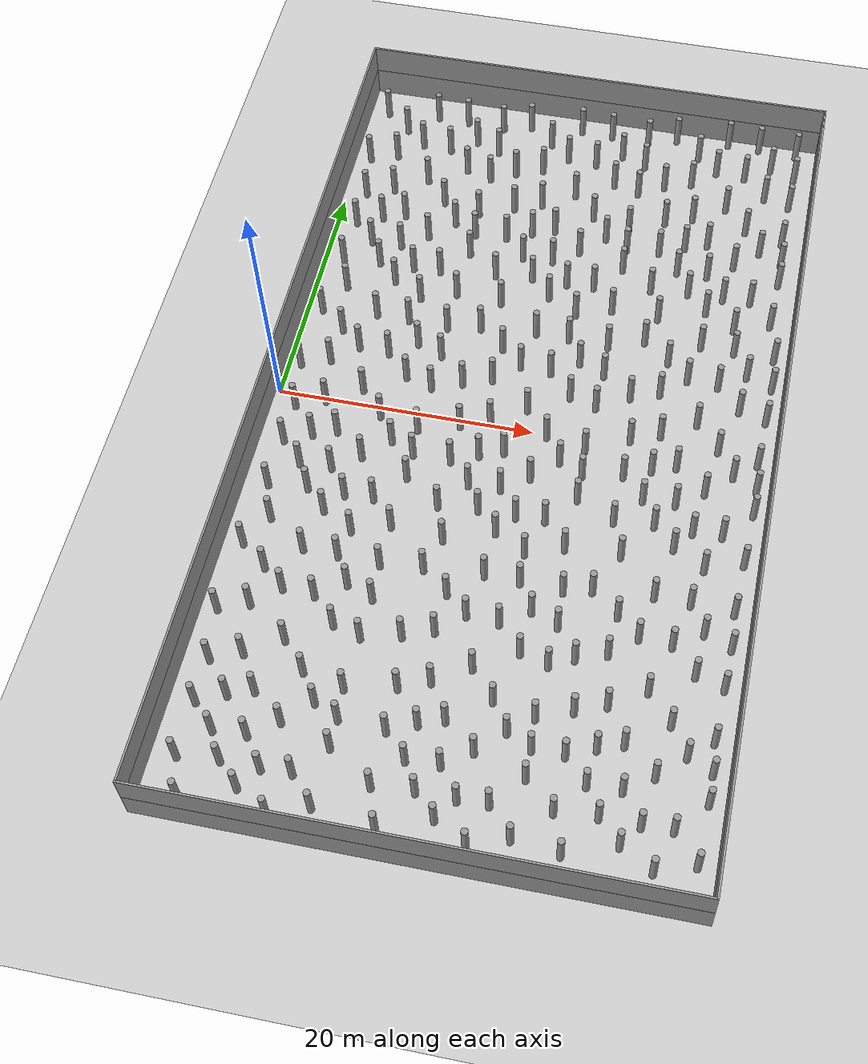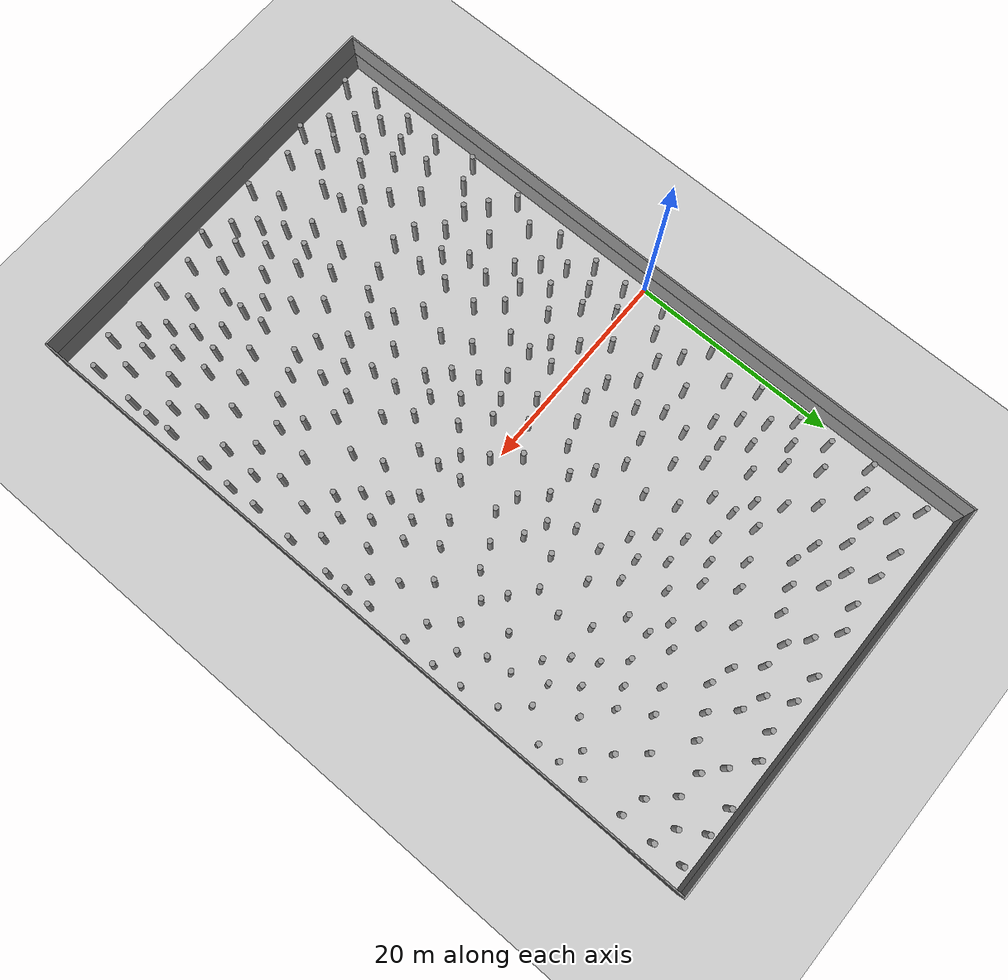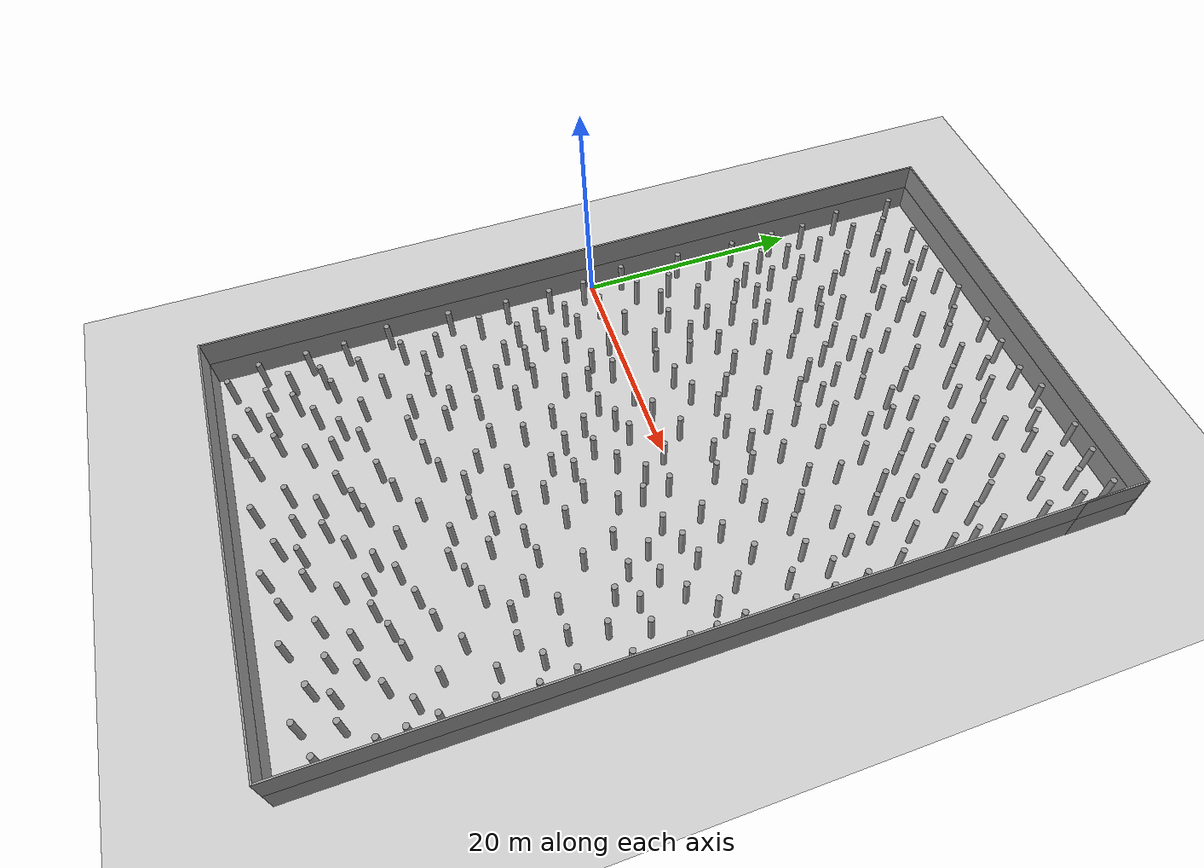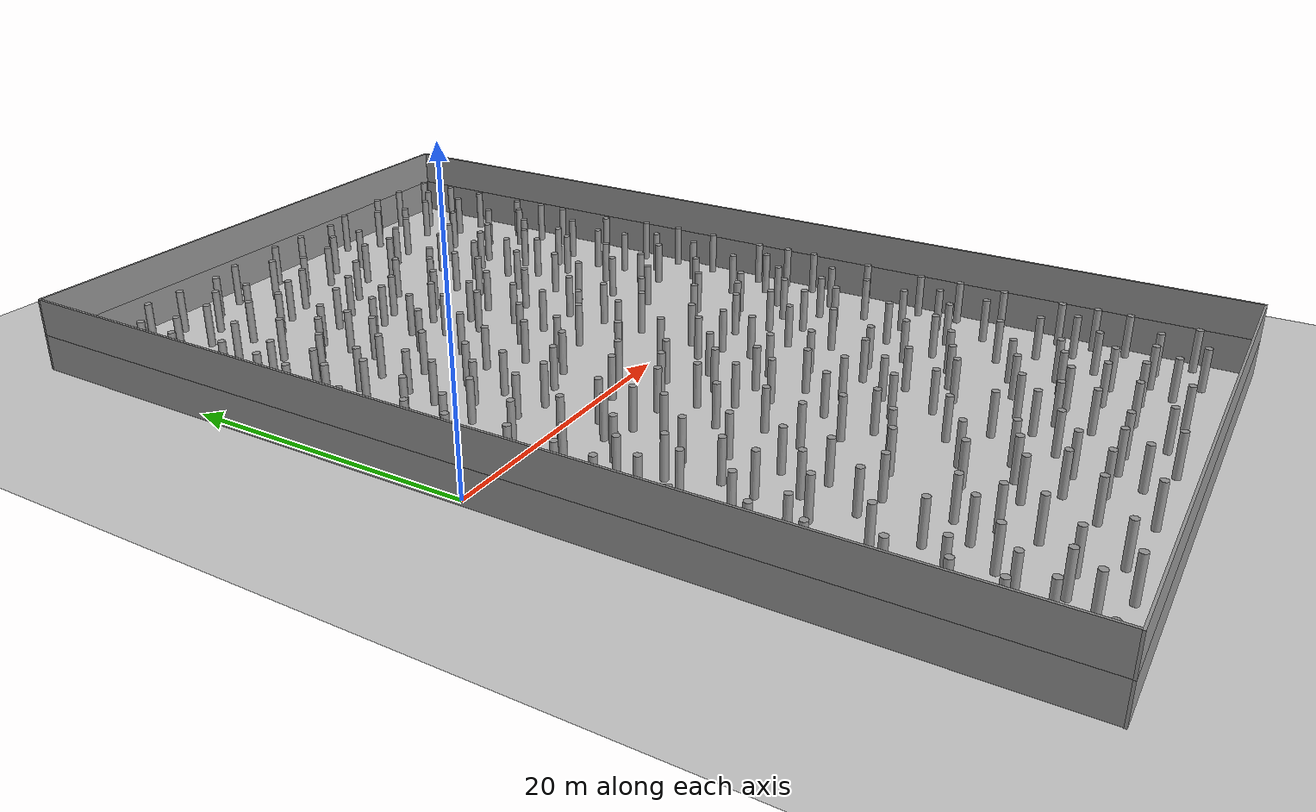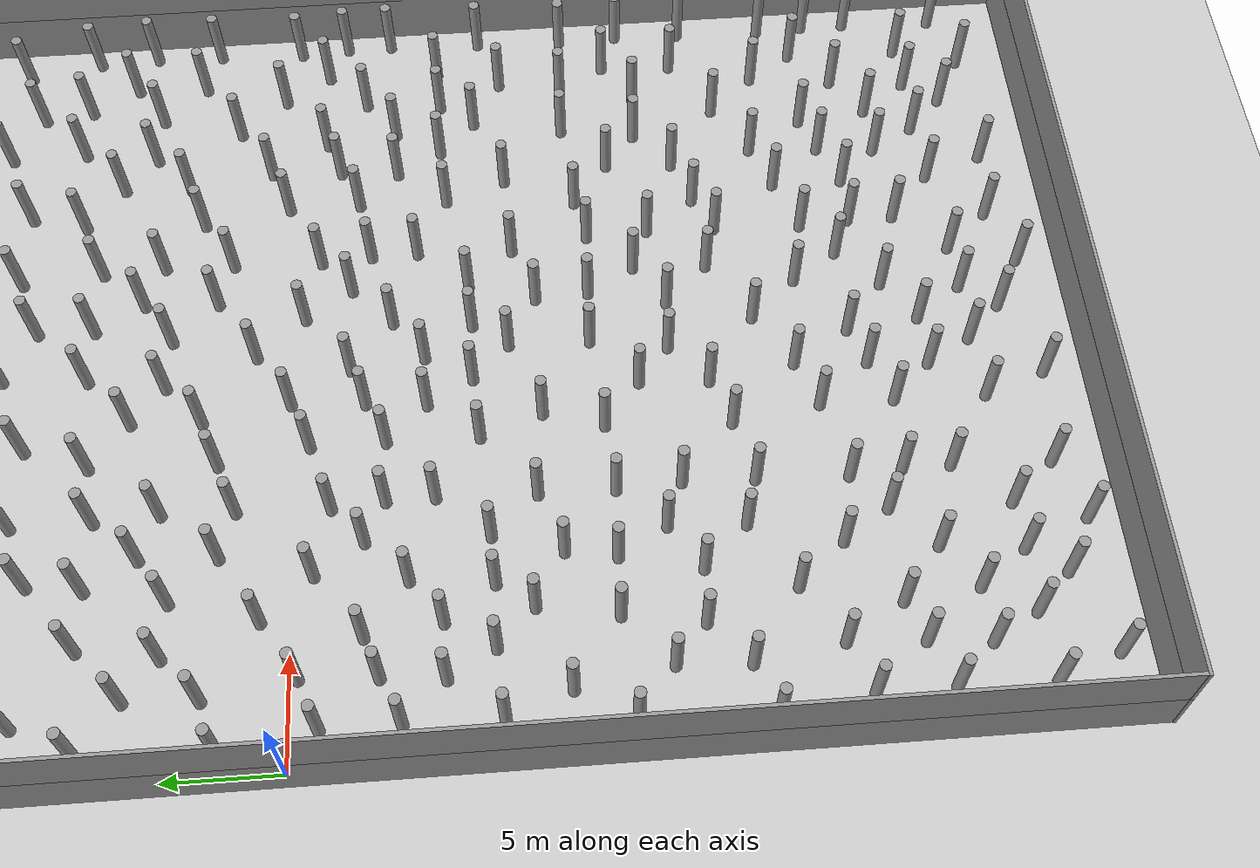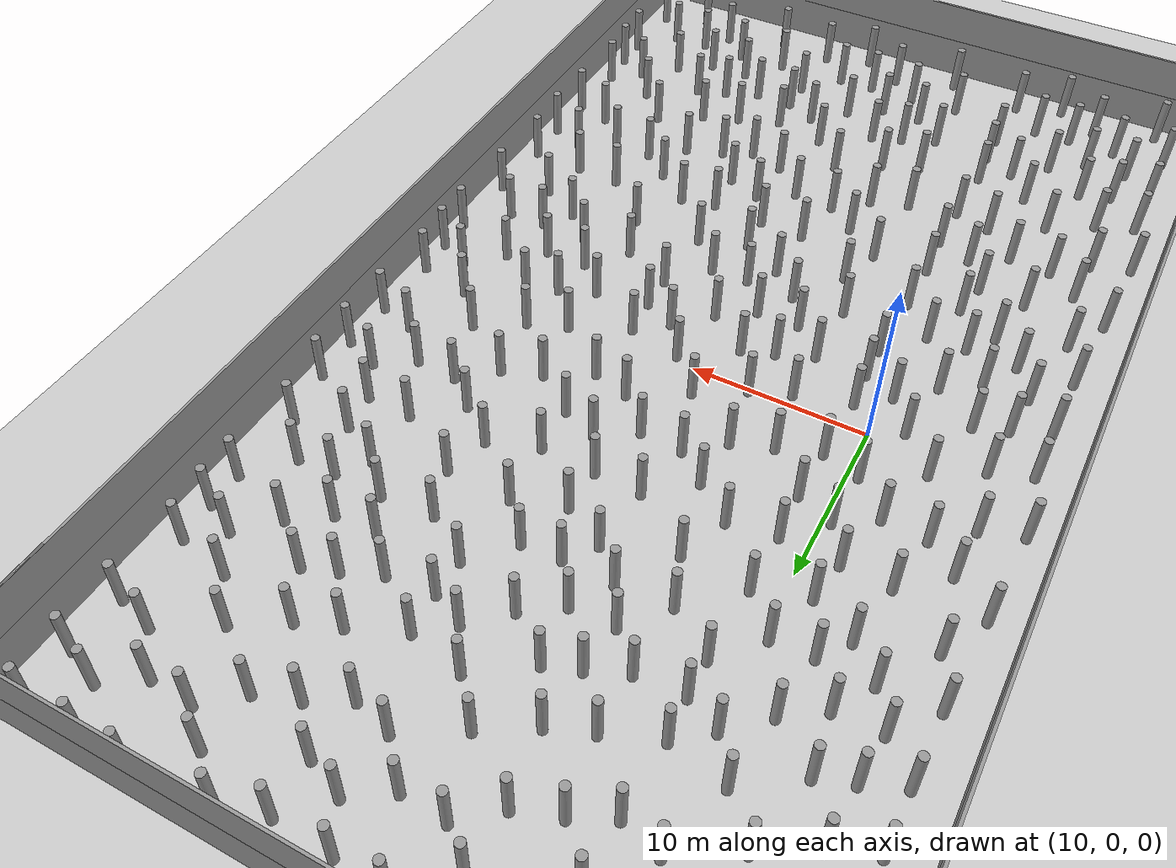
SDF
<sdf version="1.6">
 <world name="default">
  <light name="sun" type="directional">
   <pose>0 0 10 0 -0 0</pose>
   <diffuse>0.8 0.8 0.8 1</diffuse>
   <specular>0.2 0.2 0.2 1</specular>
   <attenuation>
    <range>1000</range>
    <constant>0.9</constant>
    <linear>0.01</linear>
    <quadratic>0.001</quadratic>
   </attenuation>
   <direction>-0.5 0.1 -0.9</direction>
  </light>
  <model name="ground_plane">
   <static>1</static>
   <link name="link">
    <collision name="collision">
     <geometry><plane><normal>0 0 1</normal><size>100 100</size></plane></geometry>
     <surface><friction><ode><mu>100</mu><mu2>50</mu2></ode></friction></surface>
    </collision>
    <visual name="visual">
     <cast_shadows>0</cast_shadows>
     <geometry><plane><normal>0 0 1</normal><size>100 100</size></plane></geometry>
     <material>
      <script><uri>file://media/materials/scripts/gazebo.material</uri><name>Gazebo/Grey</name></script>
     </material>
    </visual>
   </link>
  </model>
  <gravity>0 0 -9.8</gravity>
  <magnetic_field>6e-06 2.3e-05 -4.2e-05</magnetic_field>
  <atmosphere type="adiabatic"/>
  <physics name="default_physics" default="0" type="ode">
   <max_step_size>0.001</max_step_size>
   <real_time_factor>1</real_time_factor>
   <real_time_update_rate>1000</real_time_update_rate>
  </physics>
  <scene><ambient>0.4 0.4 0.4 1</ambient><background>0.7 0.7 0.7 1</background><shadows>1</shadows></scene>
  <audio><device>default</device></audio>
  <spherical_coordinates>
   <surface_model>EARTH_WGS84</surface_model>
   <latitude_deg>0</latitude_deg>
   <longitude_deg>0</longitude_deg>
   <elevation>0</elevation>
   <heading_deg>0</heading_deg>
  </spherical_coordinates>
  <model name="LjjForest">
   <link name="link_0">
    <inertial>
     <mass>1</mass>
     <inertia><ixx>0.145833</ixx><ixy>0</ixy><ixz>0</ixz><iyy>0.145833</iyy><iyz>0</iyz><izz>0.125</izz></inertia>
    </inertial>
    <pose>-5.02717 0.116957 0 0 -0 0</pose>
    <visual name="visual">
     <geometry><cylinder><radius>0.25</radius><length>3</length></cylinder></geometry>
     <material>
      <lighting>1</lighting>
      <script><uri>file://media/materials/scripts/gazebo.material</uri><name>Gazebo/Grey</name></script>
      <shader type="vertex"><normal_map>__default__</normal_map></shader>
      <ambient>0.3 0.3 0.3 1</ambient>
      <diffuse>0.7 0.7 0.7 1</diffuse>
      <specular>0.01 0.01 0.01 1</specular>
      <emissive>0 0 0 1</emissive>
     </material>
    </visual>
    <collision name="collision">
     <geometry><cylinder><radius>0.25</radius><length>3</length></cylinder></geometry>
     <surface>
      <friction>
       <ode><mu>1</mu><mu2>1</mu2><fdir1>0 0 0</fdir1><slip1>0</slip1><slip2>0</slip2></ode>
       <torsional>
        <coefficient>1</coefficient>
        <patch_radius>0</patch_radius>
        <surface_radius>0</surface_radius>
        <use_patch_radius>1</use_patch_radius>
        <ode><slip>0</slip></ode>
       </torsional>
      </friction>
      <bounce><restitution_coefficient>0</restitution_coefficient><threshold>1e+06</threshold></bounce>
      <contact>
       <collide_without_contact>0</collide_without_contact>
       <collide_without_contact_bitmask>1</collide_without_contact_bitmask>
       <collide_bitmask>1</collide_bitmask>
       <ode>
        <soft_cfm>0</soft_cfm>
        <soft_erp>0.2</soft_erp>
        <kp>1e+13</kp>
        <kd>1</kd>
        <max_vel>0.01</max_vel>
        <min_depth>0</min_depth>
       </ode>
       <bullet>
        <split_impulse>1</split_impulse>
        <split_impulse_penetration_threshold>-0.01</split_impulse_penetration_threshold>
        <soft_cfm>0</soft_cfm>
        <soft_erp>0.2</soft_erp>
        <kp>1e+13</kp>
        <kd>1</kd>
       </bullet>
      </contact>
     </surface>
    </collision>
   </link>
   <link name="link_0_clone">
    <inertial>
     <mass>1</mass>
     <inertia><ixx>0.145833</ixx><ixy>0</ixy><ixz>0</ixz><iyy>0.145833</iyy><iyz>0</iyz><izz>0.125</izz></inertia>
    </inertial>
    <pose>-2.83119 0.981911 0 0 -0 0</pose>
    <visual name="visual">
     <geometry><cylinder><radius>0.25</radius><length>3</length></cylinder></geometry>
     <material>
      <lighting>1</lighting>
      <script><uri>file://media/materials/scripts/gazebo.material</uri><name>Gazebo/Grey</name></script>
      <shader type="vertex"><normal_map>__default__</normal_map></shader>
      <ambient>0.3 0.3 0.3 1</ambient>
      <diffuse>0.7 0.7 0.7 1</diffuse>
      <specular>0.01 0.01 0.01 1</specular>
      <emissive>0 0 0 1</emissive>
     </material>
    </visual>
    <collision name="collision">
     <geometry><cylinder><radius>0.25</radius><length>3</length></cylinder></geometry>
     <surface>
      <friction>
       <ode><mu>1</mu><mu2>1</mu2><fdir1>0 0 0</fdir1><slip1>0</slip1><slip2>0</slip2></ode>
       <torsional>
        <coefficient>1</coefficient>
        <patch_radius>0</patch_radius>
        <surface_radius>0</surface_radius>
        <use_patch_radius>1</use_patch_radius>
        <ode><slip>0</slip></ode>
       </torsional>
      </friction>
      <bounce><restitution_coefficient>0</restitution_coefficient><threshold>1e+06</threshold></bounce>
      <contact>
       <collide_without_contact>0</collide_without_contact>
       <collide_without_contact_bitmask>1</collide_without_contact_bitmask>
       <collide_bitmask>1</collide_bitmask>
       <ode>
        <soft_cfm>0</soft_cfm>
        <soft_erp>0.2</soft_erp>
        <kp>1e+13</kp>
        <kd>1</kd>
        <max_vel>0.01</max_vel>
        <min_depth>0</min_depth>
       </ode>
       <bullet>
        <split_impulse>1</split_impulse>
        <split_impulse_penetration_threshold>-0.01</split_impulse_penetration_threshold>
        <soft_cfm>0</soft_cfm>
        <soft_erp>0.2</soft_erp>
        <kp>1e+13</kp>
        <kd>1</kd>
       </bullet>
      </contact>
     </surface>
    </collision>
   </link>
   <link name="link_0_clone_0">
    <inertial>
     <mass>1</mass>
     <inertia><ixx>0.145833</ixx><ixy>0</ixy><ixz>0</ixz><iyy>0.145833</iyy><iyz>0</iyz><izz>0.125</izz></inertia>
    </inertial>
    <pose>-0.25253 2.5682 0 0 -0 0</pose>
    <visual name="visual">
     <geometry><cylinder><radius>0.25</radius><length>3</length></cylinder></geometry>
     <material>
      <lighting>1</lighting>
      <script><uri>file://media/materials/scripts/gazebo.material</uri><name>Gazebo/Grey</name></script>
      <shader type="vertex"><normal_map>__default__</normal_map></shader>
      <ambient>0.3 0.3 0.3 1</ambient>
      <diffuse>0.7 0.7 0.7 1</diffuse>
      <specular>0.01 0.01 0.01 1</specular>
      <emissive>0 0 0 1</emissive>
     </material>
    </visual>
    <collision name="collision">
     <geometry><cylinder><radius>0.25</radius><length>3</length></cylinder></geometry>
     <surface>
      <friction>
       <ode><mu>1</mu><mu2>1</mu2><fdir1>0 0 0</fdir1><slip1>0</slip1><slip2>0</slip2></ode>
       <torsional>
        <coefficient>1</coefficient>
        <patch_radius>0</patch_radius>
        <surface_radius>0</surface_radius>
        <use_patch_radius>1</use_patch_radius>
        <ode><slip>0</slip></ode>
       </torsional>
      </friction>
      <bounce><restitution_coefficient>0</restitution_coefficient><threshold>1e+06</threshold></bounce>
      <contact>
       <collide_without_contact>0</collide_without_contact>
       <collide_without_contact_bitmask>1</collide_without_contact_bitmask>
       <collide_bitmask>1</collide_bitmask>
       <ode>
        <soft_cfm>0</soft_cfm>
        <soft_erp>0.2</soft_erp>
        <kp>1e+13</kp>
        <kd>1</kd>
        <max_vel>0.01</max_vel>
        <min_depth>0</min_depth>
       </ode>
       <bullet>
        <split_impulse>1</split_impulse>
        <split_impulse_penetration_threshold>-0.01</split_impulse_penetration_threshold>
        <soft_cfm>0</soft_cfm>
        <soft_erp>0.2</soft_erp>
        <kp>1e+13</kp>
        <kd>1</kd>
       </bullet>
      </contact>
     </surface>
    </collision>
   </link>
   <link name="link_0_clone_1">
    <inertial>
     <mass>1</mass>
     <inertia><ixx>0.145833</ixx><ixy>0</ixy><ixz>0</ixz><iyy>0.145833</iyy><iyz>0</iyz><izz>0.125</izz></inertia>
    </inertial>
    <pose>-1.2394 -1.64814 0 0 -0 0</pose>
    <visual name="visual">
     <geometry><cylinder><radius>0.25</radius><length>3</length></cylinder></geometry>
     <material>
      <lighting>1</lighting>
      <script><uri>file://media/materials/scripts/gazebo.material</uri><name>Gazebo/Grey</name></script>
      <shader type="vertex"><normal_map>__default__</normal_map></shader>
      <ambient>0.3 0.3 0.3 1</ambient>
      <diffuse>0.7 0.7 0.7 1</diffuse>
      <specular>0.01 0.01 0.01 1</specular>
      <emissive>0 0 0 1</emissive>
     </material>
    </visual>
    <collision name="collision">
     <geometry><cylinder><radius>0.25</radius><length>3</length></cylinder></geometry>
     <surface>
      <friction>
       <ode><mu>1</mu><mu2>1</mu2><fdir1>0 0 0</fdir1><slip1>0</slip1><slip2>0</slip2></ode>
       <torsional>
        <coefficient>1</coefficient>
        <patch_radius>0</patch_radius>
        <surface_radius>0</surface_radius>
        <use_patch_radius>1</use_patch_radius>
        <ode><slip>0</slip></ode>
       </torsional>
      </friction>
      <bounce><restitution_coefficient>0</restitution_coefficient><threshold>1e+06</threshold></bounce>
      <contact>
       <collide_without_contact>0</collide_without_contact>
       <collide_without_contact_bitmask>1</collide_without_contact_bitmask>
       <collide_bitmask>1</collide_bitmask>
       <ode>
        <soft_cfm>0</soft_cfm>
        <soft_erp>0.2</soft_erp>
        <kp>1e+13</kp>
        <kd>1</kd>
        <max_vel>0.01</max_vel>
        <min_depth>0</min_depth>
       </ode>
       <bullet>
        <split_impulse>1</split_impulse>
        <split_impulse_penetration_threshold>-0.01</split_impulse_penetration_threshold>
        <soft_cfm>0</soft_cfm>
        <soft_erp>0.2</soft_erp>
        <kp>1e+13</kp>
        <kd>1</kd>
       </bullet>
      </contact>
     </surface>
    </collision>
   </link>
   <link name="link_0_clone_10">
    <inertial>
     <mass>1</mass>
     <inertia><ixx>0.145833</ixx><ixy>0</ixy><ixz>0</ixz><iyy>0.145833</iyy><iyz>0</iyz><izz>0.125</izz></inertia>
    </inertial>
    <pose>4.92442 -4.7051 0 0 -0 0</pose>
    <visual name="visual">
     <geometry><cylinder><radius>0.25</radius><length>3</length></cylinder></geometry>
     <material>
      <lighting>1</lighting>
      <script><uri>file://media/materials/scripts/gazebo.material</uri><name>Gazebo/Grey</name></script>
      <shader type="vertex"><normal_map>__default__</normal_map></shader>
      <ambient>0.3 0.3 0.3 1</ambient>
      <diffuse>0.7 0.7 0.7 1</diffuse>
      <specular>0.01 0.01 0.01 1</specular>
      <emissive>0 0 0 1</emissive>
     </material>
    </visual>
    <collision name="collision">
     <geometry><cylinder><radius>0.25</radius><length>3</length></cylinder></geometry>
     <surface>
      <friction>
       <ode><mu>1</mu><mu2>1</mu2><fdir1>0 0 0</fdir1><slip1>0</slip1><slip2>0</slip2></ode>
       <torsional>
        <coefficient>1</coefficient>
        <patch_radius>0</patch_radius>
        <surface_radius>0</surface_radius>
        <use_patch_radius>1</use_patch_radius>
        <ode><slip>0</slip></ode>
       </torsional>
      </friction>
      <bounce><restitution_coefficient>0</restitution_coefficient><threshold>1e+06</threshold></bounce>
      <contact>
       <collide_without_contact>0</collide_without_contact>
       <collide_without_contact_bitmask>1</collide_without_contact_bitmask>
       <collide_bitmask>1</collide_bitmask>
       <ode>
        <soft_cfm>0</soft_cfm>
        <soft_erp>0.2</soft_erp>
        <kp>1e+13</kp>
        <kd>1</kd>
        <max_vel>0.01</max_vel>
        <min_depth>0</min_depth>
       </ode>
       <bullet>
        <split_impulse>1</split_impulse>
        <split_impulse_penetration_threshold>-0.01</split_impulse_penetration_threshold>
        <soft_cfm>0</soft_cfm>
        <soft_erp>0.2</soft_erp>
        <kp>1e+13</kp>
        <kd>1</kd>
       </bullet>
      </contact>
     </surface>
    </collision>
   </link>
   <link name="link_0_clone_11">
    <inertial>
     <mass>1</mass>
     <inertia><ixx>0.145833</ixx><ixy>0</ixy><ixz>0</ixz><iyy>0.145833</iyy><iyz>0</iyz><izz>0.125</izz></inertia>
    </inertial>
    <pose>2.92414 -7.00263 0 0 -0 0</pose>
    <visual name="visual">
     <geometry><cylinder><radius>0.25</radius><length>3</length></cylinder></geometry>
     <material>
      <lighting>1</lighting>
      <script><uri>file://media/materials/scripts/gazebo.material</uri><name>Gazebo/Grey</name></script>
      <shader type="vertex"><normal_map>__default__</normal_map></shader>
      <ambient>0.3 0.3 0.3 1</ambient>
      <diffuse>0.7 0.7 0.7 1</diffuse>
      <specular>0.01 0.01 0.01 1</specular>
      <emissive>0 0 0 1</emissive>
     </material>
    </visual>
    <collision name="collision">
     <geometry><cylinder><radius>0.25</radius><length>3</length></cylinder></geometry>
     <surface>
      <friction>
       <ode><mu>1</mu><mu2>1</mu2><fdir1>0 0 0</fdir1><slip1>0</slip1><slip2>0</slip2></ode>
       <torsional>
        <coefficient>1</coefficient>
        <patch_radius>0</patch_radius>
        <surface_radius>0</surface_radius>
        <use_patch_radius>1</use_patch_radius>
        <ode><slip>0</slip></ode>
       </torsional>
      </friction>
      <bounce><restitution_coefficient>0</restitution_coefficient><threshold>1e+06</threshold></bounce>
      <contact>
       <collide_without_contact>0</collide_without_contact>
       <collide_without_contact_bitmask>1</collide_without_contact_bitmask>
       <collide_bitmask>1</collide_bitmask>
       <ode>
        <soft_cfm>0</soft_cfm>
        <soft_erp>0.2</soft_erp>
        <kp>1e+13</kp>
        <kd>1</kd>
        <max_vel>0.01</max_vel>
        <min_depth>0</min_depth>
       </ode>
       <bullet>
        <split_impulse>1</split_impulse>
        <split_impulse_penetration_threshold>-0.01</split_impulse_penetration_threshold>
        <soft_cfm>0</soft_cfm>
        <soft_erp>0.2</soft_erp>
        <kp>1e+13</kp>
        <kd>1</kd>
       </bullet>
      </contact>
     </surface>
    </collision>
   </link>
   <link name="link_0_clone_12">
    <inertial>
     <mass>1</mass>
     <inertia><ixx>0.145833</ixx><ixy>0</ixy><ixz>0</ixz><iyy>0.145833</iyy><iyz>0</iyz><izz>0.125</izz></inertia>
    </inertial>
    <pose>4.76112 -9.06376 0 0 -0 0</pose>
    <visual name="visual">
     <geometry><cylinder><radius>0.25</radius><length>3</length></cylinder></geometry>
     <material>
      <lighting>1</lighting>
      <script><uri>file://media/materials/scripts/gazebo.material</uri><name>Gazebo/Grey</name></script>
      <shader type="vertex"><normal_map>__default__</normal_map></shader>
      <ambient>0.3 0.3 0.3 1</ambient>
      <diffuse>0.7 0.7 0.7 1</diffuse>
      <specular>0.01 0.01 0.01 1</specular>
      <emissive>0 0 0 1</emissive>
     </material>
    </visual>
    <collision name="collision">
     <geometry><cylinder><radius>0.25</radius><length>3</length></cylinder></geometry>
     <surface>
      <friction>
       <ode><mu>1</mu><mu2>1</mu2><fdir1>0 0 0</fdir1><slip1>0</slip1><slip2>0</slip2></ode>
       <torsional>
        <coefficient>1</coefficient>
        <patch_radius>0</patch_radius>
        <surface_radius>0</surface_radius>
        <use_patch_radius>1</use_patch_radius>
        <ode><slip>0</slip></ode>
       </torsional>
      </friction>
      <bounce><restitution_coefficient>0</restitution_coefficient><threshold>1e+06</threshold></bounce>
      <contact>
       <collide_without_contact>0</collide_without_contact>
       <collide_without_contact_bitmask>1</collide_without_contact_bitmask>
       <collide_bitmask>1</collide_bitmask>
       <ode>
        <soft_cfm>0</soft_cfm>
        <soft_erp>0.2</soft_erp>
        <kp>1e+13</kp>
        <kd>1</kd>
        <max_vel>0.01</max_vel>
        <min_depth>0</min_depth>
       </ode>
       <bullet>
        <split_impulse>1</split_impulse>
        <split_impulse_penetration_threshold>-0.01</split_impulse_penetration_threshold>
        <soft_cfm>0</soft_cfm>
        <soft_erp>0.2</soft_erp>
        <kp>1e+13</kp>
        <kd>1</kd>
       </bullet>
      </contact>
     </surface>
    </collision>
   </link>
   <link name="link_0_clone_13">
    <inertial>
     <mass>1</mass>
     <inertia><ixx>0.145833</ixx><ixy>0</ixy><ixz>0</ixz><iyy>0.145833</iyy><iyz>0</iyz><izz>0.125</izz></inertia>
    </inertial>
    <pose>0.731055 -7.10049 0 0 -0 0</pose>
    <visual name="visual">
     <geometry><cylinder><radius>0.25</radius><length>3</length></cylinder></geometry>
     <material>
      <lighting>1</lighting>
      <script><uri>file://media/materials/scripts/gazebo.material</uri><name>Gazebo/Grey</name></script>
      <shader type="vertex"><normal_map>__default__</normal_map></shader>
      <ambient>0.3 0.3 0.3 1</ambient>
      <diffuse>0.7 0.7 0.7 1</diffuse>
      <specular>0.01 0.01 0.01 1</specular>
      <emissive>0 0 0 1</emissive>
     </material>
    </visual>
    <collision name="collision">
     <geometry><cylinder><radius>0.25</radius><length>3</length></cylinder></geometry>
     <surface>
      <friction>
       <ode><mu>1</mu><mu2>1</mu2><fdir1>0 0 0</fdir1><slip1>0</slip1><slip2>0</slip2></ode>
       <torsional>
        <coefficient>1</coefficient>
        <patch_radius>0</patch_radius>
        <surface_radius>0</surface_radius>
        <use_patch_radius>1</use_patch_radius>
        <ode><slip>0</slip></ode>
       </torsional>
      </friction>
      <bounce><restitution_coefficient>0</restitution_coefficient><threshold>1e+06</threshold></bounce>
      <contact>
       <collide_without_contact>0</collide_without_contact>
       <collide_without_contact_bitmask>1</collide_without_contact_bitmask>
       <collide_bitmask>1</collide_bitmask>
       <ode>
        <soft_cfm>0</soft_cfm>
        <soft_erp>0.2</soft_erp>
        <kp>1e+13</kp>
        <kd>1</kd>
        <max_vel>0.01</max_vel>
        <min_depth>0</min_depth>
       </ode>
       <bullet>
        <split_impulse>1</split_impulse>
        <split_impulse_penetration_threshold>-0.01</split_impulse_penetration_threshold>
        <soft_cfm>0</soft_cfm>
        <soft_erp>0.2</soft_erp>
        <kp>1e+13</kp>
        <kd>1</kd>
       </bullet>
      </contact>
     </surface>
    </collision>
   </link>
   <link name="link_0_clone_14">
    <inertial>
     <mass>1</mass>
     <inertia><ixx>0.145833</ixx><ixy>0</ixy><ixz>0</ixz><iyy>0.145833</iyy><iyz>0</iyz><izz>0.125</izz></inertia>
    </inertial>
    <pose>-0.840028 -4.93267 0 0 -0 0</pose>
    <visual name="visual">
     <geometry><cylinder><radius>0.25</radius><length>3</length></cylinder></geometry>
     <material>
      <lighting>1</lighting>
      <script><uri>file://media/materials/scripts/gazebo.material</uri><name>Gazebo/Grey</name></script>
      <shader type="vertex"><normal_map>__default__</normal_map></shader>
      <ambient>0.3 0.3 0.3 1</ambient>
      <diffuse>0.7 0.7 0.7 1</diffuse>
      <specular>0.01 0.01 0.01 1</specular>
      <emissive>0 0 0 1</emissive>
     </material>
    </visual>
    <collision name="collision">
     <geometry><cylinder><radius>0.25</radius><length>3</length></cylinder></geometry>
     <surface>
      <friction>
       <ode><mu>1</mu><mu2>1</mu2><fdir1>0 0 0</fdir1><slip1>0</slip1><slip2>0</slip2></ode>
       <torsional>
        <coefficient>1</coefficient>
        <patch_radius>0</patch_radius>
        <surface_radius>0</surface_radius>
        <use_patch_radius>1</use_patch_radius>
        <ode><slip>0</slip></ode>
       </torsional>
      </friction>
      <bounce><restitution_coefficient>0</restitution_coefficient><threshold>1e+06</threshold></bounce>
      <contact>
       <collide_without_contact>0</collide_without_contact>
       <collide_without_contact_bitmask>1</collide_without_contact_bitmask>
       <collide_bitmask>1</collide_bitmask>
       <ode>
        <soft_cfm>0</soft_cfm>
        <soft_erp>0.2</soft_erp>
        <kp>1e+13</kp>
        <kd>1</kd>
        <max_vel>0.01</max_vel>
        <min_depth>0</min_depth>
       </ode>
       <bullet>
        <split_impulse>1</split_impulse>
        <split_impulse_penetration_threshold>-0.01</split_impulse_penetration_threshold>
        <soft_cfm>0</soft_cfm>
        <soft_erp>0.2</soft_erp>
        <kp>1e+13</kp>
        <kd>1</kd>
       </bullet>
      </contact>
     </surface>
    </collision>
   </link>
   <link name="link_0_clone_15">
    <inertial>
     <mass>1</mass>
     <inertia><ixx>0.145833</ixx><ixy>0</ixy><ixz>0</ixz><iyy>0.145833</iyy><iyz>0</iyz><izz>0.125</izz></inertia>
    </inertial>
    <pose>-3.03254 -2.29236 0 0 -0 0</pose>
    <visual name="visual">
     <geometry><cylinder><radius>0.25</radius><length>3</length></cylinder></geometry>
     <material>
      <lighting>1</lighting>
      <script><uri>file://media/materials/scripts/gazebo.material</uri><name>Gazebo/Grey</name></script>
      <shader type="vertex"><normal_map>__default__</normal_map></shader>
      <ambient>0.3 0.3 0.3 1</ambient>
      <diffuse>0.7 0.7 0.7 1</diffuse>
      <specular>0.01 0.01 0.01 1</specular>
      <emissive>0 0 0 1</emissive>
     </material>
    </visual>
    <collision name="collision">
     <geometry><cylinder><radius>0.25</radius><length>3</length></cylinder></geometry>
     <surface>
      <friction>
       <ode><mu>1</mu><mu2>1</mu2><fdir1>0 0 0</fdir1><slip1>0</slip1><slip2>0</slip2></ode>
       <torsional>
        <coefficient>1</coefficient>
        <patch_radius>0</patch_radius>
        <surface_radius>0</surface_radius>
        <use_patch_radius>1</use_patch_radius>
        <ode><slip>0</slip></ode>
       </torsional>
      </friction>
      <bounce><restitution_coefficient>0</restitution_coefficient><threshold>1e+06</threshold></bounce>
      <contact>
       <collide_without_contact>0</collide_without_contact>
       <collide_without_contact_bitmask>1</collide_without_contact_bitmask>
       <collide_bitmask>1</collide_bitmask>
       <ode>
        <soft_cfm>0</soft_cfm>
        <soft_erp>0.2</soft_erp>
        <kp>1e+13</kp>
        <kd>1</kd>
        <max_vel>0.01</max_vel>
        <min_depth>0</min_depth>
       </ode>
       <bullet>
        <split_impulse>1</split_impulse>
        <split_impulse_penetration_threshold>-0.01</split_impulse_penetration_threshold>
        <soft_cfm>0</soft_cfm>
        <soft_erp>0.2</soft_erp>
        <kp>1e+13</kp>
        <kd>1</kd>
       </bullet>
      </contact>
     </surface>
    </collision>
   </link>
   <link name="link_0_clone_16">
    <inertial>
     <mass>1</mass>
     <inertia><ixx>0.145833</ixx><ixy>0</ixy><ixz>0</ixz><iyy>0.145833</iyy><iyz>0</iyz><izz>0.125</izz></inertia>
    </inertial>
    <pose>-5.04025 -3.1815 0 0 -0 0</pose>
    <visual name="visual">
     <geometry><cylinder><radius>0.25</radius><length>3</length></cylinder></geometry>
     <material>
      <lighting>1</lighting>
      <script><uri>file://media/materials/scripts/gazebo.material</uri><name>Gazebo/Grey</name></script>
      <shader type="vertex"><normal_map>__default__</normal_map></shader>
      <ambient>0.3 0.3 0.3 1</ambient>
      <diffuse>0.7 0.7 0.7 1</diffuse>
      <specular>0.01 0.01 0.01 1</specular>
      <emissive>0 0 0 1</emissive>
     </material>
    </visual>
    <collision name="collision">
     <geometry><cylinder><radius>0.25</radius><length>3</length></cylinder></geometry>
     <surface>
      <friction>
       <ode><mu>1</mu><mu2>1</mu2><fdir1>0 0 0</fdir1><slip1>0</slip1><slip2>0</slip2></ode>
       <torsional>
        <coefficient>1</coefficient>
        <patch_radius>0</patch_radius>
        <surface_radius>0</surface_radius>
        <use_patch_radius>1</use_patch_radius>
        <ode><slip>0</slip></ode>
       </torsional>
      </friction>
      <bounce><restitution_coefficient>0</restitution_coefficient><threshold>1e+06</threshold></bounce>
      <contact>
       <collide_without_contact>0</collide_without_contact>
       <collide_without_contact_bitmask>1</collide_without_contact_bitmask>
       <collide_bitmask>1</collide_bitmask>
       <ode>
        <soft_cfm>0</soft_cfm>
        <soft_erp>0.2</soft_erp>
        <kp>1e+13</kp>
        <kd>1</kd>
        <max_vel>0.01</max_vel>
        <min_depth>0</min_depth>
       </ode>
       <bullet>
        <split_impulse>1</split_impulse>
        <split_impulse_penetration_threshold>-0.01</split_impulse_penetration_threshold>
        <soft_cfm>0</soft_cfm>
        <soft_erp>0.2</soft_erp>
        <kp>1e+13</kp>
        <kd>1</kd>
       </bullet>
      </contact>
     </surface>
    </collision>
   </link>
   <link name="link_0_clone_17">
    <inertial>
     <mass>1</mass>
     <inertia><ixx>0.145833</ixx><ixy>0</ixy><ixz>0</ixz><iyy>0.145833</iyy><iyz>0</iyz><izz>0.125</izz></inertia>
    </inertial>
    <pose>-3.28823 -4.99733 0 0 -0 0</pose>
    <visual name="visual">
     <geometry><cylinder><radius>0.25</radius><length>3</length></cylinder></geometry>
     <material>
      <lighting>1</lighting>
      <script><uri>file://media/materials/scripts/gazebo.material</uri><name>Gazebo/Grey</name></script>
      <shader type="vertex"><normal_map>__default__</normal_map></shader>
      <ambient>0.3 0.3 0.3 1</ambient>
      <diffuse>0.7 0.7 0.7 1</diffuse>
      <specular>0.01 0.01 0.01 1</specular>
      <emissive>0 0 0 1</emissive>
     </material>
    </visual>
    <collision name="collision">
     <geometry><cylinder><radius>0.25</radius><length>3</length></cylinder></geometry>
     <surface>
      <friction>
       <ode><mu>1</mu><mu2>1</mu2><fdir1>0 0 0</fdir1><slip1>0</slip1><slip2>0</slip2></ode>
       <torsional>
        <coefficient>1</coefficient>
        <patch_radius>0</patch_radius>
        <surface_radius>0</surface_radius>
        <use_patch_radius>1</use_patch_radius>
        <ode><slip>0</slip></ode>
       </torsional>
      </friction>
      <bounce><restitution_coefficient>0</restitution_coefficient><threshold>1e+06</threshold></bounce>
      <contact>
       <collide_without_contact>0</collide_without_contact>
       <collide_without_contact_bitmask>1</collide_without_contact_bitmask>
       <collide_bitmask>1</collide_bitmask>
       <ode>
        <soft_cfm>0</soft_cfm>
        <soft_erp>0.2</soft_erp>
        <kp>1e+13</kp>
        <kd>1</kd>
        <max_vel>0.01</max_vel>
        <min_depth>0</min_depth>
       </ode>
       <bullet>
        <split_impulse>1</split_impulse>
        <split_impulse_penetration_threshold>-0.01</split_impulse_penetration_threshold>
        <soft_cfm>0</soft_cfm>
        <soft_erp>0.2</soft_erp>
        <kp>1e+13</kp>
        <kd>1</kd>
       </bullet>
      </contact>
     </surface>
    </collision>
   </link>
   <link name="link_0_clone_18">
    <inertial>
     <mass>1</mass>
     <inertia><ixx>0.145833</ixx><ixy>0</ixy><ixz>0</ixz><iyy>0.145833</iyy><iyz>0</iyz><izz>0.125</izz></inertia>
    </inertial>
    <pose>-2.11118 -7.04502 0 0 -0 0</pose>
    <visual name="visual">
     <geometry><cylinder><radius>0.25</radius><length>3</length></cylinder></geometry>
     <material>
      <lighting>1</lighting>
      <script><uri>file://media/materials/scripts/gazebo.material</uri><name>Gazebo/Grey</name></script>
      <shader type="vertex"><normal_map>__default__</normal_map></shader>
      <ambient>0.3 0.3 0.3 1</ambient>
      <diffuse>0.7 0.7 0.7 1</diffuse>
      <specular>0.01 0.01 0.01 1</specular>
      <emissive>0 0 0 1</emissive>
     </material>
    </visual>
    <collision name="collision">
     <geometry><cylinder><radius>0.25</radius><length>3</length></cylinder></geometry>
     <surface>
      <friction>
       <ode><mu>1</mu><mu2>1</mu2><fdir1>0 0 0</fdir1><slip1>0</slip1><slip2>0</slip2></ode>
       <torsional>
        <coefficient>1</coefficient>
        <patch_radius>0</patch_radius>
        <surface_radius>0</surface_radius>
        <use_patch_radius>1</use_patch_radius>
        <ode><slip>0</slip></ode>
       </torsional>
      </friction>
      <bounce><restitution_coefficient>0</restitution_coefficient><threshold>1e+06</threshold></bounce>
      <contact>
       <collide_without_contact>0</collide_without_contact>
       <collide_without_contact_bitmask>1</collide_without_contact_bitmask>
       <collide_bitmask>1</collide_bitmask>
       <ode>
        <soft_cfm>0</soft_cfm>
        <soft_erp>0.2</soft_erp>
        <kp>1e+13</kp>
        <kd>1</kd>
        <max_vel>0.01</max_vel>
        <min_depth>0</min_depth>
       </ode>
       <bullet>
        <split_impulse>1</split_impulse>
        <split_impulse_penetration_threshold>-0.01</split_impulse_penetration_threshold>
        <soft_cfm>0</soft_cfm>
        <soft_erp>0.2</soft_erp>
        <kp>1e+13</kp>
        <kd>1</kd>
       </bullet>
      </contact>
     </surface>
    </collision>
   </link>
   <link name="link_0_clone_19">
    <inertial>
     <mass>1</mass>
     <inertia><ixx>0.145833</ixx><ixy>0</ixy><ixz>0</ixz><iyy>0.145833</iyy><iyz>0</iyz><izz>0.125</izz></inertia>
    </inertial>
    <pose>-0.4391 -8.69513 0 0 -0 0</pose>
    <visual name="visual">
     <geometry><cylinder><radius>0.25</radius><length>3</length></cylinder></geometry>
     <material>
      <lighting>1</lighting>
      <script><uri>file://media/materials/scripts/gazebo.material</uri><name>Gazebo/Grey</name></script>
      <shader type="vertex"><normal_map>__default__</normal_map></shader>
      <ambient>0.3 0.3 0.3 1</ambient>
      <diffuse>0.7 0.7 0.7 1</diffuse>
      <specular>0.01 0.01 0.01 1</specular>
      <emissive>0 0 0 1</emissive>
     </material>
    </visual>
    <collision name="collision">
     <geometry><cylinder><radius>0.25</radius><length>3</length></cylinder></geometry>
     <surface>
      <friction>
       <ode><mu>1</mu><mu2>1</mu2><fdir1>0 0 0</fdir1><slip1>0</slip1><slip2>0</slip2></ode>
       <torsional>
        <coefficient>1</coefficient>
        <patch_radius>0</patch_radius>
        <surface_radius>0</surface_radius>
        <use_patch_radius>1</use_patch_radius>
        <ode><slip>0</slip></ode>
       </torsional>
      </friction>
      <bounce><restitution_coefficient>0</restitution_coefficient><threshold>1e+06</threshold></bounce>
      <contact>
       <collide_without_contact>0</collide_without_contact>
       <collide_without_contact_bitmask>1</collide_without_contact_bitmask>
       <collide_bitmask>1</collide_bitmask>
       <ode>
        <soft_cfm>0</soft_cfm>
        <soft_erp>0.2</soft_erp>
        <kp>1e+13</kp>
        <kd>1</kd>
        <max_vel>0.01</max_vel>
        <min_depth>0</min_depth>
       </ode>
       <bullet>
        <split_impulse>1</split_impulse>
        <split_impulse_penetration_threshold>-0.01</split_impulse_penetration_threshold>
        <soft_cfm>0</soft_cfm>
        <soft_erp>0.2</soft_erp>
        <kp>1e+13</kp>
        <kd>1</kd>
       </bullet>
      </contact>
     </surface>
    </collision>
   </link>
   <link name="link_0_clone_2">
    <inertial>
     <mass>1</mass>
     <inertia><ixx>0.145833</ixx><ixy>0</ixy><ixz>0</ixz><iyy>0.145833</iyy><iyz>0</iyz><izz>0.125</izz></inertia>
    </inertial>
    <pose>1.64727 0.418921 0 0 -0 0</pose>
    <visual name="visual">
     <geometry><cylinder><radius>0.25</radius><length>3</length></cylinder></geometry>
     <material>
      <lighting>1</lighting>
      <script><uri>file://media/materials/scripts/gazebo.material</uri><name>Gazebo/Grey</name></script>
      <shader type="vertex"><normal_map>__default__</normal_map></shader>
      <ambient>0.3 0.3 0.3 1</ambient>
      <diffuse>0.7 0.7 0.7 1</diffuse>
      <specular>0.01 0.01 0.01 1</specular>
      <emissive>0 0 0 1</emissive>
     </material>
    </visual>
    <collision name="collision">
     <geometry><cylinder><radius>0.25</radius><length>3</length></cylinder></geometry>
     <surface>
      <friction>
       <ode><mu>1</mu><mu2>1</mu2><fdir1>0 0 0</fdir1><slip1>0</slip1><slip2>0</slip2></ode>
       <torsional>
        <coefficient>1</coefficient>
        <patch_radius>0</patch_radius>
        <surface_radius>0</surface_radius>
        <use_patch_radius>1</use_patch_radius>
        <ode><slip>0</slip></ode>
       </torsional>
      </friction>
      <bounce><restitution_coefficient>0</restitution_coefficient><threshold>1e+06</threshold></bounce>
      <contact>
       <collide_without_contact>0</collide_without_contact>
       <collide_without_contact_bitmask>1</collide_without_contact_bitmask>
       <collide_bitmask>1</collide_bitmask>
       <ode>
        <soft_cfm>0</soft_cfm>
        <soft_erp>0.2</soft_erp>
        <kp>1e+13</kp>
        <kd>1</kd>
        <max_vel>0.01</max_vel>
        <min_depth>0</min_depth>
       </ode>
       <bullet>
        <split_impulse>1</split_impulse>
        <split_impulse_penetration_threshold>-0.01</split_impulse_penetration_threshold>
        <soft_cfm>0</soft_cfm>
        <soft_erp>0.2</soft_erp>
        <kp>1e+13</kp>
        <kd>1</kd>
       </bullet>
      </contact>
     </surface>
    </collision>
   </link>
   <link name="link_0_clone_20">
    <inertial>
     <mass>1</mass>
     <inertia><ixx>0.145833</ixx><ixy>0</ixy><ixz>0</ixz><iyy>0.145833</iyy><iyz>0</iyz><izz>0.125</izz></inertia>
    </inertial>
    <pose>1.97365 -10.0303 0 0 -0 0</pose>
    <visual name="visual">
     <geometry><cylinder><radius>0.25</radius><length>3</length></cylinder></geometry>
     <material>
      <lighting>1</lighting>
      <script><uri>file://media/materials/scripts/gazebo.material</uri><name>Gazebo/Grey</name></script>
      <shader type="vertex"><normal_map>__default__</normal_map></shader>
      <ambient>0.3 0.3 0.3 1</ambient>
      <diffuse>0.7 0.7 0.7 1</diffuse>
      <specular>0.01 0.01 0.01 1</specular>
      <emissive>0 0 0 1</emissive>
     </material>
    </visual>
    <collision name="collision">
     <geometry><cylinder><radius>0.25</radius><length>3</length></cylinder></geometry>
     <surface>
      <friction>
       <ode><mu>1</mu><mu2>1</mu2><fdir1>0 0 0</fdir1><slip1>0</slip1><slip2>0</slip2></ode>
       <torsional>
        <coefficient>1</coefficient>
        <patch_radius>0</patch_radius>
        <surface_radius>0</surface_radius>
        <use_patch_radius>1</use_patch_radius>
        <ode><slip>0</slip></ode>
       </torsional>
      </friction>
      <bounce><restitution_coefficient>0</restitution_coefficient><threshold>1e+06</threshold></bounce>
      <contact>
       <collide_without_contact>0</collide_without_contact>
       <collide_without_contact_bitmask>1</collide_without_contact_bitmask>
       <collide_bitmask>1</collide_bitmask>
       <ode>
        <soft_cfm>0</soft_cfm>
        <soft_erp>0.2</soft_erp>
        <kp>1e+13</kp>
        <kd>1</kd>
        <max_vel>0.01</max_vel>
        <min_depth>0</min_depth>
       </ode>
       <bullet>
        <split_impulse>1</split_impulse>
        <split_impulse_penetration_threshold>-0.01</split_impulse_penetration_threshold>
        <soft_cfm>0</soft_cfm>
        <soft_erp>0.2</soft_erp>
        <kp>1e+13</kp>
        <kd>1</kd>
       </bullet>
      </contact>
     </surface>
    </collision>
   </link>
   <link name="link_0_clone_21">
    <inertial>
     <mass>1</mass>
     <inertia><ixx>0.145833</ixx><ixy>0</ixy><ixz>0</ixz><iyy>0.145833</iyy><iyz>0</iyz><izz>0.125</izz></inertia>
    </inertial>
    <pose>-4.11405 -10.0375 0 0 -0 0</pose>
    <visual name="visual">
     <geometry><cylinder><radius>0.25</radius><length>3</length></cylinder></geometry>
     <material>
      <lighting>1</lighting>
      <script><uri>file://media/materials/scripts/gazebo.material</uri><name>Gazebo/Grey</name></script>
      <shader type="vertex"><normal_map>__default__</normal_map></shader>
      <ambient>0.3 0.3 0.3 1</ambient>
      <diffuse>0.7 0.7 0.7 1</diffuse>
      <specular>0.01 0.01 0.01 1</specular>
      <emissive>0 0 0 1</emissive>
     </material>
    </visual>
    <collision name="collision">
     <geometry><cylinder><radius>0.25</radius><length>3</length></cylinder></geometry>
     <surface>
      <friction>
       <ode><mu>1</mu><mu2>1</mu2><fdir1>0 0 0</fdir1><slip1>0</slip1><slip2>0</slip2></ode>
       <torsional>
        <coefficient>1</coefficient>
        <patch_radius>0</patch_radius>
        <surface_radius>0</surface_radius>
        <use_patch_radius>1</use_patch_radius>
        <ode><slip>0</slip></ode>
       </torsional>
      </friction>
      <bounce><restitution_coefficient>0</restitution_coefficient><threshold>1e+06</threshold></bounce>
      <contact>
       <collide_without_contact>0</collide_without_contact>
       <collide_without_contact_bitmask>1</collide_without_contact_bitmask>
       <collide_bitmask>1</collide_bitmask>
       <ode>
        <soft_cfm>0</soft_cfm>
        <soft_erp>0.2</soft_erp>
        <kp>1e+13</kp>
        <kd>1</kd>
        <max_vel>0.01</max_vel>
        <min_depth>0</min_depth>
       </ode>
       <bullet>
        <split_impulse>1</split_impulse>
        <split_impulse_penetration_threshold>-0.01</split_impulse_penetration_threshold>
        <soft_cfm>0</soft_cfm>
        <soft_erp>0.2</soft_erp>
        <kp>1e+13</kp>
        <kd>1</kd>
       </bullet>
      </contact>
     </surface>
    </collision>
   </link>
   <link name="link_0_clone_22">
    <inertial>
     <mass>1</mass>
     <inertia><ixx>0.145833</ixx><ixy>0</ixy><ixz>0</ixz><iyy>0.145833</iyy><iyz>0</iyz><izz>0.125</izz></inertia>
    </inertial>
    <pose>-5.1094 -7.26741 0 0 -0 0</pose>
    <visual name="visual">
     <geometry><cylinder><radius>0.25</radius><length>3</length></cylinder></geometry>
     <material>
      <lighting>1</lighting>
      <script><uri>file://media/materials/scripts/gazebo.material</uri><name>Gazebo/Grey</name></script>
      <shader type="vertex"><normal_map>__default__</normal_map></shader>
      <ambient>0.3 0.3 0.3 1</ambient>
      <diffuse>0.7 0.7 0.7 1</diffuse>
      <specular>0.01 0.01 0.01 1</specular>
      <emissive>0 0 0 1</emissive>
     </material>
    </visual>
    <collision name="collision">
     <geometry><cylinder><radius>0.25</radius><length>3</length></cylinder></geometry>
     <surface>
      <friction>
       <ode><mu>1</mu><mu2>1</mu2><fdir1>0 0 0</fdir1><slip1>0</slip1><slip2>0</slip2></ode>
       <torsional>
        <coefficient>1</coefficient>
        <patch_radius>0</patch_radius>
        <surface_radius>0</surface_radius>
        <use_patch_radius>1</use_patch_radius>
        <ode><slip>0</slip></ode>
       </torsional>
      </friction>
      <bounce><restitution_coefficient>0</restitution_coefficient><threshold>1e+06</threshold></bounce>
      <contact>
       <collide_without_contact>0</collide_without_contact>
       <collide_without_contact_bitmask>1</collide_without_contact_bitmask>
       <collide_bitmask>1</collide_bitmask>
       <ode>
        <soft_cfm>0</soft_cfm>
        <soft_erp>0.2</soft_erp>
        <kp>1e+13</kp>
        <kd>1</kd>
        <max_vel>0.01</max_vel>
        <min_depth>0</min_depth>
       </ode>
       <bullet>
        <split_impulse>1</split_impulse>
        <split_impulse_penetration_threshold>-0.01</split_impulse_penetration_threshold>
        <soft_cfm>0</soft_cfm>
        <soft_erp>0.2</soft_erp>
        <kp>1e+13</kp>
        <kd>1</kd>
       </bullet>
      </contact>
     </surface>
    </collision>
   </link>
   <link name="link_0_clone_23">
    <inertial>
     <mass>1</mass>
     <inertia><ixx>0.145833</ixx><ixy>0</ixy><ixz>0</ixz><iyy>0.145833</iyy><iyz>0</iyz><izz>0.125</izz></inertia>
    </inertial>
    <pose>-5.66615 4.05911 0 0 -0 0</pose>
    <visual name="visual">
     <geometry><cylinder><radius>0.25</radius><length>3</length></cylinder></geometry>
     <material>
      <lighting>1</lighting>
      <script><uri>file://media/materials/scripts/gazebo.material</uri><name>Gazebo/Grey</name></script>
      <shader type="vertex"><normal_map>__default__</normal_map></shader>
      <ambient>0.3 0.3 0.3 1</ambient>
      <diffuse>0.7 0.7 0.7 1</diffuse>
      <specular>0.01 0.01 0.01 1</specular>
      <emissive>0 0 0 1</emissive>
     </material>
    </visual>
    <collision name="collision">
     <geometry><cylinder><radius>0.25</radius><length>3</length></cylinder></geometry>
     <surface>
      <friction>
       <ode><mu>1</mu><mu2>1</mu2><fdir1>0 0 0</fdir1><slip1>0</slip1><slip2>0</slip2></ode>
       <torsional>
        <coefficient>1</coefficient>
        <patch_radius>0</patch_radius>
        <surface_radius>0</surface_radius>
        <use_patch_radius>1</use_patch_radius>
        <ode><slip>0</slip></ode>
       </torsional>
      </friction>
      <bounce><restitution_coefficient>0</restitution_coefficient><threshold>1e+06</threshold></bounce>
      <contact>
       <collide_without_contact>0</collide_without_contact>
       <collide_without_contact_bitmask>1</collide_without_contact_bitmask>
       <collide_bitmask>1</collide_bitmask>
       <ode>
        <soft_cfm>0</soft_cfm>
        <soft_erp>0.2</soft_erp>
        <kp>1e+13</kp>
        <kd>1</kd>
        <max_vel>0.01</max_vel>
        <min_depth>0</min_depth>
       </ode>
       <bullet>
        <split_impulse>1</split_impulse>
        <split_impulse_penetration_threshold>-0.01</split_impulse_penetration_threshold>
        <soft_cfm>0</soft_cfm>
        <soft_erp>0.2</soft_erp>
        <kp>1e+13</kp>
        <kd>1</kd>
       </bullet>
      </contact>
     </surface>
    </collision>
   </link>
   <link name="link_0_clone_24">
    <inertial>
     <mass>1</mass>
     <inertia><ixx>0.145833</ixx><ixy>0</ixy><ixz>0</ixz><iyy>0.145833</iyy><iyz>0</iyz><izz>0.125</izz></inertia>
    </inertial>
    <pose>2.92874 7.75131 0 0 -0 0</pose>
    <visual name="visual">
     <geometry><cylinder><radius>0.25</radius><length>3</length></cylinder></geometry>
     <material>
      <lighting>1</lighting>
      <script><uri>file://media/materials/scripts/gazebo.material</uri><name>Gazebo/Grey</name></script>
      <shader type="vertex"><normal_map>__default__</normal_map></shader>
      <ambient>0.3 0.3 0.3 1</ambient>
      <diffuse>0.7 0.7 0.7 1</diffuse>
      <specular>0.01 0.01 0.01 1</specular>
      <emissive>0 0 0 1</emissive>
     </material>
    </visual>
    <collision name="collision">
     <geometry><cylinder><radius>0.25</radius><length>3</length></cylinder></geometry>
     <surface>
      <friction>
       <ode><mu>1</mu><mu2>1</mu2><fdir1>0 0 0</fdir1><slip1>0</slip1><slip2>0</slip2></ode>
       <torsional>
        <coefficient>1</coefficient>
        <patch_radius>0</patch_radius>
        <surface_radius>0</surface_radius>
        <use_patch_radius>1</use_patch_radius>
        <ode><slip>0</slip></ode>
       </torsional>
      </friction>
      <bounce><restitution_coefficient>0</restitution_coefficient><threshold>1e+06</threshold></bounce>
      <contact>
       <collide_without_contact>0</collide_without_contact>
       <collide_without_contact_bitmask>1</collide_without_contact_bitmask>
       <collide_bitmask>1</collide_bitmask>
       <ode>
        <soft_cfm>0</soft_cfm>
        <soft_erp>0.2</soft_erp>
        <kp>1e+13</kp>
        <kd>1</kd>
        <max_vel>0.01</max_vel>
        <min_depth>0</min_depth>
       </ode>
       <bullet>
        <split_impulse>1</split_impulse>
        <split_impulse_penetration_threshold>-0.01</split_impulse_penetration_threshold>
        <soft_cfm>0</soft_cfm>
        <soft_erp>0.2</soft_erp>
        <kp>1e+13</kp>
        <kd>1</kd>
       </bullet>
      </contact>
     </surface>
    </collision>
   </link>
   <link name="link_0_clone_25">
    <inertial>
     <mass>1</mass>
     <inertia><ixx>0.145833</ixx><ixy>0</ixy><ixz>0</ixz><iyy>0.145833</iyy><iyz>0</iyz><izz>0.125</izz></inertia>
    </inertial>
    <pose>4.82479 9.76951 0 0 -0 0</pose>
    <visual name="visual">
     <geometry><cylinder><radius>0.25</radius><length>3</length></cylinder></geometry>
     <material>
      <lighting>1</lighting>
      <script><uri>file://media/materials/scripts/gazebo.material</uri><name>Gazebo/Grey</name></script>
      <shader type="vertex"><normal_map>__default__</normal_map></shader>
      <ambient>0.3 0.3 0.3 1</ambient>
      <diffuse>0.7 0.7 0.7 1</diffuse>
      <specular>0.01 0.01 0.01 1</specular>
      <emissive>0 0 0 1</emissive>
     </material>
    </visual>
    <collision name="collision">
     <geometry><cylinder><radius>0.25</radius><length>3</length></cylinder></geometry>
     <surface>
      <friction>
       <ode><mu>1</mu><mu2>1</mu2><fdir1>0 0 0</fdir1><slip1>0</slip1><slip2>0</slip2></ode>
       <torsional>
        <coefficient>1</coefficient>
        <patch_radius>0</patch_radius>
        <surface_radius>0</surface_radius>
        <use_patch_radius>1</use_patch_radius>
        <ode><slip>0</slip></ode>
       </torsional>
      </friction>
      <bounce><restitution_coefficient>0</restitution_coefficient><threshold>1e+06</threshold></bounce>
      <contact>
       <collide_without_contact>0</collide_without_contact>
       <collide_without_contact_bitmask>1</collide_without_contact_bitmask>
       <collide_bitmask>1</collide_bitmask>
       <ode>
        <soft_cfm>0</soft_cfm>
        <soft_erp>0.2</soft_erp>
        <kp>1e+13</kp>
        <kd>1</kd>
        <max_vel>0.01</max_vel>
        <min_depth>0</min_depth>
       </ode>
       <bullet>
        <split_impulse>1</split_impulse>
        <split_impulse_penetration_threshold>-0.01</split_impulse_penetration_threshold>
        <soft_cfm>0</soft_cfm>
        <soft_erp>0.2</soft_erp>
        <kp>1e+13</kp>
        <kd>1</kd>
       </bullet>
      </contact>
     </surface>
    </collision>
   </link>
   <link name="link_0_clone_26">
    <inertial>
     <mass>1</mass>
     <inertia><ixx>0.145833</ixx><ixy>0</ixy><ixz>0</ixz><iyy>0.145833</iyy><iyz>0</iyz><izz>0.125</izz></inertia>
    </inertial>
    <pose>1.66794 9.91533 0 0 -0 0</pose>
    <visual name="visual">
     <geometry><cylinder><radius>0.25</radius><length>3</length></cylinder></geometry>
     <material>
      <lighting>1</lighting>
      <script><uri>file://media/materials/scripts/gazebo.material</uri><name>Gazebo/Grey</name></script>
      <shader type="vertex"><normal_map>__default__</normal_map></shader>
      <ambient>0.3 0.3 0.3 1</ambient>
      <diffuse>0.7 0.7 0.7 1</diffuse>
      <specular>0.01 0.01 0.01 1</specular>
      <emissive>0 0 0 1</emissive>
     </material>
    </visual>
    <collision name="collision">
     <geometry><cylinder><radius>0.25</radius><length>3</length></cylinder></geometry>
     <surface>
      <friction>
       <ode><mu>1</mu><mu2>1</mu2><fdir1>0 0 0</fdir1><slip1>0</slip1><slip2>0</slip2></ode>
       <torsional>
        <coefficient>1</coefficient>
        <patch_radius>0</patch_radius>
        <surface_radius>0</surface_radius>
        <use_patch_radius>1</use_patch_radius>
        <ode><slip>0</slip></ode>
       </torsional>
      </friction>
      <bounce><restitution_coefficient>0</restitution_coefficient><threshold>1e+06</threshold></bounce>
      <contact>
       <collide_without_contact>0</collide_without_contact>
       <collide_without_contact_bitmask>1</collide_without_contact_bitmask>
       <collide_bitmask>1</collide_bitmask>
       <ode>
        <soft_cfm>0</soft_cfm>
        <soft_erp>0.2</soft_erp>
        <kp>1e+13</kp>
        <kd>1</kd>
        <max_vel>0.01</max_vel>
        <min_depth>0</min_depth>
       </ode>
       <bullet>
        <split_impulse>1</split_impulse>
        <split_impulse_penetration_threshold>-0.01</split_impulse_penetration_threshold>
        <soft_cfm>0</soft_cfm>
        <soft_erp>0.2</soft_erp>
        <kp>1e+13</kp>
        <kd>1</kd>
       </bullet>
      </contact>
     </surface>
    </collision>
   </link>
   <link name="link_0_clone_27">
    <inertial>
     <mass>1</mass>
     <inertia><ixx>0.145833</ixx><ixy>0</ixy><ixz>0</ixz><iyy>0.145833</iyy><iyz>0</iyz><izz>0.125</izz></inertia>
    </inertial>
    <pose>-0.975859 10.0087 0 0 -0 0</pose>
    <visual name="visual">
     <geometry><cylinder><radius>0.25</radius><length>3</length></cylinder></geometry>
     <material>
      <lighting>1</lighting>
      <script><uri>file://media/materials/scripts/gazebo.material</uri><name>Gazebo/Grey</name></script>
      <shader type="vertex"><normal_map>__default__</normal_map></shader>
      <ambient>0.3 0.3 0.3 1</ambient>
      <diffuse>0.7 0.7 0.7 1</diffuse>
      <specular>0.01 0.01 0.01 1</specular>
      <emissive>0 0 0 1</emissive>
     </material>
    </visual>
    <collision name="collision">
     <geometry><cylinder><radius>0.25</radius><length>3</length></cylinder></geometry>
     <surface>
      <friction>
       <ode><mu>1</mu><mu2>1</mu2><fdir1>0 0 0</fdir1><slip1>0</slip1><slip2>0</slip2></ode>
       <torsional>
        <coefficient>1</coefficient>
        <patch_radius>0</patch_radius>
        <surface_radius>0</surface_radius>
        <use_patch_radius>1</use_patch_radius>
        <ode><slip>0</slip></ode>
       </torsional>
      </friction>
      <bounce><restitution_coefficient>0</restitution_coefficient><threshold>1e+06</threshold></bounce>
      <contact>
       <collide_without_contact>0</collide_without_contact>
       <collide_without_contact_bitmask>1</collide_without_contact_bitmask>
       <collide_bitmask>1</collide_bitmask>
       <ode>
        <soft_cfm>0</soft_cfm>
        <soft_erp>0.2</soft_erp>
        <kp>1e+13</kp>
        <kd>1</kd>
        <max_vel>0.01</max_vel>
        <min_depth>0</min_depth>
       </ode>
       <bullet>
        <split_impulse>1</split_impulse>
        <split_impulse_penetration_threshold>-0.01</split_impulse_penetration_threshold>
        <soft_cfm>0</soft_cfm>
        <soft_erp>0.2</soft_erp>
        <kp>1e+13</kp>
        <kd>1</kd>
       </bullet>
      </contact>
     </surface>
    </collision>
   </link>
   <link name="link_0_clone_28">
    <inertial>
     <mass>1</mass>
     <inertia><ixx>0.145833</ixx><ixy>0</ixy><ixz>0</ixz><iyy>0.145833</iyy><iyz>0</iyz><izz>0.125</izz></inertia>
    </inertial>
    <pose>-3.28832 7.97521 0 0 -0 0</pose>
    <visual name="visual">
     <geometry><cylinder><radius>0.25</radius><length>3</length></cylinder></geometry>
     <material>
      <lighting>1</lighting>
      <script><uri>file://media/materials/scripts/gazebo.material</uri><name>Gazebo/Grey</name></script>
      <shader type="vertex"><normal_map>__default__</normal_map></shader>
      <ambient>0.3 0.3 0.3 1</ambient>
      <diffuse>0.7 0.7 0.7 1</diffuse>
      <specular>0.01 0.01 0.01 1</specular>
      <emissive>0 0 0 1</emissive>
     </material>
    </visual>
    <collision name="collision">
     <geometry><cylinder><radius>0.25</radius><length>3</length></cylinder></geometry>
     <surface>
      <friction>
       <ode><mu>1</mu><mu2>1</mu2><fdir1>0 0 0</fdir1><slip1>0</slip1><slip2>0</slip2></ode>
       <torsional>
        <coefficient>1</coefficient>
        <patch_radius>0</patch_radius>
        <surface_radius>0</surface_radius>
        <use_patch_radius>1</use_patch_radius>
        <ode><slip>0</slip></ode>
       </torsional>
      </friction>
      <bounce><restitution_coefficient>0</restitution_coefficient><threshold>1e+06</threshold></bounce>
      <contact>
       <collide_without_contact>0</collide_without_contact>
       <collide_without_contact_bitmask>1</collide_without_contact_bitmask>
       <collide_bitmask>1</collide_bitmask>
       <ode>
        <soft_cfm>0</soft_cfm>
        <soft_erp>0.2</soft_erp>
        <kp>1e+13</kp>
        <kd>1</kd>
        <max_vel>0.01</max_vel>
        <min_depth>0</min_depth>
       </ode>
       <bullet>
        <split_impulse>1</split_impulse>
        <split_impulse_penetration_threshold>-0.01</split_impulse_penetration_threshold>
        <soft_cfm>0</soft_cfm>
        <soft_erp>0.2</soft_erp>
        <kp>1e+13</kp>
        <kd>1</kd>
       </bullet>
      </contact>
     </surface>
    </collision>
   </link>
   <link name="link_0_clone_29">
    <inertial>
     <mass>1</mass>
     <inertia><ixx>0.145833</ixx><ixy>0</ixy><ixz>0</ixz><iyy>0.145833</iyy><iyz>0</iyz><izz>0.125</izz></inertia>
    </inertial>
    <pose>-5.38645 9.63545 0 0 -0 0</pose>
    <visual name="visual">
     <geometry><cylinder><radius>0.25</radius><length>3</length></cylinder></geometry>
     <material>
      <lighting>1</lighting>
      <script><uri>file://media/materials/scripts/gazebo.material</uri><name>Gazebo/Grey</name></script>
      <shader type="vertex"><normal_map>__default__</normal_map></shader>
      <ambient>0.3 0.3 0.3 1</ambient>
      <diffuse>0.7 0.7 0.7 1</diffuse>
      <specular>0.01 0.01 0.01 1</specular>
      <emissive>0 0 0 1</emissive>
     </material>
    </visual>
    <collision name="collision">
     <geometry><cylinder><radius>0.25</radius><length>3</length></cylinder></geometry>
     <surface>
      <friction>
       <ode><mu>1</mu><mu2>1</mu2><fdir1>0 0 0</fdir1><slip1>0</slip1><slip2>0</slip2></ode>
       <torsional>
        <coefficient>1</coefficient>
        <patch_radius>0</patch_radius>
        <surface_radius>0</surface_radius>
        <use_patch_radius>1</use_patch_radius>
        <ode><slip>0</slip></ode>
       </torsional>
      </friction>
      <bounce><restitution_coefficient>0</restitution_coefficient><threshold>1e+06</threshold></bounce>
      <contact>
       <collide_without_contact>0</collide_without_contact>
       <collide_without_contact_bitmask>1</collide_without_contact_bitmask>
       <collide_bitmask>1</collide_bitmask>
       <ode>
        <soft_cfm>0</soft_cfm>
        <soft_erp>0.2</soft_erp>
        <kp>1e+13</kp>
        <kd>1</kd>
        <max_vel>0.01</max_vel>
        <min_depth>0</min_depth>
       </ode>
       <bullet>
        <split_impulse>1</split_impulse>
        <split_impulse_penetration_threshold>-0.01</split_impulse_penetration_threshold>
        <soft_cfm>0</soft_cfm>
        <soft_erp>0.2</soft_erp>
        <kp>1e+13</kp>
        <kd>1</kd>
       </bullet>
      </contact>
     </surface>
    </collision>
   </link>
   <link name="link_0_clone_3">
    <inertial>
     <mass>1</mass>
     <inertia><ixx>0.145833</ixx><ixy>0</ixy><ixz>0</ixz><iyy>0.145833</iyy><iyz>0</iyz><izz>0.125</izz></inertia>
    </inertial>
    <pose>2.76214 4.38882 0 0 -0 0</pose>
    <visual name="visual">
     <geometry><cylinder><radius>0.25</radius><length>3</length></cylinder></geometry>
     <material>
      <lighting>1</lighting>
      <script><uri>file://media/materials/scripts/gazebo.material</uri><name>Gazebo/Grey</name></script>
      <shader type="vertex"><normal_map>__default__</normal_map></shader>
      <ambient>0.3 0.3 0.3 1</ambient>
      <diffuse>0.7 0.7 0.7 1</diffuse>
      <specular>0.01 0.01 0.01 1</specular>
      <emissive>0 0 0 1</emissive>
     </material>
    </visual>
    <collision name="collision">
     <geometry><cylinder><radius>0.25</radius><length>3</length></cylinder></geometry>
     <surface>
      <friction>
       <ode><mu>1</mu><mu2>1</mu2><fdir1>0 0 0</fdir1><slip1>0</slip1><slip2>0</slip2></ode>
       <torsional>
        <coefficient>1</coefficient>
        <patch_radius>0</patch_radius>
        <surface_radius>0</surface_radius>
        <use_patch_radius>1</use_patch_radius>
        <ode><slip>0</slip></ode>
       </torsional>
      </friction>
      <bounce><restitution_coefficient>0</restitution_coefficient><threshold>1e+06</threshold></bounce>
      <contact>
       <collide_without_contact>0</collide_without_contact>
       <collide_without_contact_bitmask>1</collide_without_contact_bitmask>
       <collide_bitmask>1</collide_bitmask>
       <ode>
        <soft_cfm>0</soft_cfm>
        <soft_erp>0.2</soft_erp>
        <kp>1e+13</kp>
        <kd>1</kd>
        <max_vel>0.01</max_vel>
        <min_depth>0</min_depth>
       </ode>
       <bullet>
        <split_impulse>1</split_impulse>
        <split_impulse_penetration_threshold>-0.01</split_impulse_penetration_threshold>
        <soft_cfm>0</soft_cfm>
        <soft_erp>0.2</soft_erp>
        <kp>1e+13</kp>
        <kd>1</kd>
       </bullet>
      </contact>
     </surface>
    </collision>
   </link>
   <link name="link_0_clone_30">
    <inertial>
     <mass>1</mass>
     <inertia><ixx>0.145833</ixx><ixy>0</ixy><ixz>0</ixz><iyy>0.145833</iyy><iyz>0</iyz><izz>0.125</izz></inertia>
    </inertial>
    <pose>4.96935 6.93626 0 0 -0 0</pose>
    <visual name="visual">
     <geometry><cylinder><radius>0.25</radius><length>3</length></cylinder></geometry>
     <material>
      <lighting>1</lighting>
      <script><uri>file://media/materials/scripts/gazebo.material</uri><name>Gazebo/Grey</name></script>
      <shader type="vertex"><normal_map>__default__</normal_map></shader>
      <ambient>0.3 0.3 0.3 1</ambient>
      <diffuse>0.7 0.7 0.7 1</diffuse>
      <specular>0.01 0.01 0.01 1</specular>
      <emissive>0 0 0 1</emissive>
     </material>
    </visual>
    <collision name="collision">
     <geometry><cylinder><radius>0.25</radius><length>3</length></cylinder></geometry>
     <surface>
      <friction>
       <ode><mu>1</mu><mu2>1</mu2><fdir1>0 0 0</fdir1><slip1>0</slip1><slip2>0</slip2></ode>
       <torsional>
        <coefficient>1</coefficient>
        <patch_radius>0</patch_radius>
        <surface_radius>0</surface_radius>
        <use_patch_radius>1</use_patch_radius>
        <ode><slip>0</slip></ode>
       </torsional>
      </friction>
      <bounce><restitution_coefficient>0</restitution_coefficient><threshold>1e+06</threshold></bounce>
      <contact>
       <collide_without_contact>0</collide_without_contact>
       <collide_without_contact_bitmask>1</collide_without_contact_bitmask>
       <collide_bitmask>1</collide_bitmask>
       <ode>
        <soft_cfm>0</soft_cfm>
        <soft_erp>0.2</soft_erp>
        <kp>1e+13</kp>
        <kd>1</kd>
        <max_vel>0.01</max_vel>
        <min_depth>0</min_depth>
       </ode>
       <bullet>
        <split_impulse>1</split_impulse>
        <split_impulse_penetration_threshold>-0.01</split_impulse_penetration_threshold>
        <soft_cfm>0</soft_cfm>
        <soft_erp>0.2</soft_erp>
        <kp>1e+13</kp>
        <kd>1</kd>
       </bullet>
      </contact>
     </surface>
    </collision>
   </link>
   <link name="link_0_clone_31">
    <inertial>
     <mass>1</mass>
     <inertia><ixx>0.145833</ixx><ixy>0</ixy><ixz>0</ixz><iyy>0.145833</iyy><iyz>0</iyz><izz>0.125</izz></inertia>
    </inertial>
    <pose>4.87388 3.77106 0 0 -0 0</pose>
    <visual name="visual">
     <geometry><cylinder><radius>0.25</radius><length>3</length></cylinder></geometry>
     <material>
      <lighting>1</lighting>
      <script><uri>file://media/materials/scripts/gazebo.material</uri><name>Gazebo/Grey</name></script>
      <shader type="vertex"><normal_map>__default__</normal_map></shader>
      <ambient>0.3 0.3 0.3 1</ambient>
      <diffuse>0.7 0.7 0.7 1</diffuse>
      <specular>0.01 0.01 0.01 1</specular>
      <emissive>0 0 0 1</emissive>
     </material>
    </visual>
    <collision name="collision">
     <geometry><cylinder><radius>0.25</radius><length>3</length></cylinder></geometry>
     <surface>
      <friction>
       <ode><mu>1</mu><mu2>1</mu2><fdir1>0 0 0</fdir1><slip1>0</slip1><slip2>0</slip2></ode>
       <torsional>
        <coefficient>1</coefficient>
        <patch_radius>0</patch_radius>
        <surface_radius>0</surface_radius>
        <use_patch_radius>1</use_patch_radius>
        <ode><slip>0</slip></ode>
       </torsional>
      </friction>
      <bounce><restitution_coefficient>0</restitution_coefficient><threshold>1e+06</threshold></bounce>
      <contact>
       <collide_without_contact>0</collide_without_contact>
       <collide_without_contact_bitmask>1</collide_without_contact_bitmask>
       <collide_bitmask>1</collide_bitmask>
       <ode>
        <soft_cfm>0</soft_cfm>
        <soft_erp>0.2</soft_erp>
        <kp>1e+13</kp>
        <kd>1</kd>
        <max_vel>0.01</max_vel>
        <min_depth>0</min_depth>
       </ode>
       <bullet>
        <split_impulse>1</split_impulse>
        <split_impulse_penetration_threshold>-0.01</split_impulse_penetration_threshold>
        <soft_cfm>0</soft_cfm>
        <soft_erp>0.2</soft_erp>
        <kp>1e+13</kp>
        <kd>1</kd>
       </bullet>
      </contact>
     </surface>
    </collision>
   </link>
   <link name="link_0_clone_32">
    <inertial>
     <mass>1</mass>
     <inertia><ixx>0.145833</ixx><ixy>0</ixy><ixz>0</ixz><iyy>0.145833</iyy><iyz>0</iyz><izz>0.125</izz></inertia>
    </inertial>
    <pose>3.04344 -1.68403 0 0 -0 0</pose>
    <visual name="visual">
     <geometry><cylinder><radius>0.25</radius><length>3</length></cylinder></geometry>
     <material>
      <lighting>1</lighting>
      <script><uri>file://media/materials/scripts/gazebo.material</uri><name>Gazebo/Grey</name></script>
      <shader type="vertex"><normal_map>__default__</normal_map></shader>
      <ambient>0.3 0.3 0.3 1</ambient>
      <diffuse>0.7 0.7 0.7 1</diffuse>
      <specular>0.01 0.01 0.01 1</specular>
      <emissive>0 0 0 1</emissive>
     </material>
    </visual>
    <collision name="collision">
     <geometry><cylinder><radius>0.25</radius><length>3</length></cylinder></geometry>
     <surface>
      <friction>
       <ode><mu>1</mu><mu2>1</mu2><fdir1>0 0 0</fdir1><slip1>0</slip1><slip2>0</slip2></ode>
       <torsional>
        <coefficient>1</coefficient>
        <patch_radius>0</patch_radius>
        <surface_radius>0</surface_radius>
        <use_patch_radius>1</use_patch_radius>
        <ode><slip>0</slip></ode>
       </torsional>
      </friction>
      <bounce><restitution_coefficient>0</restitution_coefficient><threshold>1e+06</threshold></bounce>
      <contact>
       <collide_without_contact>0</collide_without_contact>
       <collide_without_contact_bitmask>1</collide_without_contact_bitmask>
       <collide_bitmask>1</collide_bitmask>
       <ode>
        <soft_cfm>0</soft_cfm>
        <soft_erp>0.2</soft_erp>
        <kp>1e+13</kp>
        <kd>1</kd>
        <max_vel>0.01</max_vel>
        <min_depth>0</min_depth>
       </ode>
       <bullet>
        <split_impulse>1</split_impulse>
        <split_impulse_penetration_threshold>-0.01</split_impulse_penetration_threshold>
        <soft_cfm>0</soft_cfm>
        <soft_erp>0.2</soft_erp>
        <kp>1e+13</kp>
        <kd>1</kd>
       </bullet>
      </contact>
     </surface>
    </collision>
   </link>
   <link name="link_0_clone_4">
    <inertial>
     <mass>1</mass>
     <inertia><ixx>0.145833</ixx><ixy>0</ixy><ixz>0</ixz><iyy>0.145833</iyy><iyz>0</iyz><izz>0.125</izz></inertia>
    </inertial>
    <pose>0.858928 6.3824 0 0 -0 0</pose>
    <visual name="visual">
     <geometry><cylinder><radius>0.25</radius><length>3</length></cylinder></geometry>
     <material>
      <lighting>1</lighting>
      <script><uri>file://media/materials/scripts/gazebo.material</uri><name>Gazebo/Grey</name></script>
      <shader type="vertex"><normal_map>__default__</normal_map></shader>
      <ambient>0.3 0.3 0.3 1</ambient>
      <diffuse>0.7 0.7 0.7 1</diffuse>
      <specular>0.01 0.01 0.01 1</specular>
      <emissive>0 0 0 1</emissive>
     </material>
    </visual>
    <collision name="collision">
     <geometry><cylinder><radius>0.25</radius><length>3</length></cylinder></geometry>
     <surface>
      <friction>
       <ode><mu>1</mu><mu2>1</mu2><fdir1>0 0 0</fdir1><slip1>0</slip1><slip2>0</slip2></ode>
       <torsional>
        <coefficient>1</coefficient>
        <patch_radius>0</patch_radius>
        <surface_radius>0</surface_radius>
        <use_patch_radius>1</use_patch_radius>
        <ode><slip>0</slip></ode>
       </torsional>
      </friction>
      <bounce><restitution_coefficient>0</restitution_coefficient><threshold>1e+06</threshold></bounce>
      <contact>
       <collide_without_contact>0</collide_without_contact>
       <collide_without_contact_bitmask>1</collide_without_contact_bitmask>
       <collide_bitmask>1</collide_bitmask>
       <ode>
        <soft_cfm>0</soft_cfm>
        <soft_erp>0.2</soft_erp>
        <kp>1e+13</kp>
        <kd>1</kd>
        <max_vel>0.01</max_vel>
        <min_depth>0</min_depth>
       </ode>
       <bullet>
        <split_impulse>1</split_impulse>
        <split_impulse_penetration_threshold>-0.01</split_impulse_penetration_threshold>
        <soft_cfm>0</soft_cfm>
        <soft_erp>0.2</soft_erp>
        <kp>1e+13</kp>
        <kd>1</kd>
       </bullet>
      </contact>
     </surface>
    </collision>
   </link>
   <link name="link_0_clone_5">
    <inertial>
     <mass>1</mass>
     <inertia><ixx>0.145833</ixx><ixy>0</ixy><ixz>0</ixz><iyy>0.145833</iyy><iyz>0</iyz><izz>0.125</izz></inertia>
    </inertial>
    <pose>-1.56065 6.53618 0 0 -0 0</pose>
    <visual name="visual">
     <geometry><cylinder><radius>0.25</radius><length>3</length></cylinder></geometry>
     <material>
      <lighting>1</lighting>
      <script><uri>file://media/materials/scripts/gazebo.material</uri><name>Gazebo/Grey</name></script>
      <shader type="vertex"><normal_map>__default__</normal_map></shader>
      <ambient>0.3 0.3 0.3 1</ambient>
      <diffuse>0.7 0.7 0.7 1</diffuse>
      <specular>0.01 0.01 0.01 1</specular>
      <emissive>0 0 0 1</emissive>
     </material>
    </visual>
    <collision name="collision">
     <geometry><cylinder><radius>0.25</radius><length>3</length></cylinder></geometry>
     <surface>
      <friction>
       <ode><mu>1</mu><mu2>1</mu2><fdir1>0 0 0</fdir1><slip1>0</slip1><slip2>0</slip2></ode>
       <torsional>
        <coefficient>1</coefficient>
        <patch_radius>0</patch_radius>
        <surface_radius>0</surface_radius>
        <use_patch_radius>1</use_patch_radius>
        <ode><slip>0</slip></ode>
       </torsional>
      </friction>
      <bounce><restitution_coefficient>0</restitution_coefficient><threshold>1e+06</threshold></bounce>
      <contact>
       <collide_without_contact>0</collide_without_contact>
       <collide_without_contact_bitmask>1</collide_without_contact_bitmask>
       <collide_bitmask>1</collide_bitmask>
       <ode>
        <soft_cfm>0</soft_cfm>
        <soft_erp>0.2</soft_erp>
        <kp>1e+13</kp>
        <kd>1</kd>
        <max_vel>0.01</max_vel>
        <min_depth>0</min_depth>
       </ode>
       <bullet>
        <split_impulse>1</split_impulse>
        <split_impulse_penetration_threshold>-0.01</split_impulse_penetration_threshold>
        <soft_cfm>0</soft_cfm>
        <soft_erp>0.2</soft_erp>
        <kp>1e+13</kp>
        <kd>1</kd>
       </bullet>
      </contact>
     </surface>
    </collision>
   </link>
   <link name="link_0_clone_6">
    <inertial>
     <mass>1</mass>
     <inertia><ixx>0.145833</ixx><ixy>0</ixy><ixz>0</ixz><iyy>0.145833</iyy><iyz>0</iyz><izz>0.125</izz></inertia>
    </inertial>
    <pose>-3.46215 4.85006 0 0 -0 0</pose>
    <visual name="visual">
     <geometry><cylinder><radius>0.25</radius><length>3</length></cylinder></geometry>
     <material>
      <lighting>1</lighting>
      <script><uri>file://media/materials/scripts/gazebo.material</uri><name>Gazebo/Grey</name></script>
      <shader type="vertex"><normal_map>__default__</normal_map></shader>
      <ambient>0.3 0.3 0.3 1</ambient>
      <diffuse>0.7 0.7 0.7 1</diffuse>
      <specular>0.01 0.01 0.01 1</specular>
      <emissive>0 0 0 1</emissive>
     </material>
    </visual>
    <collision name="collision">
     <geometry><cylinder><radius>0.25</radius><length>3</length></cylinder></geometry>
     <surface>
      <friction>
       <ode><mu>1</mu><mu2>1</mu2><fdir1>0 0 0</fdir1><slip1>0</slip1><slip2>0</slip2></ode>
       <torsional>
        <coefficient>1</coefficient>
        <patch_radius>0</patch_radius>
        <surface_radius>0</surface_radius>
        <use_patch_radius>1</use_patch_radius>
        <ode><slip>0</slip></ode>
       </torsional>
      </friction>
      <bounce><restitution_coefficient>0</restitution_coefficient><threshold>1e+06</threshold></bounce>
      <contact>
       <collide_without_contact>0</collide_without_contact>
       <collide_without_contact_bitmask>1</collide_without_contact_bitmask>
       <collide_bitmask>1</collide_bitmask>
       <ode>
        <soft_cfm>0</soft_cfm>
        <soft_erp>0.2</soft_erp>
        <kp>1e+13</kp>
        <kd>1</kd>
        <max_vel>0.01</max_vel>
        <min_depth>0</min_depth>
       </ode>
       <bullet>
        <split_impulse>1</split_impulse>
        <split_impulse_penetration_threshold>-0.01</split_impulse_penetration_threshold>
        <soft_cfm>0</soft_cfm>
        <soft_erp>0.2</soft_erp>
        <kp>1e+13</kp>
        <kd>1</kd>
       </bullet>
      </contact>
     </surface>
    </collision>
   </link>
   <link name="link_0_clone_7">
    <inertial>
     <mass>1</mass>
     <inertia><ixx>0.145833</ixx><ixy>0</ixy><ixz>0</ixz><iyy>0.145833</iyy><iyz>0</iyz><izz>0.125</izz></inertia>
    </inertial>
    <pose>1.14853 -3.52752 0 0 -0 0</pose>
    <visual name="visual">
     <geometry><cylinder><radius>0.25</radius><length>3</length></cylinder></geometry>
     <material>
      <lighting>1</lighting>
      <script><uri>file://media/materials/scripts/gazebo.material</uri><name>Gazebo/Grey</name></script>
      <shader type="vertex"><normal_map>__default__</normal_map></shader>
      <ambient>0.3 0.3 0.3 1</ambient>
      <diffuse>0.7 0.7 0.7 1</diffuse>
      <specular>0.01 0.01 0.01 1</specular>
      <emissive>0 0 0 1</emissive>
     </material>
    </visual>
    <collision name="collision">
     <geometry><cylinder><radius>0.25</radius><length>3</length></cylinder></geometry>
     <surface>
      <friction>
       <ode><mu>1</mu><mu2>1</mu2><fdir1>0 0 0</fdir1><slip1>0</slip1><slip2>0</slip2></ode>
       <torsional>
        <coefficient>1</coefficient>
        <patch_radius>0</patch_radius>
        <surface_radius>0</surface_radius>
        <use_patch_radius>1</use_patch_radius>
        <ode><slip>0</slip></ode>
       </torsional>
      </friction>
      <bounce><restitution_coefficient>0</restitution_coefficient><threshold>1e+06</threshold></bounce>
      <contact>
       <collide_without_contact>0</collide_without_contact>
       <collide_without_contact_bitmask>1</collide_without_contact_bitmask>
       <collide_bitmask>1</collide_bitmask>
       <ode>
        <soft_cfm>0</soft_cfm>
        <soft_erp>0.2</soft_erp>
        <kp>1e+13</kp>
        <kd>1</kd>
        <max_vel>0.01</max_vel>
        <min_depth>0</min_depth>
       </ode>
       <bullet>
        <split_impulse>1</split_impulse>
        <split_impulse_penetration_threshold>-0.01</split_impulse_penetration_threshold>
        <soft_cfm>0</soft_cfm>
        <soft_erp>0.2</soft_erp>
        <kp>1e+13</kp>
        <kd>1</kd>
       </bullet>
      </contact>
     </surface>
    </collision>
   </link>
   <link name="link_0_clone_8">
    <inertial>
     <mass>1</mass>
     <inertia><ixx>0.145833</ixx><ixy>0</ixy><ixz>0</ixz><iyy>0.145833</iyy><iyz>0</iyz><izz>0.125</izz></inertia>
    </inertial>
    <pose>4.72743 -0.273206 0 0 -0 0</pose>
    <visual name="visual">
     <geometry><cylinder><radius>0.25</radius><length>3</length></cylinder></geometry>
     <material>
      <lighting>1</lighting>
      <script><uri>file://media/materials/scripts/gazebo.material</uri><name>Gazebo/Grey</name></script>
      <shader type="vertex"><normal_map>__default__</normal_map></shader>
      <ambient>0.3 0.3 0.3 1</ambient>
      <diffuse>0.7 0.7 0.7 1</diffuse>
      <specular>0.01 0.01 0.01 1</specular>
      <emissive>0 0 0 1</emissive>
     </material>
    </visual>
    <collision name="collision">
     <geometry><cylinder><radius>0.25</radius><length>3</length></cylinder></geometry>
     <surface>
      <friction>
       <ode><mu>1</mu><mu2>1</mu2><fdir1>0 0 0</fdir1><slip1>0</slip1><slip2>0</slip2></ode>
       <torsional>
        <coefficient>1</coefficient>
        <patch_radius>0</patch_radius>
        <surface_radius>0</surface_radius>
        <use_patch_radius>1</use_patch_radius>
        <ode><slip>0</slip></ode>
       </torsional>
      </friction>
      <bounce><restitution_coefficient>0</restitution_coefficient><threshold>1e+06</threshold></bounce>
      <contact>
       <collide_without_contact>0</collide_without_contact>
       <collide_without_contact_bitmask>1</collide_without_contact_bitmask>
       <collide_bitmask>1</collide_bitmask>
       <ode>
        <soft_cfm>0</soft_cfm>
        <soft_erp>0.2</soft_erp>
        <kp>1e+13</kp>
        <kd>1</kd>
        <max_vel>0.01</max_vel>
        <min_depth>0</min_depth>
       </ode>
       <bullet>
        <split_impulse>1</split_impulse>
        <split_impulse_penetration_threshold>-0.01</split_impulse_penetration_threshold>
        <soft_cfm>0</soft_cfm>
        <soft_erp>0.2</soft_erp>
        <kp>1e+13</kp>
        <kd>1</kd>
       </bullet>
      </contact>
     </surface>
    </collision>
   </link>
   <link name="link_0_clone_9">
    <inertial>
     <mass>1</mass>
     <inertia><ixx>0.145833</ixx><ixy>0</ixy><ixz>0</ixz><iyy>0.145833</iyy><iyz>0</iyz><izz>0.125</izz></inertia>
    </inertial>
    <pose>4.89769 -2.58143 0 0 -0 0</pose>
    <visual name="visual">
     <geometry><cylinder><radius>0.25</radius><length>3</length></cylinder></geometry>
     <material>
      <lighting>1</lighting>
      <script><uri>file://media/materials/scripts/gazebo.material</uri><name>Gazebo/Grey</name></script>
      <shader type="vertex"><normal_map>__default__</normal_map></shader>
      <ambient>0.3 0.3 0.3 1</ambient>
      <diffuse>0.7 0.7 0.7 1</diffuse>
      <specular>0.01 0.01 0.01 1</specular>
      <emissive>0 0 0 1</emissive>
     </material>
    </visual>
    <collision name="collision">
     <geometry><cylinder><radius>0.25</radius><length>3</length></cylinder></geometry>
     <surface>
      <friction>
       <ode><mu>1</mu><mu2>1</mu2><fdir1>0 0 0</fdir1><slip1>0</slip1><slip2>0</slip2></ode>
       <torsional>
        <coefficient>1</coefficient>
        <patch_radius>0</patch_radius>
        <surface_radius>0</surface_radius>
        <use_patch_radius>1</use_patch_radius>
        <ode><slip>0</slip></ode>
       </torsional>
      </friction>
      <bounce><restitution_coefficient>0</restitution_coefficient><threshold>1e+06</threshold></bounce>
      <contact>
       <collide_without_contact>0</collide_without_contact>
       <collide_without_contact_bitmask>1</collide_without_contact_bitmask>
       <collide_bitmask>1</collide_bitmask>
       <ode>
        <soft_cfm>0</soft_cfm>
        <soft_erp>0.2</soft_erp>
        <kp>1e+13</kp>
        <kd>1</kd>
        <max_vel>0.01</max_vel>
        <min_depth>0</min_depth>
       </ode>
       <bullet>
        <split_impulse>1</split_impulse>
        <split_impulse_penetration_threshold>-0.01</split_impulse_penetration_threshold>
        <soft_cfm>0</soft_cfm>
        <soft_erp>0.2</soft_erp>
        <kp>1e+13</kp>
        <kd>1</kd>
       </bullet>
      </contact>
     </surface>
    </collision>
   </link>
   <static>0</static>
   <pose>6.66629 -1.33639 1.49999 0 -0 0.002431</pose>
  </model>
  <model name="LjjForest_0">
   <link name="link_0">
    <inertial>
     <mass>1</mass>
     <inertia><ixx>0.145833</ixx><ixy>0</ixy><ixz>0</ixz><iyy>0.145833</iyy><iyz>0</iyz><izz>0.125</izz></inertia>
    </inertial>
    <pose>-5.02717 0.116957 0 0 -0 0</pose>
    <visual name="visual">
     <geometry><cylinder><radius>0.25</radius><length>3</length></cylinder></geometry>
     <material>
      <lighting>1</lighting>
      <script><uri>file://media/materials/scripts/gazebo.material</uri><name>Gazebo/Grey</name></script>
      <shader type="vertex"><normal_map>__default__</normal_map></shader>
      <ambient>0.3 0.3 0.3 1</ambient>
      <diffuse>0.7 0.7 0.7 1</diffuse>
      <specular>0.01 0.01 0.01 1</specular>
      <emissive>0 0 0 1</emissive>
     </material>
    </visual>
    <collision name="collision">
     <geometry><cylinder><radius>0.25</radius><length>3</length></cylinder></geometry>
     <surface>
      <friction>
       <ode><mu>1</mu><mu2>1</mu2><fdir1>0 0 0</fdir1><slip1>0</slip1><slip2>0</slip2></ode>
       <torsional>
        <coefficient>1</coefficient>
        <patch_radius>0</patch_radius>
        <surface_radius>0</surface_radius>
        <use_patch_radius>1</use_patch_radius>
        <ode><slip>0</slip></ode>
       </torsional>
      </friction>
      <bounce><restitution_coefficient>0</restitution_coefficient><threshold>1e+06</threshold></bounce>
      <contact>
       <collide_without_contact>0</collide_without_contact>
       <collide_without_contact_bitmask>1</collide_without_contact_bitmask>
       <collide_bitmask>1</collide_bitmask>
       <ode>
        <soft_cfm>0</soft_cfm>
        <soft_erp>0.2</soft_erp>
        <kp>1e+13</kp>
        <kd>1</kd>
        <max_vel>0.01</max_vel>
        <min_depth>0</min_depth>
       </ode>
       <bullet>
        <split_impulse>1</split_impulse>
        <split_impulse_penetration_threshold>-0.01</split_impulse_penetration_threshold>
        <soft_cfm>0</soft_cfm>
        <soft_erp>0.2</soft_erp>
        <kp>1e+13</kp>
        <kd>1</kd>
       </bullet>
      </contact>
     </surface>
    </collision>
   </link>
   <link name="link_0_clone">
    <inertial>
     <mass>1</mass>
     <inertia><ixx>0.145833</ixx><ixy>0</ixy><ixz>0</ixz><iyy>0.145833</iyy><iyz>0</iyz><izz>0.125</izz></inertia>
    </inertial>
    <pose>-2.83119 0.981911 0 0 -0 0</pose>
    <visual name="visual">
     <geometry><cylinder><radius>0.25</radius><length>3</length></cylinder></geometry>
     <material>
      <lighting>1</lighting>
      <script><uri>file://media/materials/scripts/gazebo.material</uri><name>Gazebo/Grey</name></script>
      <shader type="vertex"><normal_map>__default__</normal_map></shader>
      <ambient>0.3 0.3 0.3 1</ambient>
      <diffuse>0.7 0.7 0.7 1</diffuse>
      <specular>0.01 0.01 0.01 1</specular>
      <emissive>0 0 0 1</emissive>
     </material>
    </visual>
    <collision name="collision">
     <geometry><cylinder><radius>0.25</radius><length>3</length></cylinder></geometry>
     <surface>
      <friction>
       <ode><mu>1</mu><mu2>1</mu2><fdir1>0 0 0</fdir1><slip1>0</slip1><slip2>0</slip2></ode>
       <torsional>
        <coefficient>1</coefficient>
        <patch_radius>0</patch_radius>
        <surface_radius>0</surface_radius>
        <use_patch_radius>1</use_patch_radius>
        <ode><slip>0</slip></ode>
       </torsional>
      </friction>
      <bounce><restitution_coefficient>0</restitution_coefficient><threshold>1e+06</threshold></bounce>
      <contact>
       <collide_without_contact>0</collide_without_contact>
       <collide_without_contact_bitmask>1</collide_without_contact_bitmask>
       <collide_bitmask>1</collide_bitmask>
       <ode>
        <soft_cfm>0</soft_cfm>
        <soft_erp>0.2</soft_erp>
        <kp>1e+13</kp>
        <kd>1</kd>
        <max_vel>0.01</max_vel>
        <min_depth>0</min_depth>
       </ode>
       <bullet>
        <split_impulse>1</split_impulse>
        <split_impulse_penetration_threshold>-0.01</split_impulse_penetration_threshold>
        <soft_cfm>0</soft_cfm>
        <soft_erp>0.2</soft_erp>
        <kp>1e+13</kp>
        <kd>1</kd>
       </bullet>
      </contact>
     </surface>
    </collision>
   </link>
   <link name="link_0_clone_0">
    <inertial>
     <mass>1</mass>
     <inertia><ixx>0.145833</ixx><ixy>0</ixy><ixz>0</ixz><iyy>0.145833</iyy><iyz>0</iyz><izz>0.125</izz></inertia>
    </inertial>
    <pose>-0.25253 2.5682 0 0 -0 0</pose>
    <visual name="visual">
     <geometry><cylinder><radius>0.25</radius><length>3</length></cylinder></geometry>
     <material>
      <lighting>1</lighting>
      <script><uri>file://media/materials/scripts/gazebo.material</uri><name>Gazebo/Grey</name></script>
      <shader type="vertex"><normal_map>__default__</normal_map></shader>
      <ambient>0.3 0.3 0.3 1</ambient>
      <diffuse>0.7 0.7 0.7 1</diffuse>
      <specular>0.01 0.01 0.01 1</specular>
      <emissive>0 0 0 1</emissive>
     </material>
    </visual>
    <collision name="collision">
     <geometry><cylinder><radius>0.25</radius><length>3</length></cylinder></geometry>
     <surface>
      <friction>
       <ode><mu>1</mu><mu2>1</mu2><fdir1>0 0 0</fdir1><slip1>0</slip1><slip2>0</slip2></ode>
       <torsional>
        <coefficient>1</coefficient>
        <patch_radius>0</patch_radius>
        <surface_radius>0</surface_radius>
        <use_patch_radius>1</use_patch_radius>
        <ode><slip>0</slip></ode>
       </torsional>
      </friction>
      <bounce><restitution_coefficient>0</restitution_coefficient><threshold>1e+06</threshold></bounce>
      <contact>
       <collide_without_contact>0</collide_without_contact>
       <collide_without_contact_bitmask>1</collide_without_contact_bitmask>
       <collide_bitmask>1</collide_bitmask>
       <ode>
        <soft_cfm>0</soft_cfm>
        <soft_erp>0.2</soft_erp>
        <kp>1e+13</kp>
        <kd>1</kd>
        <max_vel>0.01</max_vel>
        <min_depth>0</min_depth>
       </ode>
       <bullet>
        <split_impulse>1</split_impulse>
        <split_impulse_penetration_threshold>-0.01</split_impulse_penetration_threshold>
        <soft_cfm>0</soft_cfm>
        <soft_erp>0.2</soft_erp>
        <kp>1e+13</kp>
        <kd>1</kd>
       </bullet>
      </contact>
     </surface>
    </collision>
   </link>
   <link name="link_0_clone_1">
    <inertial>
     <mass>1</mass>
     <inertia><ixx>0.145833</ixx><ixy>0</ixy><ixz>0</ixz><iyy>0.145833</iyy><iyz>0</iyz><izz>0.125</izz></inertia>
    </inertial>
    <pose>-1.2394 -1.64814 0 0 -0 0</pose>
    <visual name="visual">
     <geometry><cylinder><radius>0.25</radius><length>3</length></cylinder></geometry>
     <material>
      <lighting>1</lighting>
      <script><uri>file://media/materials/scripts/gazebo.material</uri><name>Gazebo/Grey</name></script>
      <shader type="vertex"><normal_map>__default__</normal_map></shader>
      <ambient>0.3 0.3 0.3 1</ambient>
      <diffuse>0.7 0.7 0.7 1</diffuse>
      <specular>0.01 0.01 0.01 1</specular>
      <emissive>0 0 0 1</emissive>
     </material>
    </visual>
    <collision name="collision">
     <geometry><cylinder><radius>0.25</radius><length>3</length></cylinder></geometry>
     <surface>
      <friction>
       <ode><mu>1</mu><mu2>1</mu2><fdir1>0 0 0</fdir1><slip1>0</slip1><slip2>0</slip2></ode>
       <torsional>
        <coefficient>1</coefficient>
        <patch_radius>0</patch_radius>
        <surface_radius>0</surface_radius>
        <use_patch_radius>1</use_patch_radius>
        <ode><slip>0</slip></ode>
       </torsional>
      </friction>
      <bounce><restitution_coefficient>0</restitution_coefficient><threshold>1e+06</threshold></bounce>
      <contact>
       <collide_without_contact>0</collide_without_contact>
       <collide_without_contact_bitmask>1</collide_without_contact_bitmask>
       <collide_bitmask>1</collide_bitmask>
       <ode>
        <soft_cfm>0</soft_cfm>
        <soft_erp>0.2</soft_erp>
        <kp>1e+13</kp>
        <kd>1</kd>
        <max_vel>0.01</max_vel>
        <min_depth>0</min_depth>
       </ode>
       <bullet>
        <split_impulse>1</split_impulse>
        <split_impulse_penetration_threshold>-0.01</split_impulse_penetration_threshold>
        <soft_cfm>0</soft_cfm>
        <soft_erp>0.2</soft_erp>
        <kp>1e+13</kp>
        <kd>1</kd>
       </bullet>
      </contact>
     </surface>
    </collision>
   </link>
   <link name="link_0_clone_10">
    <inertial>
     <mass>1</mass>
     <inertia><ixx>0.145833</ixx><ixy>0</ixy><ixz>0</ixz><iyy>0.145833</iyy><iyz>0</iyz><izz>0.125</izz></inertia>
    </inertial>
    <pose>4.92442 -4.7051 0 0 -0 0</pose>
    <visual name="visual">
     <geometry><cylinder><radius>0.25</radius><length>3</length></cylinder></geometry>
     <material>
      <lighting>1</lighting>
      <script><uri>file://media/materials/scripts/gazebo.material</uri><name>Gazebo/Grey</name></script>
      <shader type="vertex"><normal_map>__default__</normal_map></shader>
      <ambient>0.3 0.3 0.3 1</ambient>
      <diffuse>0.7 0.7 0.7 1</diffuse>
      <specular>0.01 0.01 0.01 1</specular>
      <emissive>0 0 0 1</emissive>
     </material>
    </visual>
    <collision name="collision">
     <geometry><cylinder><radius>0.25</radius><length>3</length></cylinder></geometry>
     <surface>
      <friction>
       <ode><mu>1</mu><mu2>1</mu2><fdir1>0 0 0</fdir1><slip1>0</slip1><slip2>0</slip2></ode>
       <torsional>
        <coefficient>1</coefficient>
        <patch_radius>0</patch_radius>
        <surface_radius>0</surface_radius>
        <use_patch_radius>1</use_patch_radius>
        <ode><slip>0</slip></ode>
       </torsional>
      </friction>
      <bounce><restitution_coefficient>0</restitution_coefficient><threshold>1e+06</threshold></bounce>
      <contact>
       <collide_without_contact>0</collide_without_contact>
       <collide_without_contact_bitmask>1</collide_without_contact_bitmask>
       <collide_bitmask>1</collide_bitmask>
       <ode>
        <soft_cfm>0</soft_cfm>
        <soft_erp>0.2</soft_erp>
        <kp>1e+13</kp>
        <kd>1</kd>
        <max_vel>0.01</max_vel>
        <min_depth>0</min_depth>
       </ode>
       <bullet>
        <split_impulse>1</split_impulse>
        <split_impulse_penetration_threshold>-0.01</split_impulse_penetration_threshold>
        <soft_cfm>0</soft_cfm>
        <soft_erp>0.2</soft_erp>
        <kp>1e+13</kp>
        <kd>1</kd>
       </bullet>
      </contact>
     </surface>
    </collision>
   </link>
   <link name="link_0_clone_11">
    <inertial>
     <mass>1</mass>
     <inertia><ixx>0.145833</ixx><ixy>0</ixy><ixz>0</ixz><iyy>0.145833</iyy><iyz>0</iyz><izz>0.125</izz></inertia>
    </inertial>
    <pose>2.92414 -7.00263 0 0 -0 0</pose>
    <visual name="visual">
     <geometry><cylinder><radius>0.25</radius><length>3</length></cylinder></geometry>
     <material>
      <lighting>1</lighting>
      <script><uri>file://media/materials/scripts/gazebo.material</uri><name>Gazebo/Grey</name></script>
      <shader type="vertex"><normal_map>__default__</normal_map></shader>
      <ambient>0.3 0.3 0.3 1</ambient>
      <diffuse>0.7 0.7 0.7 1</diffuse>
      <specular>0.01 0.01 0.01 1</specular>
      <emissive>0 0 0 1</emissive>
     </material>
    </visual>
    <collision name="collision">
     <geometry><cylinder><radius>0.25</radius><length>3</length></cylinder></geometry>
     <surface>
      <friction>
       <ode><mu>1</mu><mu2>1</mu2><fdir1>0 0 0</fdir1><slip1>0</slip1><slip2>0</slip2></ode>
       <torsional>
        <coefficient>1</coefficient>
        <patch_radius>0</patch_radius>
        <surface_radius>0</surface_radius>
        <use_patch_radius>1</use_patch_radius>
        <ode><slip>0</slip></ode>
       </torsional>
      </friction>
      <bounce><restitution_coefficient>0</restitution_coefficient><threshold>1e+06</threshold></bounce>
      <contact>
       <collide_without_contact>0</collide_without_contact>
       <collide_without_contact_bitmask>1</collide_without_contact_bitmask>
       <collide_bitmask>1</collide_bitmask>
       <ode>
        <soft_cfm>0</soft_cfm>
        <soft_erp>0.2</soft_erp>
        <kp>1e+13</kp>
        <kd>1</kd>
        <max_vel>0.01</max_vel>
        <min_depth>0</min_depth>
       </ode>
       <bullet>
        <split_impulse>1</split_impulse>
        <split_impulse_penetration_threshold>-0.01</split_impulse_penetration_threshold>
        <soft_cfm>0</soft_cfm>
        <soft_erp>0.2</soft_erp>
        <kp>1e+13</kp>
        <kd>1</kd>
       </bullet>
      </contact>
     </surface>
    </collision>
   </link>
   <link name="link_0_clone_12">
    <inertial>
     <mass>1</mass>
     <inertia><ixx>0.145833</ixx><ixy>0</ixy><ixz>0</ixz><iyy>0.145833</iyy><iyz>0</iyz><izz>0.125</izz></inertia>
    </inertial>
    <pose>4.76112 -9.06376 0 0 -0 0</pose>
    <visual name="visual">
     <geometry><cylinder><radius>0.25</radius><length>3</length></cylinder></geometry>
     <material>
      <lighting>1</lighting>
      <script><uri>file://media/materials/scripts/gazebo.material</uri><name>Gazebo/Grey</name></script>
      <shader type="vertex"><normal_map>__default__</normal_map></shader>
      <ambient>0.3 0.3 0.3 1</ambient>
      <diffuse>0.7 0.7 0.7 1</diffuse>
      <specular>0.01 0.01 0.01 1</specular>
      <emissive>0 0 0 1</emissive>
     </material>
    </visual>
    <collision name="collision">
     <geometry><cylinder><radius>0.25</radius><length>3</length></cylinder></geometry>
     <surface>
      <friction>
       <ode><mu>1</mu><mu2>1</mu2><fdir1>0 0 0</fdir1><slip1>0</slip1><slip2>0</slip2></ode>
       <torsional>
        <coefficient>1</coefficient>
        <patch_radius>0</patch_radius>
        <surface_radius>0</surface_radius>
        <use_patch_radius>1</use_patch_radius>
        <ode><slip>0</slip></ode>
       </torsional>
      </friction>
      <bounce><restitution_coefficient>0</restitution_coefficient><threshold>1e+06</threshold></bounce>
      <contact>
       <collide_without_contact>0</collide_without_contact>
       <collide_without_contact_bitmask>1</collide_without_contact_bitmask>
       <collide_bitmask>1</collide_bitmask>
       <ode>
        <soft_cfm>0</soft_cfm>
        <soft_erp>0.2</soft_erp>
        <kp>1e+13</kp>
        <kd>1</kd>
        <max_vel>0.01</max_vel>
        <min_depth>0</min_depth>
       </ode>
       <bullet>
        <split_impulse>1</split_impulse>
        <split_impulse_penetration_threshold>-0.01</split_impulse_penetration_threshold>
        <soft_cfm>0</soft_cfm>
        <soft_erp>0.2</soft_erp>
        <kp>1e+13</kp>
        <kd>1</kd>
       </bullet>
      </contact>
     </surface>
    </collision>
   </link>
   <link name="link_0_clone_13">
    <inertial>
     <mass>1</mass>
     <inertia><ixx>0.145833</ixx><ixy>0</ixy><ixz>0</ixz><iyy>0.145833</iyy><iyz>0</iyz><izz>0.125</izz></inertia>
    </inertial>
    <pose>0.731055 -7.10049 0 0 -0 0</pose>
    <visual name="visual">
     <geometry><cylinder><radius>0.25</radius><length>3</length></cylinder></geometry>
     <material>
      <lighting>1</lighting>
      <script><uri>file://media/materials/scripts/gazebo.material</uri><name>Gazebo/Grey</name></script>
      <shader type="vertex"><normal_map>__default__</normal_map></shader>
      <ambient>0.3 0.3 0.3 1</ambient>
      <diffuse>0.7 0.7 0.7 1</diffuse>
      <specular>0.01 0.01 0.01 1</specular>
      <emissive>0 0 0 1</emissive>
     </material>
    </visual>
    <collision name="collision">
     <geometry><cylinder><radius>0.25</radius><length>3</length></cylinder></geometry>
     <surface>
      <friction>
       <ode><mu>1</mu><mu2>1</mu2><fdir1>0 0 0</fdir1><slip1>0</slip1><slip2>0</slip2></ode>
       <torsional>
        <coefficient>1</coefficient>
        <patch_radius>0</patch_radius>
        <surface_radius>0</surface_radius>
        <use_patch_radius>1</use_patch_radius>
        <ode><slip>0</slip></ode>
       </torsional>
      </friction>
      <bounce><restitution_coefficient>0</restitution_coefficient><threshold>1e+06</threshold></bounce>
      <contact>
       <collide_without_contact>0</collide_without_contact>
       <collide_without_contact_bitmask>1</collide_without_contact_bitmask>
       <collide_bitmask>1</collide_bitmask>
       <ode>
        <soft_cfm>0</soft_cfm>
        <soft_erp>0.2</soft_erp>
        <kp>1e+13</kp>
        <kd>1</kd>
        <max_vel>0.01</max_vel>
        <min_depth>0</min_depth>
       </ode>
       <bullet>
        <split_impulse>1</split_impulse>
        <split_impulse_penetration_threshold>-0.01</split_impulse_penetration_threshold>
        <soft_cfm>0</soft_cfm>
        <soft_erp>0.2</soft_erp>
        <kp>1e+13</kp>
        <kd>1</kd>
       </bullet>
      </contact>
     </surface>
    </collision>
   </link>
   <link name="link_0_clone_14">
    <inertial>
     <mass>1</mass>
     <inertia><ixx>0.145833</ixx><ixy>0</ixy><ixz>0</ixz><iyy>0.145833</iyy><iyz>0</iyz><izz>0.125</izz></inertia>
    </inertial>
    <pose>-0.840028 -4.93267 0 0 -0 0</pose>
    <visual name="visual">
     <geometry><cylinder><radius>0.25</radius><length>3</length></cylinder></geometry>
     <material>
      <lighting>1</lighting>
      <script><uri>file://media/materials/scripts/gazebo.material</uri><name>Gazebo/Grey</name></script>
      <shader type="vertex"><normal_map>__default__</normal_map></shader>
      <ambient>0.3 0.3 0.3 1</ambient>
      <diffuse>0.7 0.7 0.7 1</diffuse>
      <specular>0.01 0.01 0.01 1</specular>
      <emissive>0 0 0 1</emissive>
     </material>
    </visual>
    <collision name="collision">
     <geometry><cylinder><radius>0.25</radius><length>3</length></cylinder></geometry>
     <surface>
      <friction>
       <ode><mu>1</mu><mu2>1</mu2><fdir1>0 0 0</fdir1><slip1>0</slip1><slip2>0</slip2></ode>
       <torsional>
        <coefficient>1</coefficient>
        <patch_radius>0</patch_radius>
        <surface_radius>0</surface_radius>
        <use_patch_radius>1</use_patch_radius>
        <ode><slip>0</slip></ode>
       </torsional>
      </friction>
      <bounce><restitution_coefficient>0</restitution_coefficient><threshold>1e+06</threshold></bounce>
      <contact>
       <collide_without_contact>0</collide_without_contact>
       <collide_without_contact_bitmask>1</collide_without_contact_bitmask>
       <collide_bitmask>1</collide_bitmask>
       <ode>
        <soft_cfm>0</soft_cfm>
        <soft_erp>0.2</soft_erp>
        <kp>1e+13</kp>
        <kd>1</kd>
        <max_vel>0.01</max_vel>
        <min_depth>0</min_depth>
       </ode>
       <bullet>
        <split_impulse>1</split_impulse>
        <split_impulse_penetration_threshold>-0.01</split_impulse_penetration_threshold>
        <soft_cfm>0</soft_cfm>
        <soft_erp>0.2</soft_erp>
        <kp>1e+13</kp>
        <kd>1</kd>
       </bullet>
      </contact>
     </surface>
    </collision>
   </link>
   <link name="link_0_clone_15">
    <inertial>
     <mass>1</mass>
     <inertia><ixx>0.145833</ixx><ixy>0</ixy><ixz>0</ixz><iyy>0.145833</iyy><iyz>0</iyz><izz>0.125</izz></inertia>
    </inertial>
    <pose>-3.03254 -2.29236 0 0 -0 0</pose>
    <visual name="visual">
     <geometry><cylinder><radius>0.25</radius><length>3</length></cylinder></geometry>
     <material>
      <lighting>1</lighting>
      <script><uri>file://media/materials/scripts/gazebo.material</uri><name>Gazebo/Grey</name></script>
      <shader type="vertex"><normal_map>__default__</normal_map></shader>
      <ambient>0.3 0.3 0.3 1</ambient>
      <diffuse>0.7 0.7 0.7 1</diffuse>
      <specular>0.01 0.01 0.01 1</specular>
      <emissive>0 0 0 1</emissive>
     </material>
    </visual>
    <collision name="collision">
     <geometry><cylinder><radius>0.25</radius><length>3</length></cylinder></geometry>
     <surface>
      <friction>
       <ode><mu>1</mu><mu2>1</mu2><fdir1>0 0 0</fdir1><slip1>0</slip1><slip2>0</slip2></ode>
       <torsional>
        <coefficient>1</coefficient>
        <patch_radius>0</patch_radius>
        <surface_radius>0</surface_radius>
        <use_patch_radius>1</use_patch_radius>
        <ode><slip>0</slip></ode>
       </torsional>
      </friction>
      <bounce><restitution_coefficient>0</restitution_coefficient><threshold>1e+06</threshold></bounce>
      <contact>
       <collide_without_contact>0</collide_without_contact>
       <collide_without_contact_bitmask>1</collide_without_contact_bitmask>
       <collide_bitmask>1</collide_bitmask>
       <ode>
        <soft_cfm>0</soft_cfm>
        <soft_erp>0.2</soft_erp>
        <kp>1e+13</kp>
        <kd>1</kd>
        <max_vel>0.01</max_vel>
        <min_depth>0</min_depth>
       </ode>
       <bullet>
        <split_impulse>1</split_impulse>
        <split_impulse_penetration_threshold>-0.01</split_impulse_penetration_threshold>
        <soft_cfm>0</soft_cfm>
        <soft_erp>0.2</soft_erp>
        <kp>1e+13</kp>
        <kd>1</kd>
       </bullet>
      </contact>
     </surface>
    </collision>
   </link>
   <link name="link_0_clone_16">
    <inertial>
     <mass>1</mass>
     <inertia><ixx>0.145833</ixx><ixy>0</ixy><ixz>0</ixz><iyy>0.145833</iyy><iyz>0</iyz><izz>0.125</izz></inertia>
    </inertial>
    <pose>-5.04025 -3.1815 0 0 -0 0</pose>
    <visual name="visual">
     <geometry><cylinder><radius>0.25</radius><length>3</length></cylinder></geometry>
     <material>
      <lighting>1</lighting>
      <script><uri>file://media/materials/scripts/gazebo.material</uri><name>Gazebo/Grey</name></script>
      <shader type="vertex"><normal_map>__default__</normal_map></shader>
      <ambient>0.3 0.3 0.3 1</ambient>
      <diffuse>0.7 0.7 0.7 1</diffuse>
      <specular>0.01 0.01 0.01 1</specular>
      <emissive>0 0 0 1</emissive>
     </material>
    </visual>
    <collision name="collision">
     <geometry><cylinder><radius>0.25</radius><length>3</length></cylinder></geometry>
     <surface>
      <friction>
       <ode><mu>1</mu><mu2>1</mu2><fdir1>0 0 0</fdir1><slip1>0</slip1><slip2>0</slip2></ode>
       <torsional>
        <coefficient>1</coefficient>
        <patch_radius>0</patch_radius>
        <surface_radius>0</surface_radius>
        <use_patch_radius>1</use_patch_radius>
        <ode><slip>0</slip></ode>
       </torsional>
      </friction>
      <bounce><restitution_coefficient>0</restitution_coefficient><threshold>1e+06</threshold></bounce>
      <contact>
       <collide_without_contact>0</collide_without_contact>
       <collide_without_contact_bitmask>1</collide_without_contact_bitmask>
       <collide_bitmask>1</collide_bitmask>
       <ode>
        <soft_cfm>0</soft_cfm>
        <soft_erp>0.2</soft_erp>
        <kp>1e+13</kp>
        <kd>1</kd>
        <max_vel>0.01</max_vel>
        <min_depth>0</min_depth>
       </ode>
       <bullet>
        <split_impulse>1</split_impulse>
        <split_impulse_penetration_threshold>-0.01</split_impulse_penetration_threshold>
        <soft_cfm>0</soft_cfm>
        <soft_erp>0.2</soft_erp>
        <kp>1e+13</kp>
        <kd>1</kd>
       </bullet>
      </contact>
     </surface>
    </collision>
   </link>
   <link name="link_0_clone_17">
    <inertial>
     <mass>1</mass>
     <inertia><ixx>0.145833</ixx><ixy>0</ixy><ixz>0</ixz><iyy>0.145833</iyy><iyz>0</iyz><izz>0.125</izz></inertia>
    </inertial>
    <pose>-3.28823 -4.99733 0 0 -0 0</pose>
    <visual name="visual">
     <geometry><cylinder><radius>0.25</radius><length>3</length></cylinder></geometry>
     <material>
      <lighting>1</lighting>
      <script><uri>file://media/materials/scripts/gazebo.material</uri><name>Gazebo/Grey</name></script>
      <shader type="vertex"><normal_map>__default__</normal_map></shader>
      <ambient>0.3 0.3 0.3 1</ambient>
      <diffuse>0.7 0.7 0.7 1</diffuse>
      <specular>0.01 0.01 0.01 1</specular>
      <emissive>0 0 0 1</emissive>
     </material>
    </visual>
    <collision name="collision">
     <geometry><cylinder><radius>0.25</radius><length>3</length></cylinder></geometry>
     <surface>
      <friction>
       <ode><mu>1</mu><mu2>1</mu2><fdir1>0 0 0</fdir1><slip1>0</slip1><slip2>0</slip2></ode>
       <torsional>
        <coefficient>1</coefficient>
        <patch_radius>0</patch_radius>
        <surface_radius>0</surface_radius>
        <use_patch_radius>1</use_patch_radius>
        <ode><slip>0</slip></ode>
       </torsional>
      </friction>
      <bounce><restitution_coefficient>0</restitution_coefficient><threshold>1e+06</threshold></bounce>
      <contact>
       <collide_without_contact>0</collide_without_contact>
       <collide_without_contact_bitmask>1</collide_without_contact_bitmask>
       <collide_bitmask>1</collide_bitmask>
       <ode>
        <soft_cfm>0</soft_cfm>
        <soft_erp>0.2</soft_erp>
        <kp>1e+13</kp>
        <kd>1</kd>
        <max_vel>0.01</max_vel>
        <min_depth>0</min_depth>
       </ode>
       <bullet>
        <split_impulse>1</split_impulse>
        <split_impulse_penetration_threshold>-0.01</split_impulse_penetration_threshold>
        <soft_cfm>0</soft_cfm>
        <soft_erp>0.2</soft_erp>
        <kp>1e+13</kp>
        <kd>1</kd>
       </bullet>
      </contact>
     </surface>
    </collision>
   </link>
   <link name="link_0_clone_18">
    <inertial>
     <mass>1</mass>
     <inertia><ixx>0.145833</ixx><ixy>0</ixy><ixz>0</ixz><iyy>0.145833</iyy><iyz>0</iyz><izz>0.125</izz></inertia>
    </inertial>
    <pose>-2.11118 -7.04502 0 0 -0 0</pose>
    <visual name="visual">
     <geometry><cylinder><radius>0.25</radius><length>3</length></cylinder></geometry>
     <material>
      <lighting>1</lighting>
      <script><uri>file://media/materials/scripts/gazebo.material</uri><name>Gazebo/Grey</name></script>
      <shader type="vertex"><normal_map>__default__</normal_map></shader>
      <ambient>0.3 0.3 0.3 1</ambient>
      <diffuse>0.7 0.7 0.7 1</diffuse>
      <specular>0.01 0.01 0.01 1</specular>
      <emissive>0 0 0 1</emissive>
     </material>
    </visual>
    <collision name="collision">
     <geometry><cylinder><radius>0.25</radius><length>3</length></cylinder></geometry>
     <surface>
      <friction>
       <ode><mu>1</mu><mu2>1</mu2><fdir1>0 0 0</fdir1><slip1>0</slip1><slip2>0</slip2></ode>
       <torsional>
        <coefficient>1</coefficient>
        <patch_radius>0</patch_radius>
        <surface_radius>0</surface_radius>
        <use_patch_radius>1</use_patch_radius>
        <ode><slip>0</slip></ode>
       </torsional>
      </friction>
      <bounce><restitution_coefficient>0</restitution_coefficient><threshold>1e+06</threshold></bounce>
      <contact>
       <collide_without_contact>0</collide_without_contact>
       <collide_without_contact_bitmask>1</collide_without_contact_bitmask>
       <collide_bitmask>1</collide_bitmask>
       <ode>
        <soft_cfm>0</soft_cfm>
        <soft_erp>0.2</soft_erp>
        <kp>1e+13</kp>
        <kd>1</kd>
        <max_vel>0.01</max_vel>
        <min_depth>0</min_depth>
       </ode>
       <bullet>
        <split_impulse>1</split_impulse>
        <split_impulse_penetration_threshold>-0.01</split_impulse_penetration_threshold>
        <soft_cfm>0</soft_cfm>
        <soft_erp>0.2</soft_erp>
        <kp>1e+13</kp>
        <kd>1</kd>
       </bullet>
      </contact>
     </surface>
    </collision>
   </link>
   <link name="link_0_clone_19">
    <inertial>
     <mass>1</mass>
     <inertia><ixx>0.145833</ixx><ixy>0</ixy><ixz>0</ixz><iyy>0.145833</iyy><iyz>0</iyz><izz>0.125</izz></inertia>
    </inertial>
    <pose>-0.4391 -8.69513 0 0 -0 0</pose>
    <visual name="visual">
     <geometry><cylinder><radius>0.25</radius><length>3</length></cylinder></geometry>
     <material>
      <lighting>1</lighting>
      <script><uri>file://media/materials/scripts/gazebo.material</uri><name>Gazebo/Grey</name></script>
      <shader type="vertex"><normal_map>__default__</normal_map></shader>
      <ambient>0.3 0.3 0.3 1</ambient>
      <diffuse>0.7 0.7 0.7 1</diffuse>
      <specular>0.01 0.01 0.01 1</specular>
      <emissive>0 0 0 1</emissive>
     </material>
    </visual>
    <collision name="collision">
     <geometry><cylinder><radius>0.25</radius><length>3</length></cylinder></geometry>
     <surface>
      <friction>
       <ode><mu>1</mu><mu2>1</mu2><fdir1>0 0 0</fdir1><slip1>0</slip1><slip2>0</slip2></ode>
       <torsional>
        <coefficient>1</coefficient>
        <patch_radius>0</patch_radius>
        <surface_radius>0</surface_radius>
        <use_patch_radius>1</use_patch_radius>
        <ode><slip>0</slip></ode>
       </torsional>
      </friction>
      <bounce><restitution_coefficient>0</restitution_coefficient><threshold>1e+06</threshold></bounce>
      <contact>
       <collide_without_contact>0</collide_without_contact>
       <collide_without_contact_bitmask>1</collide_without_contact_bitmask>
       <collide_bitmask>1</collide_bitmask>
       <ode>
        <soft_cfm>0</soft_cfm>
        <soft_erp>0.2</soft_erp>
        <kp>1e+13</kp>
        <kd>1</kd>
        <max_vel>0.01</max_vel>
        <min_depth>0</min_depth>
       </ode>
       <bullet>
        <split_impulse>1</split_impulse>
        <split_impulse_penetration_threshold>-0.01</split_impulse_penetration_threshold>
        <soft_cfm>0</soft_cfm>
        <soft_erp>0.2</soft_erp>
        <kp>1e+13</kp>
        <kd>1</kd>
       </bullet>
      </contact>
     </surface>
    </collision>
   </link>
   <link name="link_0_clone_2">
    <inertial>
     <mass>1</mass>
     <inertia><ixx>0.145833</ixx><ixy>0</ixy><ixz>0</ixz><iyy>0.145833</iyy><iyz>0</iyz><izz>0.125</izz></inertia>
    </inertial>
    <pose>1.64727 0.418921 0 0 -0 0</pose>
    <visual name="visual">
     <geometry><cylinder><radius>0.25</radius><length>3</length></cylinder></geometry>
     <material>
      <lighting>1</lighting>
      <script><uri>file://media/materials/scripts/gazebo.material</uri><name>Gazebo/Grey</name></script>
      <shader type="vertex"><normal_map>__default__</normal_map></shader>
      <ambient>0.3 0.3 0.3 1</ambient>
      <diffuse>0.7 0.7 0.7 1</diffuse>
      <specular>0.01 0.01 0.01 1</specular>
      <emissive>0 0 0 1</emissive>
     </material>
    </visual>
    <collision name="collision">
     <geometry><cylinder><radius>0.25</radius><length>3</length></cylinder></geometry>
     <surface>
      <friction>
       <ode><mu>1</mu><mu2>1</mu2><fdir1>0 0 0</fdir1><slip1>0</slip1><slip2>0</slip2></ode>
       <torsional>
        <coefficient>1</coefficient>
        <patch_radius>0</patch_radius>
        <surface_radius>0</surface_radius>
        <use_patch_radius>1</use_patch_radius>
        <ode><slip>0</slip></ode>
       </torsional>
      </friction>
      <bounce><restitution_coefficient>0</restitution_coefficient><threshold>1e+06</threshold></bounce>
      <contact>
       <collide_without_contact>0</collide_without_contact>
       <collide_without_contact_bitmask>1</collide_without_contact_bitmask>
       <collide_bitmask>1</collide_bitmask>
       <ode>
        <soft_cfm>0</soft_cfm>
        <soft_erp>0.2</soft_erp>
        <kp>1e+13</kp>
        <kd>1</kd>
        <max_vel>0.01</max_vel>
        <min_depth>0</min_depth>
       </ode>
       <bullet>
        <split_impulse>1</split_impulse>
        <split_impulse_penetration_threshold>-0.01</split_impulse_penetration_threshold>
        <soft_cfm>0</soft_cfm>
        <soft_erp>0.2</soft_erp>
        <kp>1e+13</kp>
        <kd>1</kd>
       </bullet>
      </contact>
     </surface>
    </collision>
   </link>
   <link name="link_0_clone_20">
    <inertial>
     <mass>1</mass>
     <inertia><ixx>0.145833</ixx><ixy>0</ixy><ixz>0</ixz><iyy>0.145833</iyy><iyz>0</iyz><izz>0.125</izz></inertia>
    </inertial>
    <pose>1.97365 -10.0303 0 0 -0 0</pose>
    <visual name="visual">
     <geometry><cylinder><radius>0.25</radius><length>3</length></cylinder></geometry>
     <material>
      <lighting>1</lighting>
      <script><uri>file://media/materials/scripts/gazebo.material</uri><name>Gazebo/Grey</name></script>
      <shader type="vertex"><normal_map>__default__</normal_map></shader>
      <ambient>0.3 0.3 0.3 1</ambient>
      <diffuse>0.7 0.7 0.7 1</diffuse>
      <specular>0.01 0.01 0.01 1</specular>
      <emissive>0 0 0 1</emissive>
     </material>
    </visual>
    <collision name="collision">
     <geometry><cylinder><radius>0.25</radius><length>3</length></cylinder></geometry>
     <surface>
      <friction>
       <ode><mu>1</mu><mu2>1</mu2><fdir1>0 0 0</fdir1><slip1>0</slip1><slip2>0</slip2></ode>
       <torsional>
        <coefficient>1</coefficient>
        <patch_radius>0</patch_radius>
        <surface_radius>0</surface_radius>
        <use_patch_radius>1</use_patch_radius>
        <ode><slip>0</slip></ode>
       </torsional>
      </friction>
      <bounce><restitution_coefficient>0</restitution_coefficient><threshold>1e+06</threshold></bounce>
      <contact>
       <collide_without_contact>0</collide_without_contact>
       <collide_without_contact_bitmask>1</collide_without_contact_bitmask>
       <collide_bitmask>1</collide_bitmask>
       <ode>
        <soft_cfm>0</soft_cfm>
        <soft_erp>0.2</soft_erp>
        <kp>1e+13</kp>
        <kd>1</kd>
        <max_vel>0.01</max_vel>
        <min_depth>0</min_depth>
       </ode>
       <bullet>
        <split_impulse>1</split_impulse>
        <split_impulse_penetration_threshold>-0.01</split_impulse_penetration_threshold>
        <soft_cfm>0</soft_cfm>
        <soft_erp>0.2</soft_erp>
        <kp>1e+13</kp>
        <kd>1</kd>
       </bullet>
      </contact>
     </surface>
    </collision>
   </link>
   <link name="link_0_clone_21">
    <inertial>
     <mass>1</mass>
     <inertia><ixx>0.145833</ixx><ixy>0</ixy><ixz>0</ixz><iyy>0.145833</iyy><iyz>0</iyz><izz>0.125</izz></inertia>
    </inertial>
    <pose>-4.11405 -10.0375 0 0 -0 0</pose>
    <visual name="visual">
     <geometry><cylinder><radius>0.25</radius><length>3</length></cylinder></geometry>
     <material>
      <lighting>1</lighting>
      <script><uri>file://media/materials/scripts/gazebo.material</uri><name>Gazebo/Grey</name></script>
      <shader type="vertex"><normal_map>__default__</normal_map></shader>
      <ambient>0.3 0.3 0.3 1</ambient>
      <diffuse>0.7 0.7 0.7 1</diffuse>
      <specular>0.01 0.01 0.01 1</specular>
      <emissive>0 0 0 1</emissive>
     </material>
    </visual>
    <collision name="collision">
     <geometry><cylinder><radius>0.25</radius><length>3</length></cylinder></geometry>
     <surface>
      <friction>
       <ode><mu>1</mu><mu2>1</mu2><fdir1>0 0 0</fdir1><slip1>0</slip1><slip2>0</slip2></ode>
       <torsional>
        <coefficient>1</coefficient>
        <patch_radius>0</patch_radius>
        <surface_radius>0</surface_radius>
        <use_patch_radius>1</use_patch_radius>
        <ode><slip>0</slip></ode>
       </torsional>
      </friction>
      <bounce><restitution_coefficient>0</restitution_coefficient><threshold>1e+06</threshold></bounce>
      <contact>
       <collide_without_contact>0</collide_without_contact>
       <collide_without_contact_bitmask>1</collide_without_contact_bitmask>
       <collide_bitmask>1</collide_bitmask>
       <ode>
        <soft_cfm>0</soft_cfm>
        <soft_erp>0.2</soft_erp>
        <kp>1e+13</kp>
        <kd>1</kd>
        <max_vel>0.01</max_vel>
        <min_depth>0</min_depth>
       </ode>
       <bullet>
        <split_impulse>1</split_impulse>
        <split_impulse_penetration_threshold>-0.01</split_impulse_penetration_threshold>
        <soft_cfm>0</soft_cfm>
        <soft_erp>0.2</soft_erp>
        <kp>1e+13</kp>
        <kd>1</kd>
       </bullet>
      </contact>
     </surface>
    </collision>
   </link>
   <link name="link_0_clone_22">
    <inertial>
     <mass>1</mass>
     <inertia><ixx>0.145833</ixx><ixy>0</ixy><ixz>0</ixz><iyy>0.145833</iyy><iyz>0</iyz><izz>0.125</izz></inertia>
    </inertial>
    <pose>-5.1094 -7.26741 0 0 -0 0</pose>
    <visual name="visual">
     <geometry><cylinder><radius>0.25</radius><length>3</length></cylinder></geometry>
     <material>
      <lighting>1</lighting>
      <script><uri>file://media/materials/scripts/gazebo.material</uri><name>Gazebo/Grey</name></script>
      <shader type="vertex"><normal_map>__default__</normal_map></shader>
      <ambient>0.3 0.3 0.3 1</ambient>
      <diffuse>0.7 0.7 0.7 1</diffuse>
      <specular>0.01 0.01 0.01 1</specular>
      <emissive>0 0 0 1</emissive>
     </material>
    </visual>
    <collision name="collision">
     <geometry><cylinder><radius>0.25</radius><length>3</length></cylinder></geometry>
     <surface>
      <friction>
       <ode><mu>1</mu><mu2>1</mu2><fdir1>0 0 0</fdir1><slip1>0</slip1><slip2>0</slip2></ode>
       <torsional>
        <coefficient>1</coefficient>
        <patch_radius>0</patch_radius>
        <surface_radius>0</surface_radius>
        <use_patch_radius>1</use_patch_radius>
        <ode><slip>0</slip></ode>
       </torsional>
      </friction>
      <bounce><restitution_coefficient>0</restitution_coefficient><threshold>1e+06</threshold></bounce>
      <contact>
       <collide_without_contact>0</collide_without_contact>
       <collide_without_contact_bitmask>1</collide_without_contact_bitmask>
       <collide_bitmask>1</collide_bitmask>
       <ode>
        <soft_cfm>0</soft_cfm>
        <soft_erp>0.2</soft_erp>
        <kp>1e+13</kp>
        <kd>1</kd>
        <max_vel>0.01</max_vel>
        <min_depth>0</min_depth>
       </ode>
       <bullet>
        <split_impulse>1</split_impulse>
        <split_impulse_penetration_threshold>-0.01</split_impulse_penetration_threshold>
        <soft_cfm>0</soft_cfm>
        <soft_erp>0.2</soft_erp>
        <kp>1e+13</kp>
        <kd>1</kd>
       </bullet>
      </contact>
     </surface>
    </collision>
   </link>
   <link name="link_0_clone_23">
    <inertial>
     <mass>1</mass>
     <inertia><ixx>0.145833</ixx><ixy>0</ixy><ixz>0</ixz><iyy>0.145833</iyy><iyz>0</iyz><izz>0.125</izz></inertia>
    </inertial>
    <pose>-5.66615 4.05911 0 0 -0 0</pose>
    <visual name="visual">
     <geometry><cylinder><radius>0.25</radius><length>3</length></cylinder></geometry>
     <material>
      <lighting>1</lighting>
      <script><uri>file://media/materials/scripts/gazebo.material</uri><name>Gazebo/Grey</name></script>
      <shader type="vertex"><normal_map>__default__</normal_map></shader>
      <ambient>0.3 0.3 0.3 1</ambient>
      <diffuse>0.7 0.7 0.7 1</diffuse>
      <specular>0.01 0.01 0.01 1</specular>
      <emissive>0 0 0 1</emissive>
     </material>
    </visual>
    <collision name="collision">
     <geometry><cylinder><radius>0.25</radius><length>3</length></cylinder></geometry>
     <surface>
      <friction>
       <ode><mu>1</mu><mu2>1</mu2><fdir1>0 0 0</fdir1><slip1>0</slip1><slip2>0</slip2></ode>
       <torsional>
        <coefficient>1</coefficient>
        <patch_radius>0</patch_radius>
        <surface_radius>0</surface_radius>
        <use_patch_radius>1</use_patch_radius>
        <ode><slip>0</slip></ode>
       </torsional>
      </friction>
      <bounce><restitution_coefficient>0</restitution_coefficient><threshold>1e+06</threshold></bounce>
      <contact>
       <collide_without_contact>0</collide_without_contact>
       <collide_without_contact_bitmask>1</collide_without_contact_bitmask>
       <collide_bitmask>1</collide_bitmask>
       <ode>
        <soft_cfm>0</soft_cfm>
        <soft_erp>0.2</soft_erp>
        <kp>1e+13</kp>
        <kd>1</kd>
        <max_vel>0.01</max_vel>
        <min_depth>0</min_depth>
       </ode>
       <bullet>
        <split_impulse>1</split_impulse>
        <split_impulse_penetration_threshold>-0.01</split_impulse_penetration_threshold>
        <soft_cfm>0</soft_cfm>
        <soft_erp>0.2</soft_erp>
        <kp>1e+13</kp>
        <kd>1</kd>
       </bullet>
      </contact>
     </surface>
    </collision>
   </link>
   <link name="link_0_clone_24">
    <inertial>
     <mass>1</mass>
     <inertia><ixx>0.145833</ixx><ixy>0</ixy><ixz>0</ixz><iyy>0.145833</iyy><iyz>0</iyz><izz>0.125</izz></inertia>
    </inertial>
    <pose>2.92874 7.75131 0 0 -0 0</pose>
    <visual name="visual">
     <geometry><cylinder><radius>0.25</radius><length>3</length></cylinder></geometry>
     <material>
      <lighting>1</lighting>
      <script><uri>file://media/materials/scripts/gazebo.material</uri><name>Gazebo/Grey</name></script>
      <shader type="vertex"><normal_map>__default__</normal_map></shader>
      <ambient>0.3 0.3 0.3 1</ambient>
      <diffuse>0.7 0.7 0.7 1</diffuse>
      <specular>0.01 0.01 0.01 1</specular>
      <emissive>0 0 0 1</emissive>
     </material>
    </visual>
    <collision name="collision">
     <geometry><cylinder><radius>0.25</radius><length>3</length></cylinder></geometry>
     <surface>
      <friction>
       <ode><mu>1</mu><mu2>1</mu2><fdir1>0 0 0</fdir1><slip1>0</slip1><slip2>0</slip2></ode>
       <torsional>
        <coefficient>1</coefficient>
        <patch_radius>0</patch_radius>
        <surface_radius>0</surface_radius>
        <use_patch_radius>1</use_patch_radius>
        <ode><slip>0</slip></ode>
       </torsional>
      </friction>
      <bounce><restitution_coefficient>0</restitution_coefficient><threshold>1e+06</threshold></bounce>
      <contact>
       <collide_without_contact>0</collide_without_contact>
       <collide_without_contact_bitmask>1</collide_without_contact_bitmask>
       <collide_bitmask>1</collide_bitmask>
       <ode>
        <soft_cfm>0</soft_cfm>
        <soft_erp>0.2</soft_erp>
        <kp>1e+13</kp>
        <kd>1</kd>
        <max_vel>0.01</max_vel>
        <min_depth>0</min_depth>
       </ode>
       <bullet>
        <split_impulse>1</split_impulse>
        <split_impulse_penetration_threshold>-0.01</split_impulse_penetration_threshold>
        <soft_cfm>0</soft_cfm>
        <soft_erp>0.2</soft_erp>
        <kp>1e+13</kp>
        <kd>1</kd>
       </bullet>
      </contact>
     </surface>
    </collision>
   </link>
   <link name="link_0_clone_25">
    <inertial>
     <mass>1</mass>
     <inertia><ixx>0.145833</ixx><ixy>0</ixy><ixz>0</ixz><iyy>0.145833</iyy><iyz>0</iyz><izz>0.125</izz></inertia>
    </inertial>
    <pose>4.82479 9.76951 0 0 -0 0</pose>
    <visual name="visual">
     <geometry><cylinder><radius>0.25</radius><length>3</length></cylinder></geometry>
     <material>
      <lighting>1</lighting>
      <script><uri>file://media/materials/scripts/gazebo.material</uri><name>Gazebo/Grey</name></script>
      <shader type="vertex"><normal_map>__default__</normal_map></shader>
      <ambient>0.3 0.3 0.3 1</ambient>
      <diffuse>0.7 0.7 0.7 1</diffuse>
      <specular>0.01 0.01 0.01 1</specular>
      <emissive>0 0 0 1</emissive>
     </material>
    </visual>
    <collision name="collision">
     <geometry><cylinder><radius>0.25</radius><length>3</length></cylinder></geometry>
     <surface>
      <friction>
       <ode><mu>1</mu><mu2>1</mu2><fdir1>0 0 0</fdir1><slip1>0</slip1><slip2>0</slip2></ode>
       <torsional>
        <coefficient>1</coefficient>
        <patch_radius>0</patch_radius>
        <surface_radius>0</surface_radius>
        <use_patch_radius>1</use_patch_radius>
        <ode><slip>0</slip></ode>
       </torsional>
      </friction>
      <bounce><restitution_coefficient>0</restitution_coefficient><threshold>1e+06</threshold></bounce>
      <contact>
       <collide_without_contact>0</collide_without_contact>
       <collide_without_contact_bitmask>1</collide_without_contact_bitmask>
       <collide_bitmask>1</collide_bitmask>
       <ode>
        <soft_cfm>0</soft_cfm>
        <soft_erp>0.2</soft_erp>
        <kp>1e+13</kp>
        <kd>1</kd>
        <max_vel>0.01</max_vel>
        <min_depth>0</min_depth>
       </ode>
       <bullet>
        <split_impulse>1</split_impulse>
        <split_impulse_penetration_threshold>-0.01</split_impulse_penetration_threshold>
        <soft_cfm>0</soft_cfm>
        <soft_erp>0.2</soft_erp>
        <kp>1e+13</kp>
        <kd>1</kd>
       </bullet>
      </contact>
     </surface>
    </collision>
   </link>
   <link name="link_0_clone_26">
    <inertial>
     <mass>1</mass>
     <inertia><ixx>0.145833</ixx><ixy>0</ixy><ixz>0</ixz><iyy>0.145833</iyy><iyz>0</iyz><izz>0.125</izz></inertia>
    </inertial>
    <pose>1.66794 9.91533 0 0 -0 0</pose>
    <visual name="visual">
     <geometry><cylinder><radius>0.25</radius><length>3</length></cylinder></geometry>
     <material>
      <lighting>1</lighting>
      <script><uri>file://media/materials/scripts/gazebo.material</uri><name>Gazebo/Grey</name></script>
      <shader type="vertex"><normal_map>__default__</normal_map></shader>
      <ambient>0.3 0.3 0.3 1</ambient>
      <diffuse>0.7 0.7 0.7 1</diffuse>
      <specular>0.01 0.01 0.01 1</specular>
      <emissive>0 0 0 1</emissive>
     </material>
    </visual>
    <collision name="collision">
     <geometry><cylinder><radius>0.25</radius><length>3</length></cylinder></geometry>
     <surface>
      <friction>
       <ode><mu>1</mu><mu2>1</mu2><fdir1>0 0 0</fdir1><slip1>0</slip1><slip2>0</slip2></ode>
       <torsional>
        <coefficient>1</coefficient>
        <patch_radius>0</patch_radius>
        <surface_radius>0</surface_radius>
        <use_patch_radius>1</use_patch_radius>
        <ode><slip>0</slip></ode>
       </torsional>
      </friction>
      <bounce><restitution_coefficient>0</restitution_coefficient><threshold>1e+06</threshold></bounce>
      <contact>
       <collide_without_contact>0</collide_without_contact>
       <collide_without_contact_bitmask>1</collide_without_contact_bitmask>
       <collide_bitmask>1</collide_bitmask>
       <ode>
        <soft_cfm>0</soft_cfm>
        <soft_erp>0.2</soft_erp>
        <kp>1e+13</kp>
        <kd>1</kd>
        <max_vel>0.01</max_vel>
        <min_depth>0</min_depth>
       </ode>
       <bullet>
        <split_impulse>1</split_impulse>
        <split_impulse_penetration_threshold>-0.01</split_impulse_penetration_threshold>
        <soft_cfm>0</soft_cfm>
        <soft_erp>0.2</soft_erp>
        <kp>1e+13</kp>
        <kd>1</kd>
       </bullet>
      </contact>
     </surface>
    </collision>
   </link>
   <link name="link_0_clone_27">
    <inertial>
     <mass>1</mass>
     <inertia><ixx>0.145833</ixx><ixy>0</ixy><ixz>0</ixz><iyy>0.145833</iyy><iyz>0</iyz><izz>0.125</izz></inertia>
    </inertial>
    <pose>-0.975859 10.0087 0 0 -0 0</pose>
    <visual name="visual">
     <geometry><cylinder><radius>0.25</radius><length>3</length></cylinder></geometry>
     <material>
      <lighting>1</lighting>
      <script><uri>file://media/materials/scripts/gazebo.material</uri><name>Gazebo/Grey</name></script>
      <shader type="vertex"><normal_map>__default__</normal_map></shader>
      <ambient>0.3 0.3 0.3 1</ambient>
      <diffuse>0.7 0.7 0.7 1</diffuse>
      <specular>0.01 0.01 0.01 1</specular>
      <emissive>0 0 0 1</emissive>
     </material>
    </visual>
    <collision name="collision">
     <geometry><cylinder><radius>0.25</radius><length>3</length></cylinder></geometry>
     <surface>
      <friction>
       <ode><mu>1</mu><mu2>1</mu2><fdir1>0 0 0</fdir1><slip1>0</slip1><slip2>0</slip2></ode>
       <torsional>
        <coefficient>1</coefficient>
        <patch_radius>0</patch_radius>
        <surface_radius>0</surface_radius>
        <use_patch_radius>1</use_patch_radius>
        <ode><slip>0</slip></ode>
       </torsional>
      </friction>
      <bounce><restitution_coefficient>0</restitution_coefficient><threshold>1e+06</threshold></bounce>
      <contact>
       <collide_without_contact>0</collide_without_contact>
       <collide_without_contact_bitmask>1</collide_without_contact_bitmask>
       <collide_bitmask>1</collide_bitmask>
       <ode>
        <soft_cfm>0</soft_cfm>
        <soft_erp>0.2</soft_erp>
        <kp>1e+13</kp>
        <kd>1</kd>
        <max_vel>0.01</max_vel>
        <min_depth>0</min_depth>
       </ode>
       <bullet>
        <split_impulse>1</split_impulse>
        <split_impulse_penetration_threshold>-0.01</split_impulse_penetration_threshold>
        <soft_cfm>0</soft_cfm>
        <soft_erp>0.2</soft_erp>
        <kp>1e+13</kp>
        <kd>1</kd>
       </bullet>
      </contact>
     </surface>
    </collision>
   </link>
   <link name="link_0_clone_28">
    <inertial>
     <mass>1</mass>
     <inertia><ixx>0.145833</ixx><ixy>0</ixy><ixz>0</ixz><iyy>0.145833</iyy><iyz>0</iyz><izz>0.125</izz></inertia>
    </inertial>
    <pose>-3.28832 7.97521 0 0 -0 0</pose>
    <visual name="visual">
     <geometry><cylinder><radius>0.25</radius><length>3</length></cylinder></geometry>
     <material>
      <lighting>1</lighting>
      <script><uri>file://media/materials/scripts/gazebo.material</uri><name>Gazebo/Grey</name></script>
      <shader type="vertex"><normal_map>__default__</normal_map></shader>
      <ambient>0.3 0.3 0.3 1</ambient>
      <diffuse>0.7 0.7 0.7 1</diffuse>
      <specular>0.01 0.01 0.01 1</specular>
      <emissive>0 0 0 1</emissive>
     </material>
    </visual>
    <collision name="collision">
     <geometry><cylinder><radius>0.25</radius><length>3</length></cylinder></geometry>
     <surface>
      <friction>
       <ode><mu>1</mu><mu2>1</mu2><fdir1>0 0 0</fdir1><slip1>0</slip1><slip2>0</slip2></ode>
       <torsional>
        <coefficient>1</coefficient>
        <patch_radius>0</patch_radius>
        <surface_radius>0</surface_radius>
        <use_patch_radius>1</use_patch_radius>
        <ode><slip>0</slip></ode>
       </torsional>
      </friction>
      <bounce><restitution_coefficient>0</restitution_coefficient><threshold>1e+06</threshold></bounce>
      <contact>
       <collide_without_contact>0</collide_without_contact>
       <collide_without_contact_bitmask>1</collide_without_contact_bitmask>
       <collide_bitmask>1</collide_bitmask>
       <ode>
        <soft_cfm>0</soft_cfm>
        <soft_erp>0.2</soft_erp>
        <kp>1e+13</kp>
        <kd>1</kd>
        <max_vel>0.01</max_vel>
        <min_depth>0</min_depth>
       </ode>
       <bullet>
        <split_impulse>1</split_impulse>
        <split_impulse_penetration_threshold>-0.01</split_impulse_penetration_threshold>
        <soft_cfm>0</soft_cfm>
        <soft_erp>0.2</soft_erp>
        <kp>1e+13</kp>
        <kd>1</kd>
       </bullet>
      </contact>
     </surface>
    </collision>
   </link>
   <link name="link_0_clone_29">
    <inertial>
     <mass>1</mass>
     <inertia><ixx>0.145833</ixx><ixy>0</ixy><ixz>0</ixz><iyy>0.145833</iyy><iyz>0</iyz><izz>0.125</izz></inertia>
    </inertial>
    <pose>-5.38645 9.63545 0 0 -0 0</pose>
    <visual name="visual">
     <geometry><cylinder><radius>0.25</radius><length>3</length></cylinder></geometry>
     <material>
      <lighting>1</lighting>
      <script><uri>file://media/materials/scripts/gazebo.material</uri><name>Gazebo/Grey</name></script>
      <shader type="vertex"><normal_map>__default__</normal_map></shader>
      <ambient>0.3 0.3 0.3 1</ambient>
      <diffuse>0.7 0.7 0.7 1</diffuse>
      <specular>0.01 0.01 0.01 1</specular>
      <emissive>0 0 0 1</emissive>
     </material>
    </visual>
    <collision name="collision">
     <geometry><cylinder><radius>0.25</radius><length>3</length></cylinder></geometry>
     <surface>
      <friction>
       <ode><mu>1</mu><mu2>1</mu2><fdir1>0 0 0</fdir1><slip1>0</slip1><slip2>0</slip2></ode>
       <torsional>
        <coefficient>1</coefficient>
        <patch_radius>0</patch_radius>
        <surface_radius>0</surface_radius>
        <use_patch_radius>1</use_patch_radius>
        <ode><slip>0</slip></ode>
       </torsional>
      </friction>
      <bounce><restitution_coefficient>0</restitution_coefficient><threshold>1e+06</threshold></bounce>
      <contact>
       <collide_without_contact>0</collide_without_contact>
       <collide_without_contact_bitmask>1</collide_without_contact_bitmask>
       <collide_bitmask>1</collide_bitmask>
       <ode>
        <soft_cfm>0</soft_cfm>
        <soft_erp>0.2</soft_erp>
        <kp>1e+13</kp>
        <kd>1</kd>
        <max_vel>0.01</max_vel>
        <min_depth>0</min_depth>
       </ode>
       <bullet>
        <split_impulse>1</split_impulse>
        <split_impulse_penetration_threshold>-0.01</split_impulse_penetration_threshold>
        <soft_cfm>0</soft_cfm>
        <soft_erp>0.2</soft_erp>
        <kp>1e+13</kp>
        <kd>1</kd>
       </bullet>
      </contact>
     </surface>
    </collision>
   </link>
   <link name="link_0_clone_3">
    <inertial>
     <mass>1</mass>
     <inertia><ixx>0.145833</ixx><ixy>0</ixy><ixz>0</ixz><iyy>0.145833</iyy><iyz>0</iyz><izz>0.125</izz></inertia>
    </inertial>
    <pose>2.76214 4.38882 0 0 -0 0</pose>
    <visual name="visual">
     <geometry><cylinder><radius>0.25</radius><length>3</length></cylinder></geometry>
     <material>
      <lighting>1</lighting>
      <script><uri>file://media/materials/scripts/gazebo.material</uri><name>Gazebo/Grey</name></script>
      <shader type="vertex"><normal_map>__default__</normal_map></shader>
      <ambient>0.3 0.3 0.3 1</ambient>
      <diffuse>0.7 0.7 0.7 1</diffuse>
      <specular>0.01 0.01 0.01 1</specular>
      <emissive>0 0 0 1</emissive>
     </material>
    </visual>
    <collision name="collision">
     <geometry><cylinder><radius>0.25</radius><length>3</length></cylinder></geometry>
     <surface>
      <friction>
       <ode><mu>1</mu><mu2>1</mu2><fdir1>0 0 0</fdir1><slip1>0</slip1><slip2>0</slip2></ode>
       <torsional>
        <coefficient>1</coefficient>
        <patch_radius>0</patch_radius>
        <surface_radius>0</surface_radius>
        <use_patch_radius>1</use_patch_radius>
        <ode><slip>0</slip></ode>
       </torsional>
      </friction>
      <bounce><restitution_coefficient>0</restitution_coefficient><threshold>1e+06</threshold></bounce>
      <contact>
       <collide_without_contact>0</collide_without_contact>
       <collide_without_contact_bitmask>1</collide_without_contact_bitmask>
       <collide_bitmask>1</collide_bitmask>
       <ode>
        <soft_cfm>0</soft_cfm>
        <soft_erp>0.2</soft_erp>
        <kp>1e+13</kp>
        <kd>1</kd>
        <max_vel>0.01</max_vel>
        <min_depth>0</min_depth>
       </ode>
       <bullet>
        <split_impulse>1</split_impulse>
        <split_impulse_penetration_threshold>-0.01</split_impulse_penetration_threshold>
        <soft_cfm>0</soft_cfm>
        <soft_erp>0.2</soft_erp>
        <kp>1e+13</kp>
        <kd>1</kd>
       </bullet>
      </contact>
     </surface>
    </collision>
   </link>
   <link name="link_0_clone_30">
    <inertial>
     <mass>1</mass>
     <inertia><ixx>0.145833</ixx><ixy>0</ixy><ixz>0</ixz><iyy>0.145833</iyy><iyz>0</iyz><izz>0.125</izz></inertia>
    </inertial>
    <pose>4.96935 6.93626 0 0 -0 0</pose>
    <visual name="visual">
     <geometry><cylinder><radius>0.25</radius><length>3</length></cylinder></geometry>
     <material>
      <lighting>1</lighting>
      <script><uri>file://media/materials/scripts/gazebo.material</uri><name>Gazebo/Grey</name></script>
      <shader type="vertex"><normal_map>__default__</normal_map></shader>
      <ambient>0.3 0.3 0.3 1</ambient>
      <diffuse>0.7 0.7 0.7 1</diffuse>
      <specular>0.01 0.01 0.01 1</specular>
      <emissive>0 0 0 1</emissive>
     </material>
    </visual>
    <collision name="collision">
     <geometry><cylinder><radius>0.25</radius><length>3</length></cylinder></geometry>
     <surface>
      <friction>
       <ode><mu>1</mu><mu2>1</mu2><fdir1>0 0 0</fdir1><slip1>0</slip1><slip2>0</slip2></ode>
       <torsional>
        <coefficient>1</coefficient>
        <patch_radius>0</patch_radius>
        <surface_radius>0</surface_radius>
        <use_patch_radius>1</use_patch_radius>
        <ode><slip>0</slip></ode>
       </torsional>
      </friction>
      <bounce><restitution_coefficient>0</restitution_coefficient><threshold>1e+06</threshold></bounce>
      <contact>
       <collide_without_contact>0</collide_without_contact>
       <collide_without_contact_bitmask>1</collide_without_contact_bitmask>
       <collide_bitmask>1</collide_bitmask>
       <ode>
        <soft_cfm>0</soft_cfm>
        <soft_erp>0.2</soft_erp>
        <kp>1e+13</kp>
        <kd>1</kd>
        <max_vel>0.01</max_vel>
        <min_depth>0</min_depth>
       </ode>
       <bullet>
        <split_impulse>1</split_impulse>
        <split_impulse_penetration_threshold>-0.01</split_impulse_penetration_threshold>
        <soft_cfm>0</soft_cfm>
        <soft_erp>0.2</soft_erp>
        <kp>1e+13</kp>
        <kd>1</kd>
       </bullet>
      </contact>
     </surface>
    </collision>
   </link>
   <link name="link_0_clone_31">
    <inertial>
     <mass>1</mass>
     <inertia><ixx>0.145833</ixx><ixy>0</ixy><ixz>0</ixz><iyy>0.145833</iyy><iyz>0</iyz><izz>0.125</izz></inertia>
    </inertial>
    <pose>4.87388 3.77106 0 0 -0 0</pose>
    <visual name="visual">
     <geometry><cylinder><radius>0.25</radius><length>3</length></cylinder></geometry>
     <material>
      <lighting>1</lighting>
      <script><uri>file://media/materials/scripts/gazebo.material</uri><name>Gazebo/Grey</name></script>
      <shader type="vertex"><normal_map>__default__</normal_map></shader>
      <ambient>0.3 0.3 0.3 1</ambient>
      <diffuse>0.7 0.7 0.7 1</diffuse>
      <specular>0.01 0.01 0.01 1</specular>
      <emissive>0 0 0 1</emissive>
     </material>
    </visual>
    <collision name="collision">
     <geometry><cylinder><radius>0.25</radius><length>3</length></cylinder></geometry>
     <surface>
      <friction>
       <ode><mu>1</mu><mu2>1</mu2><fdir1>0 0 0</fdir1><slip1>0</slip1><slip2>0</slip2></ode>
       <torsional>
        <coefficient>1</coefficient>
        <patch_radius>0</patch_radius>
        <surface_radius>0</surface_radius>
        <use_patch_radius>1</use_patch_radius>
        <ode><slip>0</slip></ode>
       </torsional>
      </friction>
      <bounce><restitution_coefficient>0</restitution_coefficient><threshold>1e+06</threshold></bounce>
      <contact>
       <collide_without_contact>0</collide_without_contact>
       <collide_without_contact_bitmask>1</collide_without_contact_bitmask>
       <collide_bitmask>1</collide_bitmask>
       <ode>
        <soft_cfm>0</soft_cfm>
        <soft_erp>0.2</soft_erp>
        <kp>1e+13</kp>
        <kd>1</kd>
        <max_vel>0.01</max_vel>
        <min_depth>0</min_depth>
       </ode>
       <bullet>
        <split_impulse>1</split_impulse>
        <split_impulse_penetration_threshold>-0.01</split_impulse_penetration_threshold>
        <soft_cfm>0</soft_cfm>
        <soft_erp>0.2</soft_erp>
        <kp>1e+13</kp>
        <kd>1</kd>
       </bullet>
      </contact>
     </surface>
    </collision>
   </link>
   <link name="link_0_clone_32">
    <inertial>
     <mass>1</mass>
     <inertia><ixx>0.145833</ixx><ixy>0</ixy><ixz>0</ixz><iyy>0.145833</iyy><iyz>0</iyz><izz>0.125</izz></inertia>
    </inertial>
    <pose>3.04344 -1.68403 0 0 -0 0</pose>
    <visual name="visual">
     <geometry><cylinder><radius>0.25</radius><length>3</length></cylinder></geometry>
     <material>
      <lighting>1</lighting>
      <script><uri>file://media/materials/scripts/gazebo.material</uri><name>Gazebo/Grey</name></script>
      <shader type="vertex"><normal_map>__default__</normal_map></shader>
      <ambient>0.3 0.3 0.3 1</ambient>
      <diffuse>0.7 0.7 0.7 1</diffuse>
      <specular>0.01 0.01 0.01 1</specular>
      <emissive>0 0 0 1</emissive>
     </material>
    </visual>
    <collision name="collision">
     <geometry><cylinder><radius>0.25</radius><length>3</length></cylinder></geometry>
     <surface>
      <friction>
       <ode><mu>1</mu><mu2>1</mu2><fdir1>0 0 0</fdir1><slip1>0</slip1><slip2>0</slip2></ode>
       <torsional>
        <coefficient>1</coefficient>
        <patch_radius>0</patch_radius>
        <surface_radius>0</surface_radius>
        <use_patch_radius>1</use_patch_radius>
        <ode><slip>0</slip></ode>
       </torsional>
      </friction>
      <bounce><restitution_coefficient>0</restitution_coefficient><threshold>1e+06</threshold></bounce>
      <contact>
       <collide_without_contact>0</collide_without_contact>
       <collide_without_contact_bitmask>1</collide_without_contact_bitmask>
       <collide_bitmask>1</collide_bitmask>
       <ode>
        <soft_cfm>0</soft_cfm>
        <soft_erp>0.2</soft_erp>
        <kp>1e+13</kp>
        <kd>1</kd>
        <max_vel>0.01</max_vel>
        <min_depth>0</min_depth>
       </ode>
       <bullet>
        <split_impulse>1</split_impulse>
        <split_impulse_penetration_threshold>-0.01</split_impulse_penetration_threshold>
        <soft_cfm>0</soft_cfm>
        <soft_erp>0.2</soft_erp>
        <kp>1e+13</kp>
        <kd>1</kd>
       </bullet>
      </contact>
     </surface>
    </collision>
   </link>
   <link name="link_0_clone_4">
    <inertial>
     <mass>1</mass>
     <inertia><ixx>0.145833</ixx><ixy>0</ixy><ixz>0</ixz><iyy>0.145833</iyy><iyz>0</iyz><izz>0.125</izz></inertia>
    </inertial>
    <pose>0.858928 6.3824 0 0 -0 0</pose>
    <visual name="visual">
     <geometry><cylinder><radius>0.25</radius><length>3</length></cylinder></geometry>
     <material>
      <lighting>1</lighting>
      <script><uri>file://media/materials/scripts/gazebo.material</uri><name>Gazebo/Grey</name></script>
      <shader type="vertex"><normal_map>__default__</normal_map></shader>
      <ambient>0.3 0.3 0.3 1</ambient>
      <diffuse>0.7 0.7 0.7 1</diffuse>
      <specular>0.01 0.01 0.01 1</specular>
      <emissive>0 0 0 1</emissive>
     </material>
    </visual>
    <collision name="collision">
     <geometry><cylinder><radius>0.25</radius><length>3</length></cylinder></geometry>
     <surface>
      <friction>
       <ode><mu>1</mu><mu2>1</mu2><fdir1>0 0 0</fdir1><slip1>0</slip1><slip2>0</slip2></ode>
       <torsional>
        <coefficient>1</coefficient>
        <patch_radius>0</patch_radius>
        <surface_radius>0</surface_radius>
        <use_patch_radius>1</use_patch_radius>
        <ode><slip>0</slip></ode>
       </torsional>
      </friction>
      <bounce><restitution_coefficient>0</restitution_coefficient><threshold>1e+06</threshold></bounce>
      <contact>
       <collide_without_contact>0</collide_without_contact>
       <collide_without_contact_bitmask>1</collide_without_contact_bitmask>
       <collide_bitmask>1</collide_bitmask>
       <ode>
        <soft_cfm>0</soft_cfm>
        <soft_erp>0.2</soft_erp>
        <kp>1e+13</kp>
        <kd>1</kd>
        <max_vel>0.01</max_vel>
        <min_depth>0</min_depth>
       </ode>
       <bullet>
        <split_impulse>1</split_impulse>
        <split_impulse_penetration_threshold>-0.01</split_impulse_penetration_threshold>
        <soft_cfm>0</soft_cfm>
        <soft_erp>0.2</soft_erp>
        <kp>1e+13</kp>
        <kd>1</kd>
       </bullet>
      </contact>
     </surface>
    </collision>
   </link>
   <link name="link_0_clone_5">
    <inertial>
     <mass>1</mass>
     <inertia><ixx>0.145833</ixx><ixy>0</ixy><ixz>0</ixz><iyy>0.145833</iyy><iyz>0</iyz><izz>0.125</izz></inertia>
    </inertial>
    <pose>-1.56065 6.53618 0 0 -0 0</pose>
    <visual name="visual">
     <geometry><cylinder><radius>0.25</radius><length>3</length></cylinder></geometry>
     <material>
      <lighting>1</lighting>
      <script><uri>file://media/materials/scripts/gazebo.material</uri><name>Gazebo/Grey</name></script>
      <shader type="vertex"><normal_map>__default__</normal_map></shader>
      <ambient>0.3 0.3 0.3 1</ambient>
      <diffuse>0.7 0.7 0.7 1</diffuse>
      <specular>0.01 0.01 0.01 1</specular>
      <emissive>0 0 0 1</emissive>
     </material>
    </visual>
    <collision name="collision">
     <geometry><cylinder><radius>0.25</radius><length>3</length></cylinder></geometry>
     <surface>
      <friction>
       <ode><mu>1</mu><mu2>1</mu2><fdir1>0 0 0</fdir1><slip1>0</slip1><slip2>0</slip2></ode>
       <torsional>
        <coefficient>1</coefficient>
        <patch_radius>0</patch_radius>
        <surface_radius>0</surface_radius>
        <use_patch_radius>1</use_patch_radius>
        <ode><slip>0</slip></ode>
       </torsional>
      </friction>
      <bounce><restitution_coefficient>0</restitution_coefficient><threshold>1e+06</threshold></bounce>
      <contact>
       <collide_without_contact>0</collide_without_contact>
       <collide_without_contact_bitmask>1</collide_without_contact_bitmask>
       <collide_bitmask>1</collide_bitmask>
       <ode>
        <soft_cfm>0</soft_cfm>
        <soft_erp>0.2</soft_erp>
        <kp>1e+13</kp>
        <kd>1</kd>
        <max_vel>0.01</max_vel>
        <min_depth>0</min_depth>
       </ode>
       <bullet>
        <split_impulse>1</split_impulse>
        <split_impulse_penetration_threshold>-0.01</split_impulse_penetration_threshold>
        <soft_cfm>0</soft_cfm>
        <soft_erp>0.2</soft_erp>
        <kp>1e+13</kp>
        <kd>1</kd>
       </bullet>
      </contact>
     </surface>
    </collision>
   </link>
   <link name="link_0_clone_6">
    <inertial>
     <mass>1</mass>
     <inertia><ixx>0.145833</ixx><ixy>0</ixy><ixz>0</ixz><iyy>0.145833</iyy><iyz>0</iyz><izz>0.125</izz></inertia>
    </inertial>
    <pose>-3.46215 4.85006 0 0 -0 0</pose>
    <visual name="visual">
     <geometry><cylinder><radius>0.25</radius><length>3</length></cylinder></geometry>
     <material>
      <lighting>1</lighting>
      <script><uri>file://media/materials/scripts/gazebo.material</uri><name>Gazebo/Grey</name></script>
      <shader type="vertex"><normal_map>__default__</normal_map></shader>
      <ambient>0.3 0.3 0.3 1</ambient>
      <diffuse>0.7 0.7 0.7 1</diffuse>
      <specular>0.01 0.01 0.01 1</specular>
      <emissive>0 0 0 1</emissive>
     </material>
    </visual>
    <collision name="collision">
     <geometry><cylinder><radius>0.25</radius><length>3</length></cylinder></geometry>
     <surface>
      <friction>
       <ode><mu>1</mu><mu2>1</mu2><fdir1>0 0 0</fdir1><slip1>0</slip1><slip2>0</slip2></ode>
       <torsional>
        <coefficient>1</coefficient>
        <patch_radius>0</patch_radius>
        <surface_radius>0</surface_radius>
        <use_patch_radius>1</use_patch_radius>
        <ode><slip>0</slip></ode>
       </torsional>
      </friction>
      <bounce><restitution_coefficient>0</restitution_coefficient><threshold>1e+06</threshold></bounce>
      <contact>
       <collide_without_contact>0</collide_without_contact>
       <collide_without_contact_bitmask>1</collide_without_contact_bitmask>
       <collide_bitmask>1</collide_bitmask>
       <ode>
        <soft_cfm>0</soft_cfm>
        <soft_erp>0.2</soft_erp>
        <kp>1e+13</kp>
        <kd>1</kd>
        <max_vel>0.01</max_vel>
        <min_depth>0</min_depth>
       </ode>
       <bullet>
        <split_impulse>1</split_impulse>
        <split_impulse_penetration_threshold>-0.01</split_impulse_penetration_threshold>
        <soft_cfm>0</soft_cfm>
        <soft_erp>0.2</soft_erp>
        <kp>1e+13</kp>
        <kd>1</kd>
       </bullet>
      </contact>
     </surface>
    </collision>
   </link>
   <link name="link_0_clone_7">
    <inertial>
     <mass>1</mass>
     <inertia><ixx>0.145833</ixx><ixy>0</ixy><ixz>0</ixz><iyy>0.145833</iyy><iyz>0</iyz><izz>0.125</izz></inertia>
    </inertial>
    <pose>1.14853 -3.52752 0 0 -0 0</pose>
    <visual name="visual">
     <geometry><cylinder><radius>0.25</radius><length>3</length></cylinder></geometry>
     <material>
      <lighting>1</lighting>
      <script><uri>file://media/materials/scripts/gazebo.material</uri><name>Gazebo/Grey</name></script>
      <shader type="vertex"><normal_map>__default__</normal_map></shader>
      <ambient>0.3 0.3 0.3 1</ambient>
      <diffuse>0.7 0.7 0.7 1</diffuse>
      <specular>0.01 0.01 0.01 1</specular>
      <emissive>0 0 0 1</emissive>
     </material>
    </visual>
    <collision name="collision">
     <geometry><cylinder><radius>0.25</radius><length>3</length></cylinder></geometry>
     <surface>
      <friction>
       <ode><mu>1</mu><mu2>1</mu2><fdir1>0 0 0</fdir1><slip1>0</slip1><slip2>0</slip2></ode>
       <torsional>
        <coefficient>1</coefficient>
        <patch_radius>0</patch_radius>
        <surface_radius>0</surface_radius>
        <use_patch_radius>1</use_patch_radius>
        <ode><slip>0</slip></ode>
       </torsional>
      </friction>
      <bounce><restitution_coefficient>0</restitution_coefficient><threshold>1e+06</threshold></bounce>
      <contact>
       <collide_without_contact>0</collide_without_contact>
       <collide_without_contact_bitmask>1</collide_without_contact_bitmask>
       <collide_bitmask>1</collide_bitmask>
       <ode>
        <soft_cfm>0</soft_cfm>
        <soft_erp>0.2</soft_erp>
        <kp>1e+13</kp>
        <kd>1</kd>
        <max_vel>0.01</max_vel>
        <min_depth>0</min_depth>
       </ode>
       <bullet>
        <split_impulse>1</split_impulse>
        <split_impulse_penetration_threshold>-0.01</split_impulse_penetration_threshold>
        <soft_cfm>0</soft_cfm>
        <soft_erp>0.2</soft_erp>
        <kp>1e+13</kp>
        <kd>1</kd>
       </bullet>
      </contact>
     </surface>
    </collision>
   </link>
   <link name="link_0_clone_8">
    <inertial>
     <mass>1</mass>
     <inertia><ixx>0.145833</ixx><ixy>0</ixy><ixz>0</ixz><iyy>0.145833</iyy><iyz>0</iyz><izz>0.125</izz></inertia>
    </inertial>
    <pose>4.72743 -0.273206 0 0 -0 0</pose>
    <visual name="visual">
     <geometry><cylinder><radius>0.25</radius><length>3</length></cylinder></geometry>
     <material>
      <lighting>1</lighting>
      <script><uri>file://media/materials/scripts/gazebo.material</uri><name>Gazebo/Grey</name></script>
      <shader type="vertex"><normal_map>__default__</normal_map></shader>
      <ambient>0.3 0.3 0.3 1</ambient>
      <diffuse>0.7 0.7 0.7 1</diffuse>
      <specular>0.01 0.01 0.01 1</specular>
      <emissive>0 0 0 1</emissive>
     </material>
    </visual>
    <collision name="collision">
     <geometry><cylinder><radius>0.25</radius><length>3</length></cylinder></geometry>
     <surface>
      <friction>
       <ode><mu>1</mu><mu2>1</mu2><fdir1>0 0 0</fdir1><slip1>0</slip1><slip2>0</slip2></ode>
       <torsional>
        <coefficient>1</coefficient>
        <patch_radius>0</patch_radius>
        <surface_radius>0</surface_radius>
        <use_patch_radius>1</use_patch_radius>
        <ode><slip>0</slip></ode>
       </torsional>
      </friction>
      <bounce><restitution_coefficient>0</restitution_coefficient><threshold>1e+06</threshold></bounce>
      <contact>
       <collide_without_contact>0</collide_without_contact>
       <collide_without_contact_bitmask>1</collide_without_contact_bitmask>
       <collide_bitmask>1</collide_bitmask>
       <ode>
        <soft_cfm>0</soft_cfm>
        <soft_erp>0.2</soft_erp>
        <kp>1e+13</kp>
        <kd>1</kd>
        <max_vel>0.01</max_vel>
        <min_depth>0</min_depth>
       </ode>
       <bullet>
        <split_impulse>1</split_impulse>
        <split_impulse_penetration_threshold>-0.01</split_impulse_penetration_threshold>
        <soft_cfm>0</soft_cfm>
        <soft_erp>0.2</soft_erp>
        <kp>1e+13</kp>
        <kd>1</kd>
       </bullet>
      </contact>
     </surface>
    </collision>
   </link>
   <link name="link_0_clone_9">
    <inertial>
     <mass>1</mass>
     <inertia><ixx>0.145833</ixx><ixy>0</ixy><ixz>0</ixz><iyy>0.145833</iyy><iyz>0</iyz><izz>0.125</izz></inertia>
    </inertial>
    <pose>4.89769 -2.58143 0 0 -0 0</pose>
    <visual name="visual">
     <geometry><cylinder><radius>0.25</radius><length>3</length></cylinder></geometry>
     <material>
      <lighting>1</lighting>
      <script><uri>file://media/materials/scripts/gazebo.material</uri><name>Gazebo/Grey</name></script>
      <shader type="vertex"><normal_map>__default__</normal_map></shader>
      <ambient>0.3 0.3 0.3 1</ambient>
      <diffuse>0.7 0.7 0.7 1</diffuse>
      <specular>0.01 0.01 0.01 1</specular>
      <emissive>0 0 0 1</emissive>
     </material>
    </visual>
    <collision name="collision">
     <geometry><cylinder><radius>0.25</radius><length>3</length></cylinder></geometry>
     <surface>
      <friction>
       <ode><mu>1</mu><mu2>1</mu2><fdir1>0 0 0</fdir1><slip1>0</slip1><slip2>0</slip2></ode>
       <torsional>
        <coefficient>1</coefficient>
        <patch_radius>0</patch_radius>
        <surface_radius>0</surface_radius>
        <use_patch_radius>1</use_patch_radius>
        <ode><slip>0</slip></ode>
       </torsional>
      </friction>
      <bounce><restitution_coefficient>0</restitution_coefficient><threshold>1e+06</threshold></bounce>
      <contact>
       <collide_without_contact>0</collide_without_contact>
       <collide_without_contact_bitmask>1</collide_without_contact_bitmask>
       <collide_bitmask>1</collide_bitmask>
       <ode>
        <soft_cfm>0</soft_cfm>
        <soft_erp>0.2</soft_erp>
        <kp>1e+13</kp>
        <kd>1</kd>
        <max_vel>0.01</max_vel>
        <min_depth>0</min_depth>
       </ode>
       <bullet>
        <split_impulse>1</split_impulse>
        <split_impulse_penetration_threshold>-0.01</split_impulse_penetration_threshold>
        <soft_cfm>0</soft_cfm>
        <soft_erp>0.2</soft_erp>
        <kp>1e+13</kp>
        <kd>1</kd>
       </bullet>
      </contact>
     </surface>
    </collision>
   </link>
   <static>0</static>
   <pose>6.62019 -23.5094 1.5 0 -0 0.002394</pose>
  </model>
  <model name="LjjForest_1">
   <link name="link_0">
    <inertial>
     <mass>1</mass>
     <inertia><ixx>0.145833</ixx><ixy>0</ixy><ixz>0</ixz><iyy>0.145833</iyy><iyz>0</iyz><izz>0.125</izz></inertia>
    </inertial>
    <pose>-5.02717 0.116957 0 0 -0 0</pose>
    <visual name="visual">
     <geometry><cylinder><radius>0.25</radius><length>3</length></cylinder></geometry>
     <material>
      <lighting>1</lighting>
      <script><uri>file://media/materials/scripts/gazebo.material</uri><name>Gazebo/Grey</name></script>
      <shader type="vertex"><normal_map>__default__</normal_map></shader>
      <ambient>0.3 0.3 0.3 1</ambient>
      <diffuse>0.7 0.7 0.7 1</diffuse>
      <specular>0.01 0.01 0.01 1</specular>
      <emissive>0 0 0 1</emissive>
     </material>
    </visual>
    <collision name="collision">
     <geometry><cylinder><radius>0.25</radius><length>3</length></cylinder></geometry>
     <surface>
      <friction>
       <ode><mu>1</mu><mu2>1</mu2><fdir1>0 0 0</fdir1><slip1>0</slip1><slip2>0</slip2></ode>
       <torsional>
        <coefficient>1</coefficient>
        <patch_radius>0</patch_radius>
        <surface_radius>0</surface_radius>
        <use_patch_radius>1</use_patch_radius>
        <ode><slip>0</slip></ode>
       </torsional>
      </friction>
      <bounce><restitution_coefficient>0</restitution_coefficient><threshold>1e+06</threshold></bounce>
      <contact>
       <collide_without_contact>0</collide_without_contact>
       <collide_without_contact_bitmask>1</collide_without_contact_bitmask>
       <collide_bitmask>1</collide_bitmask>
       <ode>
        <soft_cfm>0</soft_cfm>
        <soft_erp>0.2</soft_erp>
        <kp>1e+13</kp>
        <kd>1</kd>
        <max_vel>0.01</max_vel>
        <min_depth>0</min_depth>
       </ode>
       <bullet>
        <split_impulse>1</split_impulse>
        <split_impulse_penetration_threshold>-0.01</split_impulse_penetration_threshold>
        <soft_cfm>0</soft_cfm>
        <soft_erp>0.2</soft_erp>
        <kp>1e+13</kp>
        <kd>1</kd>
       </bullet>
      </contact>
     </surface>
    </collision>
   </link>
   <link name="link_0_clone">
    <inertial>
     <mass>1</mass>
     <inertia><ixx>0.145833</ixx><ixy>0</ixy><ixz>0</ixz><iyy>0.145833</iyy><iyz>0</iyz><izz>0.125</izz></inertia>
    </inertial>
    <pose>-2.83119 0.981911 0 0 -0 0</pose>
    <visual name="visual">
     <geometry><cylinder><radius>0.25</radius><length>3</length></cylinder></geometry>
     <material>
      <lighting>1</lighting>
      <script><uri>file://media/materials/scripts/gazebo.material</uri><name>Gazebo/Grey</name></script>
      <shader type="vertex"><normal_map>__default__</normal_map></shader>
      <ambient>0.3 0.3 0.3 1</ambient>
      <diffuse>0.7 0.7 0.7 1</diffuse>
      <specular>0.01 0.01 0.01 1</specular>
      <emissive>0 0 0 1</emissive>
     </material>
    </visual>
    <collision name="collision">
     <geometry><cylinder><radius>0.25</radius><length>3</length></cylinder></geometry>
     <surface>
      <friction>
       <ode><mu>1</mu><mu2>1</mu2><fdir1>0 0 0</fdir1><slip1>0</slip1><slip2>0</slip2></ode>
       <torsional>
        <coefficient>1</coefficient>
        <patch_radius>0</patch_radius>
        <surface_radius>0</surface_radius>
        <use_patch_radius>1</use_patch_radius>
        <ode><slip>0</slip></ode>
       </torsional>
      </friction>
      <bounce><restitution_coefficient>0</restitution_coefficient><threshold>1e+06</threshold></bounce>
      <contact>
       <collide_without_contact>0</collide_without_contact>
       <collide_without_contact_bitmask>1</collide_without_contact_bitmask>
       <collide_bitmask>1</collide_bitmask>
       <ode>
        <soft_cfm>0</soft_cfm>
        <soft_erp>0.2</soft_erp>
        <kp>1e+13</kp>
        <kd>1</kd>
        <max_vel>0.01</max_vel>
        <min_depth>0</min_depth>
       </ode>
       <bullet>
        <split_impulse>1</split_impulse>
        <split_impulse_penetration_threshold>-0.01</split_impulse_penetration_threshold>
        <soft_cfm>0</soft_cfm>
        <soft_erp>0.2</soft_erp>
        <kp>1e+13</kp>
        <kd>1</kd>
       </bullet>
      </contact>
     </surface>
    </collision>
   </link>
   <link name="link_0_clone_0">
    <inertial>
     <mass>1</mass>
     <inertia><ixx>0.145833</ixx><ixy>0</ixy><ixz>0</ixz><iyy>0.145833</iyy><iyz>0</iyz><izz>0.125</izz></inertia>
    </inertial>
    <pose>-0.25253 2.5682 0 0 -0 0</pose>
    <visual name="visual">
     <geometry><cylinder><radius>0.25</radius><length>3</length></cylinder></geometry>
     <material>
      <lighting>1</lighting>
      <script><uri>file://media/materials/scripts/gazebo.material</uri><name>Gazebo/Grey</name></script>
      <shader type="vertex"><normal_map>__default__</normal_map></shader>
      <ambient>0.3 0.3 0.3 1</ambient>
      <diffuse>0.7 0.7 0.7 1</diffuse>
      <specular>0.01 0.01 0.01 1</specular>
      <emissive>0 0 0 1</emissive>
     </material>
    </visual>
    <collision name="collision">
     <geometry><cylinder><radius>0.25</radius><length>3</length></cylinder></geometry>
     <surface>
      <friction>
       <ode><mu>1</mu><mu2>1</mu2><fdir1>0 0 0</fdir1><slip1>0</slip1><slip2>0</slip2></ode>
       <torsional>
        <coefficient>1</coefficient>
        <patch_radius>0</patch_radius>
        <surface_radius>0</surface_radius>
        <use_patch_radius>1</use_patch_radius>
        <ode><slip>0</slip></ode>
       </torsional>
      </friction>
      <bounce><restitution_coefficient>0</restitution_coefficient><threshold>1e+06</threshold></bounce>
      <contact>
       <collide_without_contact>0</collide_without_contact>
       <collide_without_contact_bitmask>1</collide_without_contact_bitmask>
       <collide_bitmask>1</collide_bitmask>
       <ode>
        <soft_cfm>0</soft_cfm>
        <soft_erp>0.2</soft_erp>
        <kp>1e+13</kp>
        <kd>1</kd>
        <max_vel>0.01</max_vel>
        <min_depth>0</min_depth>
       </ode>
       <bullet>
        <split_impulse>1</split_impulse>
        <split_impulse_penetration_threshold>-0.01</split_impulse_penetration_threshold>
        <soft_cfm>0</soft_cfm>
        <soft_erp>0.2</soft_erp>
        <kp>1e+13</kp>
        <kd>1</kd>
       </bullet>
      </contact>
     </surface>
    </collision>
   </link>
   <link name="link_0_clone_1">
    <inertial>
     <mass>1</mass>
     <inertia><ixx>0.145833</ixx><ixy>0</ixy><ixz>0</ixz><iyy>0.145833</iyy><iyz>0</iyz><izz>0.125</izz></inertia>
    </inertial>
    <pose>-1.2394 -1.64814 0 0 -0 0</pose>
    <visual name="visual">
     <geometry><cylinder><radius>0.25</radius><length>3</length></cylinder></geometry>
     <material>
      <lighting>1</lighting>
      <script><uri>file://media/materials/scripts/gazebo.material</uri><name>Gazebo/Grey</name></script>
      <shader type="vertex"><normal_map>__default__</normal_map></shader>
      <ambient>0.3 0.3 0.3 1</ambient>
      <diffuse>0.7 0.7 0.7 1</diffuse>
      <specular>0.01 0.01 0.01 1</specular>
      <emissive>0 0 0 1</emissive>
     </material>
    </visual>
    <collision name="collision">
     <geometry><cylinder><radius>0.25</radius><length>3</length></cylinder></geometry>
     <surface>
      <friction>
       <ode><mu>1</mu><mu2>1</mu2><fdir1>0 0 0</fdir1><slip1>0</slip1><slip2>0</slip2></ode>
       <torsional>
        <coefficient>1</coefficient>
        <patch_radius>0</patch_radius>
        <surface_radius>0</surface_radius>
        <use_patch_radius>1</use_patch_radius>
        <ode><slip>0</slip></ode>
       </torsional>
      </friction>
      <bounce><restitution_coefficient>0</restitution_coefficient><threshold>1e+06</threshold></bounce>
      <contact>
       <collide_without_contact>0</collide_without_contact>
       <collide_without_contact_bitmask>1</collide_without_contact_bitmask>
       <collide_bitmask>1</collide_bitmask>
       <ode>
        <soft_cfm>0</soft_cfm>
        <soft_erp>0.2</soft_erp>
        <kp>1e+13</kp>
        <kd>1</kd>
        <max_vel>0.01</max_vel>
        <min_depth>0</min_depth>
       </ode>
       <bullet>
        <split_impulse>1</split_impulse>
        <split_impulse_penetration_threshold>-0.01</split_impulse_penetration_threshold>
        <soft_cfm>0</soft_cfm>
        <soft_erp>0.2</soft_erp>
        <kp>1e+13</kp>
        <kd>1</kd>
       </bullet>
      </contact>
     </surface>
    </collision>
   </link>
   <link name="link_0_clone_10">
    <inertial>
     <mass>1</mass>
     <inertia><ixx>0.145833</ixx><ixy>0</ixy><ixz>0</ixz><iyy>0.145833</iyy><iyz>0</iyz><izz>0.125</izz></inertia>
    </inertial>
    <pose>4.92442 -4.7051 0 0 -0 0</pose>
    <visual name="visual">
     <geometry><cylinder><radius>0.25</radius><length>3</length></cylinder></geometry>
     <material>
      <lighting>1</lighting>
      <script><uri>file://media/materials/scripts/gazebo.material</uri><name>Gazebo/Grey</name></script>
      <shader type="vertex"><normal_map>__default__</normal_map></shader>
      <ambient>0.3 0.3 0.3 1</ambient>
      <diffuse>0.7 0.7 0.7 1</diffuse>
      <specular>0.01 0.01 0.01 1</specular>
      <emissive>0 0 0 1</emissive>
     </material>
    </visual>
    <collision name="collision">
     <geometry><cylinder><radius>0.25</radius><length>3</length></cylinder></geometry>
     <surface>
      <friction>
       <ode><mu>1</mu><mu2>1</mu2><fdir1>0 0 0</fdir1><slip1>0</slip1><slip2>0</slip2></ode>
       <torsional>
        <coefficient>1</coefficient>
        <patch_radius>0</patch_radius>
        <surface_radius>0</surface_radius>
        <use_patch_radius>1</use_patch_radius>
        <ode><slip>0</slip></ode>
       </torsional>
      </friction>
      <bounce><restitution_coefficient>0</restitution_coefficient><threshold>1e+06</threshold></bounce>
      <contact>
       <collide_without_contact>0</collide_without_contact>
       <collide_without_contact_bitmask>1</collide_without_contact_bitmask>
       <collide_bitmask>1</collide_bitmask>
       <ode>
        <soft_cfm>0</soft_cfm>
        <soft_erp>0.2</soft_erp>
        <kp>1e+13</kp>
        <kd>1</kd>
        <max_vel>0.01</max_vel>
        <min_depth>0</min_depth>
       </ode>
       <bullet>
        <split_impulse>1</split_impulse>
        <split_impulse_penetration_threshold>-0.01</split_impulse_penetration_threshold>
        <soft_cfm>0</soft_cfm>
        <soft_erp>0.2</soft_erp>
        <kp>1e+13</kp>
        <kd>1</kd>
       </bullet>
      </contact>
     </surface>
    </collision>
   </link>
   <link name="link_0_clone_11">
    <inertial>
     <mass>1</mass>
     <inertia><ixx>0.145833</ixx><ixy>0</ixy><ixz>0</ixz><iyy>0.145833</iyy><iyz>0</iyz><izz>0.125</izz></inertia>
    </inertial>
    <pose>2.92414 -7.00263 0 0 -0 0</pose>
    <visual name="visual">
     <geometry><cylinder><radius>0.25</radius><length>3</length></cylinder></geometry>
     <material>
      <lighting>1</lighting>
      <script><uri>file://media/materials/scripts/gazebo.material</uri><name>Gazebo/Grey</name></script>
      <shader type="vertex"><normal_map>__default__</normal_map></shader>
      <ambient>0.3 0.3 0.3 1</ambient>
      <diffuse>0.7 0.7 0.7 1</diffuse>
      <specular>0.01 0.01 0.01 1</specular>
      <emissive>0 0 0 1</emissive>
     </material>
    </visual>
    <collision name="collision">
     <geometry><cylinder><radius>0.25</radius><length>3</length></cylinder></geometry>
     <surface>
      <friction>
       <ode><mu>1</mu><mu2>1</mu2><fdir1>0 0 0</fdir1><slip1>0</slip1><slip2>0</slip2></ode>
       <torsional>
        <coefficient>1</coefficient>
        <patch_radius>0</patch_radius>
        <surface_radius>0</surface_radius>
        <use_patch_radius>1</use_patch_radius>
        <ode><slip>0</slip></ode>
       </torsional>
      </friction>
      <bounce><restitution_coefficient>0</restitution_coefficient><threshold>1e+06</threshold></bounce>
      <contact>
       <collide_without_contact>0</collide_without_contact>
       <collide_without_contact_bitmask>1</collide_without_contact_bitmask>
       <collide_bitmask>1</collide_bitmask>
       <ode>
        <soft_cfm>0</soft_cfm>
        <soft_erp>0.2</soft_erp>
        <kp>1e+13</kp>
        <kd>1</kd>
        <max_vel>0.01</max_vel>
        <min_depth>0</min_depth>
       </ode>
       <bullet>
        <split_impulse>1</split_impulse>
        <split_impulse_penetration_threshold>-0.01</split_impulse_penetration_threshold>
        <soft_cfm>0</soft_cfm>
        <soft_erp>0.2</soft_erp>
        <kp>1e+13</kp>
        <kd>1</kd>
       </bullet>
      </contact>
     </surface>
    </collision>
   </link>
   <link name="link_0_clone_12">
    <inertial>
     <mass>1</mass>
     <inertia><ixx>0.145833</ixx><ixy>0</ixy><ixz>0</ixz><iyy>0.145833</iyy><iyz>0</iyz><izz>0.125</izz></inertia>
    </inertial>
    <pose>4.76112 -9.06376 0 0 -0 0</pose>
    <visual name="visual">
     <geometry><cylinder><radius>0.25</radius><length>3</length></cylinder></geometry>
     <material>
      <lighting>1</lighting>
      <script><uri>file://media/materials/scripts/gazebo.material</uri><name>Gazebo/Grey</name></script>
      <shader type="vertex"><normal_map>__default__</normal_map></shader>
      <ambient>0.3 0.3 0.3 1</ambient>
      <diffuse>0.7 0.7 0.7 1</diffuse>
      <specular>0.01 0.01 0.01 1</specular>
      <emissive>0 0 0 1</emissive>
     </material>
    </visual>
    <collision name="collision">
     <geometry><cylinder><radius>0.25</radius><length>3</length></cylinder></geometry>
     <surface>
      <friction>
       <ode><mu>1</mu><mu2>1</mu2><fdir1>0 0 0</fdir1><slip1>0</slip1><slip2>0</slip2></ode>
       <torsional>
        <coefficient>1</coefficient>
        <patch_radius>0</patch_radius>
        <surface_radius>0</surface_radius>
        <use_patch_radius>1</use_patch_radius>
        <ode><slip>0</slip></ode>
       </torsional>
      </friction>
      <bounce><restitution_coefficient>0</restitution_coefficient><threshold>1e+06</threshold></bounce>
      <contact>
       <collide_without_contact>0</collide_without_contact>
       <collide_without_contact_bitmask>1</collide_without_contact_bitmask>
       <collide_bitmask>1</collide_bitmask>
       <ode>
        <soft_cfm>0</soft_cfm>
        <soft_erp>0.2</soft_erp>
        <kp>1e+13</kp>
        <kd>1</kd>
        <max_vel>0.01</max_vel>
        <min_depth>0</min_depth>
       </ode>
       <bullet>
        <split_impulse>1</split_impulse>
        <split_impulse_penetration_threshold>-0.01</split_impulse_penetration_threshold>
        <soft_cfm>0</soft_cfm>
        <soft_erp>0.2</soft_erp>
        <kp>1e+13</kp>
        <kd>1</kd>
       </bullet>
      </contact>
     </surface>
    </collision>
   </link>
   <link name="link_0_clone_13">
    <inertial>
     <mass>1</mass>
     <inertia><ixx>0.145833</ixx><ixy>0</ixy><ixz>0</ixz><iyy>0.145833</iyy><iyz>0</iyz><izz>0.125</izz></inertia>
    </inertial>
    <pose>0.731055 -7.10049 0 0 -0 0</pose>
    <visual name="visual">
     <geometry><cylinder><radius>0.25</radius><length>3</length></cylinder></geometry>
     <material>
      <lighting>1</lighting>
      <script><uri>file://media/materials/scripts/gazebo.material</uri><name>Gazebo/Grey</name></script>
      <shader type="vertex"><normal_map>__default__</normal_map></shader>
      <ambient>0.3 0.3 0.3 1</ambient>
      <diffuse>0.7 0.7 0.7 1</diffuse>
      <specular>0.01 0.01 0.01 1</specular>
      <emissive>0 0 0 1</emissive>
     </material>
    </visual>
    <collision name="collision">
     <geometry><cylinder><radius>0.25</radius><length>3</length></cylinder></geometry>
     <surface>
      <friction>
       <ode><mu>1</mu><mu2>1</mu2><fdir1>0 0 0</fdir1><slip1>0</slip1><slip2>0</slip2></ode>
       <torsional>
        <coefficient>1</coefficient>
        <patch_radius>0</patch_radius>
        <surface_radius>0</surface_radius>
        <use_patch_radius>1</use_patch_radius>
        <ode><slip>0</slip></ode>
       </torsional>
      </friction>
      <bounce><restitution_coefficient>0</restitution_coefficient><threshold>1e+06</threshold></bounce>
      <contact>
       <collide_without_contact>0</collide_without_contact>
       <collide_without_contact_bitmask>1</collide_without_contact_bitmask>
       <collide_bitmask>1</collide_bitmask>
       <ode>
        <soft_cfm>0</soft_cfm>
        <soft_erp>0.2</soft_erp>
        <kp>1e+13</kp>
        <kd>1</kd>
        <max_vel>0.01</max_vel>
        <min_depth>0</min_depth>
       </ode>
       <bullet>
        <split_impulse>1</split_impulse>
        <split_impulse_penetration_threshold>-0.01</split_impulse_penetration_threshold>
        <soft_cfm>0</soft_cfm>
        <soft_erp>0.2</soft_erp>
        <kp>1e+13</kp>
        <kd>1</kd>
       </bullet>
      </contact>
     </surface>
    </collision>
   </link>
   <link name="link_0_clone_14">
    <inertial>
     <mass>1</mass>
     <inertia><ixx>0.145833</ixx><ixy>0</ixy><ixz>0</ixz><iyy>0.145833</iyy><iyz>0</iyz><izz>0.125</izz></inertia>
    </inertial>
    <pose>-0.840028 -4.93267 0 0 -0 0</pose>
    <visual name="visual">
     <geometry><cylinder><radius>0.25</radius><length>3</length></cylinder></geometry>
     <material>
      <lighting>1</lighting>
      <script><uri>file://media/materials/scripts/gazebo.material</uri><name>Gazebo/Grey</name></script>
      <shader type="vertex"><normal_map>__default__</normal_map></shader>
      <ambient>0.3 0.3 0.3 1</ambient>
      <diffuse>0.7 0.7 0.7 1</diffuse>
      <specular>0.01 0.01 0.01 1</specular>
      <emissive>0 0 0 1</emissive>
     </material>
    </visual>
    <collision name="collision">
     <geometry><cylinder><radius>0.25</radius><length>3</length></cylinder></geometry>
     <surface>
      <friction>
       <ode><mu>1</mu><mu2>1</mu2><fdir1>0 0 0</fdir1><slip1>0</slip1><slip2>0</slip2></ode>
       <torsional>
        <coefficient>1</coefficient>
        <patch_radius>0</patch_radius>
        <surface_radius>0</surface_radius>
        <use_patch_radius>1</use_patch_radius>
        <ode><slip>0</slip></ode>
       </torsional>
      </friction>
      <bounce><restitution_coefficient>0</restitution_coefficient><threshold>1e+06</threshold></bounce>
      <contact>
       <collide_without_contact>0</collide_without_contact>
       <collide_without_contact_bitmask>1</collide_without_contact_bitmask>
       <collide_bitmask>1</collide_bitmask>
       <ode>
        <soft_cfm>0</soft_cfm>
        <soft_erp>0.2</soft_erp>
        <kp>1e+13</kp>
        <kd>1</kd>
        <max_vel>0.01</max_vel>
        <min_depth>0</min_depth>
       </ode>
       <bullet>
        <split_impulse>1</split_impulse>
        <split_impulse_penetration_threshold>-0.01</split_impulse_penetration_threshold>
        <soft_cfm>0</soft_cfm>
        <soft_erp>0.2</soft_erp>
        <kp>1e+13</kp>
        <kd>1</kd>
       </bullet>
      </contact>
     </surface>
    </collision>
   </link>
   <link name="link_0_clone_15">
    <inertial>
     <mass>1</mass>
     <inertia><ixx>0.145833</ixx><ixy>0</ixy><ixz>0</ixz><iyy>0.145833</iyy><iyz>0</iyz><izz>0.125</izz></inertia>
    </inertial>
    <pose>-3.03254 -2.29236 0 0 -0 0</pose>
    <visual name="visual">
     <geometry><cylinder><radius>0.25</radius><length>3</length></cylinder></geometry>
     <material>
      <lighting>1</lighting>
      <script><uri>file://media/materials/scripts/gazebo.material</uri><name>Gazebo/Grey</name></script>
      <shader type="vertex"><normal_map>__default__</normal_map></shader>
      <ambient>0.3 0.3 0.3 1</ambient>
      <diffuse>0.7 0.7 0.7 1</diffuse>
      <specular>0.01 0.01 0.01 1</specular>
      <emissive>0 0 0 1</emissive>
     </material>
    </visual>
    <collision name="collision">
     <geometry><cylinder><radius>0.25</radius><length>3</length></cylinder></geometry>
     <surface>
      <friction>
       <ode><mu>1</mu><mu2>1</mu2><fdir1>0 0 0</fdir1><slip1>0</slip1><slip2>0</slip2></ode>
       <torsional>
        <coefficient>1</coefficient>
        <patch_radius>0</patch_radius>
        <surface_radius>0</surface_radius>
        <use_patch_radius>1</use_patch_radius>
        <ode><slip>0</slip></ode>
       </torsional>
      </friction>
      <bounce><restitution_coefficient>0</restitution_coefficient><threshold>1e+06</threshold></bounce>
      <contact>
       <collide_without_contact>0</collide_without_contact>
       <collide_without_contact_bitmask>1</collide_without_contact_bitmask>
       <collide_bitmask>1</collide_bitmask>
       <ode>
        <soft_cfm>0</soft_cfm>
        <soft_erp>0.2</soft_erp>
        <kp>1e+13</kp>
        <kd>1</kd>
        <max_vel>0.01</max_vel>
        <min_depth>0</min_depth>
       </ode>
       <bullet>
        <split_impulse>1</split_impulse>
        <split_impulse_penetration_threshold>-0.01</split_impulse_penetration_threshold>
        <soft_cfm>0</soft_cfm>
        <soft_erp>0.2</soft_erp>
        <kp>1e+13</kp>
        <kd>1</kd>
       </bullet>
      </contact>
     </surface>
    </collision>
   </link>
   <link name="link_0_clone_16">
    <inertial>
     <mass>1</mass>
     <inertia><ixx>0.145833</ixx><ixy>0</ixy><ixz>0</ixz><iyy>0.145833</iyy><iyz>0</iyz><izz>0.125</izz></inertia>
    </inertial>
    <pose>-5.04025 -3.1815 0 0 -0 0</pose>
    <visual name="visual">
     <geometry><cylinder><radius>0.25</radius><length>3</length></cylinder></geometry>
     <material>
      <lighting>1</lighting>
      <script><uri>file://media/materials/scripts/gazebo.material</uri><name>Gazebo/Grey</name></script>
      <shader type="vertex"><normal_map>__default__</normal_map></shader>
      <ambient>0.3 0.3 0.3 1</ambient>
      <diffuse>0.7 0.7 0.7 1</diffuse>
      <specular>0.01 0.01 0.01 1</specular>
      <emissive>0 0 0 1</emissive>
     </material>
    </visual>
    <collision name="collision">
     <geometry><cylinder><radius>0.25</radius><length>3</length></cylinder></geometry>
     <surface>
      <friction>
       <ode><mu>1</mu><mu2>1</mu2><fdir1>0 0 0</fdir1><slip1>0</slip1><slip2>0</slip2></ode>
       <torsional>
        <coefficient>1</coefficient>
        <patch_radius>0</patch_radius>
        <surface_radius>0</surface_radius>
        <use_patch_radius>1</use_patch_radius>
        <ode><slip>0</slip></ode>
       </torsional>
      </friction>
      <bounce><restitution_coefficient>0</restitution_coefficient><threshold>1e+06</threshold></bounce>
      <contact>
       <collide_without_contact>0</collide_without_contact>
       <collide_without_contact_bitmask>1</collide_without_contact_bitmask>
       <collide_bitmask>1</collide_bitmask>
       <ode>
        <soft_cfm>0</soft_cfm>
        <soft_erp>0.2</soft_erp>
        <kp>1e+13</kp>
        <kd>1</kd>
        <max_vel>0.01</max_vel>
        <min_depth>0</min_depth>
       </ode>
       <bullet>
        <split_impulse>1</split_impulse>
        <split_impulse_penetration_threshold>-0.01</split_impulse_penetration_threshold>
        <soft_cfm>0</soft_cfm>
        <soft_erp>0.2</soft_erp>
        <kp>1e+13</kp>
        <kd>1</kd>
       </bullet>
      </contact>
     </surface>
    </collision>
   </link>
   <link name="link_0_clone_17">
    <inertial>
     <mass>1</mass>
     <inertia><ixx>0.145833</ixx><ixy>0</ixy><ixz>0</ixz><iyy>0.145833</iyy><iyz>0</iyz><izz>0.125</izz></inertia>
    </inertial>
    <pose>-3.28823 -4.99733 0 0 -0 0</pose>
    <visual name="visual">
     <geometry><cylinder><radius>0.25</radius><length>3</length></cylinder></geometry>
     <material>
      <lighting>1</lighting>
      <script><uri>file://media/materials/scripts/gazebo.material</uri><name>Gazebo/Grey</name></script>
      <shader type="vertex"><normal_map>__default__</normal_map></shader>
      <ambient>0.3 0.3 0.3 1</ambient>
      <diffuse>0.7 0.7 0.7 1</diffuse>
      <specular>0.01 0.01 0.01 1</specular>
      <emissive>0 0 0 1</emissive>
     </material>
    </visual>
    <collision name="collision">
     <geometry><cylinder><radius>0.25</radius><length>3</length></cylinder></geometry>
     <surface>
      <friction>
       <ode><mu>1</mu><mu2>1</mu2><fdir1>0 0 0</fdir1><slip1>0</slip1><slip2>0</slip2></ode>
       <torsional>
        <coefficient>1</coefficient>
        <patch_radius>0</patch_radius>
        <surface_radius>0</surface_radius>
        <use_patch_radius>1</use_patch_radius>
        <ode><slip>0</slip></ode>
       </torsional>
      </friction>
      <bounce><restitution_coefficient>0</restitution_coefficient><threshold>1e+06</threshold></bounce>
      <contact>
       <collide_without_contact>0</collide_without_contact>
       <collide_without_contact_bitmask>1</collide_without_contact_bitmask>
       <collide_bitmask>1</collide_bitmask>
       <ode>
        <soft_cfm>0</soft_cfm>
        <soft_erp>0.2</soft_erp>
        <kp>1e+13</kp>
        <kd>1</kd>
        <max_vel>0.01</max_vel>
        <min_depth>0</min_depth>
       </ode>
       <bullet>
        <split_impulse>1</split_impulse>
        <split_impulse_penetration_threshold>-0.01</split_impulse_penetration_threshold>
        <soft_cfm>0</soft_cfm>
        <soft_erp>0.2</soft_erp>
        <kp>1e+13</kp>
        <kd>1</kd>
       </bullet>
      </contact>
     </surface>
    </collision>
   </link>
   <link name="link_0_clone_18">
    <inertial>
     <mass>1</mass>
     <inertia><ixx>0.145833</ixx><ixy>0</ixy><ixz>0</ixz><iyy>0.145833</iyy><iyz>0</iyz><izz>0.125</izz></inertia>
    </inertial>
    <pose>-2.11118 -7.04502 0 0 -0 0</pose>
    <visual name="visual">
     <geometry><cylinder><radius>0.25</radius><length>3</length></cylinder></geometry>
     <material>
      <lighting>1</lighting>
      <script><uri>file://media/materials/scripts/gazebo.material</uri><name>Gazebo/Grey</name></script>
      <shader type="vertex"><normal_map>__default__</normal_map></shader>
      <ambient>0.3 0.3 0.3 1</ambient>
      <diffuse>0.7 0.7 0.7 1</diffuse>
      <specular>0.01 0.01 0.01 1</specular>
      <emissive>0 0 0 1</emissive>
     </material>
    </visual>
    <collision name="collision">
     <geometry><cylinder><radius>0.25</radius><length>3</length></cylinder></geometry>
     <surface>
      <friction>
       <ode><mu>1</mu><mu2>1</mu2><fdir1>0 0 0</fdir1><slip1>0</slip1><slip2>0</slip2></ode>
       <torsional>
        <coefficient>1</coefficient>
        <patch_radius>0</patch_radius>
        <surface_radius>0</surface_radius>
        <use_patch_radius>1</use_patch_radius>
        <ode><slip>0</slip></ode>
       </torsional>
      </friction>
      <bounce><restitution_coefficient>0</restitution_coefficient><threshold>1e+06</threshold></bounce>
      <contact>
       <collide_without_contact>0</collide_without_contact>
       <collide_without_contact_bitmask>1</collide_without_contact_bitmask>
       <collide_bitmask>1</collide_bitmask>
       <ode>
        <soft_cfm>0</soft_cfm>
        <soft_erp>0.2</soft_erp>
        <kp>1e+13</kp>
        <kd>1</kd>
        <max_vel>0.01</max_vel>
        <min_depth>0</min_depth>
       </ode>
       <bullet>
        <split_impulse>1</split_impulse>
        <split_impulse_penetration_threshold>-0.01</split_impulse_penetration_threshold>
        <soft_cfm>0</soft_cfm>
        <soft_erp>0.2</soft_erp>
        <kp>1e+13</kp>
        <kd>1</kd>
       </bullet>
      </contact>
     </surface>
    </collision>
   </link>
   <link name="link_0_clone_19">
    <inertial>
     <mass>1</mass>
     <inertia><ixx>0.145833</ixx><ixy>0</ixy><ixz>0</ixz><iyy>0.145833</iyy><iyz>0</iyz><izz>0.125</izz></inertia>
    </inertial>
    <pose>-0.4391 -8.69513 0 0 -0 0</pose>
    <visual name="visual">
     <geometry><cylinder><radius>0.25</radius><length>3</length></cylinder></geometry>
     <material>
      <lighting>1</lighting>
      <script><uri>file://media/materials/scripts/gazebo.material</uri><name>Gazebo/Grey</name></script>
      <shader type="vertex"><normal_map>__default__</normal_map></shader>
      <ambient>0.3 0.3 0.3 1</ambient>
      <diffuse>0.7 0.7 0.7 1</diffuse>
      <specular>0.01 0.01 0.01 1</specular>
      <emissive>0 0 0 1</emissive>
     </material>
    </visual>
    <collision name="collision">
     <geometry><cylinder><radius>0.25</radius><length>3</length></cylinder></geometry>
     <surface>
      <friction>
       <ode><mu>1</mu><mu2>1</mu2><fdir1>0 0 0</fdir1><slip1>0</slip1><slip2>0</slip2></ode>
       <torsional>
        <coefficient>1</coefficient>
        <patch_radius>0</patch_radius>
        <surface_radius>0</surface_radius>
        <use_patch_radius>1</use_patch_radius>
        <ode><slip>0</slip></ode>
       </torsional>
      </friction>
      <bounce><restitution_coefficient>0</restitution_coefficient><threshold>1e+06</threshold></bounce>
      <contact>
       <collide_without_contact>0</collide_without_contact>
       <collide_without_contact_bitmask>1</collide_without_contact_bitmask>
       <collide_bitmask>1</collide_bitmask>
       <ode>
        <soft_cfm>0</soft_cfm>
        <soft_erp>0.2</soft_erp>
        <kp>1e+13</kp>
        <kd>1</kd>
        <max_vel>0.01</max_vel>
        <min_depth>0</min_depth>
       </ode>
       <bullet>
        <split_impulse>1</split_impulse>
        <split_impulse_penetration_threshold>-0.01</split_impulse_penetration_threshold>
        <soft_cfm>0</soft_cfm>
        <soft_erp>0.2</soft_erp>
        <kp>1e+13</kp>
        <kd>1</kd>
       </bullet>
      </contact>
     </surface>
    </collision>
   </link>
   <link name="link_0_clone_2">
    <inertial>
     <mass>1</mass>
     <inertia><ixx>0.145833</ixx><ixy>0</ixy><ixz>0</ixz><iyy>0.145833</iyy><iyz>0</iyz><izz>0.125</izz></inertia>
    </inertial>
    <pose>1.64727 0.418921 0 0 -0 0</pose>
    <visual name="visual">
     <geometry><cylinder><radius>0.25</radius><length>3</length></cylinder></geometry>
     <material>
      <lighting>1</lighting>
      <script><uri>file://media/materials/scripts/gazebo.material</uri><name>Gazebo/Grey</name></script>
      <shader type="vertex"><normal_map>__default__</normal_map></shader>
      <ambient>0.3 0.3 0.3 1</ambient>
      <diffuse>0.7 0.7 0.7 1</diffuse>
      <specular>0.01 0.01 0.01 1</specular>
      <emissive>0 0 0 1</emissive>
     </material>
    </visual>
    <collision name="collision">
     <geometry><cylinder><radius>0.25</radius><length>3</length></cylinder></geometry>
     <surface>
      <friction>
       <ode><mu>1</mu><mu2>1</mu2><fdir1>0 0 0</fdir1><slip1>0</slip1><slip2>0</slip2></ode>
       <torsional>
        <coefficient>1</coefficient>
        <patch_radius>0</patch_radius>
        <surface_radius>0</surface_radius>
        <use_patch_radius>1</use_patch_radius>
        <ode><slip>0</slip></ode>
       </torsional>
      </friction>
      <bounce><restitution_coefficient>0</restitution_coefficient><threshold>1e+06</threshold></bounce>
      <contact>
       <collide_without_contact>0</collide_without_contact>
       <collide_without_contact_bitmask>1</collide_without_contact_bitmask>
       <collide_bitmask>1</collide_bitmask>
       <ode>
        <soft_cfm>0</soft_cfm>
        <soft_erp>0.2</soft_erp>
        <kp>1e+13</kp>
        <kd>1</kd>
        <max_vel>0.01</max_vel>
        <min_depth>0</min_depth>
       </ode>
       <bullet>
        <split_impulse>1</split_impulse>
        <split_impulse_penetration_threshold>-0.01</split_impulse_penetration_threshold>
        <soft_cfm>0</soft_cfm>
        <soft_erp>0.2</soft_erp>
        <kp>1e+13</kp>
        <kd>1</kd>
       </bullet>
      </contact>
     </surface>
    </collision>
   </link>
   <link name="link_0_clone_20">
    <inertial>
     <mass>1</mass>
     <inertia><ixx>0.145833</ixx><ixy>0</ixy><ixz>0</ixz><iyy>0.145833</iyy><iyz>0</iyz><izz>0.125</izz></inertia>
    </inertial>
    <pose>1.97365 -10.0303 0 0 -0 0</pose>
    <visual name="visual">
     <geometry><cylinder><radius>0.25</radius><length>3</length></cylinder></geometry>
     <material>
      <lighting>1</lighting>
      <script><uri>file://media/materials/scripts/gazebo.material</uri><name>Gazebo/Grey</name></script>
      <shader type="vertex"><normal_map>__default__</normal_map></shader>
      <ambient>0.3 0.3 0.3 1</ambient>
      <diffuse>0.7 0.7 0.7 1</diffuse>
      <specular>0.01 0.01 0.01 1</specular>
      <emissive>0 0 0 1</emissive>
     </material>
    </visual>
    <collision name="collision">
     <geometry><cylinder><radius>0.25</radius><length>3</length></cylinder></geometry>
     <surface>
      <friction>
       <ode><mu>1</mu><mu2>1</mu2><fdir1>0 0 0</fdir1><slip1>0</slip1><slip2>0</slip2></ode>
       <torsional>
        <coefficient>1</coefficient>
        <patch_radius>0</patch_radius>
        <surface_radius>0</surface_radius>
        <use_patch_radius>1</use_patch_radius>
        <ode><slip>0</slip></ode>
       </torsional>
      </friction>
      <bounce><restitution_coefficient>0</restitution_coefficient><threshold>1e+06</threshold></bounce>
      <contact>
       <collide_without_contact>0</collide_without_contact>
       <collide_without_contact_bitmask>1</collide_without_contact_bitmask>
       <collide_bitmask>1</collide_bitmask>
       <ode>
        <soft_cfm>0</soft_cfm>
        <soft_erp>0.2</soft_erp>
        <kp>1e+13</kp>
        <kd>1</kd>
        <max_vel>0.01</max_vel>
        <min_depth>0</min_depth>
       </ode>
       <bullet>
        <split_impulse>1</split_impulse>
        <split_impulse_penetration_threshold>-0.01</split_impulse_penetration_threshold>
        <soft_cfm>0</soft_cfm>
        <soft_erp>0.2</soft_erp>
        <kp>1e+13</kp>
        <kd>1</kd>
       </bullet>
      </contact>
     </surface>
    </collision>
   </link>
   <link name="link_0_clone_21">
    <inertial>
     <mass>1</mass>
     <inertia><ixx>0.145833</ixx><ixy>0</ixy><ixz>0</ixz><iyy>0.145833</iyy><iyz>0</iyz><izz>0.125</izz></inertia>
    </inertial>
    <pose>-4.11405 -10.0375 0 0 -0 0</pose>
    <visual name="visual">
     <geometry><cylinder><radius>0.25</radius><length>3</length></cylinder></geometry>
     <material>
      <lighting>1</lighting>
      <script><uri>file://media/materials/scripts/gazebo.material</uri><name>Gazebo/Grey</name></script>
      <shader type="vertex"><normal_map>__default__</normal_map></shader>
      <ambient>0.3 0.3 0.3 1</ambient>
      <diffuse>0.7 0.7 0.7 1</diffuse>
      <specular>0.01 0.01 0.01 1</specular>
      <emissive>0 0 0 1</emissive>
     </material>
    </visual>
    <collision name="collision">
     <geometry><cylinder><radius>0.25</radius><length>3</length></cylinder></geometry>
     <surface>
      <friction>
       <ode><mu>1</mu><mu2>1</mu2><fdir1>0 0 0</fdir1><slip1>0</slip1><slip2>0</slip2></ode>
       <torsional>
        <coefficient>1</coefficient>
        <patch_radius>0</patch_radius>
        <surface_radius>0</surface_radius>
        <use_patch_radius>1</use_patch_radius>
        <ode><slip>0</slip></ode>
       </torsional>
      </friction>
      <bounce><restitution_coefficient>0</restitution_coefficient><threshold>1e+06</threshold></bounce>
      <contact>
       <collide_without_contact>0</collide_without_contact>
       <collide_without_contact_bitmask>1</collide_without_contact_bitmask>
       <collide_bitmask>1</collide_bitmask>
       <ode>
        <soft_cfm>0</soft_cfm>
        <soft_erp>0.2</soft_erp>
        <kp>1e+13</kp>
        <kd>1</kd>
        <max_vel>0.01</max_vel>
        <min_depth>0</min_depth>
       </ode>
       <bullet>
        <split_impulse>1</split_impulse>
        <split_impulse_penetration_threshold>-0.01</split_impulse_penetration_threshold>
        <soft_cfm>0</soft_cfm>
        <soft_erp>0.2</soft_erp>
        <kp>1e+13</kp>
        <kd>1</kd>
       </bullet>
      </contact>
     </surface>
    </collision>
   </link>
   <link name="link_0_clone_22">
    <inertial>
     <mass>1</mass>
     <inertia><ixx>0.145833</ixx><ixy>0</ixy><ixz>0</ixz><iyy>0.145833</iyy><iyz>0</iyz><izz>0.125</izz></inertia>
    </inertial>
    <pose>-5.1094 -7.26741 0 0 -0 0</pose>
    <visual name="visual">
     <geometry><cylinder><radius>0.25</radius><length>3</length></cylinder></geometry>
     <material>
      <lighting>1</lighting>
      <script><uri>file://media/materials/scripts/gazebo.material</uri><name>Gazebo/Grey</name></script>
      <shader type="vertex"><normal_map>__default__</normal_map></shader>
      <ambient>0.3 0.3 0.3 1</ambient>
      <diffuse>0.7 0.7 0.7 1</diffuse>
      <specular>0.01 0.01 0.01 1</specular>
      <emissive>0 0 0 1</emissive>
     </material>
    </visual>
    <collision name="collision">
     <geometry><cylinder><radius>0.25</radius><length>3</length></cylinder></geometry>
     <surface>
      <friction>
       <ode><mu>1</mu><mu2>1</mu2><fdir1>0 0 0</fdir1><slip1>0</slip1><slip2>0</slip2></ode>
       <torsional>
        <coefficient>1</coefficient>
        <patch_radius>0</patch_radius>
        <surface_radius>0</surface_radius>
        <use_patch_radius>1</use_patch_radius>
        <ode><slip>0</slip></ode>
       </torsional>
      </friction>
      <bounce><restitution_coefficient>0</restitution_coefficient><threshold>1e+06</threshold></bounce>
      <contact>
       <collide_without_contact>0</collide_without_contact>
       <collide_without_contact_bitmask>1</collide_without_contact_bitmask>
       <collide_bitmask>1</collide_bitmask>
       <ode>
        <soft_cfm>0</soft_cfm>
        <soft_erp>0.2</soft_erp>
        <kp>1e+13</kp>
        <kd>1</kd>
        <max_vel>0.01</max_vel>
        <min_depth>0</min_depth>
       </ode>
       <bullet>
        <split_impulse>1</split_impulse>
        <split_impulse_penetration_threshold>-0.01</split_impulse_penetration_threshold>
        <soft_cfm>0</soft_cfm>
        <soft_erp>0.2</soft_erp>
        <kp>1e+13</kp>
        <kd>1</kd>
       </bullet>
      </contact>
     </surface>
    </collision>
   </link>
   <link name="link_0_clone_23">
    <inertial>
     <mass>1</mass>
     <inertia><ixx>0.145833</ixx><ixy>0</ixy><ixz>0</ixz><iyy>0.145833</iyy><iyz>0</iyz><izz>0.125</izz></inertia>
    </inertial>
    <pose>-5.66615 4.05911 0 0 -0 0</pose>
    <visual name="visual">
     <geometry><cylinder><radius>0.25</radius><length>3</length></cylinder></geometry>
     <material>
      <lighting>1</lighting>
      <script><uri>file://media/materials/scripts/gazebo.material</uri><name>Gazebo/Grey</name></script>
      <shader type="vertex"><normal_map>__default__</normal_map></shader>
      <ambient>0.3 0.3 0.3 1</ambient>
      <diffuse>0.7 0.7 0.7 1</diffuse>
      <specular>0.01 0.01 0.01 1</specular>
      <emissive>0 0 0 1</emissive>
     </material>
    </visual>
    <collision name="collision">
     <geometry><cylinder><radius>0.25</radius><length>3</length></cylinder></geometry>
     <surface>
      <friction>
       <ode><mu>1</mu><mu2>1</mu2><fdir1>0 0 0</fdir1><slip1>0</slip1><slip2>0</slip2></ode>
       <torsional>
        <coefficient>1</coefficient>
        <patch_radius>0</patch_radius>
        <surface_radius>0</surface_radius>
        <use_patch_radius>1</use_patch_radius>
        <ode><slip>0</slip></ode>
       </torsional>
      </friction>
      <bounce><restitution_coefficient>0</restitution_coefficient><threshold>1e+06</threshold></bounce>
      <contact>
       <collide_without_contact>0</collide_without_contact>
       <collide_without_contact_bitmask>1</collide_without_contact_bitmask>
       <collide_bitmask>1</collide_bitmask>
       <ode>
        <soft_cfm>0</soft_cfm>
        <soft_erp>0.2</soft_erp>
        <kp>1e+13</kp>
        <kd>1</kd>
        <max_vel>0.01</max_vel>
        <min_depth>0</min_depth>
       </ode>
       <bullet>
        <split_impulse>1</split_impulse>
        <split_impulse_penetration_threshold>-0.01</split_impulse_penetration_threshold>
        <soft_cfm>0</soft_cfm>
        <soft_erp>0.2</soft_erp>
        <kp>1e+13</kp>
        <kd>1</kd>
       </bullet>
      </contact>
     </surface>
    </collision>
   </link>
   <link name="link_0_clone_24">
    <inertial>
     <mass>1</mass>
     <inertia><ixx>0.145833</ixx><ixy>0</ixy><ixz>0</ixz><iyy>0.145833</iyy><iyz>0</iyz><izz>0.125</izz></inertia>
    </inertial>
    <pose>2.92874 7.75131 0 0 -0 0</pose>
    <visual name="visual">
     <geometry><cylinder><radius>0.25</radius><length>3</length></cylinder></geometry>
     <material>
      <lighting>1</lighting>
      <script><uri>file://media/materials/scripts/gazebo.material</uri><name>Gazebo/Grey</name></script>
      <shader type="vertex"><normal_map>__default__</normal_map></shader>
      <ambient>0.3 0.3 0.3 1</ambient>
      <diffuse>0.7 0.7 0.7 1</diffuse>
      <specular>0.01 0.01 0.01 1</specular>
      <emissive>0 0 0 1</emissive>
     </material>
    </visual>
    <collision name="collision">
     <geometry><cylinder><radius>0.25</radius><length>3</length></cylinder></geometry>
     <surface>
      <friction>
       <ode><mu>1</mu><mu2>1</mu2><fdir1>0 0 0</fdir1><slip1>0</slip1><slip2>0</slip2></ode>
       <torsional>
        <coefficient>1</coefficient>
        <patch_radius>0</patch_radius>
        <surface_radius>0</surface_radius>
        <use_patch_radius>1</use_patch_radius>
        <ode><slip>0</slip></ode>
       </torsional>
      </friction>
      <bounce><restitution_coefficient>0</restitution_coefficient><threshold>1e+06</threshold></bounce>
      <contact>
       <collide_without_contact>0</collide_without_contact>
       <collide_without_contact_bitmask>1</collide_without_contact_bitmask>
       <collide_bitmask>1</collide_bitmask>
       <ode>
        <soft_cfm>0</soft_cfm>
        <soft_erp>0.2</soft_erp>
        <kp>1e+13</kp>
        <kd>1</kd>
        <max_vel>0.01</max_vel>
        <min_depth>0</min_depth>
       </ode>
       <bullet>
        <split_impulse>1</split_impulse>
        <split_impulse_penetration_threshold>-0.01</split_impulse_penetration_threshold>
        <soft_cfm>0</soft_cfm>
        <soft_erp>0.2</soft_erp>
        <kp>1e+13</kp>
        <kd>1</kd>
       </bullet>
      </contact>
     </surface>
    </collision>
   </link>
   <link name="link_0_clone_25">
    <inertial>
     <mass>1</mass>
     <inertia><ixx>0.145833</ixx><ixy>0</ixy><ixz>0</ixz><iyy>0.145833</iyy><iyz>0</iyz><izz>0.125</izz></inertia>
    </inertial>
    <pose>4.82479 9.76951 0 0 -0 0</pose>
    <visual name="visual">
     <geometry><cylinder><radius>0.25</radius><length>3</length></cylinder></geometry>
     <material>
      <lighting>1</lighting>
      <script><uri>file://media/materials/scripts/gazebo.material</uri><name>Gazebo/Grey</name></script>
      <shader type="vertex"><normal_map>__default__</normal_map></shader>
      <ambient>0.3 0.3 0.3 1</ambient>
      <diffuse>0.7 0.7 0.7 1</diffuse>
      <specular>0.01 0.01 0.01 1</specular>
      <emissive>0 0 0 1</emissive>
     </material>
    </visual>
    <collision name="collision">
     <geometry><cylinder><radius>0.25</radius><length>3</length></cylinder></geometry>
     <surface>
      <friction>
       <ode><mu>1</mu><mu2>1</mu2><fdir1>0 0 0</fdir1><slip1>0</slip1><slip2>0</slip2></ode>
       <torsional>
        <coefficient>1</coefficient>
        <patch_radius>0</patch_radius>
        <surface_radius>0</surface_radius>
        <use_patch_radius>1</use_patch_radius>
        <ode><slip>0</slip></ode>
       </torsional>
      </friction>
      <bounce><restitution_coefficient>0</restitution_coefficient><threshold>1e+06</threshold></bounce>
      <contact>
       <collide_without_contact>0</collide_without_contact>
       <collide_without_contact_bitmask>1</collide_without_contact_bitmask>
       <collide_bitmask>1</collide_bitmask>
       <ode>
        <soft_cfm>0</soft_cfm>
        <soft_erp>0.2</soft_erp>
        <kp>1e+13</kp>
        <kd>1</kd>
        <max_vel>0.01</max_vel>
        <min_depth>0</min_depth>
       </ode>
       <bullet>
        <split_impulse>1</split_impulse>
        <split_impulse_penetration_threshold>-0.01</split_impulse_penetration_threshold>
        <soft_cfm>0</soft_cfm>
        <soft_erp>0.2</soft_erp>
        <kp>1e+13</kp>
        <kd>1</kd>
       </bullet>
      </contact>
     </surface>
    </collision>
   </link>
   <link name="link_0_clone_26">
    <inertial>
     <mass>1</mass>
     <inertia><ixx>0.145833</ixx><ixy>0</ixy><ixz>0</ixz><iyy>0.145833</iyy><iyz>0</iyz><izz>0.125</izz></inertia>
    </inertial>
    <pose>1.66794 9.91533 0 0 -0 0</pose>
    <visual name="visual">
     <geometry><cylinder><radius>0.25</radius><length>3</length></cylinder></geometry>
     <material>
      <lighting>1</lighting>
      <script><uri>file://media/materials/scripts/gazebo.material</uri><name>Gazebo/Grey</name></script>
      <shader type="vertex"><normal_map>__default__</normal_map></shader>
      <ambient>0.3 0.3 0.3 1</ambient>
      <diffuse>0.7 0.7 0.7 1</diffuse>
      <specular>0.01 0.01 0.01 1</specular>
      <emissive>0 0 0 1</emissive>
     </material>
    </visual>
    <collision name="collision">
     <geometry><cylinder><radius>0.25</radius><length>3</length></cylinder></geometry>
     <surface>
      <friction>
       <ode><mu>1</mu><mu2>1</mu2><fdir1>0 0 0</fdir1><slip1>0</slip1><slip2>0</slip2></ode>
       <torsional>
        <coefficient>1</coefficient>
        <patch_radius>0</patch_radius>
        <surface_radius>0</surface_radius>
        <use_patch_radius>1</use_patch_radius>
        <ode><slip>0</slip></ode>
       </torsional>
      </friction>
      <bounce><restitution_coefficient>0</restitution_coefficient><threshold>1e+06</threshold></bounce>
      <contact>
       <collide_without_contact>0</collide_without_contact>
       <collide_without_contact_bitmask>1</collide_without_contact_bitmask>
       <collide_bitmask>1</collide_bitmask>
       <ode>
        <soft_cfm>0</soft_cfm>
        <soft_erp>0.2</soft_erp>
        <kp>1e+13</kp>
        <kd>1</kd>
        <max_vel>0.01</max_vel>
        <min_depth>0</min_depth>
       </ode>
       <bullet>
        <split_impulse>1</split_impulse>
        <split_impulse_penetration_threshold>-0.01</split_impulse_penetration_threshold>
        <soft_cfm>0</soft_cfm>
        <soft_erp>0.2</soft_erp>
        <kp>1e+13</kp>
        <kd>1</kd>
       </bullet>
      </contact>
     </surface>
    </collision>
   </link>
   <link name="link_0_clone_27">
    <inertial>
     <mass>1</mass>
     <inertia><ixx>0.145833</ixx><ixy>0</ixy><ixz>0</ixz><iyy>0.145833</iyy><iyz>0</iyz><izz>0.125</izz></inertia>
    </inertial>
    <pose>-0.975859 10.0087 0 0 -0 0</pose>
    <visual name="visual">
     <geometry><cylinder><radius>0.25</radius><length>3</length></cylinder></geometry>
     <material>
      <lighting>1</lighting>
      <script><uri>file://media/materials/scripts/gazebo.material</uri><name>Gazebo/Grey</name></script>
      <shader type="vertex"><normal_map>__default__</normal_map></shader>
      <ambient>0.3 0.3 0.3 1</ambient>
      <diffuse>0.7 0.7 0.7 1</diffuse>
      <specular>0.01 0.01 0.01 1</specular>
      <emissive>0 0 0 1</emissive>
     </material>
    </visual>
    <collision name="collision">
     <geometry><cylinder><radius>0.25</radius><length>3</length></cylinder></geometry>
     <surface>
      <friction>
       <ode><mu>1</mu><mu2>1</mu2><fdir1>0 0 0</fdir1><slip1>0</slip1><slip2>0</slip2></ode>
       <torsional>
        <coefficient>1</coefficient>
        <patch_radius>0</patch_radius>
        <surface_radius>0</surface_radius>
        <use_patch_radius>1</use_patch_radius>
        <ode><slip>0</slip></ode>
       </torsional>
      </friction>
      <bounce><restitution_coefficient>0</restitution_coefficient><threshold>1e+06</threshold></bounce>
      <contact>
       <collide_without_contact>0</collide_without_contact>
       <collide_without_contact_bitmask>1</collide_without_contact_bitmask>
       <collide_bitmask>1</collide_bitmask>
       <ode>
        <soft_cfm>0</soft_cfm>
        <soft_erp>0.2</soft_erp>
        <kp>1e+13</kp>
        <kd>1</kd>
        <max_vel>0.01</max_vel>
        <min_depth>0</min_depth>
       </ode>
       <bullet>
        <split_impulse>1</split_impulse>
        <split_impulse_penetration_threshold>-0.01</split_impulse_penetration_threshold>
        <soft_cfm>0</soft_cfm>
        <soft_erp>0.2</soft_erp>
        <kp>1e+13</kp>
        <kd>1</kd>
       </bullet>
      </contact>
     </surface>
    </collision>
   </link>
   <link name="link_0_clone_28">
    <inertial>
     <mass>1</mass>
     <inertia><ixx>0.145833</ixx><ixy>0</ixy><ixz>0</ixz><iyy>0.145833</iyy><iyz>0</iyz><izz>0.125</izz></inertia>
    </inertial>
    <pose>-3.28832 7.97521 0 0 -0 0</pose>
    <visual name="visual">
     <geometry><cylinder><radius>0.25</radius><length>3</length></cylinder></geometry>
     <material>
      <lighting>1</lighting>
      <script><uri>file://media/materials/scripts/gazebo.material</uri><name>Gazebo/Grey</name></script>
      <shader type="vertex"><normal_map>__default__</normal_map></shader>
      <ambient>0.3 0.3 0.3 1</ambient>
      <diffuse>0.7 0.7 0.7 1</diffuse>
      <specular>0.01 0.01 0.01 1</specular>
      <emissive>0 0 0 1</emissive>
     </material>
    </visual>
    <collision name="collision">
     <geometry><cylinder><radius>0.25</radius><length>3</length></cylinder></geometry>
     <surface>
      <friction>
       <ode><mu>1</mu><mu2>1</mu2><fdir1>0 0 0</fdir1><slip1>0</slip1><slip2>0</slip2></ode>
       <torsional>
        <coefficient>1</coefficient>
        <patch_radius>0</patch_radius>
        <surface_radius>0</surface_radius>
        <use_patch_radius>1</use_patch_radius>
        <ode><slip>0</slip></ode>
       </torsional>
      </friction>
      <bounce><restitution_coefficient>0</restitution_coefficient><threshold>1e+06</threshold></bounce>
      <contact>
       <collide_without_contact>0</collide_without_contact>
       <collide_without_contact_bitmask>1</collide_without_contact_bitmask>
       <collide_bitmask>1</collide_bitmask>
       <ode>
        <soft_cfm>0</soft_cfm>
        <soft_erp>0.2</soft_erp>
        <kp>1e+13</kp>
        <kd>1</kd>
        <max_vel>0.01</max_vel>
        <min_depth>0</min_depth>
       </ode>
       <bullet>
        <split_impulse>1</split_impulse>
        <split_impulse_penetration_threshold>-0.01</split_impulse_penetration_threshold>
        <soft_cfm>0</soft_cfm>
        <soft_erp>0.2</soft_erp>
        <kp>1e+13</kp>
        <kd>1</kd>
       </bullet>
      </contact>
     </surface>
    </collision>
   </link>
   <link name="link_0_clone_29">
    <inertial>
     <mass>1</mass>
     <inertia><ixx>0.145833</ixx><ixy>0</ixy><ixz>0</ixz><iyy>0.145833</iyy><iyz>0</iyz><izz>0.125</izz></inertia>
    </inertial>
    <pose>-5.38645 9.63545 0 0 -0 0</pose>
    <visual name="visual">
     <geometry><cylinder><radius>0.25</radius><length>3</length></cylinder></geometry>
     <material>
      <lighting>1</lighting>
      <script><uri>file://media/materials/scripts/gazebo.material</uri><name>Gazebo/Grey</name></script>
      <shader type="vertex"><normal_map>__default__</normal_map></shader>
      <ambient>0.3 0.3 0.3 1</ambient>
      <diffuse>0.7 0.7 0.7 1</diffuse>
      <specular>0.01 0.01 0.01 1</specular>
      <emissive>0 0 0 1</emissive>
     </material>
    </visual>
    <collision name="collision">
     <geometry><cylinder><radius>0.25</radius><length>3</length></cylinder></geometry>
     <surface>
      <friction>
       <ode><mu>1</mu><mu2>1</mu2><fdir1>0 0 0</fdir1><slip1>0</slip1><slip2>0</slip2></ode>
       <torsional>
        <coefficient>1</coefficient>
        <patch_radius>0</patch_radius>
        <surface_radius>0</surface_radius>
        <use_patch_radius>1</use_patch_radius>
        <ode><slip>0</slip></ode>
       </torsional>
      </friction>
      <bounce><restitution_coefficient>0</restitution_coefficient><threshold>1e+06</threshold></bounce>
      <contact>
       <collide_without_contact>0</collide_without_contact>
       <collide_without_contact_bitmask>1</collide_without_contact_bitmask>
       <collide_bitmask>1</collide_bitmask>
       <ode>
        <soft_cfm>0</soft_cfm>
        <soft_erp>0.2</soft_erp>
        <kp>1e+13</kp>
        <kd>1</kd>
        <max_vel>0.01</max_vel>
        <min_depth>0</min_depth>
       </ode>
       <bullet>
        <split_impulse>1</split_impulse>
        <split_impulse_penetration_threshold>-0.01</split_impulse_penetration_threshold>
        <soft_cfm>0</soft_cfm>
        <soft_erp>0.2</soft_erp>
        <kp>1e+13</kp>
        <kd>1</kd>
       </bullet>
      </contact>
     </surface>
    </collision>
   </link>
   <link name="link_0_clone_3">
    <inertial>
     <mass>1</mass>
     <inertia><ixx>0.145833</ixx><ixy>0</ixy><ixz>0</ixz><iyy>0.145833</iyy><iyz>0</iyz><izz>0.125</izz></inertia>
    </inertial>
    <pose>2.76214 4.38882 0 0 -0 0</pose>
    <visual name="visual">
     <geometry><cylinder><radius>0.25</radius><length>3</length></cylinder></geometry>
     <material>
      <lighting>1</lighting>
      <script><uri>file://media/materials/scripts/gazebo.material</uri><name>Gazebo/Grey</name></script>
      <shader type="vertex"><normal_map>__default__</normal_map></shader>
      <ambient>0.3 0.3 0.3 1</ambient>
      <diffuse>0.7 0.7 0.7 1</diffuse>
      <specular>0.01 0.01 0.01 1</specular>
      <emissive>0 0 0 1</emissive>
     </material>
    </visual>
    <collision name="collision">
     <geometry><cylinder><radius>0.25</radius><length>3</length></cylinder></geometry>
     <surface>
      <friction>
       <ode><mu>1</mu><mu2>1</mu2><fdir1>0 0 0</fdir1><slip1>0</slip1><slip2>0</slip2></ode>
       <torsional>
        <coefficient>1</coefficient>
        <patch_radius>0</patch_radius>
        <surface_radius>0</surface_radius>
        <use_patch_radius>1</use_patch_radius>
        <ode><slip>0</slip></ode>
       </torsional>
      </friction>
      <bounce><restitution_coefficient>0</restitution_coefficient><threshold>1e+06</threshold></bounce>
      <contact>
       <collide_without_contact>0</collide_without_contact>
       <collide_without_contact_bitmask>1</collide_without_contact_bitmask>
       <collide_bitmask>1</collide_bitmask>
       <ode>
        <soft_cfm>0</soft_cfm>
        <soft_erp>0.2</soft_erp>
        <kp>1e+13</kp>
        <kd>1</kd>
        <max_vel>0.01</max_vel>
        <min_depth>0</min_depth>
       </ode>
       <bullet>
        <split_impulse>1</split_impulse>
        <split_impulse_penetration_threshold>-0.01</split_impulse_penetration_threshold>
        <soft_cfm>0</soft_cfm>
        <soft_erp>0.2</soft_erp>
        <kp>1e+13</kp>
        <kd>1</kd>
       </bullet>
      </contact>
     </surface>
    </collision>
   </link>
   <link name="link_0_clone_30">
    <inertial>
     <mass>1</mass>
     <inertia><ixx>0.145833</ixx><ixy>0</ixy><ixz>0</ixz><iyy>0.145833</iyy><iyz>0</iyz><izz>0.125</izz></inertia>
    </inertial>
    <pose>4.96935 6.93626 0 0 -0 0</pose>
    <visual name="visual">
     <geometry><cylinder><radius>0.25</radius><length>3</length></cylinder></geometry>
     <material>
      <lighting>1</lighting>
      <script><uri>file://media/materials/scripts/gazebo.material</uri><name>Gazebo/Grey</name></script>
      <shader type="vertex"><normal_map>__default__</normal_map></shader>
      <ambient>0.3 0.3 0.3 1</ambient>
      <diffuse>0.7 0.7 0.7 1</diffuse>
      <specular>0.01 0.01 0.01 1</specular>
      <emissive>0 0 0 1</emissive>
     </material>
    </visual>
    <collision name="collision">
     <geometry><cylinder><radius>0.25</radius><length>3</length></cylinder></geometry>
     <surface>
      <friction>
       <ode><mu>1</mu><mu2>1</mu2><fdir1>0 0 0</fdir1><slip1>0</slip1><slip2>0</slip2></ode>
       <torsional>
        <coefficient>1</coefficient>
        <patch_radius>0</patch_radius>
        <surface_radius>0</surface_radius>
        <use_patch_radius>1</use_patch_radius>
        <ode><slip>0</slip></ode>
       </torsional>
      </friction>
      <bounce><restitution_coefficient>0</restitution_coefficient><threshold>1e+06</threshold></bounce>
      <contact>
       <collide_without_contact>0</collide_without_contact>
       <collide_without_contact_bitmask>1</collide_without_contact_bitmask>
       <collide_bitmask>1</collide_bitmask>
       <ode>
        <soft_cfm>0</soft_cfm>
        <soft_erp>0.2</soft_erp>
        <kp>1e+13</kp>
        <kd>1</kd>
        <max_vel>0.01</max_vel>
        <min_depth>0</min_depth>
       </ode>
       <bullet>
        <split_impulse>1</split_impulse>
        <split_impulse_penetration_threshold>-0.01</split_impulse_penetration_threshold>
        <soft_cfm>0</soft_cfm>
        <soft_erp>0.2</soft_erp>
        <kp>1e+13</kp>
        <kd>1</kd>
       </bullet>
      </contact>
     </surface>
    </collision>
   </link>
   <link name="link_0_clone_31">
    <inertial>
     <mass>1</mass>
     <inertia><ixx>0.145833</ixx><ixy>0</ixy><ixz>0</ixz><iyy>0.145833</iyy><iyz>0</iyz><izz>0.125</izz></inertia>
    </inertial>
    <pose>4.87388 3.77106 0 0 -0 0</pose>
    <visual name="visual">
     <geometry><cylinder><radius>0.25</radius><length>3</length></cylinder></geometry>
     <material>
      <lighting>1</lighting>
      <script><uri>file://media/materials/scripts/gazebo.material</uri><name>Gazebo/Grey</name></script>
      <shader type="vertex"><normal_map>__default__</normal_map></shader>
      <ambient>0.3 0.3 0.3 1</ambient>
      <diffuse>0.7 0.7 0.7 1</diffuse>
      <specular>0.01 0.01 0.01 1</specular>
      <emissive>0 0 0 1</emissive>
     </material>
    </visual>
    <collision name="collision">
     <geometry><cylinder><radius>0.25</radius><length>3</length></cylinder></geometry>
     <surface>
      <friction>
       <ode><mu>1</mu><mu2>1</mu2><fdir1>0 0 0</fdir1><slip1>0</slip1><slip2>0</slip2></ode>
       <torsional>
        <coefficient>1</coefficient>
        <patch_radius>0</patch_radius>
        <surface_radius>0</surface_radius>
        <use_patch_radius>1</use_patch_radius>
        <ode><slip>0</slip></ode>
       </torsional>
      </friction>
      <bounce><restitution_coefficient>0</restitution_coefficient><threshold>1e+06</threshold></bounce>
      <contact>
       <collide_without_contact>0</collide_without_contact>
       <collide_without_contact_bitmask>1</collide_without_contact_bitmask>
       <collide_bitmask>1</collide_bitmask>
       <ode>
        <soft_cfm>0</soft_cfm>
        <soft_erp>0.2</soft_erp>
        <kp>1e+13</kp>
        <kd>1</kd>
        <max_vel>0.01</max_vel>
        <min_depth>0</min_depth>
       </ode>
       <bullet>
        <split_impulse>1</split_impulse>
        <split_impulse_penetration_threshold>-0.01</split_impulse_penetration_threshold>
        <soft_cfm>0</soft_cfm>
        <soft_erp>0.2</soft_erp>
        <kp>1e+13</kp>
        <kd>1</kd>
       </bullet>
      </contact>
     </surface>
    </collision>
   </link>
   <link name="link_0_clone_32">
    <inertial>
     <mass>1</mass>
     <inertia><ixx>0.145833</ixx><ixy>0</ixy><ixz>0</ixz><iyy>0.145833</iyy><iyz>0</iyz><izz>0.125</izz></inertia>
    </inertial>
    <pose>3.04344 -1.68403 0 0 -0 0</pose>
    <visual name="visual">
     <geometry><cylinder><radius>0.25</radius><length>3</length></cylinder></geometry>
     <material>
      <lighting>1</lighting>
      <script><uri>file://media/materials/scripts/gazebo.material</uri><name>Gazebo/Grey</name></script>
      <shader type="vertex"><normal_map>__default__</normal_map></shader>
      <ambient>0.3 0.3 0.3 1</ambient>
      <diffuse>0.7 0.7 0.7 1</diffuse>
      <specular>0.01 0.01 0.01 1</specular>
      <emissive>0 0 0 1</emissive>
     </material>
    </visual>
    <collision name="collision">
     <geometry><cylinder><radius>0.25</radius><length>3</length></cylinder></geometry>
     <surface>
      <friction>
       <ode><mu>1</mu><mu2>1</mu2><fdir1>0 0 0</fdir1><slip1>0</slip1><slip2>0</slip2></ode>
       <torsional>
        <coefficient>1</coefficient>
        <patch_radius>0</patch_radius>
        <surface_radius>0</surface_radius>
        <use_patch_radius>1</use_patch_radius>
        <ode><slip>0</slip></ode>
       </torsional>
      </friction>
      <bounce><restitution_coefficient>0</restitution_coefficient><threshold>1e+06</threshold></bounce>
      <contact>
       <collide_without_contact>0</collide_without_contact>
       <collide_without_contact_bitmask>1</collide_without_contact_bitmask>
       <collide_bitmask>1</collide_bitmask>
       <ode>
        <soft_cfm>0</soft_cfm>
        <soft_erp>0.2</soft_erp>
        <kp>1e+13</kp>
        <kd>1</kd>
        <max_vel>0.01</max_vel>
        <min_depth>0</min_depth>
       </ode>
       <bullet>
        <split_impulse>1</split_impulse>
        <split_impulse_penetration_threshold>-0.01</split_impulse_penetration_threshold>
        <soft_cfm>0</soft_cfm>
        <soft_erp>0.2</soft_erp>
        <kp>1e+13</kp>
        <kd>1</kd>
       </bullet>
      </contact>
     </surface>
    </collision>
   </link>
   <link name="link_0_clone_4">
    <inertial>
     <mass>1</mass>
     <inertia><ixx>0.145833</ixx><ixy>0</ixy><ixz>0</ixz><iyy>0.145833</iyy><iyz>0</iyz><izz>0.125</izz></inertia>
    </inertial>
    <pose>0.858928 6.3824 0 0 -0 0</pose>
    <visual name="visual">
     <geometry><cylinder><radius>0.25</radius><length>3</length></cylinder></geometry>
     <material>
      <lighting>1</lighting>
      <script><uri>file://media/materials/scripts/gazebo.material</uri><name>Gazebo/Grey</name></script>
      <shader type="vertex"><normal_map>__default__</normal_map></shader>
      <ambient>0.3 0.3 0.3 1</ambient>
      <diffuse>0.7 0.7 0.7 1</diffuse>
      <specular>0.01 0.01 0.01 1</specular>
      <emissive>0 0 0 1</emissive>
     </material>
    </visual>
    <collision name="collision">
     <geometry><cylinder><radius>0.25</radius><length>3</length></cylinder></geometry>
     <surface>
      <friction>
       <ode><mu>1</mu><mu2>1</mu2><fdir1>0 0 0</fdir1><slip1>0</slip1><slip2>0</slip2></ode>
       <torsional>
        <coefficient>1</coefficient>
        <patch_radius>0</patch_radius>
        <surface_radius>0</surface_radius>
        <use_patch_radius>1</use_patch_radius>
        <ode><slip>0</slip></ode>
       </torsional>
      </friction>
      <bounce><restitution_coefficient>0</restitution_coefficient><threshold>1e+06</threshold></bounce>
      <contact>
       <collide_without_contact>0</collide_without_contact>
       <collide_without_contact_bitmask>1</collide_without_contact_bitmask>
       <collide_bitmask>1</collide_bitmask>
       <ode>
        <soft_cfm>0</soft_cfm>
        <soft_erp>0.2</soft_erp>
        <kp>1e+13</kp>
        <kd>1</kd>
        <max_vel>0.01</max_vel>
        <min_depth>0</min_depth>
       </ode>
       <bullet>
        <split_impulse>1</split_impulse>
        <split_impulse_penetration_threshold>-0.01</split_impulse_penetration_threshold>
        <soft_cfm>0</soft_cfm>
        <soft_erp>0.2</soft_erp>
        <kp>1e+13</kp>
        <kd>1</kd>
       </bullet>
      </contact>
     </surface>
    </collision>
   </link>
   <link name="link_0_clone_5">
    <inertial>
     <mass>1</mass>
     <inertia><ixx>0.145833</ixx><ixy>0</ixy><ixz>0</ixz><iyy>0.145833</iyy><iyz>0</iyz><izz>0.125</izz></inertia>
    </inertial>
    <pose>-1.56065 6.53618 0 0 -0 0</pose>
    <visual name="visual">
     <geometry><cylinder><radius>0.25</radius><length>3</length></cylinder></geometry>
     <material>
      <lighting>1</lighting>
      <script><uri>file://media/materials/scripts/gazebo.material</uri><name>Gazebo/Grey</name></script>
      <shader type="vertex"><normal_map>__default__</normal_map></shader>
      <ambient>0.3 0.3 0.3 1</ambient>
      <diffuse>0.7 0.7 0.7 1</diffuse>
      <specular>0.01 0.01 0.01 1</specular>
      <emissive>0 0 0 1</emissive>
     </material>
    </visual>
    <collision name="collision">
     <geometry><cylinder><radius>0.25</radius><length>3</length></cylinder></geometry>
     <surface>
      <friction>
       <ode><mu>1</mu><mu2>1</mu2><fdir1>0 0 0</fdir1><slip1>0</slip1><slip2>0</slip2></ode>
       <torsional>
        <coefficient>1</coefficient>
        <patch_radius>0</patch_radius>
        <surface_radius>0</surface_radius>
        <use_patch_radius>1</use_patch_radius>
        <ode><slip>0</slip></ode>
       </torsional>
      </friction>
      <bounce><restitution_coefficient>0</restitution_coefficient><threshold>1e+06</threshold></bounce>
      <contact>
       <collide_without_contact>0</collide_without_contact>
       <collide_without_contact_bitmask>1</collide_without_contact_bitmask>
       <collide_bitmask>1</collide_bitmask>
       <ode>
        <soft_cfm>0</soft_cfm>
        <soft_erp>0.2</soft_erp>
        <kp>1e+13</kp>
        <kd>1</kd>
        <max_vel>0.01</max_vel>
        <min_depth>0</min_depth>
       </ode>
       <bullet>
        <split_impulse>1</split_impulse>
        <split_impulse_penetration_threshold>-0.01</split_impulse_penetration_threshold>
        <soft_cfm>0</soft_cfm>
        <soft_erp>0.2</soft_erp>
        <kp>1e+13</kp>
        <kd>1</kd>
       </bullet>
      </contact>
     </surface>
    </collision>
   </link>
   <link name="link_0_clone_6">
    <inertial>
     <mass>1</mass>
     <inertia><ixx>0.145833</ixx><ixy>0</ixy><ixz>0</ixz><iyy>0.145833</iyy><iyz>0</iyz><izz>0.125</izz></inertia>
    </inertial>
    <pose>-3.46215 4.85006 0 0 -0 0</pose>
    <visual name="visual">
     <geometry><cylinder><radius>0.25</radius><length>3</length></cylinder></geometry>
     <material>
      <lighting>1</lighting>
      <script><uri>file://media/materials/scripts/gazebo.material</uri><name>Gazebo/Grey</name></script>
      <shader type="vertex"><normal_map>__default__</normal_map></shader>
      <ambient>0.3 0.3 0.3 1</ambient>
      <diffuse>0.7 0.7 0.7 1</diffuse>
      <specular>0.01 0.01 0.01 1</specular>
      <emissive>0 0 0 1</emissive>
     </material>
    </visual>
    <collision name="collision">
     <geometry><cylinder><radius>0.25</radius><length>3</length></cylinder></geometry>
     <surface>
      <friction>
       <ode><mu>1</mu><mu2>1</mu2><fdir1>0 0 0</fdir1><slip1>0</slip1><slip2>0</slip2></ode>
       <torsional>
        <coefficient>1</coefficient>
        <patch_radius>0</patch_radius>
        <surface_radius>0</surface_radius>
        <use_patch_radius>1</use_patch_radius>
        <ode><slip>0</slip></ode>
       </torsional>
      </friction>
      <bounce><restitution_coefficient>0</restitution_coefficient><threshold>1e+06</threshold></bounce>
      <contact>
       <collide_without_contact>0</collide_without_contact>
       <collide_without_contact_bitmask>1</collide_without_contact_bitmask>
       <collide_bitmask>1</collide_bitmask>
       <ode>
        <soft_cfm>0</soft_cfm>
        <soft_erp>0.2</soft_erp>
        <kp>1e+13</kp>
        <kd>1</kd>
        <max_vel>0.01</max_vel>
        <min_depth>0</min_depth>
       </ode>
       <bullet>
        <split_impulse>1</split_impulse>
        <split_impulse_penetration_threshold>-0.01</split_impulse_penetration_threshold>
        <soft_cfm>0</soft_cfm>
        <soft_erp>0.2</soft_erp>
        <kp>1e+13</kp>
        <kd>1</kd>
       </bullet>
      </contact>
     </surface>
    </collision>
   </link>
   <link name="link_0_clone_7">
    <inertial>
     <mass>1</mass>
     <inertia><ixx>0.145833</ixx><ixy>0</ixy><ixz>0</ixz><iyy>0.145833</iyy><iyz>0</iyz><izz>0.125</izz></inertia>
    </inertial>
    <pose>1.14853 -3.52752 0 0 -0 0</pose>
    <visual name="visual">
     <geometry><cylinder><radius>0.25</radius><length>3</length></cylinder></geometry>
     <material>
      <lighting>1</lighting>
      <script><uri>file://media/materials/scripts/gazebo.material</uri><name>Gazebo/Grey</name></script>
      <shader type="vertex"><normal_map>__default__</normal_map></shader>
      <ambient>0.3 0.3 0.3 1</ambient>
      <diffuse>0.7 0.7 0.7 1</diffuse>
      <specular>0.01 0.01 0.01 1</specular>
      <emissive>0 0 0 1</emissive>
     </material>
    </visual>
    <collision name="collision">
     <geometry><cylinder><radius>0.25</radius><length>3</length></cylinder></geometry>
     <surface>
      <friction>
       <ode><mu>1</mu><mu2>1</mu2><fdir1>0 0 0</fdir1><slip1>0</slip1><slip2>0</slip2></ode>
       <torsional>
        <coefficient>1</coefficient>
        <patch_radius>0</patch_radius>
        <surface_radius>0</surface_radius>
        <use_patch_radius>1</use_patch_radius>
        <ode><slip>0</slip></ode>
       </torsional>
      </friction>
      <bounce><restitution_coefficient>0</restitution_coefficient><threshold>1e+06</threshold></bounce>
      <contact>
       <collide_without_contact>0</collide_without_contact>
       <collide_without_contact_bitmask>1</collide_without_contact_bitmask>
       <collide_bitmask>1</collide_bitmask>
       <ode>
        <soft_cfm>0</soft_cfm>
        <soft_erp>0.2</soft_erp>
        <kp>1e+13</kp>
        <kd>1</kd>
        <max_vel>0.01</max_vel>
        <min_depth>0</min_depth>
       </ode>
       <bullet>
        <split_impulse>1</split_impulse>
        <split_impulse_penetration_threshold>-0.01</split_impulse_penetration_threshold>
        <soft_cfm>0</soft_cfm>
        <soft_erp>0.2</soft_erp>
        <kp>1e+13</kp>
        <kd>1</kd>
       </bullet>
      </contact>
     </surface>
    </collision>
   </link>
   <link name="link_0_clone_8">
    <inertial>
     <mass>1</mass>
     <inertia><ixx>0.145833</ixx><ixy>0</ixy><ixz>0</ixz><iyy>0.145833</iyy><iyz>0</iyz><izz>0.125</izz></inertia>
    </inertial>
    <pose>4.72743 -0.273206 0 0 -0 0</pose>
    <visual name="visual">
     <geometry><cylinder><radius>0.25</radius><length>3</length></cylinder></geometry>
     <material>
      <lighting>1</lighting>
      <script><uri>file://media/materials/scripts/gazebo.material</uri><name>Gazebo/Grey</name></script>
      <shader type="vertex"><normal_map>__default__</normal_map></shader>
      <ambient>0.3 0.3 0.3 1</ambient>
      <diffuse>0.7 0.7 0.7 1</diffuse>
      <specular>0.01 0.01 0.01 1</specular>
      <emissive>0 0 0 1</emissive>
     </material>
    </visual>
    <collision name="collision">
     <geometry><cylinder><radius>0.25</radius><length>3</length></cylinder></geometry>
     <surface>
      <friction>
       <ode><mu>1</mu><mu2>1</mu2><fdir1>0 0 0</fdir1><slip1>0</slip1><slip2>0</slip2></ode>
       <torsional>
        <coefficient>1</coefficient>
        <patch_radius>0</patch_radius>
        <surface_radius>0</surface_radius>
        <use_patch_radius>1</use_patch_radius>
        <ode><slip>0</slip></ode>
       </torsional>
      </friction>
      <bounce><restitution_coefficient>0</restitution_coefficient><threshold>1e+06</threshold></bounce>
      <contact>
       <collide_without_contact>0</collide_without_contact>
       <collide_without_contact_bitmask>1</collide_without_contact_bitmask>
       <collide_bitmask>1</collide_bitmask>
       <ode>
        <soft_cfm>0</soft_cfm>
        <soft_erp>0.2</soft_erp>
        <kp>1e+13</kp>
        <kd>1</kd>
        <max_vel>0.01</max_vel>
        <min_depth>0</min_depth>
       </ode>
       <bullet>
        <split_impulse>1</split_impulse>
        <split_impulse_penetration_threshold>-0.01</split_impulse_penetration_threshold>
        <soft_cfm>0</soft_cfm>
        <soft_erp>0.2</soft_erp>
        <kp>1e+13</kp>
        <kd>1</kd>
       </bullet>
      </contact>
     </surface>
    </collision>
   </link>
   <link name="link_0_clone_9">
    <inertial>
     <mass>1</mass>
     <inertia><ixx>0.145833</ixx><ixy>0</ixy><ixz>0</ixz><iyy>0.145833</iyy><iyz>0</iyz><izz>0.125</izz></inertia>
    </inertial>
    <pose>4.89769 -2.58143 0 0 -0 0</pose>
    <visual name="visual">
     <geometry><cylinder><radius>0.25</radius><length>3</length></cylinder></geometry>
     <material>
      <lighting>1</lighting>
      <script><uri>file://media/materials/scripts/gazebo.material</uri><name>Gazebo/Grey</name></script>
      <shader type="vertex"><normal_map>__default__</normal_map></shader>
      <ambient>0.3 0.3 0.3 1</ambient>
      <diffuse>0.7 0.7 0.7 1</diffuse>
      <specular>0.01 0.01 0.01 1</specular>
      <emissive>0 0 0 1</emissive>
     </material>
    </visual>
    <collision name="collision">
     <geometry><cylinder><radius>0.25</radius><length>3</length></cylinder></geometry>
     <surface>
      <friction>
       <ode><mu>1</mu><mu2>1</mu2><fdir1>0 0 0</fdir1><slip1>0</slip1><slip2>0</slip2></ode>
       <torsional>
        <coefficient>1</coefficient>
        <patch_radius>0</patch_radius>
        <surface_radius>0</surface_radius>
        <use_patch_radius>1</use_patch_radius>
        <ode><slip>0</slip></ode>
       </torsional>
      </friction>
      <bounce><restitution_coefficient>0</restitution_coefficient><threshold>1e+06</threshold></bounce>
      <contact>
       <collide_without_contact>0</collide_without_contact>
       <collide_without_contact_bitmask>1</collide_without_contact_bitmask>
       <collide_bitmask>1</collide_bitmask>
       <ode>
        <soft_cfm>0</soft_cfm>
        <soft_erp>0.2</soft_erp>
        <kp>1e+13</kp>
        <kd>1</kd>
        <max_vel>0.01</max_vel>
        <min_depth>0</min_depth>
       </ode>
       <bullet>
        <split_impulse>1</split_impulse>
        <split_impulse_penetration_threshold>-0.01</split_impulse_penetration_threshold>
        <soft_cfm>0</soft_cfm>
        <soft_erp>0.2</soft_erp>
        <kp>1e+13</kp>
        <kd>1</kd>
       </bullet>
      </contact>
     </surface>
    </collision>
   </link>
   <static>0</static>
   <pose>6.6881 21.007 1.49999 0 -0 0.002263</pose>
  </model>
  <model name="LjjForest_2">
   <link name="link_0">
    <inertial>
     <mass>1</mass>
     <inertia><ixx>0.145833</ixx><ixy>0</ixy><ixz>0</ixz><iyy>0.145833</iyy><iyz>0</iyz><izz>0.125</izz></inertia>
    </inertial>
    <pose>-5.02717 0.116957 0 0 -0 0</pose>
    <visual name="visual">
     <geometry><cylinder><radius>0.25</radius><length>3</length></cylinder></geometry>
     <material>
      <lighting>1</lighting>
      <script><uri>file://media/materials/scripts/gazebo.material</uri><name>Gazebo/Grey</name></script>
      <shader type="vertex"><normal_map>__default__</normal_map></shader>
      <ambient>0.3 0.3 0.3 1</ambient>
      <diffuse>0.7 0.7 0.7 1</diffuse>
      <specular>0.01 0.01 0.01 1</specular>
      <emissive>0 0 0 1</emissive>
     </material>
    </visual>
    <collision name="collision">
     <geometry><cylinder><radius>0.25</radius><length>3</length></cylinder></geometry>
     <surface>
      <friction>
       <ode><mu>1</mu><mu2>1</mu2><fdir1>0 0 0</fdir1><slip1>0</slip1><slip2>0</slip2></ode>
       <torsional>
        <coefficient>1</coefficient>
        <patch_radius>0</patch_radius>
        <surface_radius>0</surface_radius>
        <use_patch_radius>1</use_patch_radius>
        <ode><slip>0</slip></ode>
       </torsional>
      </friction>
      <bounce><restitution_coefficient>0</restitution_coefficient><threshold>1e+06</threshold></bounce>
      <contact>
       <collide_without_contact>0</collide_without_contact>
       <collide_without_contact_bitmask>1</collide_without_contact_bitmask>
       <collide_bitmask>1</collide_bitmask>
       <ode>
        <soft_cfm>0</soft_cfm>
        <soft_erp>0.2</soft_erp>
        <kp>1e+13</kp>
        <kd>1</kd>
        <max_vel>0.01</max_vel>
        <min_depth>0</min_depth>
       </ode>
       <bullet>
        <split_impulse>1</split_impulse>
        <split_impulse_penetration_threshold>-0.01</split_impulse_penetration_threshold>
        <soft_cfm>0</soft_cfm>
        <soft_erp>0.2</soft_erp>
        <kp>1e+13</kp>
        <kd>1</kd>
       </bullet>
      </contact>
     </surface>
    </collision>
   </link>
   <link name="link_0_clone">
    <inertial>
     <mass>1</mass>
     <inertia><ixx>0.145833</ixx><ixy>0</ixy><ixz>0</ixz><iyy>0.145833</iyy><iyz>0</iyz><izz>0.125</izz></inertia>
    </inertial>
    <pose>-2.83119 0.981911 0 0 -0 0</pose>
    <visual name="visual">
     <geometry><cylinder><radius>0.25</radius><length>3</length></cylinder></geometry>
     <material>
      <lighting>1</lighting>
      <script><uri>file://media/materials/scripts/gazebo.material</uri><name>Gazebo/Grey</name></script>
      <shader type="vertex"><normal_map>__default__</normal_map></shader>
      <ambient>0.3 0.3 0.3 1</ambient>
      <diffuse>0.7 0.7 0.7 1</diffuse>
      <specular>0.01 0.01 0.01 1</specular>
      <emissive>0 0 0 1</emissive>
     </material>
    </visual>
    <collision name="collision">
     <geometry><cylinder><radius>0.25</radius><length>3</length></cylinder></geometry>
     <surface>
      <friction>
       <ode><mu>1</mu><mu2>1</mu2><fdir1>0 0 0</fdir1><slip1>0</slip1><slip2>0</slip2></ode>
       <torsional>
        <coefficient>1</coefficient>
        <patch_radius>0</patch_radius>
        <surface_radius>0</surface_radius>
        <use_patch_radius>1</use_patch_radius>
        <ode><slip>0</slip></ode>
       </torsional>
      </friction>
      <bounce><restitution_coefficient>0</restitution_coefficient><threshold>1e+06</threshold></bounce>
      <contact>
       <collide_without_contact>0</collide_without_contact>
       <collide_without_contact_bitmask>1</collide_without_contact_bitmask>
       <collide_bitmask>1</collide_bitmask>
       <ode>
        <soft_cfm>0</soft_cfm>
        <soft_erp>0.2</soft_erp>
        <kp>1e+13</kp>
        <kd>1</kd>
        <max_vel>0.01</max_vel>
        <min_depth>0</min_depth>
       </ode>
       <bullet>
        <split_impulse>1</split_impulse>
        <split_impulse_penetration_threshold>-0.01</split_impulse_penetration_threshold>
        <soft_cfm>0</soft_cfm>
        <soft_erp>0.2</soft_erp>
        <kp>1e+13</kp>
        <kd>1</kd>
       </bullet>
      </contact>
     </surface>
    </collision>
   </link>
   <link name="link_0_clone_0">
    <inertial>
     <mass>1</mass>
     <inertia><ixx>0.145833</ixx><ixy>0</ixy><ixz>0</ixz><iyy>0.145833</iyy><iyz>0</iyz><izz>0.125</izz></inertia>
    </inertial>
    <pose>-0.25253 2.5682 0 0 -0 0</pose>
    <visual name="visual">
     <geometry><cylinder><radius>0.25</radius><length>3</length></cylinder></geometry>
     <material>
      <lighting>1</lighting>
      <script><uri>file://media/materials/scripts/gazebo.material</uri><name>Gazebo/Grey</name></script>
      <shader type="vertex"><normal_map>__default__</normal_map></shader>
      <ambient>0.3 0.3 0.3 1</ambient>
      <diffuse>0.7 0.7 0.7 1</diffuse>
      <specular>0.01 0.01 0.01 1</specular>
      <emissive>0 0 0 1</emissive>
     </material>
    </visual>
    <collision name="collision">
     <geometry><cylinder><radius>0.25</radius><length>3</length></cylinder></geometry>
     <surface>
      <friction>
       <ode><mu>1</mu><mu2>1</mu2><fdir1>0 0 0</fdir1><slip1>0</slip1><slip2>0</slip2></ode>
       <torsional>
        <coefficient>1</coefficient>
        <patch_radius>0</patch_radius>
        <surface_radius>0</surface_radius>
        <use_patch_radius>1</use_patch_radius>
        <ode><slip>0</slip></ode>
       </torsional>
      </friction>
      <bounce><restitution_coefficient>0</restitution_coefficient><threshold>1e+06</threshold></bounce>
      <contact>
       <collide_without_contact>0</collide_without_contact>
       <collide_without_contact_bitmask>1</collide_without_contact_bitmask>
       <collide_bitmask>1</collide_bitmask>
       <ode>
        <soft_cfm>0</soft_cfm>
        <soft_erp>0.2</soft_erp>
        <kp>1e+13</kp>
        <kd>1</kd>
        <max_vel>0.01</max_vel>
        <min_depth>0</min_depth>
       </ode>
       <bullet>
        <split_impulse>1</split_impulse>
        <split_impulse_penetration_threshold>-0.01</split_impulse_penetration_threshold>
        <soft_cfm>0</soft_cfm>
        <soft_erp>0.2</soft_erp>
        <kp>1e+13</kp>
        <kd>1</kd>
       </bullet>
      </contact>
     </surface>
    </collision>
   </link>
   <link name="link_0_clone_1">
    <inertial>
     <mass>1</mass>
     <inertia><ixx>0.145833</ixx><ixy>0</ixy><ixz>0</ixz><iyy>0.145833</iyy><iyz>0</iyz><izz>0.125</izz></inertia>
    </inertial>
    <pose>-1.2394 -1.64814 0 0 -0 0</pose>
    <visual name="visual">
     <geometry><cylinder><radius>0.25</radius><length>3</length></cylinder></geometry>
     <material>
      <lighting>1</lighting>
      <script><uri>file://media/materials/scripts/gazebo.material</uri><name>Gazebo/Grey</name></script>
      <shader type="vertex"><normal_map>__default__</normal_map></shader>
      <ambient>0.3 0.3 0.3 1</ambient>
      <diffuse>0.7 0.7 0.7 1</diffuse>
      <specular>0.01 0.01 0.01 1</specular>
      <emissive>0 0 0 1</emissive>
     </material>
    </visual>
    <collision name="collision">
     <geometry><cylinder><radius>0.25</radius><length>3</length></cylinder></geometry>
     <surface>
      <friction>
       <ode><mu>1</mu><mu2>1</mu2><fdir1>0 0 0</fdir1><slip1>0</slip1><slip2>0</slip2></ode>
       <torsional>
        <coefficient>1</coefficient>
        <patch_radius>0</patch_radius>
        <surface_radius>0</surface_radius>
        <use_patch_radius>1</use_patch_radius>
        <ode><slip>0</slip></ode>
       </torsional>
      </friction>
      <bounce><restitution_coefficient>0</restitution_coefficient><threshold>1e+06</threshold></bounce>
      <contact>
       <collide_without_contact>0</collide_without_contact>
       <collide_without_contact_bitmask>1</collide_without_contact_bitmask>
       <collide_bitmask>1</collide_bitmask>
       <ode>
        <soft_cfm>0</soft_cfm>
        <soft_erp>0.2</soft_erp>
        <kp>1e+13</kp>
        <kd>1</kd>
        <max_vel>0.01</max_vel>
        <min_depth>0</min_depth>
       </ode>
       <bullet>
        <split_impulse>1</split_impulse>
        <split_impulse_penetration_threshold>-0.01</split_impulse_penetration_threshold>
        <soft_cfm>0</soft_cfm>
        <soft_erp>0.2</soft_erp>
        <kp>1e+13</kp>
        <kd>1</kd>
       </bullet>
      </contact>
     </surface>
    </collision>
   </link>
   <link name="link_0_clone_10">
    <inertial>
     <mass>1</mass>
     <inertia><ixx>0.145833</ixx><ixy>0</ixy><ixz>0</ixz><iyy>0.145833</iyy><iyz>0</iyz><izz>0.125</izz></inertia>
    </inertial>
    <pose>4.92442 -4.7051 0 0 -0 0</pose>
    <visual name="visual">
     <geometry><cylinder><radius>0.25</radius><length>3</length></cylinder></geometry>
     <material>
      <lighting>1</lighting>
      <script><uri>file://media/materials/scripts/gazebo.material</uri><name>Gazebo/Grey</name></script>
      <shader type="vertex"><normal_map>__default__</normal_map></shader>
      <ambient>0.3 0.3 0.3 1</ambient>
      <diffuse>0.7 0.7 0.7 1</diffuse>
      <specular>0.01 0.01 0.01 1</specular>
      <emissive>0 0 0 1</emissive>
     </material>
    </visual>
    <collision name="collision">
     <geometry><cylinder><radius>0.25</radius><length>3</length></cylinder></geometry>
     <surface>
      <friction>
       <ode><mu>1</mu><mu2>1</mu2><fdir1>0 0 0</fdir1><slip1>0</slip1><slip2>0</slip2></ode>
       <torsional>
        <coefficient>1</coefficient>
        <patch_radius>0</patch_radius>
        <surface_radius>0</surface_radius>
        <use_patch_radius>1</use_patch_radius>
        <ode><slip>0</slip></ode>
       </torsional>
      </friction>
      <bounce><restitution_coefficient>0</restitution_coefficient><threshold>1e+06</threshold></bounce>
      <contact>
       <collide_without_contact>0</collide_without_contact>
       <collide_without_contact_bitmask>1</collide_without_contact_bitmask>
       <collide_bitmask>1</collide_bitmask>
       <ode>
        <soft_cfm>0</soft_cfm>
        <soft_erp>0.2</soft_erp>
        <kp>1e+13</kp>
        <kd>1</kd>
        <max_vel>0.01</max_vel>
        <min_depth>0</min_depth>
       </ode>
       <bullet>
        <split_impulse>1</split_impulse>
        <split_impulse_penetration_threshold>-0.01</split_impulse_penetration_threshold>
        <soft_cfm>0</soft_cfm>
        <soft_erp>0.2</soft_erp>
        <kp>1e+13</kp>
        <kd>1</kd>
       </bullet>
      </contact>
     </surface>
    </collision>
   </link>
   <link name="link_0_clone_11">
    <inertial>
     <mass>1</mass>
     <inertia><ixx>0.145833</ixx><ixy>0</ixy><ixz>0</ixz><iyy>0.145833</iyy><iyz>0</iyz><izz>0.125</izz></inertia>
    </inertial>
    <pose>2.92414 -7.00263 0 0 -0 0</pose>
    <visual name="visual">
     <geometry><cylinder><radius>0.25</radius><length>3</length></cylinder></geometry>
     <material>
      <lighting>1</lighting>
      <script><uri>file://media/materials/scripts/gazebo.material</uri><name>Gazebo/Grey</name></script>
      <shader type="vertex"><normal_map>__default__</normal_map></shader>
      <ambient>0.3 0.3 0.3 1</ambient>
      <diffuse>0.7 0.7 0.7 1</diffuse>
      <specular>0.01 0.01 0.01 1</specular>
      <emissive>0 0 0 1</emissive>
     </material>
    </visual>
    <collision name="collision">
     <geometry><cylinder><radius>0.25</radius><length>3</length></cylinder></geometry>
     <surface>
      <friction>
       <ode><mu>1</mu><mu2>1</mu2><fdir1>0 0 0</fdir1><slip1>0</slip1><slip2>0</slip2></ode>
       <torsional>
        <coefficient>1</coefficient>
        <patch_radius>0</patch_radius>
        <surface_radius>0</surface_radius>
        <use_patch_radius>1</use_patch_radius>
        <ode><slip>0</slip></ode>
       </torsional>
      </friction>
      <bounce><restitution_coefficient>0</restitution_coefficient><threshold>1e+06</threshold></bounce>
      <contact>
       <collide_without_contact>0</collide_without_contact>
       <collide_without_contact_bitmask>1</collide_without_contact_bitmask>
       <collide_bitmask>1</collide_bitmask>
       <ode>
        <soft_cfm>0</soft_cfm>
        <soft_erp>0.2</soft_erp>
        <kp>1e+13</kp>
        <kd>1</kd>
        <max_vel>0.01</max_vel>
        <min_depth>0</min_depth>
       </ode>
       <bullet>
        <split_impulse>1</split_impulse>
        <split_impulse_penetration_threshold>-0.01</split_impulse_penetration_threshold>
        <soft_cfm>0</soft_cfm>
        <soft_erp>0.2</soft_erp>
        <kp>1e+13</kp>
        <kd>1</kd>
       </bullet>
      </contact>
     </surface>
    </collision>
   </link>
   <link name="link_0_clone_12">
    <inertial>
     <mass>1</mass>
     <inertia><ixx>0.145833</ixx><ixy>0</ixy><ixz>0</ixz><iyy>0.145833</iyy><iyz>0</iyz><izz>0.125</izz></inertia>
    </inertial>
    <pose>4.76112 -9.06376 0 0 -0 0</pose>
    <visual name="visual">
     <geometry><cylinder><radius>0.25</radius><length>3</length></cylinder></geometry>
     <material>
      <lighting>1</lighting>
      <script><uri>file://media/materials/scripts/gazebo.material</uri><name>Gazebo/Grey</name></script>
      <shader type="vertex"><normal_map>__default__</normal_map></shader>
      <ambient>0.3 0.3 0.3 1</ambient>
      <diffuse>0.7 0.7 0.7 1</diffuse>
      <specular>0.01 0.01 0.01 1</specular>
      <emissive>0 0 0 1</emissive>
     </material>
    </visual>
    <collision name="collision">
     <geometry><cylinder><radius>0.25</radius><length>3</length></cylinder></geometry>
     <surface>
      <friction>
       <ode><mu>1</mu><mu2>1</mu2><fdir1>0 0 0</fdir1><slip1>0</slip1><slip2>0</slip2></ode>
       <torsional>
        <coefficient>1</coefficient>
        <patch_radius>0</patch_radius>
        <surface_radius>0</surface_radius>
        <use_patch_radius>1</use_patch_radius>
        <ode><slip>0</slip></ode>
       </torsional>
      </friction>
      <bounce><restitution_coefficient>0</restitution_coefficient><threshold>1e+06</threshold></bounce>
      <contact>
       <collide_without_contact>0</collide_without_contact>
       <collide_without_contact_bitmask>1</collide_without_contact_bitmask>
       <collide_bitmask>1</collide_bitmask>
       <ode>
        <soft_cfm>0</soft_cfm>
        <soft_erp>0.2</soft_erp>
        <kp>1e+13</kp>
        <kd>1</kd>
        <max_vel>0.01</max_vel>
        <min_depth>0</min_depth>
       </ode>
       <bullet>
        <split_impulse>1</split_impulse>
        <split_impulse_penetration_threshold>-0.01</split_impulse_penetration_threshold>
        <soft_cfm>0</soft_cfm>
        <soft_erp>0.2</soft_erp>
        <kp>1e+13</kp>
        <kd>1</kd>
       </bullet>
      </contact>
     </surface>
    </collision>
   </link>
   <link name="link_0_clone_13">
    <inertial>
     <mass>1</mass>
     <inertia><ixx>0.145833</ixx><ixy>0</ixy><ixz>0</ixz><iyy>0.145833</iyy><iyz>0</iyz><izz>0.125</izz></inertia>
    </inertial>
    <pose>0.731055 -7.10049 0 0 -0 0</pose>
    <visual name="visual">
     <geometry><cylinder><radius>0.25</radius><length>3</length></cylinder></geometry>
     <material>
      <lighting>1</lighting>
      <script><uri>file://media/materials/scripts/gazebo.material</uri><name>Gazebo/Grey</name></script>
      <shader type="vertex"><normal_map>__default__</normal_map></shader>
      <ambient>0.3 0.3 0.3 1</ambient>
      <diffuse>0.7 0.7 0.7 1</diffuse>
      <specular>0.01 0.01 0.01 1</specular>
      <emissive>0 0 0 1</emissive>
     </material>
    </visual>
    <collision name="collision">
     <geometry><cylinder><radius>0.25</radius><length>3</length></cylinder></geometry>
     <surface>
      <friction>
       <ode><mu>1</mu><mu2>1</mu2><fdir1>0 0 0</fdir1><slip1>0</slip1><slip2>0</slip2></ode>
       <torsional>
        <coefficient>1</coefficient>
        <patch_radius>0</patch_radius>
        <surface_radius>0</surface_radius>
        <use_patch_radius>1</use_patch_radius>
        <ode><slip>0</slip></ode>
       </torsional>
      </friction>
      <bounce><restitution_coefficient>0</restitution_coefficient><threshold>1e+06</threshold></bounce>
      <contact>
       <collide_without_contact>0</collide_without_contact>
       <collide_without_contact_bitmask>1</collide_without_contact_bitmask>
       <collide_bitmask>1</collide_bitmask>
       <ode>
        <soft_cfm>0</soft_cfm>
        <soft_erp>0.2</soft_erp>
        <kp>1e+13</kp>
        <kd>1</kd>
        <max_vel>0.01</max_vel>
        <min_depth>0</min_depth>
       </ode>
       <bullet>
        <split_impulse>1</split_impulse>
        <split_impulse_penetration_threshold>-0.01</split_impulse_penetration_threshold>
        <soft_cfm>0</soft_cfm>
        <soft_erp>0.2</soft_erp>
        <kp>1e+13</kp>
        <kd>1</kd>
       </bullet>
      </contact>
     </surface>
    </collision>
   </link>
   <link name="link_0_clone_14">
    <inertial>
     <mass>1</mass>
     <inertia><ixx>0.145833</ixx><ixy>0</ixy><ixz>0</ixz><iyy>0.145833</iyy><iyz>0</iyz><izz>0.125</izz></inertia>
    </inertial>
    <pose>-0.840028 -4.93267 0 0 -0 0</pose>
    <visual name="visual">
     <geometry><cylinder><radius>0.25</radius><length>3</length></cylinder></geometry>
     <material>
      <lighting>1</lighting>
      <script><uri>file://media/materials/scripts/gazebo.material</uri><name>Gazebo/Grey</name></script>
      <shader type="vertex"><normal_map>__default__</normal_map></shader>
      <ambient>0.3 0.3 0.3 1</ambient>
      <diffuse>0.7 0.7 0.7 1</diffuse>
      <specular>0.01 0.01 0.01 1</specular>
      <emissive>0 0 0 1</emissive>
     </material>
    </visual>
    <collision name="collision">
     <geometry><cylinder><radius>0.25</radius><length>3</length></cylinder></geometry>
     <surface>
      <friction>
       <ode><mu>1</mu><mu2>1</mu2><fdir1>0 0 0</fdir1><slip1>0</slip1><slip2>0</slip2></ode>
       <torsional>
        <coefficient>1</coefficient>
        <patch_radius>0</patch_radius>
        <surface_radius>0</surface_radius>
        <use_patch_radius>1</use_patch_radius>
        <ode><slip>0</slip></ode>
       </torsional>
      </friction>
      <bounce><restitution_coefficient>0</restitution_coefficient><threshold>1e+06</threshold></bounce>
      <contact>
       <collide_without_contact>0</collide_without_contact>
       <collide_without_contact_bitmask>1</collide_without_contact_bitmask>
       <collide_bitmask>1</collide_bitmask>
       <ode>
        <soft_cfm>0</soft_cfm>
        <soft_erp>0.2</soft_erp>
        <kp>1e+13</kp>
        <kd>1</kd>
        <max_vel>0.01</max_vel>
        <min_depth>0</min_depth>
       </ode>
       <bullet>
        <split_impulse>1</split_impulse>
        <split_impulse_penetration_threshold>-0.01</split_impulse_penetration_threshold>
        <soft_cfm>0</soft_cfm>
        <soft_erp>0.2</soft_erp>
        <kp>1e+13</kp>
        <kd>1</kd>
       </bullet>
      </contact>
     </surface>
    </collision>
   </link>
   <link name="link_0_clone_15">
    <inertial>
     <mass>1</mass>
     <inertia><ixx>0.145833</ixx><ixy>0</ixy><ixz>0</ixz><iyy>0.145833</iyy><iyz>0</iyz><izz>0.125</izz></inertia>
    </inertial>
    <pose>-3.03254 -2.29236 0 0 -0 0</pose>
    <visual name="visual">
     <geometry><cylinder><radius>0.25</radius><length>3</length></cylinder></geometry>
     <material>
      <lighting>1</lighting>
      <script><uri>file://media/materials/scripts/gazebo.material</uri><name>Gazebo/Grey</name></script>
      <shader type="vertex"><normal_map>__default__</normal_map></shader>
      <ambient>0.3 0.3 0.3 1</ambient>
      <diffuse>0.7 0.7 0.7 1</diffuse>
      <specular>0.01 0.01 0.01 1</specular>
      <emissive>0 0 0 1</emissive>
     </material>
    </visual>
    <collision name="collision">
     <geometry><cylinder><radius>0.25</radius><length>3</length></cylinder></geometry>
     <surface>
      <friction>
       <ode><mu>1</mu><mu2>1</mu2><fdir1>0 0 0</fdir1><slip1>0</slip1><slip2>0</slip2></ode>
       <torsional>
        <coefficient>1</coefficient>
        <patch_radius>0</patch_radius>
        <surface_radius>0</surface_radius>
        <use_patch_radius>1</use_patch_radius>
        <ode><slip>0</slip></ode>
       </torsional>
      </friction>
      <bounce><restitution_coefficient>0</restitution_coefficient><threshold>1e+06</threshold></bounce>
      <contact>
       <collide_without_contact>0</collide_without_contact>
       <collide_without_contact_bitmask>1</collide_without_contact_bitmask>
       <collide_bitmask>1</collide_bitmask>
       <ode>
        <soft_cfm>0</soft_cfm>
        <soft_erp>0.2</soft_erp>
        <kp>1e+13</kp>
        <kd>1</kd>
        <max_vel>0.01</max_vel>
        <min_depth>0</min_depth>
       </ode>
       <bullet>
        <split_impulse>1</split_impulse>
        <split_impulse_penetration_threshold>-0.01</split_impulse_penetration_threshold>
        <soft_cfm>0</soft_cfm>
        <soft_erp>0.2</soft_erp>
        <kp>1e+13</kp>
        <kd>1</kd>
       </bullet>
      </contact>
     </surface>
    </collision>
   </link>
   <link name="link_0_clone_16">
    <inertial>
     <mass>1</mass>
     <inertia><ixx>0.145833</ixx><ixy>0</ixy><ixz>0</ixz><iyy>0.145833</iyy><iyz>0</iyz><izz>0.125</izz></inertia>
    </inertial>
    <pose>-5.04025 -3.1815 0 0 -0 0</pose>
    <visual name="visual">
     <geometry><cylinder><radius>0.25</radius><length>3</length></cylinder></geometry>
     <material>
      <lighting>1</lighting>
      <script><uri>file://media/materials/scripts/gazebo.material</uri><name>Gazebo/Grey</name></script>
      <shader type="vertex"><normal_map>__default__</normal_map></shader>
      <ambient>0.3 0.3 0.3 1</ambient>
      <diffuse>0.7 0.7 0.7 1</diffuse>
      <specular>0.01 0.01 0.01 1</specular>
      <emissive>0 0 0 1</emissive>
     </material>
    </visual>
    <collision name="collision">
     <geometry><cylinder><radius>0.25</radius><length>3</length></cylinder></geometry>
     <surface>
      <friction>
       <ode><mu>1</mu><mu2>1</mu2><fdir1>0 0 0</fdir1><slip1>0</slip1><slip2>0</slip2></ode>
       <torsional>
        <coefficient>1</coefficient>
        <patch_radius>0</patch_radius>
        <surface_radius>0</surface_radius>
        <use_patch_radius>1</use_patch_radius>
        <ode><slip>0</slip></ode>
       </torsional>
      </friction>
      <bounce><restitution_coefficient>0</restitution_coefficient><threshold>1e+06</threshold></bounce>
      <contact>
       <collide_without_contact>0</collide_without_contact>
       <collide_without_contact_bitmask>1</collide_without_contact_bitmask>
       <collide_bitmask>1</collide_bitmask>
       <ode>
        <soft_cfm>0</soft_cfm>
        <soft_erp>0.2</soft_erp>
        <kp>1e+13</kp>
        <kd>1</kd>
        <max_vel>0.01</max_vel>
        <min_depth>0</min_depth>
       </ode>
       <bullet>
        <split_impulse>1</split_impulse>
        <split_impulse_penetration_threshold>-0.01</split_impulse_penetration_threshold>
        <soft_cfm>0</soft_cfm>
        <soft_erp>0.2</soft_erp>
        <kp>1e+13</kp>
        <kd>1</kd>
       </bullet>
      </contact>
     </surface>
    </collision>
   </link>
   <link name="link_0_clone_17">
    <inertial>
     <mass>1</mass>
     <inertia><ixx>0.145833</ixx><ixy>0</ixy><ixz>0</ixz><iyy>0.145833</iyy><iyz>0</iyz><izz>0.125</izz></inertia>
    </inertial>
    <pose>-3.28823 -4.99733 0 0 -0 0</pose>
    <visual name="visual">
     <geometry><cylinder><radius>0.25</radius><length>3</length></cylinder></geometry>
     <material>
      <lighting>1</lighting>
      <script><uri>file://media/materials/scripts/gazebo.material</uri><name>Gazebo/Grey</name></script>
      <shader type="vertex"><normal_map>__default__</normal_map></shader>
      <ambient>0.3 0.3 0.3 1</ambient>
      <diffuse>0.7 0.7 0.7 1</diffuse>
      <specular>0.01 0.01 0.01 1</specular>
      <emissive>0 0 0 1</emissive>
     </material>
    </visual>
    <collision name="collision">
     <geometry><cylinder><radius>0.25</radius><length>3</length></cylinder></geometry>
     <surface>
      <friction>
       <ode><mu>1</mu><mu2>1</mu2><fdir1>0 0 0</fdir1><slip1>0</slip1><slip2>0</slip2></ode>
       <torsional>
        <coefficient>1</coefficient>
        <patch_radius>0</patch_radius>
        <surface_radius>0</surface_radius>
        <use_patch_radius>1</use_patch_radius>
        <ode><slip>0</slip></ode>
       </torsional>
      </friction>
      <bounce><restitution_coefficient>0</restitution_coefficient><threshold>1e+06</threshold></bounce>
      <contact>
       <collide_without_contact>0</collide_without_contact>
       <collide_without_contact_bitmask>1</collide_without_contact_bitmask>
       <collide_bitmask>1</collide_bitmask>
       <ode>
        <soft_cfm>0</soft_cfm>
        <soft_erp>0.2</soft_erp>
        <kp>1e+13</kp>
        <kd>1</kd>
        <max_vel>0.01</max_vel>
        <min_depth>0</min_depth>
       </ode>
       <bullet>
        <split_impulse>1</split_impulse>
        <split_impulse_penetration_threshold>-0.01</split_impulse_penetration_threshold>
        <soft_cfm>0</soft_cfm>
        <soft_erp>0.2</soft_erp>
        <kp>1e+13</kp>
        <kd>1</kd>
       </bullet>
      </contact>
     </surface>
    </collision>
   </link>
   <link name="link_0_clone_18">
    <inertial>
     <mass>1</mass>
     <inertia><ixx>0.145833</ixx><ixy>0</ixy><ixz>0</ixz><iyy>0.145833</iyy><iyz>0</iyz><izz>0.125</izz></inertia>
    </inertial>
    <pose>-2.11118 -7.04502 0 0 -0 0</pose>
    <visual name="visual">
     <geometry><cylinder><radius>0.25</radius><length>3</length></cylinder></geometry>
     <material>
      <lighting>1</lighting>
      <script><uri>file://media/materials/scripts/gazebo.material</uri><name>Gazebo/Grey</name></script>
      <shader type="vertex"><normal_map>__default__</normal_map></shader>
      <ambient>0.3 0.3 0.3 1</ambient>
      <diffuse>0.7 0.7 0.7 1</diffuse>
      <specular>0.01 0.01 0.01 1</specular>
      <emissive>0 0 0 1</emissive>
     </material>
    </visual>
    <collision name="collision">
     <geometry><cylinder><radius>0.25</radius><length>3</length></cylinder></geometry>
     <surface>
      <friction>
       <ode><mu>1</mu><mu2>1</mu2><fdir1>0 0 0</fdir1><slip1>0</slip1><slip2>0</slip2></ode>
       <torsional>
        <coefficient>1</coefficient>
        <patch_radius>0</patch_radius>
        <surface_radius>0</surface_radius>
        <use_patch_radius>1</use_patch_radius>
        <ode><slip>0</slip></ode>
       </torsional>
      </friction>
      <bounce><restitution_coefficient>0</restitution_coefficient><threshold>1e+06</threshold></bounce>
      <contact>
       <collide_without_contact>0</collide_without_contact>
       <collide_without_contact_bitmask>1</collide_without_contact_bitmask>
       <collide_bitmask>1</collide_bitmask>
       <ode>
        <soft_cfm>0</soft_cfm>
        <soft_erp>0.2</soft_erp>
        <kp>1e+13</kp>
        <kd>1</kd>
        <max_vel>0.01</max_vel>
        <min_depth>0</min_depth>
       </ode>
       <bullet>
        <split_impulse>1</split_impulse>
        <split_impulse_penetration_threshold>-0.01</split_impulse_penetration_threshold>
        <soft_cfm>0</soft_cfm>
        <soft_erp>0.2</soft_erp>
        <kp>1e+13</kp>
        <kd>1</kd>
       </bullet>
      </contact>
     </surface>
    </collision>
   </link>
   <link name="link_0_clone_19">
    <inertial>
     <mass>1</mass>
     <inertia><ixx>0.145833</ixx><ixy>0</ixy><ixz>0</ixz><iyy>0.145833</iyy><iyz>0</iyz><izz>0.125</izz></inertia>
    </inertial>
    <pose>-0.4391 -8.69513 0 0 -0 0</pose>
    <visual name="visual">
     <geometry><cylinder><radius>0.25</radius><length>3</length></cylinder></geometry>
     <material>
      <lighting>1</lighting>
      <script><uri>file://media/materials/scripts/gazebo.material</uri><name>Gazebo/Grey</name></script>
      <shader type="vertex"><normal_map>__default__</normal_map></shader>
      <ambient>0.3 0.3 0.3 1</ambient>
      <diffuse>0.7 0.7 0.7 1</diffuse>
      <specular>0.01 0.01 0.01 1</specular>
      <emissive>0 0 0 1</emissive>
     </material>
    </visual>
    <collision name="collision">
     <geometry><cylinder><radius>0.25</radius><length>3</length></cylinder></geometry>
     <surface>
      <friction>
       <ode><mu>1</mu><mu2>1</mu2><fdir1>0 0 0</fdir1><slip1>0</slip1><slip2>0</slip2></ode>
       <torsional>
        <coefficient>1</coefficient>
        <patch_radius>0</patch_radius>
        <surface_radius>0</surface_radius>
        <use_patch_radius>1</use_patch_radius>
        <ode><slip>0</slip></ode>
       </torsional>
      </friction>
      <bounce><restitution_coefficient>0</restitution_coefficient><threshold>1e+06</threshold></bounce>
      <contact>
       <collide_without_contact>0</collide_without_contact>
       <collide_without_contact_bitmask>1</collide_without_contact_bitmask>
       <collide_bitmask>1</collide_bitmask>
       <ode>
        <soft_cfm>0</soft_cfm>
        <soft_erp>0.2</soft_erp>
        <kp>1e+13</kp>
        <kd>1</kd>
        <max_vel>0.01</max_vel>
        <min_depth>0</min_depth>
       </ode>
       <bullet>
        <split_impulse>1</split_impulse>
        <split_impulse_penetration_threshold>-0.01</split_impulse_penetration_threshold>
        <soft_cfm>0</soft_cfm>
        <soft_erp>0.2</soft_erp>
        <kp>1e+13</kp>
        <kd>1</kd>
       </bullet>
      </contact>
     </surface>
    </collision>
   </link>
   <link name="link_0_clone_2">
    <inertial>
     <mass>1</mass>
     <inertia><ixx>0.145833</ixx><ixy>0</ixy><ixz>0</ixz><iyy>0.145833</iyy><iyz>0</iyz><izz>0.125</izz></inertia>
    </inertial>
    <pose>1.64727 0.418921 0 0 -0 0</pose>
    <visual name="visual">
     <geometry><cylinder><radius>0.25</radius><length>3</length></cylinder></geometry>
     <material>
      <lighting>1</lighting>
      <script><uri>file://media/materials/scripts/gazebo.material</uri><name>Gazebo/Grey</name></script>
      <shader type="vertex"><normal_map>__default__</normal_map></shader>
      <ambient>0.3 0.3 0.3 1</ambient>
      <diffuse>0.7 0.7 0.7 1</diffuse>
      <specular>0.01 0.01 0.01 1</specular>
      <emissive>0 0 0 1</emissive>
     </material>
    </visual>
    <collision name="collision">
     <geometry><cylinder><radius>0.25</radius><length>3</length></cylinder></geometry>
     <surface>
      <friction>
       <ode><mu>1</mu><mu2>1</mu2><fdir1>0 0 0</fdir1><slip1>0</slip1><slip2>0</slip2></ode>
       <torsional>
        <coefficient>1</coefficient>
        <patch_radius>0</patch_radius>
        <surface_radius>0</surface_radius>
        <use_patch_radius>1</use_patch_radius>
        <ode><slip>0</slip></ode>
       </torsional>
      </friction>
      <bounce><restitution_coefficient>0</restitution_coefficient><threshold>1e+06</threshold></bounce>
      <contact>
       <collide_without_contact>0</collide_without_contact>
       <collide_without_contact_bitmask>1</collide_without_contact_bitmask>
       <collide_bitmask>1</collide_bitmask>
       <ode>
        <soft_cfm>0</soft_cfm>
        <soft_erp>0.2</soft_erp>
        <kp>1e+13</kp>
        <kd>1</kd>
        <max_vel>0.01</max_vel>
        <min_depth>0</min_depth>
       </ode>
       <bullet>
        <split_impulse>1</split_impulse>
        <split_impulse_penetration_threshold>-0.01</split_impulse_penetration_threshold>
        <soft_cfm>0</soft_cfm>
        <soft_erp>0.2</soft_erp>
        <kp>1e+13</kp>
        <kd>1</kd>
       </bullet>
      </contact>
     </surface>
    </collision>
   </link>
   <link name="link_0_clone_20">
    <inertial>
     <mass>1</mass>
     <inertia><ixx>0.145833</ixx><ixy>0</ixy><ixz>0</ixz><iyy>0.145833</iyy><iyz>0</iyz><izz>0.125</izz></inertia>
    </inertial>
    <pose>1.97365 -10.0303 0 0 -0 0</pose>
    <visual name="visual">
     <geometry><cylinder><radius>0.25</radius><length>3</length></cylinder></geometry>
     <material>
      <lighting>1</lighting>
      <script><uri>file://media/materials/scripts/gazebo.material</uri><name>Gazebo/Grey</name></script>
      <shader type="vertex"><normal_map>__default__</normal_map></shader>
      <ambient>0.3 0.3 0.3 1</ambient>
      <diffuse>0.7 0.7 0.7 1</diffuse>
      <specular>0.01 0.01 0.01 1</specular>
      <emissive>0 0 0 1</emissive>
     </material>
    </visual>
    <collision name="collision">
     <geometry><cylinder><radius>0.25</radius><length>3</length></cylinder></geometry>
     <surface>
      <friction>
       <ode><mu>1</mu><mu2>1</mu2><fdir1>0 0 0</fdir1><slip1>0</slip1><slip2>0</slip2></ode>
       <torsional>
        <coefficient>1</coefficient>
        <patch_radius>0</patch_radius>
        <surface_radius>0</surface_radius>
        <use_patch_radius>1</use_patch_radius>
        <ode><slip>0</slip></ode>
       </torsional>
      </friction>
      <bounce><restitution_coefficient>0</restitution_coefficient><threshold>1e+06</threshold></bounce>
      <contact>
       <collide_without_contact>0</collide_without_contact>
       <collide_without_contact_bitmask>1</collide_without_contact_bitmask>
       <collide_bitmask>1</collide_bitmask>
       <ode>
        <soft_cfm>0</soft_cfm>
        <soft_erp>0.2</soft_erp>
        <kp>1e+13</kp>
        <kd>1</kd>
        <max_vel>0.01</max_vel>
        <min_depth>0</min_depth>
       </ode>
       <bullet>
        <split_impulse>1</split_impulse>
        <split_impulse_penetration_threshold>-0.01</split_impulse_penetration_threshold>
        <soft_cfm>0</soft_cfm>
        <soft_erp>0.2</soft_erp>
        <kp>1e+13</kp>
        <kd>1</kd>
       </bullet>
      </contact>
     </surface>
    </collision>
   </link>
   <link name="link_0_clone_21">
    <inertial>
     <mass>1</mass>
     <inertia><ixx>0.145833</ixx><ixy>0</ixy><ixz>0</ixz><iyy>0.145833</iyy><iyz>0</iyz><izz>0.125</izz></inertia>
    </inertial>
    <pose>-4.11405 -10.0375 0 0 -0 0</pose>
    <visual name="visual">
     <geometry><cylinder><radius>0.25</radius><length>3</length></cylinder></geometry>
     <material>
      <lighting>1</lighting>
      <script><uri>file://media/materials/scripts/gazebo.material</uri><name>Gazebo/Grey</name></script>
      <shader type="vertex"><normal_map>__default__</normal_map></shader>
      <ambient>0.3 0.3 0.3 1</ambient>
      <diffuse>0.7 0.7 0.7 1</diffuse>
      <specular>0.01 0.01 0.01 1</specular>
      <emissive>0 0 0 1</emissive>
     </material>
    </visual>
    <collision name="collision">
     <geometry><cylinder><radius>0.25</radius><length>3</length></cylinder></geometry>
     <surface>
      <friction>
       <ode><mu>1</mu><mu2>1</mu2><fdir1>0 0 0</fdir1><slip1>0</slip1><slip2>0</slip2></ode>
       <torsional>
        <coefficient>1</coefficient>
        <patch_radius>0</patch_radius>
        <surface_radius>0</surface_radius>
        <use_patch_radius>1</use_patch_radius>
        <ode><slip>0</slip></ode>
       </torsional>
      </friction>
      <bounce><restitution_coefficient>0</restitution_coefficient><threshold>1e+06</threshold></bounce>
      <contact>
       <collide_without_contact>0</collide_without_contact>
       <collide_without_contact_bitmask>1</collide_without_contact_bitmask>
       <collide_bitmask>1</collide_bitmask>
       <ode>
        <soft_cfm>0</soft_cfm>
        <soft_erp>0.2</soft_erp>
        <kp>1e+13</kp>
        <kd>1</kd>
        <max_vel>0.01</max_vel>
        <min_depth>0</min_depth>
       </ode>
       <bullet>
        <split_impulse>1</split_impulse>
        <split_impulse_penetration_threshold>-0.01</split_impulse_penetration_threshold>
        <soft_cfm>0</soft_cfm>
        <soft_erp>0.2</soft_erp>
        <kp>1e+13</kp>
        <kd>1</kd>
       </bullet>
      </contact>
     </surface>
    </collision>
   </link>
   <link name="link_0_clone_22">
    <inertial>
     <mass>1</mass>
     <inertia><ixx>0.145833</ixx><ixy>0</ixy><ixz>0</ixz><iyy>0.145833</iyy><iyz>0</iyz><izz>0.125</izz></inertia>
    </inertial>
    <pose>-5.1094 -7.26741 0 0 -0 0</pose>
    <visual name="visual">
     <geometry><cylinder><radius>0.25</radius><length>3</length></cylinder></geometry>
     <material>
      <lighting>1</lighting>
      <script><uri>file://media/materials/scripts/gazebo.material</uri><name>Gazebo/Grey</name></script>
      <shader type="vertex"><normal_map>__default__</normal_map></shader>
      <ambient>0.3 0.3 0.3 1</ambient>
      <diffuse>0.7 0.7 0.7 1</diffuse>
      <specular>0.01 0.01 0.01 1</specular>
      <emissive>0 0 0 1</emissive>
     </material>
    </visual>
    <collision name="collision">
     <geometry><cylinder><radius>0.25</radius><length>3</length></cylinder></geometry>
     <surface>
      <friction>
       <ode><mu>1</mu><mu2>1</mu2><fdir1>0 0 0</fdir1><slip1>0</slip1><slip2>0</slip2></ode>
       <torsional>
        <coefficient>1</coefficient>
        <patch_radius>0</patch_radius>
        <surface_radius>0</surface_radius>
        <use_patch_radius>1</use_patch_radius>
        <ode><slip>0</slip></ode>
       </torsional>
      </friction>
      <bounce><restitution_coefficient>0</restitution_coefficient><threshold>1e+06</threshold></bounce>
      <contact>
       <collide_without_contact>0</collide_without_contact>
       <collide_without_contact_bitmask>1</collide_without_contact_bitmask>
       <collide_bitmask>1</collide_bitmask>
       <ode>
        <soft_cfm>0</soft_cfm>
        <soft_erp>0.2</soft_erp>
        <kp>1e+13</kp>
        <kd>1</kd>
        <max_vel>0.01</max_vel>
        <min_depth>0</min_depth>
       </ode>
       <bullet>
        <split_impulse>1</split_impulse>
        <split_impulse_penetration_threshold>-0.01</split_impulse_penetration_threshold>
        <soft_cfm>0</soft_cfm>
        <soft_erp>0.2</soft_erp>
        <kp>1e+13</kp>
        <kd>1</kd>
       </bullet>
      </contact>
     </surface>
    </collision>
   </link>
   <link name="link_0_clone_23">
    <inertial>
     <mass>1</mass>
     <inertia><ixx>0.145833</ixx><ixy>0</ixy><ixz>0</ixz><iyy>0.145833</iyy><iyz>0</iyz><izz>0.125</izz></inertia>
    </inertial>
    <pose>-5.66615 4.05911 0 0 -0 0</pose>
    <visual name="visual">
     <geometry><cylinder><radius>0.25</radius><length>3</length></cylinder></geometry>
     <material>
      <lighting>1</lighting>
      <script><uri>file://media/materials/scripts/gazebo.material</uri><name>Gazebo/Grey</name></script>
      <shader type="vertex"><normal_map>__default__</normal_map></shader>
      <ambient>0.3 0.3 0.3 1</ambient>
      <diffuse>0.7 0.7 0.7 1</diffuse>
      <specular>0.01 0.01 0.01 1</specular>
      <emissive>0 0 0 1</emissive>
     </material>
    </visual>
    <collision name="collision">
     <geometry><cylinder><radius>0.25</radius><length>3</length></cylinder></geometry>
     <surface>
      <friction>
       <ode><mu>1</mu><mu2>1</mu2><fdir1>0 0 0</fdir1><slip1>0</slip1><slip2>0</slip2></ode>
       <torsional>
        <coefficient>1</coefficient>
        <patch_radius>0</patch_radius>
        <surface_radius>0</surface_radius>
        <use_patch_radius>1</use_patch_radius>
        <ode><slip>0</slip></ode>
       </torsional>
      </friction>
      <bounce><restitution_coefficient>0</restitution_coefficient><threshold>1e+06</threshold></bounce>
      <contact>
       <collide_without_contact>0</collide_without_contact>
       <collide_without_contact_bitmask>1</collide_without_contact_bitmask>
       <collide_bitmask>1</collide_bitmask>
       <ode>
        <soft_cfm>0</soft_cfm>
        <soft_erp>0.2</soft_erp>
        <kp>1e+13</kp>
        <kd>1</kd>
        <max_vel>0.01</max_vel>
        <min_depth>0</min_depth>
       </ode>
       <bullet>
        <split_impulse>1</split_impulse>
        <split_impulse_penetration_threshold>-0.01</split_impulse_penetration_threshold>
        <soft_cfm>0</soft_cfm>
        <soft_erp>0.2</soft_erp>
        <kp>1e+13</kp>
        <kd>1</kd>
       </bullet>
      </contact>
     </surface>
    </collision>
   </link>
   <link name="link_0_clone_24">
    <inertial>
     <mass>1</mass>
     <inertia><ixx>0.145833</ixx><ixy>0</ixy><ixz>0</ixz><iyy>0.145833</iyy><iyz>0</iyz><izz>0.125</izz></inertia>
    </inertial>
    <pose>2.92874 7.75131 0 0 -0 0</pose>
    <visual name="visual">
     <geometry><cylinder><radius>0.25</radius><length>3</length></cylinder></geometry>
     <material>
      <lighting>1</lighting>
      <script><uri>file://media/materials/scripts/gazebo.material</uri><name>Gazebo/Grey</name></script>
      <shader type="vertex"><normal_map>__default__</normal_map></shader>
      <ambient>0.3 0.3 0.3 1</ambient>
      <diffuse>0.7 0.7 0.7 1</diffuse>
      <specular>0.01 0.01 0.01 1</specular>
      <emissive>0 0 0 1</emissive>
     </material>
    </visual>
    <collision name="collision">
     <geometry><cylinder><radius>0.25</radius><length>3</length></cylinder></geometry>
     <surface>
      <friction>
       <ode><mu>1</mu><mu2>1</mu2><fdir1>0 0 0</fdir1><slip1>0</slip1><slip2>0</slip2></ode>
       <torsional>
        <coefficient>1</coefficient>
        <patch_radius>0</patch_radius>
        <surface_radius>0</surface_radius>
        <use_patch_radius>1</use_patch_radius>
        <ode><slip>0</slip></ode>
       </torsional>
      </friction>
      <bounce><restitution_coefficient>0</restitution_coefficient><threshold>1e+06</threshold></bounce>
      <contact>
       <collide_without_contact>0</collide_without_contact>
       <collide_without_contact_bitmask>1</collide_without_contact_bitmask>
       <collide_bitmask>1</collide_bitmask>
       <ode>
        <soft_cfm>0</soft_cfm>
        <soft_erp>0.2</soft_erp>
        <kp>1e+13</kp>
        <kd>1</kd>
        <max_vel>0.01</max_vel>
        <min_depth>0</min_depth>
       </ode>
       <bullet>
        <split_impulse>1</split_impulse>
        <split_impulse_penetration_threshold>-0.01</split_impulse_penetration_threshold>
        <soft_cfm>0</soft_cfm>
        <soft_erp>0.2</soft_erp>
        <kp>1e+13</kp>
        <kd>1</kd>
       </bullet>
      </contact>
     </surface>
    </collision>
   </link>
   <link name="link_0_clone_25">
    <inertial>
     <mass>1</mass>
     <inertia><ixx>0.145833</ixx><ixy>0</ixy><ixz>0</ixz><iyy>0.145833</iyy><iyz>0</iyz><izz>0.125</izz></inertia>
    </inertial>
    <pose>4.82479 9.76951 0 0 -0 0</pose>
    <visual name="visual">
     <geometry><cylinder><radius>0.25</radius><length>3</length></cylinder></geometry>
     <material>
      <lighting>1</lighting>
      <script><uri>file://media/materials/scripts/gazebo.material</uri><name>Gazebo/Grey</name></script>
      <shader type="vertex"><normal_map>__default__</normal_map></shader>
      <ambient>0.3 0.3 0.3 1</ambient>
      <diffuse>0.7 0.7 0.7 1</diffuse>
      <specular>0.01 0.01 0.01 1</specular>
      <emissive>0 0 0 1</emissive>
     </material>
    </visual>
    <collision name="collision">
     <geometry><cylinder><radius>0.25</radius><length>3</length></cylinder></geometry>
     <surface>
      <friction>
       <ode><mu>1</mu><mu2>1</mu2><fdir1>0 0 0</fdir1><slip1>0</slip1><slip2>0</slip2></ode>
       <torsional>
        <coefficient>1</coefficient>
        <patch_radius>0</patch_radius>
        <surface_radius>0</surface_radius>
        <use_patch_radius>1</use_patch_radius>
        <ode><slip>0</slip></ode>
       </torsional>
      </friction>
      <bounce><restitution_coefficient>0</restitution_coefficient><threshold>1e+06</threshold></bounce>
      <contact>
       <collide_without_contact>0</collide_without_contact>
       <collide_without_contact_bitmask>1</collide_without_contact_bitmask>
       <collide_bitmask>1</collide_bitmask>
       <ode>
        <soft_cfm>0</soft_cfm>
        <soft_erp>0.2</soft_erp>
        <kp>1e+13</kp>
        <kd>1</kd>
        <max_vel>0.01</max_vel>
        <min_depth>0</min_depth>
       </ode>
       <bullet>
        <split_impulse>1</split_impulse>
        <split_impulse_penetration_threshold>-0.01</split_impulse_penetration_threshold>
        <soft_cfm>0</soft_cfm>
        <soft_erp>0.2</soft_erp>
        <kp>1e+13</kp>
        <kd>1</kd>
       </bullet>
      </contact>
     </surface>
    </collision>
   </link>
   <link name="link_0_clone_26">
    <inertial>
     <mass>1</mass>
     <inertia><ixx>0.145833</ixx><ixy>0</ixy><ixz>0</ixz><iyy>0.145833</iyy><iyz>0</iyz><izz>0.125</izz></inertia>
    </inertial>
    <pose>1.66794 9.91533 0 0 -0 0</pose>
    <visual name="visual">
     <geometry><cylinder><radius>0.25</radius><length>3</length></cylinder></geometry>
     <material>
      <lighting>1</lighting>
      <script><uri>file://media/materials/scripts/gazebo.material</uri><name>Gazebo/Grey</name></script>
      <shader type="vertex"><normal_map>__default__</normal_map></shader>
      <ambient>0.3 0.3 0.3 1</ambient>
      <diffuse>0.7 0.7 0.7 1</diffuse>
      <specular>0.01 0.01 0.01 1</specular>
      <emissive>0 0 0 1</emissive>
     </material>
    </visual>
    <collision name="collision">
     <geometry><cylinder><radius>0.25</radius><length>3</length></cylinder></geometry>
     <surface>
      <friction>
       <ode><mu>1</mu><mu2>1</mu2><fdir1>0 0 0</fdir1><slip1>0</slip1><slip2>0</slip2></ode>
       <torsional>
        <coefficient>1</coefficient>
        <patch_radius>0</patch_radius>
        <surface_radius>0</surface_radius>
        <use_patch_radius>1</use_patch_radius>
        <ode><slip>0</slip></ode>
       </torsional>
      </friction>
      <bounce><restitution_coefficient>0</restitution_coefficient><threshold>1e+06</threshold></bounce>
      <contact>
       <collide_without_contact>0</collide_without_contact>
       <collide_without_contact_bitmask>1</collide_without_contact_bitmask>
       <collide_bitmask>1</collide_bitmask>
       <ode>
        <soft_cfm>0</soft_cfm>
        <soft_erp>0.2</soft_erp>
        <kp>1e+13</kp>
        <kd>1</kd>
        <max_vel>0.01</max_vel>
        <min_depth>0</min_depth>
       </ode>
       <bullet>
        <split_impulse>1</split_impulse>
        <split_impulse_penetration_threshold>-0.01</split_impulse_penetration_threshold>
        <soft_cfm>0</soft_cfm>
        <soft_erp>0.2</soft_erp>
        <kp>1e+13</kp>
        <kd>1</kd>
       </bullet>
      </contact>
     </surface>
    </collision>
   </link>
   <link name="link_0_clone_27">
    <inertial>
     <mass>1</mass>
     <inertia><ixx>0.145833</ixx><ixy>0</ixy><ixz>0</ixz><iyy>0.145833</iyy><iyz>0</iyz><izz>0.125</izz></inertia>
    </inertial>
    <pose>-0.975859 10.0087 0 0 -0 0</pose>
    <visual name="visual">
     <geometry><cylinder><radius>0.25</radius><length>3</length></cylinder></geometry>
     <material>
      <lighting>1</lighting>
      <script><uri>file://media/materials/scripts/gazebo.material</uri><name>Gazebo/Grey</name></script>
      <shader type="vertex"><normal_map>__default__</normal_map></shader>
      <ambient>0.3 0.3 0.3 1</ambient>
      <diffuse>0.7 0.7 0.7 1</diffuse>
      <specular>0.01 0.01 0.01 1</specular>
      <emissive>0 0 0 1</emissive>
     </material>
    </visual>
    <collision name="collision">
     <geometry><cylinder><radius>0.25</radius><length>3</length></cylinder></geometry>
     <surface>
      <friction>
       <ode><mu>1</mu><mu2>1</mu2><fdir1>0 0 0</fdir1><slip1>0</slip1><slip2>0</slip2></ode>
       <torsional>
        <coefficient>1</coefficient>
        <patch_radius>0</patch_radius>
        <surface_radius>0</surface_radius>
        <use_patch_radius>1</use_patch_radius>
        <ode><slip>0</slip></ode>
       </torsional>
      </friction>
      <bounce><restitution_coefficient>0</restitution_coefficient><threshold>1e+06</threshold></bounce>
      <contact>
       <collide_without_contact>0</collide_without_contact>
       <collide_without_contact_bitmask>1</collide_without_contact_bitmask>
       <collide_bitmask>1</collide_bitmask>
       <ode>
        <soft_cfm>0</soft_cfm>
        <soft_erp>0.2</soft_erp>
        <kp>1e+13</kp>
        <kd>1</kd>
        <max_vel>0.01</max_vel>
        <min_depth>0</min_depth>
       </ode>
       <bullet>
        <split_impulse>1</split_impulse>
        <split_impulse_penetration_threshold>-0.01</split_impulse_penetration_threshold>
        <soft_cfm>0</soft_cfm>
        <soft_erp>0.2</soft_erp>
        <kp>1e+13</kp>
        <kd>1</kd>
       </bullet>
      </contact>
     </surface>
    </collision>
   </link>
   <link name="link_0_clone_28">
    <inertial>
     <mass>1</mass>
     <inertia><ixx>0.145833</ixx><ixy>0</ixy><ixz>0</ixz><iyy>0.145833</iyy><iyz>0</iyz><izz>0.125</izz></inertia>
    </inertial>
    <pose>-3.28832 7.97521 0 0 -0 0</pose>
    <visual name="visual">
     <geometry><cylinder><radius>0.25</radius><length>3</length></cylinder></geometry>
     <material>
      <lighting>1</lighting>
      <script><uri>file://media/materials/scripts/gazebo.material</uri><name>Gazebo/Grey</name></script>
      <shader type="vertex"><normal_map>__default__</normal_map></shader>
      <ambient>0.3 0.3 0.3 1</ambient>
      <diffuse>0.7 0.7 0.7 1</diffuse>
      <specular>0.01 0.01 0.01 1</specular>
      <emissive>0 0 0 1</emissive>
     </material>
    </visual>
    <collision name="collision">
     <geometry><cylinder><radius>0.25</radius><length>3</length></cylinder></geometry>
     <surface>
      <friction>
       <ode><mu>1</mu><mu2>1</mu2><fdir1>0 0 0</fdir1><slip1>0</slip1><slip2>0</slip2></ode>
       <torsional>
        <coefficient>1</coefficient>
        <patch_radius>0</patch_radius>
        <surface_radius>0</surface_radius>
        <use_patch_radius>1</use_patch_radius>
        <ode><slip>0</slip></ode>
       </torsional>
      </friction>
      <bounce><restitution_coefficient>0</restitution_coefficient><threshold>1e+06</threshold></bounce>
      <contact>
       <collide_without_contact>0</collide_without_contact>
       <collide_without_contact_bitmask>1</collide_without_contact_bitmask>
       <collide_bitmask>1</collide_bitmask>
       <ode>
        <soft_cfm>0</soft_cfm>
        <soft_erp>0.2</soft_erp>
        <kp>1e+13</kp>
        <kd>1</kd>
        <max_vel>0.01</max_vel>
        <min_depth>0</min_depth>
       </ode>
       <bullet>
        <split_impulse>1</split_impulse>
        <split_impulse_penetration_threshold>-0.01</split_impulse_penetration_threshold>
        <soft_cfm>0</soft_cfm>
        <soft_erp>0.2</soft_erp>
        <kp>1e+13</kp>
        <kd>1</kd>
       </bullet>
      </contact>
     </surface>
    </collision>
   </link>
   <link name="link_0_clone_29">
    <inertial>
     <mass>1</mass>
     <inertia><ixx>0.145833</ixx><ixy>0</ixy><ixz>0</ixz><iyy>0.145833</iyy><iyz>0</iyz><izz>0.125</izz></inertia>
    </inertial>
    <pose>-5.38645 9.63545 0 0 -0 0</pose>
    <visual name="visual">
     <geometry><cylinder><radius>0.25</radius><length>3</length></cylinder></geometry>
     <material>
      <lighting>1</lighting>
      <script><uri>file://media/materials/scripts/gazebo.material</uri><name>Gazebo/Grey</name></script>
      <shader type="vertex"><normal_map>__default__</normal_map></shader>
      <ambient>0.3 0.3 0.3 1</ambient>
      <diffuse>0.7 0.7 0.7 1</diffuse>
      <specular>0.01 0.01 0.01 1</specular>
      <emissive>0 0 0 1</emissive>
     </material>
    </visual>
    <collision name="collision">
     <geometry><cylinder><radius>0.25</radius><length>3</length></cylinder></geometry>
     <surface>
      <friction>
       <ode><mu>1</mu><mu2>1</mu2><fdir1>0 0 0</fdir1><slip1>0</slip1><slip2>0</slip2></ode>
       <torsional>
        <coefficient>1</coefficient>
        <patch_radius>0</patch_radius>
        <surface_radius>0</surface_radius>
        <use_patch_radius>1</use_patch_radius>
        <ode><slip>0</slip></ode>
       </torsional>
      </friction>
      <bounce><restitution_coefficient>0</restitution_coefficient><threshold>1e+06</threshold></bounce>
      <contact>
       <collide_without_contact>0</collide_without_contact>
       <collide_without_contact_bitmask>1</collide_without_contact_bitmask>
       <collide_bitmask>1</collide_bitmask>
       <ode>
        <soft_cfm>0</soft_cfm>
        <soft_erp>0.2</soft_erp>
        <kp>1e+13</kp>
        <kd>1</kd>
        <max_vel>0.01</max_vel>
        <min_depth>0</min_depth>
       </ode>
       <bullet>
        <split_impulse>1</split_impulse>
        <split_impulse_penetration_threshold>-0.01</split_impulse_penetration_threshold>
        <soft_cfm>0</soft_cfm>
        <soft_erp>0.2</soft_erp>
        <kp>1e+13</kp>
        <kd>1</kd>
       </bullet>
      </contact>
     </surface>
    </collision>
   </link>
   <link name="link_0_clone_3">
    <inertial>
     <mass>1</mass>
     <inertia><ixx>0.145833</ixx><ixy>0</ixy><ixz>0</ixz><iyy>0.145833</iyy><iyz>0</iyz><izz>0.125</izz></inertia>
    </inertial>
    <pose>2.76214 4.38882 0 0 -0 0</pose>
    <visual name="visual">
     <geometry><cylinder><radius>0.25</radius><length>3</length></cylinder></geometry>
     <material>
      <lighting>1</lighting>
      <script><uri>file://media/materials/scripts/gazebo.material</uri><name>Gazebo/Grey</name></script>
      <shader type="vertex"><normal_map>__default__</normal_map></shader>
      <ambient>0.3 0.3 0.3 1</ambient>
      <diffuse>0.7 0.7 0.7 1</diffuse>
      <specular>0.01 0.01 0.01 1</specular>
      <emissive>0 0 0 1</emissive>
     </material>
    </visual>
    <collision name="collision">
     <geometry><cylinder><radius>0.25</radius><length>3</length></cylinder></geometry>
     <surface>
      <friction>
       <ode><mu>1</mu><mu2>1</mu2><fdir1>0 0 0</fdir1><slip1>0</slip1><slip2>0</slip2></ode>
       <torsional>
        <coefficient>1</coefficient>
        <patch_radius>0</patch_radius>
        <surface_radius>0</surface_radius>
        <use_patch_radius>1</use_patch_radius>
        <ode><slip>0</slip></ode>
       </torsional>
      </friction>
      <bounce><restitution_coefficient>0</restitution_coefficient><threshold>1e+06</threshold></bounce>
      <contact>
       <collide_without_contact>0</collide_without_contact>
       <collide_without_contact_bitmask>1</collide_without_contact_bitmask>
       <collide_bitmask>1</collide_bitmask>
       <ode>
        <soft_cfm>0</soft_cfm>
        <soft_erp>0.2</soft_erp>
        <kp>1e+13</kp>
        <kd>1</kd>
        <max_vel>0.01</max_vel>
        <min_depth>0</min_depth>
       </ode>
       <bullet>
        <split_impulse>1</split_impulse>
        <split_impulse_penetration_threshold>-0.01</split_impulse_penetration_threshold>
        <soft_cfm>0</soft_cfm>
        <soft_erp>0.2</soft_erp>
        <kp>1e+13</kp>
        <kd>1</kd>
       </bullet>
      </contact>
     </surface>
    </collision>
   </link>
   <link name="link_0_clone_30">
    <inertial>
     <mass>1</mass>
     <inertia><ixx>0.145833</ixx><ixy>0</ixy><ixz>0</ixz><iyy>0.145833</iyy><iyz>0</iyz><izz>0.125</izz></inertia>
    </inertial>
    <pose>4.96935 6.93626 0 0 -0 0</pose>
    <visual name="visual">
     <geometry><cylinder><radius>0.25</radius><length>3</length></cylinder></geometry>
     <material>
      <lighting>1</lighting>
      <script><uri>file://media/materials/scripts/gazebo.material</uri><name>Gazebo/Grey</name></script>
      <shader type="vertex"><normal_map>__default__</normal_map></shader>
      <ambient>0.3 0.3 0.3 1</ambient>
      <diffuse>0.7 0.7 0.7 1</diffuse>
      <specular>0.01 0.01 0.01 1</specular>
      <emissive>0 0 0 1</emissive>
     </material>
    </visual>
    <collision name="collision">
     <geometry><cylinder><radius>0.25</radius><length>3</length></cylinder></geometry>
     <surface>
      <friction>
       <ode><mu>1</mu><mu2>1</mu2><fdir1>0 0 0</fdir1><slip1>0</slip1><slip2>0</slip2></ode>
       <torsional>
        <coefficient>1</coefficient>
        <patch_radius>0</patch_radius>
        <surface_radius>0</surface_radius>
        <use_patch_radius>1</use_patch_radius>
        <ode><slip>0</slip></ode>
       </torsional>
      </friction>
      <bounce><restitution_coefficient>0</restitution_coefficient><threshold>1e+06</threshold></bounce>
      <contact>
       <collide_without_contact>0</collide_without_contact>
       <collide_without_contact_bitmask>1</collide_without_contact_bitmask>
       <collide_bitmask>1</collide_bitmask>
       <ode>
        <soft_cfm>0</soft_cfm>
        <soft_erp>0.2</soft_erp>
        <kp>1e+13</kp>
        <kd>1</kd>
        <max_vel>0.01</max_vel>
        <min_depth>0</min_depth>
       </ode>
       <bullet>
        <split_impulse>1</split_impulse>
        <split_impulse_penetration_threshold>-0.01</split_impulse_penetration_threshold>
        <soft_cfm>0</soft_cfm>
        <soft_erp>0.2</soft_erp>
        <kp>1e+13</kp>
        <kd>1</kd>
       </bullet>
      </contact>
     </surface>
    </collision>
   </link>
   <link name="link_0_clone_31">
    <inertial>
     <mass>1</mass>
     <inertia><ixx>0.145833</ixx><ixy>0</ixy><ixz>0</ixz><iyy>0.145833</iyy><iyz>0</iyz><izz>0.125</izz></inertia>
    </inertial>
    <pose>4.87388 3.77106 0 0 -0 0</pose>
    <visual name="visual">
     <geometry><cylinder><radius>0.25</radius><length>3</length></cylinder></geometry>
     <material>
      <lighting>1</lighting>
      <script><uri>file://media/materials/scripts/gazebo.material</uri><name>Gazebo/Grey</name></script>
      <shader type="vertex"><normal_map>__default__</normal_map></shader>
      <ambient>0.3 0.3 0.3 1</ambient>
      <diffuse>0.7 0.7 0.7 1</diffuse>
      <specular>0.01 0.01 0.01 1</specular>
      <emissive>0 0 0 1</emissive>
     </material>
    </visual>
    <collision name="collision">
     <geometry><cylinder><radius>0.25</radius><length>3</length></cylinder></geometry>
     <surface>
      <friction>
       <ode><mu>1</mu><mu2>1</mu2><fdir1>0 0 0</fdir1><slip1>0</slip1><slip2>0</slip2></ode>
       <torsional>
        <coefficient>1</coefficient>
        <patch_radius>0</patch_radius>
        <surface_radius>0</surface_radius>
        <use_patch_radius>1</use_patch_radius>
        <ode><slip>0</slip></ode>
       </torsional>
      </friction>
      <bounce><restitution_coefficient>0</restitution_coefficient><threshold>1e+06</threshold></bounce>
      <contact>
       <collide_without_contact>0</collide_without_contact>
       <collide_without_contact_bitmask>1</collide_without_contact_bitmask>
       <collide_bitmask>1</collide_bitmask>
       <ode>
        <soft_cfm>0</soft_cfm>
        <soft_erp>0.2</soft_erp>
        <kp>1e+13</kp>
        <kd>1</kd>
        <max_vel>0.01</max_vel>
        <min_depth>0</min_depth>
       </ode>
       <bullet>
        <split_impulse>1</split_impulse>
        <split_impulse_penetration_threshold>-0.01</split_impulse_penetration_threshold>
        <soft_cfm>0</soft_cfm>
        <soft_erp>0.2</soft_erp>
        <kp>1e+13</kp>
        <kd>1</kd>
       </bullet>
      </contact>
     </surface>
    </collision>
   </link>
   <link name="link_0_clone_32">
    <inertial>
     <mass>1</mass>
     <inertia><ixx>0.145833</ixx><ixy>0</ixy><ixz>0</ixz><iyy>0.145833</iyy><iyz>0</iyz><izz>0.125</izz></inertia>
    </inertial>
    <pose>3.04344 -1.68403 0 0 -0 0</pose>
    <visual name="visual">
     <geometry><cylinder><radius>0.25</radius><length>3</length></cylinder></geometry>
     <material>
      <lighting>1</lighting>
      <script><uri>file://media/materials/scripts/gazebo.material</uri><name>Gazebo/Grey</name></script>
      <shader type="vertex"><normal_map>__default__</normal_map></shader>
      <ambient>0.3 0.3 0.3 1</ambient>
      <diffuse>0.7 0.7 0.7 1</diffuse>
      <specular>0.01 0.01 0.01 1</specular>
      <emissive>0 0 0 1</emissive>
     </material>
    </visual>
    <collision name="collision">
     <geometry><cylinder><radius>0.25</radius><length>3</length></cylinder></geometry>
     <surface>
      <friction>
       <ode><mu>1</mu><mu2>1</mu2><fdir1>0 0 0</fdir1><slip1>0</slip1><slip2>0</slip2></ode>
       <torsional>
        <coefficient>1</coefficient>
        <patch_radius>0</patch_radius>
        <surface_radius>0</surface_radius>
        <use_patch_radius>1</use_patch_radius>
        <ode><slip>0</slip></ode>
       </torsional>
      </friction>
      <bounce><restitution_coefficient>0</restitution_coefficient><threshold>1e+06</threshold></bounce>
      <contact>
       <collide_without_contact>0</collide_without_contact>
       <collide_without_contact_bitmask>1</collide_without_contact_bitmask>
       <collide_bitmask>1</collide_bitmask>
       <ode>
        <soft_cfm>0</soft_cfm>
        <soft_erp>0.2</soft_erp>
        <kp>1e+13</kp>
        <kd>1</kd>
        <max_vel>0.01</max_vel>
        <min_depth>0</min_depth>
       </ode>
       <bullet>
        <split_impulse>1</split_impulse>
        <split_impulse_penetration_threshold>-0.01</split_impulse_penetration_threshold>
        <soft_cfm>0</soft_cfm>
        <soft_erp>0.2</soft_erp>
        <kp>1e+13</kp>
        <kd>1</kd>
       </bullet>
      </contact>
     </surface>
    </collision>
   </link>
   <link name="link_0_clone_4">
    <inertial>
     <mass>1</mass>
     <inertia><ixx>0.145833</ixx><ixy>0</ixy><ixz>0</ixz><iyy>0.145833</iyy><iyz>0</iyz><izz>0.125</izz></inertia>
    </inertial>
    <pose>0.858928 6.3824 0 0 -0 0</pose>
    <visual name="visual">
     <geometry><cylinder><radius>0.25</radius><length>3</length></cylinder></geometry>
     <material>
      <lighting>1</lighting>
      <script><uri>file://media/materials/scripts/gazebo.material</uri><name>Gazebo/Grey</name></script>
      <shader type="vertex"><normal_map>__default__</normal_map></shader>
      <ambient>0.3 0.3 0.3 1</ambient>
      <diffuse>0.7 0.7 0.7 1</diffuse>
      <specular>0.01 0.01 0.01 1</specular>
      <emissive>0 0 0 1</emissive>
     </material>
    </visual>
    <collision name="collision">
     <geometry><cylinder><radius>0.25</radius><length>3</length></cylinder></geometry>
     <surface>
      <friction>
       <ode><mu>1</mu><mu2>1</mu2><fdir1>0 0 0</fdir1><slip1>0</slip1><slip2>0</slip2></ode>
       <torsional>
        <coefficient>1</coefficient>
        <patch_radius>0</patch_radius>
        <surface_radius>0</surface_radius>
        <use_patch_radius>1</use_patch_radius>
        <ode><slip>0</slip></ode>
       </torsional>
      </friction>
      <bounce><restitution_coefficient>0</restitution_coefficient><threshold>1e+06</threshold></bounce>
      <contact>
       <collide_without_contact>0</collide_without_contact>
       <collide_without_contact_bitmask>1</collide_without_contact_bitmask>
       <collide_bitmask>1</collide_bitmask>
       <ode>
        <soft_cfm>0</soft_cfm>
        <soft_erp>0.2</soft_erp>
        <kp>1e+13</kp>
        <kd>1</kd>
        <max_vel>0.01</max_vel>
        <min_depth>0</min_depth>
       </ode>
       <bullet>
        <split_impulse>1</split_impulse>
        <split_impulse_penetration_threshold>-0.01</split_impulse_penetration_threshold>
        <soft_cfm>0</soft_cfm>
        <soft_erp>0.2</soft_erp>
        <kp>1e+13</kp>
        <kd>1</kd>
       </bullet>
      </contact>
     </surface>
    </collision>
   </link>
   <link name="link_0_clone_5">
    <inertial>
     <mass>1</mass>
     <inertia><ixx>0.145833</ixx><ixy>0</ixy><ixz>0</ixz><iyy>0.145833</iyy><iyz>0</iyz><izz>0.125</izz></inertia>
    </inertial>
    <pose>-1.56065 6.53618 0 0 -0 0</pose>
    <visual name="visual">
     <geometry><cylinder><radius>0.25</radius><length>3</length></cylinder></geometry>
     <material>
      <lighting>1</lighting>
      <script><uri>file://media/materials/scripts/gazebo.material</uri><name>Gazebo/Grey</name></script>
      <shader type="vertex"><normal_map>__default__</normal_map></shader>
      <ambient>0.3 0.3 0.3 1</ambient>
      <diffuse>0.7 0.7 0.7 1</diffuse>
      <specular>0.01 0.01 0.01 1</specular>
      <emissive>0 0 0 1</emissive>
     </material>
    </visual>
    <collision name="collision">
     <geometry><cylinder><radius>0.25</radius><length>3</length></cylinder></geometry>
     <surface>
      <friction>
       <ode><mu>1</mu><mu2>1</mu2><fdir1>0 0 0</fdir1><slip1>0</slip1><slip2>0</slip2></ode>
       <torsional>
        <coefficient>1</coefficient>
        <patch_radius>0</patch_radius>
        <surface_radius>0</surface_radius>
        <use_patch_radius>1</use_patch_radius>
        <ode><slip>0</slip></ode>
       </torsional>
      </friction>
      <bounce><restitution_coefficient>0</restitution_coefficient><threshold>1e+06</threshold></bounce>
      <contact>
       <collide_without_contact>0</collide_without_contact>
       <collide_without_contact_bitmask>1</collide_without_contact_bitmask>
       <collide_bitmask>1</collide_bitmask>
       <ode>
        <soft_cfm>0</soft_cfm>
        <soft_erp>0.2</soft_erp>
        <kp>1e+13</kp>
        <kd>1</kd>
        <max_vel>0.01</max_vel>
        <min_depth>0</min_depth>
       </ode>
       <bullet>
        <split_impulse>1</split_impulse>
        <split_impulse_penetration_threshold>-0.01</split_impulse_penetration_threshold>
        <soft_cfm>0</soft_cfm>
        <soft_erp>0.2</soft_erp>
        <kp>1e+13</kp>
        <kd>1</kd>
       </bullet>
      </contact>
     </surface>
    </collision>
   </link>
   <link name="link_0_clone_6">
    <inertial>
     <mass>1</mass>
     <inertia><ixx>0.145833</ixx><ixy>0</ixy><ixz>0</ixz><iyy>0.145833</iyy><iyz>0</iyz><izz>0.125</izz></inertia>
    </inertial>
    <pose>-3.46215 4.85006 0 0 -0 0</pose>
    <visual name="visual">
     <geometry><cylinder><radius>0.25</radius><length>3</length></cylinder></geometry>
     <material>
      <lighting>1</lighting>
      <script><uri>file://media/materials/scripts/gazebo.material</uri><name>Gazebo/Grey</name></script>
      <shader type="vertex"><normal_map>__default__</normal_map></shader>
      <ambient>0.3 0.3 0.3 1</ambient>
      <diffuse>0.7 0.7 0.7 1</diffuse>
      <specular>0.01 0.01 0.01 1</specular>
      <emissive>0 0 0 1</emissive>
     </material>
    </visual>
    <collision name="collision">
     <geometry><cylinder><radius>0.25</radius><length>3</length></cylinder></geometry>
     <surface>
      <friction>
       <ode><mu>1</mu><mu2>1</mu2><fdir1>0 0 0</fdir1><slip1>0</slip1><slip2>0</slip2></ode>
       <torsional>
        <coefficient>1</coefficient>
        <patch_radius>0</patch_radius>
        <surface_radius>0</surface_radius>
        <use_patch_radius>1</use_patch_radius>
        <ode><slip>0</slip></ode>
       </torsional>
      </friction>
      <bounce><restitution_coefficient>0</restitution_coefficient><threshold>1e+06</threshold></bounce>
      <contact>
       <collide_without_contact>0</collide_without_contact>
       <collide_without_contact_bitmask>1</collide_without_contact_bitmask>
       <collide_bitmask>1</collide_bitmask>
       <ode>
        <soft_cfm>0</soft_cfm>
        <soft_erp>0.2</soft_erp>
        <kp>1e+13</kp>
        <kd>1</kd>
        <max_vel>0.01</max_vel>
        <min_depth>0</min_depth>
       </ode>
       <bullet>
        <split_impulse>1</split_impulse>
        <split_impulse_penetration_threshold>-0.01</split_impulse_penetration_threshold>
        <soft_cfm>0</soft_cfm>
        <soft_erp>0.2</soft_erp>
        <kp>1e+13</kp>
        <kd>1</kd>
       </bullet>
      </contact>
     </surface>
    </collision>
   </link>
   <link name="link_0_clone_7">
    <inertial>
     <mass>1</mass>
     <inertia><ixx>0.145833</ixx><ixy>0</ixy><ixz>0</ixz><iyy>0.145833</iyy><iyz>0</iyz><izz>0.125</izz></inertia>
    </inertial>
    <pose>1.14853 -3.52752 0 0 -0 0</pose>
    <visual name="visual">
     <geometry><cylinder><radius>0.25</radius><length>3</length></cylinder></geometry>
     <material>
      <lighting>1</lighting>
      <script><uri>file://media/materials/scripts/gazebo.material</uri><name>Gazebo/Grey</name></script>
      <shader type="vertex"><normal_map>__default__</normal_map></shader>
      <ambient>0.3 0.3 0.3 1</ambient>
      <diffuse>0.7 0.7 0.7 1</diffuse>
      <specular>0.01 0.01 0.01 1</specular>
      <emissive>0 0 0 1</emissive>
     </material>
    </visual>
    <collision name="collision">
     <geometry><cylinder><radius>0.25</radius><length>3</length></cylinder></geometry>
     <surface>
      <friction>
       <ode><mu>1</mu><mu2>1</mu2><fdir1>0 0 0</fdir1><slip1>0</slip1><slip2>0</slip2></ode>
       <torsional>
        <coefficient>1</coefficient>
        <patch_radius>0</patch_radius>
        <surface_radius>0</surface_radius>
        <use_patch_radius>1</use_patch_radius>
        <ode><slip>0</slip></ode>
       </torsional>
      </friction>
      <bounce><restitution_coefficient>0</restitution_coefficient><threshold>1e+06</threshold></bounce>
      <contact>
       <collide_without_contact>0</collide_without_contact>
       <collide_without_contact_bitmask>1</collide_without_contact_bitmask>
       <collide_bitmask>1</collide_bitmask>
       <ode>
        <soft_cfm>0</soft_cfm>
        <soft_erp>0.2</soft_erp>
        <kp>1e+13</kp>
        <kd>1</kd>
        <max_vel>0.01</max_vel>
        <min_depth>0</min_depth>
       </ode>
       <bullet>
        <split_impulse>1</split_impulse>
        <split_impulse_penetration_threshold>-0.01</split_impulse_penetration_threshold>
        <soft_cfm>0</soft_cfm>
        <soft_erp>0.2</soft_erp>
        <kp>1e+13</kp>
        <kd>1</kd>
       </bullet>
      </contact>
     </surface>
    </collision>
   </link>
   <link name="link_0_clone_8">
    <inertial>
     <mass>1</mass>
     <inertia><ixx>0.145833</ixx><ixy>0</ixy><ixz>0</ixz><iyy>0.145833</iyy><iyz>0</iyz><izz>0.125</izz></inertia>
    </inertial>
    <pose>4.72743 -0.273206 0 0 -0 0</pose>
    <visual name="visual">
     <geometry><cylinder><radius>0.25</radius><length>3</length></cylinder></geometry>
     <material>
      <lighting>1</lighting>
      <script><uri>file://media/materials/scripts/gazebo.material</uri><name>Gazebo/Grey</name></script>
      <shader type="vertex"><normal_map>__default__</normal_map></shader>
      <ambient>0.3 0.3 0.3 1</ambient>
      <diffuse>0.7 0.7 0.7 1</diffuse>
      <specular>0.01 0.01 0.01 1</specular>
      <emissive>0 0 0 1</emissive>
     </material>
    </visual>
    <collision name="collision">
     <geometry><cylinder><radius>0.25</radius><length>3</length></cylinder></geometry>
     <surface>
      <friction>
       <ode><mu>1</mu><mu2>1</mu2><fdir1>0 0 0</fdir1><slip1>0</slip1><slip2>0</slip2></ode>
       <torsional>
        <coefficient>1</coefficient>
        <patch_radius>0</patch_radius>
        <surface_radius>0</surface_radius>
        <use_patch_radius>1</use_patch_radius>
        <ode><slip>0</slip></ode>
       </torsional>
      </friction>
      <bounce><restitution_coefficient>0</restitution_coefficient><threshold>1e+06</threshold></bounce>
      <contact>
       <collide_without_contact>0</collide_without_contact>
       <collide_without_contact_bitmask>1</collide_without_contact_bitmask>
       <collide_bitmask>1</collide_bitmask>
       <ode>
        <soft_cfm>0</soft_cfm>
        <soft_erp>0.2</soft_erp>
        <kp>1e+13</kp>
        <kd>1</kd>
        <max_vel>0.01</max_vel>
        <min_depth>0</min_depth>
       </ode>
       <bullet>
        <split_impulse>1</split_impulse>
        <split_impulse_penetration_threshold>-0.01</split_impulse_penetration_threshold>
        <soft_cfm>0</soft_cfm>
        <soft_erp>0.2</soft_erp>
        <kp>1e+13</kp>
        <kd>1</kd>
       </bullet>
      </contact>
     </surface>
    </collision>
   </link>
   <link name="link_0_clone_9">
    <inertial>
     <mass>1</mass>
     <inertia><ixx>0.145833</ixx><ixy>0</ixy><ixz>0</ixz><iyy>0.145833</iyy><iyz>0</iyz><izz>0.125</izz></inertia>
    </inertial>
    <pose>4.89769 -2.58143 0 0 -0 0</pose>
    <visual name="visual">
     <geometry><cylinder><radius>0.25</radius><length>3</length></cylinder></geometry>
     <material>
      <lighting>1</lighting>
      <script><uri>file://media/materials/scripts/gazebo.material</uri><name>Gazebo/Grey</name></script>
      <shader type="vertex"><normal_map>__default__</normal_map></shader>
      <ambient>0.3 0.3 0.3 1</ambient>
      <diffuse>0.7 0.7 0.7 1</diffuse>
      <specular>0.01 0.01 0.01 1</specular>
      <emissive>0 0 0 1</emissive>
     </material>
    </visual>
    <collision name="collision">
     <geometry><cylinder><radius>0.25</radius><length>3</length></cylinder></geometry>
     <surface>
      <friction>
       <ode><mu>1</mu><mu2>1</mu2><fdir1>0 0 0</fdir1><slip1>0</slip1><slip2>0</slip2></ode>
       <torsional>
        <coefficient>1</coefficient>
        <patch_radius>0</patch_radius>
        <surface_radius>0</surface_radius>
        <use_patch_radius>1</use_patch_radius>
        <ode><slip>0</slip></ode>
       </torsional>
      </friction>
      <bounce><restitution_coefficient>0</restitution_coefficient><threshold>1e+06</threshold></bounce>
      <contact>
       <collide_without_contact>0</collide_without_contact>
       <collide_without_contact_bitmask>1</collide_without_contact_bitmask>
       <collide_bitmask>1</collide_bitmask>
       <ode>
        <soft_cfm>0</soft_cfm>
        <soft_erp>0.2</soft_erp>
        <kp>1e+13</kp>
        <kd>1</kd>
        <max_vel>0.01</max_vel>
        <min_depth>0</min_depth>
       </ode>
       <bullet>
        <split_impulse>1</split_impulse>
        <split_impulse_penetration_threshold>-0.01</split_impulse_penetration_threshold>
        <soft_cfm>0</soft_cfm>
        <soft_erp>0.2</soft_erp>
        <kp>1e+13</kp>
        <kd>1</kd>
       </bullet>
      </contact>
     </surface>
    </collision>
   </link>
   <static>0</static>
   <pose>19.2308 21.7727 1.49999 0 -0 0.002262</pose>
  </model>
  <model name="LjjForest_3">
   <link name="link_0">
    <inertial>
     <mass>1</mass>
     <inertia><ixx>0.145833</ixx><ixy>0</ixy><ixz>0</ixz><iyy>0.145833</iyy><iyz>0</iyz><izz>0.125</izz></inertia>
    </inertial>
    <pose>-5.02717 0.116957 0 0 -0 0</pose>
    <visual name="visual">
     <geometry><cylinder><radius>0.25</radius><length>3</length></cylinder></geometry>
     <material>
      <lighting>1</lighting>
      <script><uri>file://media/materials/scripts/gazebo.material</uri><name>Gazebo/Grey</name></script>
      <shader type="vertex"><normal_map>__default__</normal_map></shader>
      <ambient>0.3 0.3 0.3 1</ambient>
      <diffuse>0.7 0.7 0.7 1</diffuse>
      <specular>0.01 0.01 0.01 1</specular>
      <emissive>0 0 0 1</emissive>
     </material>
    </visual>
    <collision name="collision">
     <geometry><cylinder><radius>0.25</radius><length>3</length></cylinder></geometry>
     <surface>
      <friction>
       <ode><mu>1</mu><mu2>1</mu2><fdir1>0 0 0</fdir1><slip1>0</slip1><slip2>0</slip2></ode>
       <torsional>
        <coefficient>1</coefficient>
        <patch_radius>0</patch_radius>
        <surface_radius>0</surface_radius>
        <use_patch_radius>1</use_patch_radius>
        <ode><slip>0</slip></ode>
       </torsional>
      </friction>
      <bounce><restitution_coefficient>0</restitution_coefficient><threshold>1e+06</threshold></bounce>
      <contact>
       <collide_without_contact>0</collide_without_contact>
       <collide_without_contact_bitmask>1</collide_without_contact_bitmask>
       <collide_bitmask>1</collide_bitmask>
       <ode>
        <soft_cfm>0</soft_cfm>
        <soft_erp>0.2</soft_erp>
        <kp>1e+13</kp>
        <kd>1</kd>
        <max_vel>0.01</max_vel>
        <min_depth>0</min_depth>
       </ode>
       <bullet>
        <split_impulse>1</split_impulse>
        <split_impulse_penetration_threshold>-0.01</split_impulse_penetration_threshold>
        <soft_cfm>0</soft_cfm>
        <soft_erp>0.2</soft_erp>
        <kp>1e+13</kp>
        <kd>1</kd>
       </bullet>
      </contact>
     </surface>
    </collision>
   </link>
   <link name="link_0_clone">
    <inertial>
     <mass>1</mass>
     <inertia><ixx>0.145833</ixx><ixy>0</ixy><ixz>0</ixz><iyy>0.145833</iyy><iyz>0</iyz><izz>0.125</izz></inertia>
    </inertial>
    <pose>-2.83119 0.981911 0 0 -0 0</pose>
    <visual name="visual">
     <geometry><cylinder><radius>0.25</radius><length>3</length></cylinder></geometry>
     <material>
      <lighting>1</lighting>
      <script><uri>file://media/materials/scripts/gazebo.material</uri><name>Gazebo/Grey</name></script>
      <shader type="vertex"><normal_map>__default__</normal_map></shader>
      <ambient>0.3 0.3 0.3 1</ambient>
      <diffuse>0.7 0.7 0.7 1</diffuse>
      <specular>0.01 0.01 0.01 1</specular>
      <emissive>0 0 0 1</emissive>
     </material>
    </visual>
    <collision name="collision">
     <geometry><cylinder><radius>0.25</radius><length>3</length></cylinder></geometry>
     <surface>
      <friction>
       <ode><mu>1</mu><mu2>1</mu2><fdir1>0 0 0</fdir1><slip1>0</slip1><slip2>0</slip2></ode>
       <torsional>
        <coefficient>1</coefficient>
        <patch_radius>0</patch_radius>
        <surface_radius>0</surface_radius>
        <use_patch_radius>1</use_patch_radius>
        <ode><slip>0</slip></ode>
       </torsional>
      </friction>
      <bounce><restitution_coefficient>0</restitution_coefficient><threshold>1e+06</threshold></bounce>
      <contact>
       <collide_without_contact>0</collide_without_contact>
       <collide_without_contact_bitmask>1</collide_without_contact_bitmask>
       <collide_bitmask>1</collide_bitmask>
       <ode>
        <soft_cfm>0</soft_cfm>
        <soft_erp>0.2</soft_erp>
        <kp>1e+13</kp>
        <kd>1</kd>
        <max_vel>0.01</max_vel>
        <min_depth>0</min_depth>
       </ode>
       <bullet>
        <split_impulse>1</split_impulse>
        <split_impulse_penetration_threshold>-0.01</split_impulse_penetration_threshold>
        <soft_cfm>0</soft_cfm>
        <soft_erp>0.2</soft_erp>
        <kp>1e+13</kp>
        <kd>1</kd>
       </bullet>
      </contact>
     </surface>
    </collision>
   </link>
   <link name="link_0_clone_0">
    <inertial>
     <mass>1</mass>
     <inertia><ixx>0.145833</ixx><ixy>0</ixy><ixz>0</ixz><iyy>0.145833</iyy><iyz>0</iyz><izz>0.125</izz></inertia>
    </inertial>
    <pose>-0.25253 2.5682 0 0 -0 0</pose>
    <visual name="visual">
     <geometry><cylinder><radius>0.25</radius><length>3</length></cylinder></geometry>
     <material>
      <lighting>1</lighting>
      <script><uri>file://media/materials/scripts/gazebo.material</uri><name>Gazebo/Grey</name></script>
      <shader type="vertex"><normal_map>__default__</normal_map></shader>
      <ambient>0.3 0.3 0.3 1</ambient>
      <diffuse>0.7 0.7 0.7 1</diffuse>
      <specular>0.01 0.01 0.01 1</specular>
      <emissive>0 0 0 1</emissive>
     </material>
    </visual>
    <collision name="collision">
     <geometry><cylinder><radius>0.25</radius><length>3</length></cylinder></geometry>
     <surface>
      <friction>
       <ode><mu>1</mu><mu2>1</mu2><fdir1>0 0 0</fdir1><slip1>0</slip1><slip2>0</slip2></ode>
       <torsional>
        <coefficient>1</coefficient>
        <patch_radius>0</patch_radius>
        <surface_radius>0</surface_radius>
        <use_patch_radius>1</use_patch_radius>
        <ode><slip>0</slip></ode>
       </torsional>
      </friction>
      <bounce><restitution_coefficient>0</restitution_coefficient><threshold>1e+06</threshold></bounce>
      <contact>
       <collide_without_contact>0</collide_without_contact>
       <collide_without_contact_bitmask>1</collide_without_contact_bitmask>
       <collide_bitmask>1</collide_bitmask>
       <ode>
        <soft_cfm>0</soft_cfm>
        <soft_erp>0.2</soft_erp>
        <kp>1e+13</kp>
        <kd>1</kd>
        <max_vel>0.01</max_vel>
        <min_depth>0</min_depth>
       </ode>
       <bullet>
        <split_impulse>1</split_impulse>
        <split_impulse_penetration_threshold>-0.01</split_impulse_penetration_threshold>
        <soft_cfm>0</soft_cfm>
        <soft_erp>0.2</soft_erp>
        <kp>1e+13</kp>
        <kd>1</kd>
       </bullet>
      </contact>
     </surface>
    </collision>
   </link>
   <link name="link_0_clone_1">
    <inertial>
     <mass>1</mass>
     <inertia><ixx>0.145833</ixx><ixy>0</ixy><ixz>0</ixz><iyy>0.145833</iyy><iyz>0</iyz><izz>0.125</izz></inertia>
    </inertial>
    <pose>-1.2394 -1.64814 0 0 -0 0</pose>
    <visual name="visual">
     <geometry><cylinder><radius>0.25</radius><length>3</length></cylinder></geometry>
     <material>
      <lighting>1</lighting>
      <script><uri>file://media/materials/scripts/gazebo.material</uri><name>Gazebo/Grey</name></script>
      <shader type="vertex"><normal_map>__default__</normal_map></shader>
      <ambient>0.3 0.3 0.3 1</ambient>
      <diffuse>0.7 0.7 0.7 1</diffuse>
      <specular>0.01 0.01 0.01 1</specular>
      <emissive>0 0 0 1</emissive>
     </material>
    </visual>
    <collision name="collision">
     <geometry><cylinder><radius>0.25</radius><length>3</length></cylinder></geometry>
     <surface>
      <friction>
       <ode><mu>1</mu><mu2>1</mu2><fdir1>0 0 0</fdir1><slip1>0</slip1><slip2>0</slip2></ode>
       <torsional>
        <coefficient>1</coefficient>
        <patch_radius>0</patch_radius>
        <surface_radius>0</surface_radius>
        <use_patch_radius>1</use_patch_radius>
        <ode><slip>0</slip></ode>
       </torsional>
      </friction>
      <bounce><restitution_coefficient>0</restitution_coefficient><threshold>1e+06</threshold></bounce>
      <contact>
       <collide_without_contact>0</collide_without_contact>
       <collide_without_contact_bitmask>1</collide_without_contact_bitmask>
       <collide_bitmask>1</collide_bitmask>
       <ode>
        <soft_cfm>0</soft_cfm>
        <soft_erp>0.2</soft_erp>
        <kp>1e+13</kp>
        <kd>1</kd>
        <max_vel>0.01</max_vel>
        <min_depth>0</min_depth>
       </ode>
       <bullet>
        <split_impulse>1</split_impulse>
        <split_impulse_penetration_threshold>-0.01</split_impulse_penetration_threshold>
        <soft_cfm>0</soft_cfm>
        <soft_erp>0.2</soft_erp>
        <kp>1e+13</kp>
        <kd>1</kd>
       </bullet>
      </contact>
     </surface>
    </collision>
   </link>
   <link name="link_0_clone_10">
    <inertial>
     <mass>1</mass>
     <inertia><ixx>0.145833</ixx><ixy>0</ixy><ixz>0</ixz><iyy>0.145833</iyy><iyz>0</iyz><izz>0.125</izz></inertia>
    </inertial>
    <pose>4.92442 -4.7051 0 0 -0 0</pose>
    <visual name="visual">
     <geometry><cylinder><radius>0.25</radius><length>3</length></cylinder></geometry>
     <material>
      <lighting>1</lighting>
      <script><uri>file://media/materials/scripts/gazebo.material</uri><name>Gazebo/Grey</name></script>
      <shader type="vertex"><normal_map>__default__</normal_map></shader>
      <ambient>0.3 0.3 0.3 1</ambient>
      <diffuse>0.7 0.7 0.7 1</diffuse>
      <specular>0.01 0.01 0.01 1</specular>
      <emissive>0 0 0 1</emissive>
     </material>
    </visual>
    <collision name="collision">
     <geometry><cylinder><radius>0.25</radius><length>3</length></cylinder></geometry>
     <surface>
      <friction>
       <ode><mu>1</mu><mu2>1</mu2><fdir1>0 0 0</fdir1><slip1>0</slip1><slip2>0</slip2></ode>
       <torsional>
        <coefficient>1</coefficient>
        <patch_radius>0</patch_radius>
        <surface_radius>0</surface_radius>
        <use_patch_radius>1</use_patch_radius>
        <ode><slip>0</slip></ode>
       </torsional>
      </friction>
      <bounce><restitution_coefficient>0</restitution_coefficient><threshold>1e+06</threshold></bounce>
      <contact>
       <collide_without_contact>0</collide_without_contact>
       <collide_without_contact_bitmask>1</collide_without_contact_bitmask>
       <collide_bitmask>1</collide_bitmask>
       <ode>
        <soft_cfm>0</soft_cfm>
        <soft_erp>0.2</soft_erp>
        <kp>1e+13</kp>
        <kd>1</kd>
        <max_vel>0.01</max_vel>
        <min_depth>0</min_depth>
       </ode>
       <bullet>
        <split_impulse>1</split_impulse>
        <split_impulse_penetration_threshold>-0.01</split_impulse_penetration_threshold>
        <soft_cfm>0</soft_cfm>
        <soft_erp>0.2</soft_erp>
        <kp>1e+13</kp>
        <kd>1</kd>
       </bullet>
      </contact>
     </surface>
    </collision>
   </link>
   <link name="link_0_clone_11">
    <inertial>
     <mass>1</mass>
     <inertia><ixx>0.145833</ixx><ixy>0</ixy><ixz>0</ixz><iyy>0.145833</iyy><iyz>0</iyz><izz>0.125</izz></inertia>
    </inertial>
    <pose>2.92414 -7.00263 0 0 -0 0</pose>
    <visual name="visual">
     <geometry><cylinder><radius>0.25</radius><length>3</length></cylinder></geometry>
     <material>
      <lighting>1</lighting>
      <script><uri>file://media/materials/scripts/gazebo.material</uri><name>Gazebo/Grey</name></script>
      <shader type="vertex"><normal_map>__default__</normal_map></shader>
      <ambient>0.3 0.3 0.3 1</ambient>
      <diffuse>0.7 0.7 0.7 1</diffuse>
      <specular>0.01 0.01 0.01 1</specular>
      <emissive>0 0 0 1</emissive>
     </material>
    </visual>
    <collision name="collision">
     <geometry><cylinder><radius>0.25</radius><length>3</length></cylinder></geometry>
     <surface>
      <friction>
       <ode><mu>1</mu><mu2>1</mu2><fdir1>0 0 0</fdir1><slip1>0</slip1><slip2>0</slip2></ode>
       <torsional>
        <coefficient>1</coefficient>
        <patch_radius>0</patch_radius>
        <surface_radius>0</surface_radius>
        <use_patch_radius>1</use_patch_radius>
        <ode><slip>0</slip></ode>
       </torsional>
      </friction>
      <bounce><restitution_coefficient>0</restitution_coefficient><threshold>1e+06</threshold></bounce>
      <contact>
       <collide_without_contact>0</collide_without_contact>
       <collide_without_contact_bitmask>1</collide_without_contact_bitmask>
       <collide_bitmask>1</collide_bitmask>
       <ode>
        <soft_cfm>0</soft_cfm>
        <soft_erp>0.2</soft_erp>
        <kp>1e+13</kp>
        <kd>1</kd>
        <max_vel>0.01</max_vel>
        <min_depth>0</min_depth>
       </ode>
       <bullet>
        <split_impulse>1</split_impulse>
        <split_impulse_penetration_threshold>-0.01</split_impulse_penetration_threshold>
        <soft_cfm>0</soft_cfm>
        <soft_erp>0.2</soft_erp>
        <kp>1e+13</kp>
        <kd>1</kd>
       </bullet>
      </contact>
     </surface>
    </collision>
   </link>
   <link name="link_0_clone_12">
    <inertial>
     <mass>1</mass>
     <inertia><ixx>0.145833</ixx><ixy>0</ixy><ixz>0</ixz><iyy>0.145833</iyy><iyz>0</iyz><izz>0.125</izz></inertia>
    </inertial>
    <pose>4.76112 -9.06376 0 0 -0 0</pose>
    <visual name="visual">
     <geometry><cylinder><radius>0.25</radius><length>3</length></cylinder></geometry>
     <material>
      <lighting>1</lighting>
      <script><uri>file://media/materials/scripts/gazebo.material</uri><name>Gazebo/Grey</name></script>
      <shader type="vertex"><normal_map>__default__</normal_map></shader>
      <ambient>0.3 0.3 0.3 1</ambient>
      <diffuse>0.7 0.7 0.7 1</diffuse>
      <specular>0.01 0.01 0.01 1</specular>
      <emissive>0 0 0 1</emissive>
     </material>
    </visual>
    <collision name="collision">
     <geometry><cylinder><radius>0.25</radius><length>3</length></cylinder></geometry>
     <surface>
      <friction>
       <ode><mu>1</mu><mu2>1</mu2><fdir1>0 0 0</fdir1><slip1>0</slip1><slip2>0</slip2></ode>
       <torsional>
        <coefficient>1</coefficient>
        <patch_radius>0</patch_radius>
        <surface_radius>0</surface_radius>
        <use_patch_radius>1</use_patch_radius>
        <ode><slip>0</slip></ode>
       </torsional>
      </friction>
      <bounce><restitution_coefficient>0</restitution_coefficient><threshold>1e+06</threshold></bounce>
      <contact>
       <collide_without_contact>0</collide_without_contact>
       <collide_without_contact_bitmask>1</collide_without_contact_bitmask>
       <collide_bitmask>1</collide_bitmask>
       <ode>
        <soft_cfm>0</soft_cfm>
        <soft_erp>0.2</soft_erp>
        <kp>1e+13</kp>
        <kd>1</kd>
        <max_vel>0.01</max_vel>
        <min_depth>0</min_depth>
       </ode>
       <bullet>
        <split_impulse>1</split_impulse>
        <split_impulse_penetration_threshold>-0.01</split_impulse_penetration_threshold>
        <soft_cfm>0</soft_cfm>
        <soft_erp>0.2</soft_erp>
        <kp>1e+13</kp>
        <kd>1</kd>
       </bullet>
      </contact>
     </surface>
    </collision>
   </link>
   <link name="link_0_clone_13">
    <inertial>
     <mass>1</mass>
     <inertia><ixx>0.145833</ixx><ixy>0</ixy><ixz>0</ixz><iyy>0.145833</iyy><iyz>0</iyz><izz>0.125</izz></inertia>
    </inertial>
    <pose>0.731055 -7.10049 0 0 -0 0</pose>
    <visual name="visual">
     <geometry><cylinder><radius>0.25</radius><length>3</length></cylinder></geometry>
     <material>
      <lighting>1</lighting>
      <script><uri>file://media/materials/scripts/gazebo.material</uri><name>Gazebo/Grey</name></script>
      <shader type="vertex"><normal_map>__default__</normal_map></shader>
      <ambient>0.3 0.3 0.3 1</ambient>
      <diffuse>0.7 0.7 0.7 1</diffuse>
      <specular>0.01 0.01 0.01 1</specular>
      <emissive>0 0 0 1</emissive>
     </material>
    </visual>
    <collision name="collision">
     <geometry><cylinder><radius>0.25</radius><length>3</length></cylinder></geometry>
     <surface>
      <friction>
       <ode><mu>1</mu><mu2>1</mu2><fdir1>0 0 0</fdir1><slip1>0</slip1><slip2>0</slip2></ode>
       <torsional>
        <coefficient>1</coefficient>
        <patch_radius>0</patch_radius>
        <surface_radius>0</surface_radius>
        <use_patch_radius>1</use_patch_radius>
        <ode><slip>0</slip></ode>
       </torsional>
      </friction>
      <bounce><restitution_coefficient>0</restitution_coefficient><threshold>1e+06</threshold></bounce>
      <contact>
       <collide_without_contact>0</collide_without_contact>
       <collide_without_contact_bitmask>1</collide_without_contact_bitmask>
       <collide_bitmask>1</collide_bitmask>
       <ode>
        <soft_cfm>0</soft_cfm>
        <soft_erp>0.2</soft_erp>
        <kp>1e+13</kp>
        <kd>1</kd>
        <max_vel>0.01</max_vel>
        <min_depth>0</min_depth>
       </ode>
       <bullet>
        <split_impulse>1</split_impulse>
        <split_impulse_penetration_threshold>-0.01</split_impulse_penetration_threshold>
        <soft_cfm>0</soft_cfm>
        <soft_erp>0.2</soft_erp>
        <kp>1e+13</kp>
        <kd>1</kd>
       </bullet>
      </contact>
     </surface>
    </collision>
   </link>
   <link name="link_0_clone_14">
    <inertial>
     <mass>1</mass>
     <inertia><ixx>0.145833</ixx><ixy>0</ixy><ixz>0</ixz><iyy>0.145833</iyy><iyz>0</iyz><izz>0.125</izz></inertia>
    </inertial>
    <pose>-0.840028 -4.93267 0 0 -0 0</pose>
    <visual name="visual">
     <geometry><cylinder><radius>0.25</radius><length>3</length></cylinder></geometry>
     <material>
      <lighting>1</lighting>
      <script><uri>file://media/materials/scripts/gazebo.material</uri><name>Gazebo/Grey</name></script>
      <shader type="vertex"><normal_map>__default__</normal_map></shader>
      <ambient>0.3 0.3 0.3 1</ambient>
      <diffuse>0.7 0.7 0.7 1</diffuse>
      <specular>0.01 0.01 0.01 1</specular>
      <emissive>0 0 0 1</emissive>
     </material>
    </visual>
    <collision name="collision">
     <geometry><cylinder><radius>0.25</radius><length>3</length></cylinder></geometry>
     <surface>
      <friction>
       <ode><mu>1</mu><mu2>1</mu2><fdir1>0 0 0</fdir1><slip1>0</slip1><slip2>0</slip2></ode>
       <torsional>
        <coefficient>1</coefficient>
        <patch_radius>0</patch_radius>
        <surface_radius>0</surface_radius>
        <use_patch_radius>1</use_patch_radius>
        <ode><slip>0</slip></ode>
       </torsional>
      </friction>
      <bounce><restitution_coefficient>0</restitution_coefficient><threshold>1e+06</threshold></bounce>
      <contact>
       <collide_without_contact>0</collide_without_contact>
       <collide_without_contact_bitmask>1</collide_without_contact_bitmask>
       <collide_bitmask>1</collide_bitmask>
       <ode>
        <soft_cfm>0</soft_cfm>
        <soft_erp>0.2</soft_erp>
        <kp>1e+13</kp>
        <kd>1</kd>
        <max_vel>0.01</max_vel>
        <min_depth>0</min_depth>
       </ode>
       <bullet>
        <split_impulse>1</split_impulse>
        <split_impulse_penetration_threshold>-0.01</split_impulse_penetration_threshold>
        <soft_cfm>0</soft_cfm>
        <soft_erp>0.2</soft_erp>
        <kp>1e+13</kp>
        <kd>1</kd>
       </bullet>
      </contact>
     </surface>
    </collision>
   </link>
   <link name="link_0_clone_15">
    <inertial>
     <mass>1</mass>
     <inertia><ixx>0.145833</ixx><ixy>0</ixy><ixz>0</ixz><iyy>0.145833</iyy><iyz>0</iyz><izz>0.125</izz></inertia>
    </inertial>
    <pose>-3.03254 -2.29236 0 0 -0 0</pose>
    <visual name="visual">
     <geometry><cylinder><radius>0.25</radius><length>3</length></cylinder></geometry>
     <material>
      <lighting>1</lighting>
      <script><uri>file://media/materials/scripts/gazebo.material</uri><name>Gazebo/Grey</name></script>
      <shader type="vertex"><normal_map>__default__</normal_map></shader>
      <ambient>0.3 0.3 0.3 1</ambient>
      <diffuse>0.7 0.7 0.7 1</diffuse>
      <specular>0.01 0.01 0.01 1</specular>
      <emissive>0 0 0 1</emissive>
     </material>
    </visual>
    <collision name="collision">
     <geometry><cylinder><radius>0.25</radius><length>3</length></cylinder></geometry>
     <surface>
      <friction>
       <ode><mu>1</mu><mu2>1</mu2><fdir1>0 0 0</fdir1><slip1>0</slip1><slip2>0</slip2></ode>
       <torsional>
        <coefficient>1</coefficient>
        <patch_radius>0</patch_radius>
        <surface_radius>0</surface_radius>
        <use_patch_radius>1</use_patch_radius>
        <ode><slip>0</slip></ode>
       </torsional>
      </friction>
      <bounce><restitution_coefficient>0</restitution_coefficient><threshold>1e+06</threshold></bounce>
      <contact>
       <collide_without_contact>0</collide_without_contact>
       <collide_without_contact_bitmask>1</collide_without_contact_bitmask>
       <collide_bitmask>1</collide_bitmask>
       <ode>
        <soft_cfm>0</soft_cfm>
        <soft_erp>0.2</soft_erp>
        <kp>1e+13</kp>
        <kd>1</kd>
        <max_vel>0.01</max_vel>
        <min_depth>0</min_depth>
       </ode>
       <bullet>
        <split_impulse>1</split_impulse>
        <split_impulse_penetration_threshold>-0.01</split_impulse_penetration_threshold>
        <soft_cfm>0</soft_cfm>
        <soft_erp>0.2</soft_erp>
        <kp>1e+13</kp>
        <kd>1</kd>
       </bullet>
      </contact>
     </surface>
    </collision>
   </link>
   <link name="link_0_clone_16">
    <inertial>
     <mass>1</mass>
     <inertia><ixx>0.145833</ixx><ixy>0</ixy><ixz>0</ixz><iyy>0.145833</iyy><iyz>0</iyz><izz>0.125</izz></inertia>
    </inertial>
    <pose>-5.04025 -3.1815 0 0 -0 0</pose>
    <visual name="visual">
     <geometry><cylinder><radius>0.25</radius><length>3</length></cylinder></geometry>
     <material>
      <lighting>1</lighting>
      <script><uri>file://media/materials/scripts/gazebo.material</uri><name>Gazebo/Grey</name></script>
      <shader type="vertex"><normal_map>__default__</normal_map></shader>
      <ambient>0.3 0.3 0.3 1</ambient>
      <diffuse>0.7 0.7 0.7 1</diffuse>
      <specular>0.01 0.01 0.01 1</specular>
      <emissive>0 0 0 1</emissive>
     </material>
    </visual>
    <collision name="collision">
     <geometry><cylinder><radius>0.25</radius><length>3</length></cylinder></geometry>
     <surface>
      <friction>
       <ode><mu>1</mu><mu2>1</mu2><fdir1>0 0 0</fdir1><slip1>0</slip1><slip2>0</slip2></ode>
       <torsional>
        <coefficient>1</coefficient>
        <patch_radius>0</patch_radius>
        <surface_radius>0</surface_radius>
        <use_patch_radius>1</use_patch_radius>
        <ode><slip>0</slip></ode>
       </torsional>
      </friction>
      <bounce><restitution_coefficient>0</restitution_coefficient><threshold>1e+06</threshold></bounce>
      <contact>
       <collide_without_contact>0</collide_without_contact>
       <collide_without_contact_bitmask>1</collide_without_contact_bitmask>
       <collide_bitmask>1</collide_bitmask>
       <ode>
        <soft_cfm>0</soft_cfm>
        <soft_erp>0.2</soft_erp>
        <kp>1e+13</kp>
        <kd>1</kd>
        <max_vel>0.01</max_vel>
        <min_depth>0</min_depth>
       </ode>
       <bullet>
        <split_impulse>1</split_impulse>
        <split_impulse_penetration_threshold>-0.01</split_impulse_penetration_threshold>
        <soft_cfm>0</soft_cfm>
        <soft_erp>0.2</soft_erp>
        <kp>1e+13</kp>
        <kd>1</kd>
       </bullet>
      </contact>
     </surface>
    </collision>
   </link>
   <link name="link_0_clone_17">
    <inertial>
     <mass>1</mass>
     <inertia><ixx>0.145833</ixx><ixy>0</ixy><ixz>0</ixz><iyy>0.145833</iyy><iyz>0</iyz><izz>0.125</izz></inertia>
    </inertial>
    <pose>-3.28823 -4.99733 0 0 -0 0</pose>
    <visual name="visual">
     <geometry><cylinder><radius>0.25</radius><length>3</length></cylinder></geometry>
     <material>
      <lighting>1</lighting>
      <script><uri>file://media/materials/scripts/gazebo.material</uri><name>Gazebo/Grey</name></script>
      <shader type="vertex"><normal_map>__default__</normal_map></shader>
      <ambient>0.3 0.3 0.3 1</ambient>
      <diffuse>0.7 0.7 0.7 1</diffuse>
      <specular>0.01 0.01 0.01 1</specular>
      <emissive>0 0 0 1</emissive>
     </material>
    </visual>
    <collision name="collision">
     <geometry><cylinder><radius>0.25</radius><length>3</length></cylinder></geometry>
     <surface>
      <friction>
       <ode><mu>1</mu><mu2>1</mu2><fdir1>0 0 0</fdir1><slip1>0</slip1><slip2>0</slip2></ode>
       <torsional>
        <coefficient>1</coefficient>
        <patch_radius>0</patch_radius>
        <surface_radius>0</surface_radius>
        <use_patch_radius>1</use_patch_radius>
        <ode><slip>0</slip></ode>
       </torsional>
      </friction>
      <bounce><restitution_coefficient>0</restitution_coefficient><threshold>1e+06</threshold></bounce>
      <contact>
       <collide_without_contact>0</collide_without_contact>
       <collide_without_contact_bitmask>1</collide_without_contact_bitmask>
       <collide_bitmask>1</collide_bitmask>
       <ode>
        <soft_cfm>0</soft_cfm>
        <soft_erp>0.2</soft_erp>
        <kp>1e+13</kp>
        <kd>1</kd>
        <max_vel>0.01</max_vel>
        <min_depth>0</min_depth>
       </ode>
       <bullet>
        <split_impulse>1</split_impulse>
        <split_impulse_penetration_threshold>-0.01</split_impulse_penetration_threshold>
        <soft_cfm>0</soft_cfm>
        <soft_erp>0.2</soft_erp>
        <kp>1e+13</kp>
        <kd>1</kd>
       </bullet>
      </contact>
     </surface>
    </collision>
   </link>
   <link name="link_0_clone_18">
    <inertial>
     <mass>1</mass>
     <inertia><ixx>0.145833</ixx><ixy>0</ixy><ixz>0</ixz><iyy>0.145833</iyy><iyz>0</iyz><izz>0.125</izz></inertia>
    </inertial>
    <pose>-2.11118 -7.04502 0 0 -0 0</pose>
    <visual name="visual">
     <geometry><cylinder><radius>0.25</radius><length>3</length></cylinder></geometry>
     <material>
      <lighting>1</lighting>
      <script><uri>file://media/materials/scripts/gazebo.material</uri><name>Gazebo/Grey</name></script>
      <shader type="vertex"><normal_map>__default__</normal_map></shader>
      <ambient>0.3 0.3 0.3 1</ambient>
      <diffuse>0.7 0.7 0.7 1</diffuse>
      <specular>0.01 0.01 0.01 1</specular>
      <emissive>0 0 0 1</emissive>
     </material>
    </visual>
    <collision name="collision">
     <geometry><cylinder><radius>0.25</radius><length>3</length></cylinder></geometry>
     <surface>
      <friction>
       <ode><mu>1</mu><mu2>1</mu2><fdir1>0 0 0</fdir1><slip1>0</slip1><slip2>0</slip2></ode>
       <torsional>
        <coefficient>1</coefficient>
        <patch_radius>0</patch_radius>
        <surface_radius>0</surface_radius>
        <use_patch_radius>1</use_patch_radius>
        <ode><slip>0</slip></ode>
       </torsional>
      </friction>
      <bounce><restitution_coefficient>0</restitution_coefficient><threshold>1e+06</threshold></bounce>
      <contact>
       <collide_without_contact>0</collide_without_contact>
       <collide_without_contact_bitmask>1</collide_without_contact_bitmask>
       <collide_bitmask>1</collide_bitmask>
       <ode>
        <soft_cfm>0</soft_cfm>
        <soft_erp>0.2</soft_erp>
        <kp>1e+13</kp>
        <kd>1</kd>
        <max_vel>0.01</max_vel>
        <min_depth>0</min_depth>
       </ode>
       <bullet>
        <split_impulse>1</split_impulse>
        <split_impulse_penetration_threshold>-0.01</split_impulse_penetration_threshold>
        <soft_cfm>0</soft_cfm>
        <soft_erp>0.2</soft_erp>
        <kp>1e+13</kp>
        <kd>1</kd>
       </bullet>
      </contact>
     </surface>
    </collision>
   </link>
   <link name="link_0_clone_19">
    <inertial>
     <mass>1</mass>
     <inertia><ixx>0.145833</ixx><ixy>0</ixy><ixz>0</ixz><iyy>0.145833</iyy><iyz>0</iyz><izz>0.125</izz></inertia>
    </inertial>
    <pose>-0.4391 -8.69513 0 0 -0 0</pose>
    <visual name="visual">
     <geometry><cylinder><radius>0.25</radius><length>3</length></cylinder></geometry>
     <material>
      <lighting>1</lighting>
      <script><uri>file://media/materials/scripts/gazebo.material</uri><name>Gazebo/Grey</name></script>
      <shader type="vertex"><normal_map>__default__</normal_map></shader>
      <ambient>0.3 0.3 0.3 1</ambient>
      <diffuse>0.7 0.7 0.7 1</diffuse>
      <specular>0.01 0.01 0.01 1</specular>
      <emissive>0 0 0 1</emissive>
     </material>
    </visual>
    <collision name="collision">
     <geometry><cylinder><radius>0.25</radius><length>3</length></cylinder></geometry>
     <surface>
      <friction>
       <ode><mu>1</mu><mu2>1</mu2><fdir1>0 0 0</fdir1><slip1>0</slip1><slip2>0</slip2></ode>
       <torsional>
        <coefficient>1</coefficient>
        <patch_radius>0</patch_radius>
        <surface_radius>0</surface_radius>
        <use_patch_radius>1</use_patch_radius>
        <ode><slip>0</slip></ode>
       </torsional>
      </friction>
      <bounce><restitution_coefficient>0</restitution_coefficient><threshold>1e+06</threshold></bounce>
      <contact>
       <collide_without_contact>0</collide_without_contact>
       <collide_without_contact_bitmask>1</collide_without_contact_bitmask>
       <collide_bitmask>1</collide_bitmask>
       <ode>
        <soft_cfm>0</soft_cfm>
        <soft_erp>0.2</soft_erp>
        <kp>1e+13</kp>
        <kd>1</kd>
        <max_vel>0.01</max_vel>
        <min_depth>0</min_depth>
       </ode>
       <bullet>
        <split_impulse>1</split_impulse>
        <split_impulse_penetration_threshold>-0.01</split_impulse_penetration_threshold>
        <soft_cfm>0</soft_cfm>
        <soft_erp>0.2</soft_erp>
        <kp>1e+13</kp>
        <kd>1</kd>
       </bullet>
      </contact>
     </surface>
    </collision>
   </link>
   <link name="link_0_clone_2">
    <inertial>
     <mass>1</mass>
     <inertia><ixx>0.145833</ixx><ixy>0</ixy><ixz>0</ixz><iyy>0.145833</iyy><iyz>0</iyz><izz>0.125</izz></inertia>
    </inertial>
    <pose>1.64727 0.418921 0 0 -0 0</pose>
    <visual name="visual">
     <geometry><cylinder><radius>0.25</radius><length>3</length></cylinder></geometry>
     <material>
      <lighting>1</lighting>
      <script><uri>file://media/materials/scripts/gazebo.material</uri><name>Gazebo/Grey</name></script>
      <shader type="vertex"><normal_map>__default__</normal_map></shader>
      <ambient>0.3 0.3 0.3 1</ambient>
      <diffuse>0.7 0.7 0.7 1</diffuse>
      <specular>0.01 0.01 0.01 1</specular>
      <emissive>0 0 0 1</emissive>
     </material>
    </visual>
    <collision name="collision">
     <geometry><cylinder><radius>0.25</radius><length>3</length></cylinder></geometry>
     <surface>
      <friction>
       <ode><mu>1</mu><mu2>1</mu2><fdir1>0 0 0</fdir1><slip1>0</slip1><slip2>0</slip2></ode>
       <torsional>
        <coefficient>1</coefficient>
        <patch_radius>0</patch_radius>
        <surface_radius>0</surface_radius>
        <use_patch_radius>1</use_patch_radius>
        <ode><slip>0</slip></ode>
       </torsional>
      </friction>
      <bounce><restitution_coefficient>0</restitution_coefficient><threshold>1e+06</threshold></bounce>
      <contact>
       <collide_without_contact>0</collide_without_contact>
       <collide_without_contact_bitmask>1</collide_without_contact_bitmask>
       <collide_bitmask>1</collide_bitmask>
       <ode>
        <soft_cfm>0</soft_cfm>
        <soft_erp>0.2</soft_erp>
        <kp>1e+13</kp>
        <kd>1</kd>
        <max_vel>0.01</max_vel>
        <min_depth>0</min_depth>
       </ode>
       <bullet>
        <split_impulse>1</split_impulse>
        <split_impulse_penetration_threshold>-0.01</split_impulse_penetration_threshold>
        <soft_cfm>0</soft_cfm>
        <soft_erp>0.2</soft_erp>
        <kp>1e+13</kp>
        <kd>1</kd>
       </bullet>
      </contact>
     </surface>
    </collision>
   </link>
   <link name="link_0_clone_20">
    <inertial>
     <mass>1</mass>
     <inertia><ixx>0.145833</ixx><ixy>0</ixy><ixz>0</ixz><iyy>0.145833</iyy><iyz>0</iyz><izz>0.125</izz></inertia>
    </inertial>
    <pose>1.97365 -10.0303 0 0 -0 0</pose>
    <visual name="visual">
     <geometry><cylinder><radius>0.25</radius><length>3</length></cylinder></geometry>
     <material>
      <lighting>1</lighting>
      <script><uri>file://media/materials/scripts/gazebo.material</uri><name>Gazebo/Grey</name></script>
      <shader type="vertex"><normal_map>__default__</normal_map></shader>
      <ambient>0.3 0.3 0.3 1</ambient>
      <diffuse>0.7 0.7 0.7 1</diffuse>
      <specular>0.01 0.01 0.01 1</specular>
      <emissive>0 0 0 1</emissive>
     </material>
    </visual>
    <collision name="collision">
     <geometry><cylinder><radius>0.25</radius><length>3</length></cylinder></geometry>
     <surface>
      <friction>
       <ode><mu>1</mu><mu2>1</mu2><fdir1>0 0 0</fdir1><slip1>0</slip1><slip2>0</slip2></ode>
       <torsional>
        <coefficient>1</coefficient>
        <patch_radius>0</patch_radius>
        <surface_radius>0</surface_radius>
        <use_patch_radius>1</use_patch_radius>
        <ode><slip>0</slip></ode>
       </torsional>
      </friction>
      <bounce><restitution_coefficient>0</restitution_coefficient><threshold>1e+06</threshold></bounce>
      <contact>
       <collide_without_contact>0</collide_without_contact>
       <collide_without_contact_bitmask>1</collide_without_contact_bitmask>
       <collide_bitmask>1</collide_bitmask>
       <ode>
        <soft_cfm>0</soft_cfm>
        <soft_erp>0.2</soft_erp>
        <kp>1e+13</kp>
        <kd>1</kd>
        <max_vel>0.01</max_vel>
        <min_depth>0</min_depth>
       </ode>
       <bullet>
        <split_impulse>1</split_impulse>
        <split_impulse_penetration_threshold>-0.01</split_impulse_penetration_threshold>
        <soft_cfm>0</soft_cfm>
        <soft_erp>0.2</soft_erp>
        <kp>1e+13</kp>
        <kd>1</kd>
       </bullet>
      </contact>
     </surface>
    </collision>
   </link>
   <link name="link_0_clone_21">
    <inertial>
     <mass>1</mass>
     <inertia><ixx>0.145833</ixx><ixy>0</ixy><ixz>0</ixz><iyy>0.145833</iyy><iyz>0</iyz><izz>0.125</izz></inertia>
    </inertial>
    <pose>-4.11405 -10.0375 0 0 -0 0</pose>
    <visual name="visual">
     <geometry><cylinder><radius>0.25</radius><length>3</length></cylinder></geometry>
     <material>
      <lighting>1</lighting>
      <script><uri>file://media/materials/scripts/gazebo.material</uri><name>Gazebo/Grey</name></script>
      <shader type="vertex"><normal_map>__default__</normal_map></shader>
      <ambient>0.3 0.3 0.3 1</ambient>
      <diffuse>0.7 0.7 0.7 1</diffuse>
      <specular>0.01 0.01 0.01 1</specular>
      <emissive>0 0 0 1</emissive>
     </material>
    </visual>
    <collision name="collision">
     <geometry><cylinder><radius>0.25</radius><length>3</length></cylinder></geometry>
     <surface>
      <friction>
       <ode><mu>1</mu><mu2>1</mu2><fdir1>0 0 0</fdir1><slip1>0</slip1><slip2>0</slip2></ode>
       <torsional>
        <coefficient>1</coefficient>
        <patch_radius>0</patch_radius>
        <surface_radius>0</surface_radius>
        <use_patch_radius>1</use_patch_radius>
        <ode><slip>0</slip></ode>
       </torsional>
      </friction>
      <bounce><restitution_coefficient>0</restitution_coefficient><threshold>1e+06</threshold></bounce>
      <contact>
       <collide_without_contact>0</collide_without_contact>
       <collide_without_contact_bitmask>1</collide_without_contact_bitmask>
       <collide_bitmask>1</collide_bitmask>
       <ode>
        <soft_cfm>0</soft_cfm>
        <soft_erp>0.2</soft_erp>
        <kp>1e+13</kp>
        <kd>1</kd>
        <max_vel>0.01</max_vel>
        <min_depth>0</min_depth>
       </ode>
       <bullet>
        <split_impulse>1</split_impulse>
        <split_impulse_penetration_threshold>-0.01</split_impulse_penetration_threshold>
        <soft_cfm>0</soft_cfm>
        <soft_erp>0.2</soft_erp>
        <kp>1e+13</kp>
        <kd>1</kd>
       </bullet>
      </contact>
     </surface>
    </collision>
   </link>
   <link name="link_0_clone_22">
    <inertial>
     <mass>1</mass>
     <inertia><ixx>0.145833</ixx><ixy>0</ixy><ixz>0</ixz><iyy>0.145833</iyy><iyz>0</iyz><izz>0.125</izz></inertia>
    </inertial>
    <pose>-5.1094 -7.26741 0 0 -0 0</pose>
    <visual name="visual">
     <geometry><cylinder><radius>0.25</radius><length>3</length></cylinder></geometry>
     <material>
      <lighting>1</lighting>
      <script><uri>file://media/materials/scripts/gazebo.material</uri><name>Gazebo/Grey</name></script>
      <shader type="vertex"><normal_map>__default__</normal_map></shader>
      <ambient>0.3 0.3 0.3 1</ambient>
      <diffuse>0.7 0.7 0.7 1</diffuse>
      <specular>0.01 0.01 0.01 1</specular>
      <emissive>0 0 0 1</emissive>
     </material>
    </visual>
    <collision name="collision">
     <geometry><cylinder><radius>0.25</radius><length>3</length></cylinder></geometry>
     <surface>
      <friction>
       <ode><mu>1</mu><mu2>1</mu2><fdir1>0 0 0</fdir1><slip1>0</slip1><slip2>0</slip2></ode>
       <torsional>
        <coefficient>1</coefficient>
        <patch_radius>0</patch_radius>
        <surface_radius>0</surface_radius>
        <use_patch_radius>1</use_patch_radius>
        <ode><slip>0</slip></ode>
       </torsional>
      </friction>
      <bounce><restitution_coefficient>0</restitution_coefficient><threshold>1e+06</threshold></bounce>
      <contact>
       <collide_without_contact>0</collide_without_contact>
       <collide_without_contact_bitmask>1</collide_without_contact_bitmask>
       <collide_bitmask>1</collide_bitmask>
       <ode>
        <soft_cfm>0</soft_cfm>
        <soft_erp>0.2</soft_erp>
        <kp>1e+13</kp>
        <kd>1</kd>
        <max_vel>0.01</max_vel>
        <min_depth>0</min_depth>
       </ode>
       <bullet>
        <split_impulse>1</split_impulse>
        <split_impulse_penetration_threshold>-0.01</split_impulse_penetration_threshold>
        <soft_cfm>0</soft_cfm>
        <soft_erp>0.2</soft_erp>
        <kp>1e+13</kp>
        <kd>1</kd>
       </bullet>
      </contact>
     </surface>
    </collision>
   </link>
   <link name="link_0_clone_23">
    <inertial>
     <mass>1</mass>
     <inertia><ixx>0.145833</ixx><ixy>0</ixy><ixz>0</ixz><iyy>0.145833</iyy><iyz>0</iyz><izz>0.125</izz></inertia>
    </inertial>
    <pose>-5.66615 4.05911 0 0 -0 0</pose>
    <visual name="visual">
     <geometry><cylinder><radius>0.25</radius><length>3</length></cylinder></geometry>
     <material>
      <lighting>1</lighting>
      <script><uri>file://media/materials/scripts/gazebo.material</uri><name>Gazebo/Grey</name></script>
      <shader type="vertex"><normal_map>__default__</normal_map></shader>
      <ambient>0.3 0.3 0.3 1</ambient>
      <diffuse>0.7 0.7 0.7 1</diffuse>
      <specular>0.01 0.01 0.01 1</specular>
      <emissive>0 0 0 1</emissive>
     </material>
    </visual>
    <collision name="collision">
     <geometry><cylinder><radius>0.25</radius><length>3</length></cylinder></geometry>
     <surface>
      <friction>
       <ode><mu>1</mu><mu2>1</mu2><fdir1>0 0 0</fdir1><slip1>0</slip1><slip2>0</slip2></ode>
       <torsional>
        <coefficient>1</coefficient>
        <patch_radius>0</patch_radius>
        <surface_radius>0</surface_radius>
        <use_patch_radius>1</use_patch_radius>
        <ode><slip>0</slip></ode>
       </torsional>
      </friction>
      <bounce><restitution_coefficient>0</restitution_coefficient><threshold>1e+06</threshold></bounce>
      <contact>
       <collide_without_contact>0</collide_without_contact>
       <collide_without_contact_bitmask>1</collide_without_contact_bitmask>
       <collide_bitmask>1</collide_bitmask>
       <ode>
        <soft_cfm>0</soft_cfm>
        <soft_erp>0.2</soft_erp>
        <kp>1e+13</kp>
        <kd>1</kd>
        <max_vel>0.01</max_vel>
        <min_depth>0</min_depth>
       </ode>
       <bullet>
        <split_impulse>1</split_impulse>
        <split_impulse_penetration_threshold>-0.01</split_impulse_penetration_threshold>
        <soft_cfm>0</soft_cfm>
        <soft_erp>0.2</soft_erp>
        <kp>1e+13</kp>
        <kd>1</kd>
       </bullet>
      </contact>
     </surface>
    </collision>
   </link>
   <link name="link_0_clone_24">
    <inertial>
     <mass>1</mass>
     <inertia><ixx>0.145833</ixx><ixy>0</ixy><ixz>0</ixz><iyy>0.145833</iyy><iyz>0</iyz><izz>0.125</izz></inertia>
    </inertial>
    <pose>2.92874 7.75131 0 0 -0 0</pose>
    <visual name="visual">
     <geometry><cylinder><radius>0.25</radius><length>3</length></cylinder></geometry>
     <material>
      <lighting>1</lighting>
      <script><uri>file://media/materials/scripts/gazebo.material</uri><name>Gazebo/Grey</name></script>
      <shader type="vertex"><normal_map>__default__</normal_map></shader>
      <ambient>0.3 0.3 0.3 1</ambient>
      <diffuse>0.7 0.7 0.7 1</diffuse>
      <specular>0.01 0.01 0.01 1</specular>
      <emissive>0 0 0 1</emissive>
     </material>
    </visual>
    <collision name="collision">
     <geometry><cylinder><radius>0.25</radius><length>3</length></cylinder></geometry>
     <surface>
      <friction>
       <ode><mu>1</mu><mu2>1</mu2><fdir1>0 0 0</fdir1><slip1>0</slip1><slip2>0</slip2></ode>
       <torsional>
        <coefficient>1</coefficient>
        <patch_radius>0</patch_radius>
        <surface_radius>0</surface_radius>
        <use_patch_radius>1</use_patch_radius>
        <ode><slip>0</slip></ode>
       </torsional>
      </friction>
      <bounce><restitution_coefficient>0</restitution_coefficient><threshold>1e+06</threshold></bounce>
      <contact>
       <collide_without_contact>0</collide_without_contact>
       <collide_without_contact_bitmask>1</collide_without_contact_bitmask>
       <collide_bitmask>1</collide_bitmask>
       <ode>
        <soft_cfm>0</soft_cfm>
        <soft_erp>0.2</soft_erp>
        <kp>1e+13</kp>
        <kd>1</kd>
        <max_vel>0.01</max_vel>
        <min_depth>0</min_depth>
       </ode>
       <bullet>
        <split_impulse>1</split_impulse>
        <split_impulse_penetration_threshold>-0.01</split_impulse_penetration_threshold>
        <soft_cfm>0</soft_cfm>
        <soft_erp>0.2</soft_erp>
        <kp>1e+13</kp>
        <kd>1</kd>
       </bullet>
      </contact>
     </surface>
    </collision>
   </link>
   <link name="link_0_clone_25">
    <inertial>
     <mass>1</mass>
     <inertia><ixx>0.145833</ixx><ixy>0</ixy><ixz>0</ixz><iyy>0.145833</iyy><iyz>0</iyz><izz>0.125</izz></inertia>
    </inertial>
    <pose>4.82479 9.76951 0 0 -0 0</pose>
    <visual name="visual">
     <geometry><cylinder><radius>0.25</radius><length>3</length></cylinder></geometry>
     <material>
      <lighting>1</lighting>
      <script><uri>file://media/materials/scripts/gazebo.material</uri><name>Gazebo/Grey</name></script>
      <shader type="vertex"><normal_map>__default__</normal_map></shader>
      <ambient>0.3 0.3 0.3 1</ambient>
      <diffuse>0.7 0.7 0.7 1</diffuse>
      <specular>0.01 0.01 0.01 1</specular>
      <emissive>0 0 0 1</emissive>
     </material>
    </visual>
    <collision name="collision">
     <geometry><cylinder><radius>0.25</radius><length>3</length></cylinder></geometry>
     <surface>
      <friction>
       <ode><mu>1</mu><mu2>1</mu2><fdir1>0 0 0</fdir1><slip1>0</slip1><slip2>0</slip2></ode>
       <torsional>
        <coefficient>1</coefficient>
        <patch_radius>0</patch_radius>
        <surface_radius>0</surface_radius>
        <use_patch_radius>1</use_patch_radius>
        <ode><slip>0</slip></ode>
       </torsional>
      </friction>
      <bounce><restitution_coefficient>0</restitution_coefficient><threshold>1e+06</threshold></bounce>
      <contact>
       <collide_without_contact>0</collide_without_contact>
       <collide_without_contact_bitmask>1</collide_without_contact_bitmask>
       <collide_bitmask>1</collide_bitmask>
       <ode>
        <soft_cfm>0</soft_cfm>
        <soft_erp>0.2</soft_erp>
        <kp>1e+13</kp>
        <kd>1</kd>
        <max_vel>0.01</max_vel>
        <min_depth>0</min_depth>
       </ode>
       <bullet>
        <split_impulse>1</split_impulse>
        <split_impulse_penetration_threshold>-0.01</split_impulse_penetration_threshold>
        <soft_cfm>0</soft_cfm>
        <soft_erp>0.2</soft_erp>
        <kp>1e+13</kp>
        <kd>1</kd>
       </bullet>
      </contact>
     </surface>
    </collision>
   </link>
   <link name="link_0_clone_26">
    <inertial>
     <mass>1</mass>
     <inertia><ixx>0.145833</ixx><ixy>0</ixy><ixz>0</ixz><iyy>0.145833</iyy><iyz>0</iyz><izz>0.125</izz></inertia>
    </inertial>
    <pose>1.66794 9.91533 0 0 -0 0</pose>
    <visual name="visual">
     <geometry><cylinder><radius>0.25</radius><length>3</length></cylinder></geometry>
     <material>
      <lighting>1</lighting>
      <script><uri>file://media/materials/scripts/gazebo.material</uri><name>Gazebo/Grey</name></script>
      <shader type="vertex"><normal_map>__default__</normal_map></shader>
      <ambient>0.3 0.3 0.3 1</ambient>
      <diffuse>0.7 0.7 0.7 1</diffuse>
      <specular>0.01 0.01 0.01 1</specular>
      <emissive>0 0 0 1</emissive>
     </material>
    </visual>
    <collision name="collision">
     <geometry><cylinder><radius>0.25</radius><length>3</length></cylinder></geometry>
     <surface>
      <friction>
       <ode><mu>1</mu><mu2>1</mu2><fdir1>0 0 0</fdir1><slip1>0</slip1><slip2>0</slip2></ode>
       <torsional>
        <coefficient>1</coefficient>
        <patch_radius>0</patch_radius>
        <surface_radius>0</surface_radius>
        <use_patch_radius>1</use_patch_radius>
        <ode><slip>0</slip></ode>
       </torsional>
      </friction>
      <bounce><restitution_coefficient>0</restitution_coefficient><threshold>1e+06</threshold></bounce>
      <contact>
       <collide_without_contact>0</collide_without_contact>
       <collide_without_contact_bitmask>1</collide_without_contact_bitmask>
       <collide_bitmask>1</collide_bitmask>
       <ode>
        <soft_cfm>0</soft_cfm>
        <soft_erp>0.2</soft_erp>
        <kp>1e+13</kp>
        <kd>1</kd>
        <max_vel>0.01</max_vel>
        <min_depth>0</min_depth>
       </ode>
       <bullet>
        <split_impulse>1</split_impulse>
        <split_impulse_penetration_threshold>-0.01</split_impulse_penetration_threshold>
        <soft_cfm>0</soft_cfm>
        <soft_erp>0.2</soft_erp>
        <kp>1e+13</kp>
        <kd>1</kd>
       </bullet>
      </contact>
     </surface>
    </collision>
   </link>
   <link name="link_0_clone_27">
    <inertial>
     <mass>1</mass>
     <inertia><ixx>0.145833</ixx><ixy>0</ixy><ixz>0</ixz><iyy>0.145833</iyy><iyz>0</iyz><izz>0.125</izz></inertia>
    </inertial>
    <pose>-0.975859 10.0087 0 0 -0 0</pose>
    <visual name="visual">
     <geometry><cylinder><radius>0.25</radius><length>3</length></cylinder></geometry>
     <material>
      <lighting>1</lighting>
      <script><uri>file://media/materials/scripts/gazebo.material</uri><name>Gazebo/Grey</name></script>
      <shader type="vertex"><normal_map>__default__</normal_map></shader>
      <ambient>0.3 0.3 0.3 1</ambient>
      <diffuse>0.7 0.7 0.7 1</diffuse>
      <specular>0.01 0.01 0.01 1</specular>
      <emissive>0 0 0 1</emissive>
     </material>
    </visual>
    <collision name="collision">
     <geometry><cylinder><radius>0.25</radius><length>3</length></cylinder></geometry>
     <surface>
      <friction>
       <ode><mu>1</mu><mu2>1</mu2><fdir1>0 0 0</fdir1><slip1>0</slip1><slip2>0</slip2></ode>
       <torsional>
        <coefficient>1</coefficient>
        <patch_radius>0</patch_radius>
        <surface_radius>0</surface_radius>
        <use_patch_radius>1</use_patch_radius>
        <ode><slip>0</slip></ode>
       </torsional>
      </friction>
      <bounce><restitution_coefficient>0</restitution_coefficient><threshold>1e+06</threshold></bounce>
      <contact>
       <collide_without_contact>0</collide_without_contact>
       <collide_without_contact_bitmask>1</collide_without_contact_bitmask>
       <collide_bitmask>1</collide_bitmask>
       <ode>
        <soft_cfm>0</soft_cfm>
        <soft_erp>0.2</soft_erp>
        <kp>1e+13</kp>
        <kd>1</kd>
        <max_vel>0.01</max_vel>
        <min_depth>0</min_depth>
       </ode>
       <bullet>
        <split_impulse>1</split_impulse>
        <split_impulse_penetration_threshold>-0.01</split_impulse_penetration_threshold>
        <soft_cfm>0</soft_cfm>
        <soft_erp>0.2</soft_erp>
        <kp>1e+13</kp>
        <kd>1</kd>
       </bullet>
      </contact>
     </surface>
    </collision>
   </link>
   <link name="link_0_clone_28">
    <inertial>
     <mass>1</mass>
     <inertia><ixx>0.145833</ixx><ixy>0</ixy><ixz>0</ixz><iyy>0.145833</iyy><iyz>0</iyz><izz>0.125</izz></inertia>
    </inertial>
    <pose>-3.28832 7.97521 0 0 -0 0</pose>
    <visual name="visual">
     <geometry><cylinder><radius>0.25</radius><length>3</length></cylinder></geometry>
     <material>
      <lighting>1</lighting>
      <script><uri>file://media/materials/scripts/gazebo.material</uri><name>Gazebo/Grey</name></script>
      <shader type="vertex"><normal_map>__default__</normal_map></shader>
      <ambient>0.3 0.3 0.3 1</ambient>
      <diffuse>0.7 0.7 0.7 1</diffuse>
      <specular>0.01 0.01 0.01 1</specular>
      <emissive>0 0 0 1</emissive>
     </material>
    </visual>
    <collision name="collision">
     <geometry><cylinder><radius>0.25</radius><length>3</length></cylinder></geometry>
     <surface>
      <friction>
       <ode><mu>1</mu><mu2>1</mu2><fdir1>0 0 0</fdir1><slip1>0</slip1><slip2>0</slip2></ode>
       <torsional>
        <coefficient>1</coefficient>
        <patch_radius>0</patch_radius>
        <surface_radius>0</surface_radius>
        <use_patch_radius>1</use_patch_radius>
        <ode><slip>0</slip></ode>
       </torsional>
      </friction>
      <bounce><restitution_coefficient>0</restitution_coefficient><threshold>1e+06</threshold></bounce>
      <contact>
       <collide_without_contact>0</collide_without_contact>
       <collide_without_contact_bitmask>1</collide_without_contact_bitmask>
       <collide_bitmask>1</collide_bitmask>
       <ode>
        <soft_cfm>0</soft_cfm>
        <soft_erp>0.2</soft_erp>
        <kp>1e+13</kp>
        <kd>1</kd>
        <max_vel>0.01</max_vel>
        <min_depth>0</min_depth>
       </ode>
       <bullet>
        <split_impulse>1</split_impulse>
        <split_impulse_penetration_threshold>-0.01</split_impulse_penetration_threshold>
        <soft_cfm>0</soft_cfm>
        <soft_erp>0.2</soft_erp>
        <kp>1e+13</kp>
        <kd>1</kd>
       </bullet>
      </contact>
     </surface>
    </collision>
   </link>
   <link name="link_0_clone_29">
    <inertial>
     <mass>1</mass>
     <inertia><ixx>0.145833</ixx><ixy>0</ixy><ixz>0</ixz><iyy>0.145833</iyy><iyz>0</iyz><izz>0.125</izz></inertia>
    </inertial>
    <pose>-5.38645 9.63545 0 0 -0 0</pose>
    <visual name="visual">
     <geometry><cylinder><radius>0.25</radius><length>3</length></cylinder></geometry>
     <material>
      <lighting>1</lighting>
      <script><uri>file://media/materials/scripts/gazebo.material</uri><name>Gazebo/Grey</name></script>
      <shader type="vertex"><normal_map>__default__</normal_map></shader>
      <ambient>0.3 0.3 0.3 1</ambient>
      <diffuse>0.7 0.7 0.7 1</diffuse>
      <specular>0.01 0.01 0.01 1</specular>
      <emissive>0 0 0 1</emissive>
     </material>
    </visual>
    <collision name="collision">
     <geometry><cylinder><radius>0.25</radius><length>3</length></cylinder></geometry>
     <surface>
      <friction>
       <ode><mu>1</mu><mu2>1</mu2><fdir1>0 0 0</fdir1><slip1>0</slip1><slip2>0</slip2></ode>
       <torsional>
        <coefficient>1</coefficient>
        <patch_radius>0</patch_radius>
        <surface_radius>0</surface_radius>
        <use_patch_radius>1</use_patch_radius>
        <ode><slip>0</slip></ode>
       </torsional>
      </friction>
      <bounce><restitution_coefficient>0</restitution_coefficient><threshold>1e+06</threshold></bounce>
      <contact>
       <collide_without_contact>0</collide_without_contact>
       <collide_without_contact_bitmask>1</collide_without_contact_bitmask>
       <collide_bitmask>1</collide_bitmask>
       <ode>
        <soft_cfm>0</soft_cfm>
        <soft_erp>0.2</soft_erp>
        <kp>1e+13</kp>
        <kd>1</kd>
        <max_vel>0.01</max_vel>
        <min_depth>0</min_depth>
       </ode>
       <bullet>
        <split_impulse>1</split_impulse>
        <split_impulse_penetration_threshold>-0.01</split_impulse_penetration_threshold>
        <soft_cfm>0</soft_cfm>
        <soft_erp>0.2</soft_erp>
        <kp>1e+13</kp>
        <kd>1</kd>
       </bullet>
      </contact>
     </surface>
    </collision>
   </link>
   <link name="link_0_clone_3">
    <inertial>
     <mass>1</mass>
     <inertia><ixx>0.145833</ixx><ixy>0</ixy><ixz>0</ixz><iyy>0.145833</iyy><iyz>0</iyz><izz>0.125</izz></inertia>
    </inertial>
    <pose>2.76214 4.38882 0 0 -0 0</pose>
    <visual name="visual">
     <geometry><cylinder><radius>0.25</radius><length>3</length></cylinder></geometry>
     <material>
      <lighting>1</lighting>
      <script><uri>file://media/materials/scripts/gazebo.material</uri><name>Gazebo/Grey</name></script>
      <shader type="vertex"><normal_map>__default__</normal_map></shader>
      <ambient>0.3 0.3 0.3 1</ambient>
      <diffuse>0.7 0.7 0.7 1</diffuse>
      <specular>0.01 0.01 0.01 1</specular>
      <emissive>0 0 0 1</emissive>
     </material>
    </visual>
    <collision name="collision">
     <geometry><cylinder><radius>0.25</radius><length>3</length></cylinder></geometry>
     <surface>
      <friction>
       <ode><mu>1</mu><mu2>1</mu2><fdir1>0 0 0</fdir1><slip1>0</slip1><slip2>0</slip2></ode>
       <torsional>
        <coefficient>1</coefficient>
        <patch_radius>0</patch_radius>
        <surface_radius>0</surface_radius>
        <use_patch_radius>1</use_patch_radius>
        <ode><slip>0</slip></ode>
       </torsional>
      </friction>
      <bounce><restitution_coefficient>0</restitution_coefficient><threshold>1e+06</threshold></bounce>
      <contact>
       <collide_without_contact>0</collide_without_contact>
       <collide_without_contact_bitmask>1</collide_without_contact_bitmask>
       <collide_bitmask>1</collide_bitmask>
       <ode>
        <soft_cfm>0</soft_cfm>
        <soft_erp>0.2</soft_erp>
        <kp>1e+13</kp>
        <kd>1</kd>
        <max_vel>0.01</max_vel>
        <min_depth>0</min_depth>
       </ode>
       <bullet>
        <split_impulse>1</split_impulse>
        <split_impulse_penetration_threshold>-0.01</split_impulse_penetration_threshold>
        <soft_cfm>0</soft_cfm>
        <soft_erp>0.2</soft_erp>
        <kp>1e+13</kp>
        <kd>1</kd>
       </bullet>
      </contact>
     </surface>
    </collision>
   </link>
   <link name="link_0_clone_30">
    <inertial>
     <mass>1</mass>
     <inertia><ixx>0.145833</ixx><ixy>0</ixy><ixz>0</ixz><iyy>0.145833</iyy><iyz>0</iyz><izz>0.125</izz></inertia>
    </inertial>
    <pose>4.96935 6.93626 0 0 -0 0</pose>
    <visual name="visual">
     <geometry><cylinder><radius>0.25</radius><length>3</length></cylinder></geometry>
     <material>
      <lighting>1</lighting>
      <script><uri>file://media/materials/scripts/gazebo.material</uri><name>Gazebo/Grey</name></script>
      <shader type="vertex"><normal_map>__default__</normal_map></shader>
      <ambient>0.3 0.3 0.3 1</ambient>
      <diffuse>0.7 0.7 0.7 1</diffuse>
      <specular>0.01 0.01 0.01 1</specular>
      <emissive>0 0 0 1</emissive>
     </material>
    </visual>
    <collision name="collision">
     <geometry><cylinder><radius>0.25</radius><length>3</length></cylinder></geometry>
     <surface>
      <friction>
       <ode><mu>1</mu><mu2>1</mu2><fdir1>0 0 0</fdir1><slip1>0</slip1><slip2>0</slip2></ode>
       <torsional>
        <coefficient>1</coefficient>
        <patch_radius>0</patch_radius>
        <surface_radius>0</surface_radius>
        <use_patch_radius>1</use_patch_radius>
        <ode><slip>0</slip></ode>
       </torsional>
      </friction>
      <bounce><restitution_coefficient>0</restitution_coefficient><threshold>1e+06</threshold></bounce>
      <contact>
       <collide_without_contact>0</collide_without_contact>
       <collide_without_contact_bitmask>1</collide_without_contact_bitmask>
       <collide_bitmask>1</collide_bitmask>
       <ode>
        <soft_cfm>0</soft_cfm>
        <soft_erp>0.2</soft_erp>
        <kp>1e+13</kp>
        <kd>1</kd>
        <max_vel>0.01</max_vel>
        <min_depth>0</min_depth>
       </ode>
       <bullet>
        <split_impulse>1</split_impulse>
        <split_impulse_penetration_threshold>-0.01</split_impulse_penetration_threshold>
        <soft_cfm>0</soft_cfm>
        <soft_erp>0.2</soft_erp>
        <kp>1e+13</kp>
        <kd>1</kd>
       </bullet>
      </contact>
     </surface>
    </collision>
   </link>
   <link name="link_0_clone_31">
    <inertial>
     <mass>1</mass>
     <inertia><ixx>0.145833</ixx><ixy>0</ixy><ixz>0</ixz><iyy>0.145833</iyy><iyz>0</iyz><izz>0.125</izz></inertia>
    </inertial>
    <pose>4.87388 3.77106 0 0 -0 0</pose>
    <visual name="visual">
     <geometry><cylinder><radius>0.25</radius><length>3</length></cylinder></geometry>
     <material>
      <lighting>1</lighting>
      <script><uri>file://media/materials/scripts/gazebo.material</uri><name>Gazebo/Grey</name></script>
      <shader type="vertex"><normal_map>__default__</normal_map></shader>
      <ambient>0.3 0.3 0.3 1</ambient>
      <diffuse>0.7 0.7 0.7 1</diffuse>
      <specular>0.01 0.01 0.01 1</specular>
      <emissive>0 0 0 1</emissive>
     </material>
    </visual>
    <collision name="collision">
     <geometry><cylinder><radius>0.25</radius><length>3</length></cylinder></geometry>
     <surface>
      <friction>
       <ode><mu>1</mu><mu2>1</mu2><fdir1>0 0 0</fdir1><slip1>0</slip1><slip2>0</slip2></ode>
       <torsional>
        <coefficient>1</coefficient>
        <patch_radius>0</patch_radius>
        <surface_radius>0</surface_radius>
        <use_patch_radius>1</use_patch_radius>
        <ode><slip>0</slip></ode>
       </torsional>
      </friction>
      <bounce><restitution_coefficient>0</restitution_coefficient><threshold>1e+06</threshold></bounce>
      <contact>
       <collide_without_contact>0</collide_without_contact>
       <collide_without_contact_bitmask>1</collide_without_contact_bitmask>
       <collide_bitmask>1</collide_bitmask>
       <ode>
        <soft_cfm>0</soft_cfm>
        <soft_erp>0.2</soft_erp>
        <kp>1e+13</kp>
        <kd>1</kd>
        <max_vel>0.01</max_vel>
        <min_depth>0</min_depth>
       </ode>
       <bullet>
        <split_impulse>1</split_impulse>
        <split_impulse_penetration_threshold>-0.01</split_impulse_penetration_threshold>
        <soft_cfm>0</soft_cfm>
        <soft_erp>0.2</soft_erp>
        <kp>1e+13</kp>
        <kd>1</kd>
       </bullet>
      </contact>
     </surface>
    </collision>
   </link>
   <link name="link_0_clone_32">
    <inertial>
     <mass>1</mass>
     <inertia><ixx>0.145833</ixx><ixy>0</ixy><ixz>0</ixz><iyy>0.145833</iyy><iyz>0</iyz><izz>0.125</izz></inertia>
    </inertial>
    <pose>3.04344 -1.68403 0 0 -0 0</pose>
    <visual name="visual">
     <geometry><cylinder><radius>0.25</radius><length>3</length></cylinder></geometry>
     <material>
      <lighting>1</lighting>
      <script><uri>file://media/materials/scripts/gazebo.material</uri><name>Gazebo/Grey</name></script>
      <shader type="vertex"><normal_map>__default__</normal_map></shader>
      <ambient>0.3 0.3 0.3 1</ambient>
      <diffuse>0.7 0.7 0.7 1</diffuse>
      <specular>0.01 0.01 0.01 1</specular>
      <emissive>0 0 0 1</emissive>
     </material>
    </visual>
    <collision name="collision">
     <geometry><cylinder><radius>0.25</radius><length>3</length></cylinder></geometry>
     <surface>
      <friction>
       <ode><mu>1</mu><mu2>1</mu2><fdir1>0 0 0</fdir1><slip1>0</slip1><slip2>0</slip2></ode>
       <torsional>
        <coefficient>1</coefficient>
        <patch_radius>0</patch_radius>
        <surface_radius>0</surface_radius>
        <use_patch_radius>1</use_patch_radius>
        <ode><slip>0</slip></ode>
       </torsional>
      </friction>
      <bounce><restitution_coefficient>0</restitution_coefficient><threshold>1e+06</threshold></bounce>
      <contact>
       <collide_without_contact>0</collide_without_contact>
       <collide_without_contact_bitmask>1</collide_without_contact_bitmask>
       <collide_bitmask>1</collide_bitmask>
       <ode>
        <soft_cfm>0</soft_cfm>
        <soft_erp>0.2</soft_erp>
        <kp>1e+13</kp>
        <kd>1</kd>
        <max_vel>0.01</max_vel>
        <min_depth>0</min_depth>
       </ode>
       <bullet>
        <split_impulse>1</split_impulse>
        <split_impulse_penetration_threshold>-0.01</split_impulse_penetration_threshold>
        <soft_cfm>0</soft_cfm>
        <soft_erp>0.2</soft_erp>
        <kp>1e+13</kp>
        <kd>1</kd>
       </bullet>
      </contact>
     </surface>
    </collision>
   </link>
   <link name="link_0_clone_4">
    <inertial>
     <mass>1</mass>
     <inertia><ixx>0.145833</ixx><ixy>0</ixy><ixz>0</ixz><iyy>0.145833</iyy><iyz>0</iyz><izz>0.125</izz></inertia>
    </inertial>
    <pose>0.858928 6.3824 0 0 -0 0</pose>
    <visual name="visual">
     <geometry><cylinder><radius>0.25</radius><length>3</length></cylinder></geometry>
     <material>
      <lighting>1</lighting>
      <script><uri>file://media/materials/scripts/gazebo.material</uri><name>Gazebo/Grey</name></script>
      <shader type="vertex"><normal_map>__default__</normal_map></shader>
      <ambient>0.3 0.3 0.3 1</ambient>
      <diffuse>0.7 0.7 0.7 1</diffuse>
      <specular>0.01 0.01 0.01 1</specular>
      <emissive>0 0 0 1</emissive>
     </material>
    </visual>
    <collision name="collision">
     <geometry><cylinder><radius>0.25</radius><length>3</length></cylinder></geometry>
     <surface>
      <friction>
       <ode><mu>1</mu><mu2>1</mu2><fdir1>0 0 0</fdir1><slip1>0</slip1><slip2>0</slip2></ode>
       <torsional>
        <coefficient>1</coefficient>
        <patch_radius>0</patch_radius>
        <surface_radius>0</surface_radius>
        <use_patch_radius>1</use_patch_radius>
        <ode><slip>0</slip></ode>
       </torsional>
      </friction>
      <bounce><restitution_coefficient>0</restitution_coefficient><threshold>1e+06</threshold></bounce>
      <contact>
       <collide_without_contact>0</collide_without_contact>
       <collide_without_contact_bitmask>1</collide_without_contact_bitmask>
       <collide_bitmask>1</collide_bitmask>
       <ode>
        <soft_cfm>0</soft_cfm>
        <soft_erp>0.2</soft_erp>
        <kp>1e+13</kp>
        <kd>1</kd>
        <max_vel>0.01</max_vel>
        <min_depth>0</min_depth>
       </ode>
       <bullet>
        <split_impulse>1</split_impulse>
        <split_impulse_penetration_threshold>-0.01</split_impulse_penetration_threshold>
        <soft_cfm>0</soft_cfm>
        <soft_erp>0.2</soft_erp>
        <kp>1e+13</kp>
        <kd>1</kd>
       </bullet>
      </contact>
     </surface>
    </collision>
   </link>
   <link name="link_0_clone_5">
    <inertial>
     <mass>1</mass>
     <inertia><ixx>0.145833</ixx><ixy>0</ixy><ixz>0</ixz><iyy>0.145833</iyy><iyz>0</iyz><izz>0.125</izz></inertia>
    </inertial>
    <pose>-1.56065 6.53618 0 0 -0 0</pose>
    <visual name="visual">
     <geometry><cylinder><radius>0.25</radius><length>3</length></cylinder></geometry>
     <material>
      <lighting>1</lighting>
      <script><uri>file://media/materials/scripts/gazebo.material</uri><name>Gazebo/Grey</name></script>
      <shader type="vertex"><normal_map>__default__</normal_map></shader>
      <ambient>0.3 0.3 0.3 1</ambient>
      <diffuse>0.7 0.7 0.7 1</diffuse>
      <specular>0.01 0.01 0.01 1</specular>
      <emissive>0 0 0 1</emissive>
     </material>
    </visual>
    <collision name="collision">
     <geometry><cylinder><radius>0.25</radius><length>3</length></cylinder></geometry>
     <surface>
      <friction>
       <ode><mu>1</mu><mu2>1</mu2><fdir1>0 0 0</fdir1><slip1>0</slip1><slip2>0</slip2></ode>
       <torsional>
        <coefficient>1</coefficient>
        <patch_radius>0</patch_radius>
        <surface_radius>0</surface_radius>
        <use_patch_radius>1</use_patch_radius>
        <ode><slip>0</slip></ode>
       </torsional>
      </friction>
      <bounce><restitution_coefficient>0</restitution_coefficient><threshold>1e+06</threshold></bounce>
      <contact>
       <collide_without_contact>0</collide_without_contact>
       <collide_without_contact_bitmask>1</collide_without_contact_bitmask>
       <collide_bitmask>1</collide_bitmask>
       <ode>
        <soft_cfm>0</soft_cfm>
        <soft_erp>0.2</soft_erp>
        <kp>1e+13</kp>
        <kd>1</kd>
        <max_vel>0.01</max_vel>
        <min_depth>0</min_depth>
       </ode>
       <bullet>
        <split_impulse>1</split_impulse>
        <split_impulse_penetration_threshold>-0.01</split_impulse_penetration_threshold>
        <soft_cfm>0</soft_cfm>
        <soft_erp>0.2</soft_erp>
        <kp>1e+13</kp>
        <kd>1</kd>
       </bullet>
      </contact>
     </surface>
    </collision>
   </link>
   <link name="link_0_clone_6">
    <inertial>
     <mass>1</mass>
     <inertia><ixx>0.145833</ixx><ixy>0</ixy><ixz>0</ixz><iyy>0.145833</iyy><iyz>0</iyz><izz>0.125</izz></inertia>
    </inertial>
    <pose>-3.46215 4.85006 0 0 -0 0</pose>
    <visual name="visual">
     <geometry><cylinder><radius>0.25</radius><length>3</length></cylinder></geometry>
     <material>
      <lighting>1</lighting>
      <script><uri>file://media/materials/scripts/gazebo.material</uri><name>Gazebo/Grey</name></script>
      <shader type="vertex"><normal_map>__default__</normal_map></shader>
      <ambient>0.3 0.3 0.3 1</ambient>
      <diffuse>0.7 0.7 0.7 1</diffuse>
      <specular>0.01 0.01 0.01 1</specular>
      <emissive>0 0 0 1</emissive>
     </material>
    </visual>
    <collision name="collision">
     <geometry><cylinder><radius>0.25</radius><length>3</length></cylinder></geometry>
     <surface>
      <friction>
       <ode><mu>1</mu><mu2>1</mu2><fdir1>0 0 0</fdir1><slip1>0</slip1><slip2>0</slip2></ode>
       <torsional>
        <coefficient>1</coefficient>
        <patch_radius>0</patch_radius>
        <surface_radius>0</surface_radius>
        <use_patch_radius>1</use_patch_radius>
        <ode><slip>0</slip></ode>
       </torsional>
      </friction>
      <bounce><restitution_coefficient>0</restitution_coefficient><threshold>1e+06</threshold></bounce>
      <contact>
       <collide_without_contact>0</collide_without_contact>
       <collide_without_contact_bitmask>1</collide_without_contact_bitmask>
       <collide_bitmask>1</collide_bitmask>
       <ode>
        <soft_cfm>0</soft_cfm>
        <soft_erp>0.2</soft_erp>
        <kp>1e+13</kp>
        <kd>1</kd>
        <max_vel>0.01</max_vel>
        <min_depth>0</min_depth>
       </ode>
       <bullet>
        <split_impulse>1</split_impulse>
        <split_impulse_penetration_threshold>-0.01</split_impulse_penetration_threshold>
        <soft_cfm>0</soft_cfm>
        <soft_erp>0.2</soft_erp>
        <kp>1e+13</kp>
        <kd>1</kd>
       </bullet>
      </contact>
     </surface>
    </collision>
   </link>
   <link name="link_0_clone_7">
    <inertial>
     <mass>1</mass>
     <inertia><ixx>0.145833</ixx><ixy>0</ixy><ixz>0</ixz><iyy>0.145833</iyy><iyz>0</iyz><izz>0.125</izz></inertia>
    </inertial>
    <pose>1.14853 -3.52752 0 0 -0 0</pose>
    <visual name="visual">
     <geometry><cylinder><radius>0.25</radius><length>3</length></cylinder></geometry>
     <material>
      <lighting>1</lighting>
      <script><uri>file://media/materials/scripts/gazebo.material</uri><name>Gazebo/Grey</name></script>
      <shader type="vertex"><normal_map>__default__</normal_map></shader>
      <ambient>0.3 0.3 0.3 1</ambient>
      <diffuse>0.7 0.7 0.7 1</diffuse>
      <specular>0.01 0.01 0.01 1</specular>
      <emissive>0 0 0 1</emissive>
     </material>
    </visual>
    <collision name="collision">
     <geometry><cylinder><radius>0.25</radius><length>3</length></cylinder></geometry>
     <surface>
      <friction>
       <ode><mu>1</mu><mu2>1</mu2><fdir1>0 0 0</fdir1><slip1>0</slip1><slip2>0</slip2></ode>
       <torsional>
        <coefficient>1</coefficient>
        <patch_radius>0</patch_radius>
        <surface_radius>0</surface_radius>
        <use_patch_radius>1</use_patch_radius>
        <ode><slip>0</slip></ode>
       </torsional>
      </friction>
      <bounce><restitution_coefficient>0</restitution_coefficient><threshold>1e+06</threshold></bounce>
      <contact>
       <collide_without_contact>0</collide_without_contact>
       <collide_without_contact_bitmask>1</collide_without_contact_bitmask>
       <collide_bitmask>1</collide_bitmask>
       <ode>
        <soft_cfm>0</soft_cfm>
        <soft_erp>0.2</soft_erp>
        <kp>1e+13</kp>
        <kd>1</kd>
        <max_vel>0.01</max_vel>
        <min_depth>0</min_depth>
       </ode>
       <bullet>
        <split_impulse>1</split_impulse>
        <split_impulse_penetration_threshold>-0.01</split_impulse_penetration_threshold>
        <soft_cfm>0</soft_cfm>
        <soft_erp>0.2</soft_erp>
        <kp>1e+13</kp>
        <kd>1</kd>
       </bullet>
      </contact>
     </surface>
    </collision>
   </link>
   <link name="link_0_clone_8">
    <inertial>
     <mass>1</mass>
     <inertia><ixx>0.145833</ixx><ixy>0</ixy><ixz>0</ixz><iyy>0.145833</iyy><iyz>0</iyz><izz>0.125</izz></inertia>
    </inertial>
    <pose>4.72743 -0.273206 0 0 -0 0</pose>
    <visual name="visual">
     <geometry><cylinder><radius>0.25</radius><length>3</length></cylinder></geometry>
     <material>
      <lighting>1</lighting>
      <script><uri>file://media/materials/scripts/gazebo.material</uri><name>Gazebo/Grey</name></script>
      <shader type="vertex"><normal_map>__default__</normal_map></shader>
      <ambient>0.3 0.3 0.3 1</ambient>
      <diffuse>0.7 0.7 0.7 1</diffuse>
      <specular>0.01 0.01 0.01 1</specular>
      <emissive>0 0 0 1</emissive>
     </material>
    </visual>
    <collision name="collision">
     <geometry><cylinder><radius>0.25</radius><length>3</length></cylinder></geometry>
     <surface>
      <friction>
       <ode><mu>1</mu><mu2>1</mu2><fdir1>0 0 0</fdir1><slip1>0</slip1><slip2>0</slip2></ode>
       <torsional>
        <coefficient>1</coefficient>
        <patch_radius>0</patch_radius>
        <surface_radius>0</surface_radius>
        <use_patch_radius>1</use_patch_radius>
        <ode><slip>0</slip></ode>
       </torsional>
      </friction>
      <bounce><restitution_coefficient>0</restitution_coefficient><threshold>1e+06</threshold></bounce>
      <contact>
       <collide_without_contact>0</collide_without_contact>
       <collide_without_contact_bitmask>1</collide_without_contact_bitmask>
       <collide_bitmask>1</collide_bitmask>
       <ode>
        <soft_cfm>0</soft_cfm>
        <soft_erp>0.2</soft_erp>
        <kp>1e+13</kp>
        <kd>1</kd>
        <max_vel>0.01</max_vel>
        <min_depth>0</min_depth>
       </ode>
       <bullet>
        <split_impulse>1</split_impulse>
        <split_impulse_penetration_threshold>-0.01</split_impulse_penetration_threshold>
        <soft_cfm>0</soft_cfm>
        <soft_erp>0.2</soft_erp>
        <kp>1e+13</kp>
        <kd>1</kd>
       </bullet>
      </contact>
     </surface>
    </collision>
   </link>
   <link name="link_0_clone_9">
    <inertial>
     <mass>1</mass>
     <inertia><ixx>0.145833</ixx><ixy>0</ixy><ixz>0</ixz><iyy>0.145833</iyy><iyz>0</iyz><izz>0.125</izz></inertia>
    </inertial>
    <pose>4.89769 -2.58143 0 0 -0 0</pose>
    <visual name="visual">
     <geometry><cylinder><radius>0.25</radius><length>3</length></cylinder></geometry>
     <material>
      <lighting>1</lighting>
      <script><uri>file://media/materials/scripts/gazebo.material</uri><name>Gazebo/Grey</name></script>
      <shader type="vertex"><normal_map>__default__</normal_map></shader>
      <ambient>0.3 0.3 0.3 1</ambient>
      <diffuse>0.7 0.7 0.7 1</diffuse>
      <specular>0.01 0.01 0.01 1</specular>
      <emissive>0 0 0 1</emissive>
     </material>
    </visual>
    <collision name="collision">
     <geometry><cylinder><radius>0.25</radius><length>3</length></cylinder></geometry>
     <surface>
      <friction>
       <ode><mu>1</mu><mu2>1</mu2><fdir1>0 0 0</fdir1><slip1>0</slip1><slip2>0</slip2></ode>
       <torsional>
        <coefficient>1</coefficient>
        <patch_radius>0</patch_radius>
        <surface_radius>0</surface_radius>
        <use_patch_radius>1</use_patch_radius>
        <ode><slip>0</slip></ode>
       </torsional>
      </friction>
      <bounce><restitution_coefficient>0</restitution_coefficient><threshold>1e+06</threshold></bounce>
      <contact>
       <collide_without_contact>0</collide_without_contact>
       <collide_without_contact_bitmask>1</collide_without_contact_bitmask>
       <collide_bitmask>1</collide_bitmask>
       <ode>
        <soft_cfm>0</soft_cfm>
        <soft_erp>0.2</soft_erp>
        <kp>1e+13</kp>
        <kd>1</kd>
        <max_vel>0.01</max_vel>
        <min_depth>0</min_depth>
       </ode>
       <bullet>
        <split_impulse>1</split_impulse>
        <split_impulse_penetration_threshold>-0.01</split_impulse_penetration_threshold>
        <soft_cfm>0</soft_cfm>
        <soft_erp>0.2</soft_erp>
        <kp>1e+13</kp>
        <kd>1</kd>
       </bullet>
      </contact>
     </surface>
    </collision>
   </link>
   <static>0</static>
   <pose>19.5094 -0.740182 1.49999 0 -0 0.002244</pose>
  </model>
  <model name="LjjForest_4">
   <link name="link_0">
    <inertial>
     <mass>1</mass>
     <inertia><ixx>0.145833</ixx><ixy>0</ixy><ixz>0</ixz><iyy>0.145833</iyy><iyz>0</iyz><izz>0.125</izz></inertia>
    </inertial>
    <pose>-5.02717 0.116957 0 0 -0 0</pose>
    <visual name="visual">
     <geometry><cylinder><radius>0.25</radius><length>3</length></cylinder></geometry>
     <material>
      <lighting>1</lighting>
      <script><uri>file://media/materials/scripts/gazebo.material</uri><name>Gazebo/Grey</name></script>
      <shader type="vertex"><normal_map>__default__</normal_map></shader>
      <ambient>0.3 0.3 0.3 1</ambient>
      <diffuse>0.7 0.7 0.7 1</diffuse>
      <specular>0.01 0.01 0.01 1</specular>
      <emissive>0 0 0 1</emissive>
     </material>
    </visual>
    <collision name="collision">
     <geometry><cylinder><radius>0.25</radius><length>3</length></cylinder></geometry>
     <surface>
      <friction>
       <ode><mu>1</mu><mu2>1</mu2><fdir1>0 0 0</fdir1><slip1>0</slip1><slip2>0</slip2></ode>
       <torsional>
        <coefficient>1</coefficient>
        <patch_radius>0</patch_radius>
        <surface_radius>0</surface_radius>
        <use_patch_radius>1</use_patch_radius>
        <ode><slip>0</slip></ode>
       </torsional>
      </friction>
      <bounce><restitution_coefficient>0</restitution_coefficient><threshold>1e+06</threshold></bounce>
      <contact>
       <collide_without_contact>0</collide_without_contact>
       <collide_without_contact_bitmask>1</collide_without_contact_bitmask>
       <collide_bitmask>1</collide_bitmask>
       <ode>
        <soft_cfm>0</soft_cfm>
        <soft_erp>0.2</soft_erp>
        <kp>1e+13</kp>
        <kd>1</kd>
        <max_vel>0.01</max_vel>
        <min_depth>0</min_depth>
       </ode>
       <bullet>
        <split_impulse>1</split_impulse>
        <split_impulse_penetration_threshold>-0.01</split_impulse_penetration_threshold>
        <soft_cfm>0</soft_cfm>
        <soft_erp>0.2</soft_erp>
        <kp>1e+13</kp>
        <kd>1</kd>
       </bullet>
      </contact>
     </surface>
    </collision>
   </link>
   <link name="link_0_clone">
    <inertial>
     <mass>1</mass>
     <inertia><ixx>0.145833</ixx><ixy>0</ixy><ixz>0</ixz><iyy>0.145833</iyy><iyz>0</iyz><izz>0.125</izz></inertia>
    </inertial>
    <pose>-2.83119 0.981911 0 0 -0 0</pose>
    <visual name="visual">
     <geometry><cylinder><radius>0.25</radius><length>3</length></cylinder></geometry>
     <material>
      <lighting>1</lighting>
      <script><uri>file://media/materials/scripts/gazebo.material</uri><name>Gazebo/Grey</name></script>
      <shader type="vertex"><normal_map>__default__</normal_map></shader>
      <ambient>0.3 0.3 0.3 1</ambient>
      <diffuse>0.7 0.7 0.7 1</diffuse>
      <specular>0.01 0.01 0.01 1</specular>
      <emissive>0 0 0 1</emissive>
     </material>
    </visual>
    <collision name="collision">
     <geometry><cylinder><radius>0.25</radius><length>3</length></cylinder></geometry>
     <surface>
      <friction>
       <ode><mu>1</mu><mu2>1</mu2><fdir1>0 0 0</fdir1><slip1>0</slip1><slip2>0</slip2></ode>
       <torsional>
        <coefficient>1</coefficient>
        <patch_radius>0</patch_radius>
        <surface_radius>0</surface_radius>
        <use_patch_radius>1</use_patch_radius>
        <ode><slip>0</slip></ode>
       </torsional>
      </friction>
      <bounce><restitution_coefficient>0</restitution_coefficient><threshold>1e+06</threshold></bounce>
      <contact>
       <collide_without_contact>0</collide_without_contact>
       <collide_without_contact_bitmask>1</collide_without_contact_bitmask>
       <collide_bitmask>1</collide_bitmask>
       <ode>
        <soft_cfm>0</soft_cfm>
        <soft_erp>0.2</soft_erp>
        <kp>1e+13</kp>
        <kd>1</kd>
        <max_vel>0.01</max_vel>
        <min_depth>0</min_depth>
       </ode>
       <bullet>
        <split_impulse>1</split_impulse>
        <split_impulse_penetration_threshold>-0.01</split_impulse_penetration_threshold>
        <soft_cfm>0</soft_cfm>
        <soft_erp>0.2</soft_erp>
        <kp>1e+13</kp>
        <kd>1</kd>
       </bullet>
      </contact>
     </surface>
    </collision>
   </link>
   <link name="link_0_clone_0">
    <inertial>
     <mass>1</mass>
     <inertia><ixx>0.145833</ixx><ixy>0</ixy><ixz>0</ixz><iyy>0.145833</iyy><iyz>0</iyz><izz>0.125</izz></inertia>
    </inertial>
    <pose>-0.25253 2.5682 0 0 -0 0</pose>
    <visual name="visual">
     <geometry><cylinder><radius>0.25</radius><length>3</length></cylinder></geometry>
     <material>
      <lighting>1</lighting>
      <script><uri>file://media/materials/scripts/gazebo.material</uri><name>Gazebo/Grey</name></script>
      <shader type="vertex"><normal_map>__default__</normal_map></shader>
      <ambient>0.3 0.3 0.3 1</ambient>
      <diffuse>0.7 0.7 0.7 1</diffuse>
      <specular>0.01 0.01 0.01 1</specular>
      <emissive>0 0 0 1</emissive>
     </material>
    </visual>
    <collision name="collision">
     <geometry><cylinder><radius>0.25</radius><length>3</length></cylinder></geometry>
     <surface>
      <friction>
       <ode><mu>1</mu><mu2>1</mu2><fdir1>0 0 0</fdir1><slip1>0</slip1><slip2>0</slip2></ode>
       <torsional>
        <coefficient>1</coefficient>
        <patch_radius>0</patch_radius>
        <surface_radius>0</surface_radius>
        <use_patch_radius>1</use_patch_radius>
        <ode><slip>0</slip></ode>
       </torsional>
      </friction>
      <bounce><restitution_coefficient>0</restitution_coefficient><threshold>1e+06</threshold></bounce>
      <contact>
       <collide_without_contact>0</collide_without_contact>
       <collide_without_contact_bitmask>1</collide_without_contact_bitmask>
       <collide_bitmask>1</collide_bitmask>
       <ode>
        <soft_cfm>0</soft_cfm>
        <soft_erp>0.2</soft_erp>
        <kp>1e+13</kp>
        <kd>1</kd>
        <max_vel>0.01</max_vel>
        <min_depth>0</min_depth>
       </ode>
       <bullet>
        <split_impulse>1</split_impulse>
        <split_impulse_penetration_threshold>-0.01</split_impulse_penetration_threshold>
        <soft_cfm>0</soft_cfm>
        <soft_erp>0.2</soft_erp>
        <kp>1e+13</kp>
        <kd>1</kd>
       </bullet>
      </contact>
     </surface>
    </collision>
   </link>
   <link name="link_0_clone_1">
    <inertial>
     <mass>1</mass>
     <inertia><ixx>0.145833</ixx><ixy>0</ixy><ixz>0</ixz><iyy>0.145833</iyy><iyz>0</iyz><izz>0.125</izz></inertia>
    </inertial>
    <pose>-1.2394 -1.64814 0 0 -0 0</pose>
    <visual name="visual">
     <geometry><cylinder><radius>0.25</radius><length>3</length></cylinder></geometry>
     <material>
      <lighting>1</lighting>
      <script><uri>file://media/materials/scripts/gazebo.material</uri><name>Gazebo/Grey</name></script>
      <shader type="vertex"><normal_map>__default__</normal_map></shader>
      <ambient>0.3 0.3 0.3 1</ambient>
      <diffuse>0.7 0.7 0.7 1</diffuse>
      <specular>0.01 0.01 0.01 1</specular>
      <emissive>0 0 0 1</emissive>
     </material>
    </visual>
    <collision name="collision">
     <geometry><cylinder><radius>0.25</radius><length>3</length></cylinder></geometry>
     <surface>
      <friction>
       <ode><mu>1</mu><mu2>1</mu2><fdir1>0 0 0</fdir1><slip1>0</slip1><slip2>0</slip2></ode>
       <torsional>
        <coefficient>1</coefficient>
        <patch_radius>0</patch_radius>
        <surface_radius>0</surface_radius>
        <use_patch_radius>1</use_patch_radius>
        <ode><slip>0</slip></ode>
       </torsional>
      </friction>
      <bounce><restitution_coefficient>0</restitution_coefficient><threshold>1e+06</threshold></bounce>
      <contact>
       <collide_without_contact>0</collide_without_contact>
       <collide_without_contact_bitmask>1</collide_without_contact_bitmask>
       <collide_bitmask>1</collide_bitmask>
       <ode>
        <soft_cfm>0</soft_cfm>
        <soft_erp>0.2</soft_erp>
        <kp>1e+13</kp>
        <kd>1</kd>
        <max_vel>0.01</max_vel>
        <min_depth>0</min_depth>
       </ode>
       <bullet>
        <split_impulse>1</split_impulse>
        <split_impulse_penetration_threshold>-0.01</split_impulse_penetration_threshold>
        <soft_cfm>0</soft_cfm>
        <soft_erp>0.2</soft_erp>
        <kp>1e+13</kp>
        <kd>1</kd>
       </bullet>
      </contact>
     </surface>
    </collision>
   </link>
   <link name="link_0_clone_10">
    <inertial>
     <mass>1</mass>
     <inertia><ixx>0.145833</ixx><ixy>0</ixy><ixz>0</ixz><iyy>0.145833</iyy><iyz>0</iyz><izz>0.125</izz></inertia>
    </inertial>
    <pose>4.92442 -4.7051 0 0 -0 0</pose>
    <visual name="visual">
     <geometry><cylinder><radius>0.25</radius><length>3</length></cylinder></geometry>
     <material>
      <lighting>1</lighting>
      <script><uri>file://media/materials/scripts/gazebo.material</uri><name>Gazebo/Grey</name></script>
      <shader type="vertex"><normal_map>__default__</normal_map></shader>
      <ambient>0.3 0.3 0.3 1</ambient>
      <diffuse>0.7 0.7 0.7 1</diffuse>
      <specular>0.01 0.01 0.01 1</specular>
      <emissive>0 0 0 1</emissive>
     </material>
    </visual>
    <collision name="collision">
     <geometry><cylinder><radius>0.25</radius><length>3</length></cylinder></geometry>
     <surface>
      <friction>
       <ode><mu>1</mu><mu2>1</mu2><fdir1>0 0 0</fdir1><slip1>0</slip1><slip2>0</slip2></ode>
       <torsional>
        <coefficient>1</coefficient>
        <patch_radius>0</patch_radius>
        <surface_radius>0</surface_radius>
        <use_patch_radius>1</use_patch_radius>
        <ode><slip>0</slip></ode>
       </torsional>
      </friction>
      <bounce><restitution_coefficient>0</restitution_coefficient><threshold>1e+06</threshold></bounce>
      <contact>
       <collide_without_contact>0</collide_without_contact>
       <collide_without_contact_bitmask>1</collide_without_contact_bitmask>
       <collide_bitmask>1</collide_bitmask>
       <ode>
        <soft_cfm>0</soft_cfm>
        <soft_erp>0.2</soft_erp>
        <kp>1e+13</kp>
        <kd>1</kd>
        <max_vel>0.01</max_vel>
        <min_depth>0</min_depth>
       </ode>
       <bullet>
        <split_impulse>1</split_impulse>
        <split_impulse_penetration_threshold>-0.01</split_impulse_penetration_threshold>
        <soft_cfm>0</soft_cfm>
        <soft_erp>0.2</soft_erp>
        <kp>1e+13</kp>
        <kd>1</kd>
       </bullet>
      </contact>
     </surface>
    </collision>
   </link>
   <link name="link_0_clone_11">
    <inertial>
     <mass>1</mass>
     <inertia><ixx>0.145833</ixx><ixy>0</ixy><ixz>0</ixz><iyy>0.145833</iyy><iyz>0</iyz><izz>0.125</izz></inertia>
    </inertial>
    <pose>2.92414 -7.00263 0 0 -0 0</pose>
    <visual name="visual">
     <geometry><cylinder><radius>0.25</radius><length>3</length></cylinder></geometry>
     <material>
      <lighting>1</lighting>
      <script><uri>file://media/materials/scripts/gazebo.material</uri><name>Gazebo/Grey</name></script>
      <shader type="vertex"><normal_map>__default__</normal_map></shader>
      <ambient>0.3 0.3 0.3 1</ambient>
      <diffuse>0.7 0.7 0.7 1</diffuse>
      <specular>0.01 0.01 0.01 1</specular>
      <emissive>0 0 0 1</emissive>
     </material>
    </visual>
    <collision name="collision">
     <geometry><cylinder><radius>0.25</radius><length>3</length></cylinder></geometry>
     <surface>
      <friction>
       <ode><mu>1</mu><mu2>1</mu2><fdir1>0 0 0</fdir1><slip1>0</slip1><slip2>0</slip2></ode>
       <torsional>
        <coefficient>1</coefficient>
        <patch_radius>0</patch_radius>
        <surface_radius>0</surface_radius>
        <use_patch_radius>1</use_patch_radius>
        <ode><slip>0</slip></ode>
       </torsional>
      </friction>
      <bounce><restitution_coefficient>0</restitution_coefficient><threshold>1e+06</threshold></bounce>
      <contact>
       <collide_without_contact>0</collide_without_contact>
       <collide_without_contact_bitmask>1</collide_without_contact_bitmask>
       <collide_bitmask>1</collide_bitmask>
       <ode>
        <soft_cfm>0</soft_cfm>
        <soft_erp>0.2</soft_erp>
        <kp>1e+13</kp>
        <kd>1</kd>
        <max_vel>0.01</max_vel>
        <min_depth>0</min_depth>
       </ode>
       <bullet>
        <split_impulse>1</split_impulse>
        <split_impulse_penetration_threshold>-0.01</split_impulse_penetration_threshold>
        <soft_cfm>0</soft_cfm>
        <soft_erp>0.2</soft_erp>
        <kp>1e+13</kp>
        <kd>1</kd>
       </bullet>
      </contact>
     </surface>
    </collision>
   </link>
   <link name="link_0_clone_12">
    <inertial>
     <mass>1</mass>
     <inertia><ixx>0.145833</ixx><ixy>0</ixy><ixz>0</ixz><iyy>0.145833</iyy><iyz>0</iyz><izz>0.125</izz></inertia>
    </inertial>
    <pose>4.76112 -9.06376 0 0 -0 0</pose>
    <visual name="visual">
     <geometry><cylinder><radius>0.25</radius><length>3</length></cylinder></geometry>
     <material>
      <lighting>1</lighting>
      <script><uri>file://media/materials/scripts/gazebo.material</uri><name>Gazebo/Grey</name></script>
      <shader type="vertex"><normal_map>__default__</normal_map></shader>
      <ambient>0.3 0.3 0.3 1</ambient>
      <diffuse>0.7 0.7 0.7 1</diffuse>
      <specular>0.01 0.01 0.01 1</specular>
      <emissive>0 0 0 1</emissive>
     </material>
    </visual>
    <collision name="collision">
     <geometry><cylinder><radius>0.25</radius><length>3</length></cylinder></geometry>
     <surface>
      <friction>
       <ode><mu>1</mu><mu2>1</mu2><fdir1>0 0 0</fdir1><slip1>0</slip1><slip2>0</slip2></ode>
       <torsional>
        <coefficient>1</coefficient>
        <patch_radius>0</patch_radius>
        <surface_radius>0</surface_radius>
        <use_patch_radius>1</use_patch_radius>
        <ode><slip>0</slip></ode>
       </torsional>
      </friction>
      <bounce><restitution_coefficient>0</restitution_coefficient><threshold>1e+06</threshold></bounce>
      <contact>
       <collide_without_contact>0</collide_without_contact>
       <collide_without_contact_bitmask>1</collide_without_contact_bitmask>
       <collide_bitmask>1</collide_bitmask>
       <ode>
        <soft_cfm>0</soft_cfm>
        <soft_erp>0.2</soft_erp>
        <kp>1e+13</kp>
        <kd>1</kd>
        <max_vel>0.01</max_vel>
        <min_depth>0</min_depth>
       </ode>
       <bullet>
        <split_impulse>1</split_impulse>
        <split_impulse_penetration_threshold>-0.01</split_impulse_penetration_threshold>
        <soft_cfm>0</soft_cfm>
        <soft_erp>0.2</soft_erp>
        <kp>1e+13</kp>
        <kd>1</kd>
       </bullet>
      </contact>
     </surface>
    </collision>
   </link>
   <link name="link_0_clone_13">
    <inertial>
     <mass>1</mass>
     <inertia><ixx>0.145833</ixx><ixy>0</ixy><ixz>0</ixz><iyy>0.145833</iyy><iyz>0</iyz><izz>0.125</izz></inertia>
    </inertial>
    <pose>0.731055 -7.10049 0 0 -0 0</pose>
    <visual name="visual">
     <geometry><cylinder><radius>0.25</radius><length>3</length></cylinder></geometry>
     <material>
      <lighting>1</lighting>
      <script><uri>file://media/materials/scripts/gazebo.material</uri><name>Gazebo/Grey</name></script>
      <shader type="vertex"><normal_map>__default__</normal_map></shader>
      <ambient>0.3 0.3 0.3 1</ambient>
      <diffuse>0.7 0.7 0.7 1</diffuse>
      <specular>0.01 0.01 0.01 1</specular>
      <emissive>0 0 0 1</emissive>
     </material>
    </visual>
    <collision name="collision">
     <geometry><cylinder><radius>0.25</radius><length>3</length></cylinder></geometry>
     <surface>
      <friction>
       <ode><mu>1</mu><mu2>1</mu2><fdir1>0 0 0</fdir1><slip1>0</slip1><slip2>0</slip2></ode>
       <torsional>
        <coefficient>1</coefficient>
        <patch_radius>0</patch_radius>
        <surface_radius>0</surface_radius>
        <use_patch_radius>1</use_patch_radius>
        <ode><slip>0</slip></ode>
       </torsional>
      </friction>
      <bounce><restitution_coefficient>0</restitution_coefficient><threshold>1e+06</threshold></bounce>
      <contact>
       <collide_without_contact>0</collide_without_contact>
       <collide_without_contact_bitmask>1</collide_without_contact_bitmask>
       <collide_bitmask>1</collide_bitmask>
       <ode>
        <soft_cfm>0</soft_cfm>
        <soft_erp>0.2</soft_erp>
        <kp>1e+13</kp>
        <kd>1</kd>
        <max_vel>0.01</max_vel>
        <min_depth>0</min_depth>
       </ode>
       <bullet>
        <split_impulse>1</split_impulse>
        <split_impulse_penetration_threshold>-0.01</split_impulse_penetration_threshold>
        <soft_cfm>0</soft_cfm>
        <soft_erp>0.2</soft_erp>
        <kp>1e+13</kp>
        <kd>1</kd>
       </bullet>
      </contact>
     </surface>
    </collision>
   </link>
   <link name="link_0_clone_14">
    <inertial>
     <mass>1</mass>
     <inertia><ixx>0.145833</ixx><ixy>0</ixy><ixz>0</ixz><iyy>0.145833</iyy><iyz>0</iyz><izz>0.125</izz></inertia>
    </inertial>
    <pose>-0.840028 -4.93267 0 0 -0 0</pose>
    <visual name="visual">
     <geometry><cylinder><radius>0.25</radius><length>3</length></cylinder></geometry>
     <material>
      <lighting>1</lighting>
      <script><uri>file://media/materials/scripts/gazebo.material</uri><name>Gazebo/Grey</name></script>
      <shader type="vertex"><normal_map>__default__</normal_map></shader>
      <ambient>0.3 0.3 0.3 1</ambient>
      <diffuse>0.7 0.7 0.7 1</diffuse>
      <specular>0.01 0.01 0.01 1</specular>
      <emissive>0 0 0 1</emissive>
     </material>
    </visual>
    <collision name="collision">
     <geometry><cylinder><radius>0.25</radius><length>3</length></cylinder></geometry>
     <surface>
      <friction>
       <ode><mu>1</mu><mu2>1</mu2><fdir1>0 0 0</fdir1><slip1>0</slip1><slip2>0</slip2></ode>
       <torsional>
        <coefficient>1</coefficient>
        <patch_radius>0</patch_radius>
        <surface_radius>0</surface_radius>
        <use_patch_radius>1</use_patch_radius>
        <ode><slip>0</slip></ode>
       </torsional>
      </friction>
      <bounce><restitution_coefficient>0</restitution_coefficient><threshold>1e+06</threshold></bounce>
      <contact>
       <collide_without_contact>0</collide_without_contact>
       <collide_without_contact_bitmask>1</collide_without_contact_bitmask>
       <collide_bitmask>1</collide_bitmask>
       <ode>
        <soft_cfm>0</soft_cfm>
        <soft_erp>0.2</soft_erp>
        <kp>1e+13</kp>
        <kd>1</kd>
        <max_vel>0.01</max_vel>
        <min_depth>0</min_depth>
       </ode>
       <bullet>
        <split_impulse>1</split_impulse>
        <split_impulse_penetration_threshold>-0.01</split_impulse_penetration_threshold>
        <soft_cfm>0</soft_cfm>
        <soft_erp>0.2</soft_erp>
        <kp>1e+13</kp>
        <kd>1</kd>
       </bullet>
      </contact>
     </surface>
    </collision>
   </link>
   <link name="link_0_clone_15">
    <inertial>
     <mass>1</mass>
     <inertia><ixx>0.145833</ixx><ixy>0</ixy><ixz>0</ixz><iyy>0.145833</iyy><iyz>0</iyz><izz>0.125</izz></inertia>
    </inertial>
    <pose>-3.03254 -2.29236 0 0 -0 0</pose>
    <visual name="visual">
     <geometry><cylinder><radius>0.25</radius><length>3</length></cylinder></geometry>
     <material>
      <lighting>1</lighting>
      <script><uri>file://media/materials/scripts/gazebo.material</uri><name>Gazebo/Grey</name></script>
      <shader type="vertex"><normal_map>__default__</normal_map></shader>
      <ambient>0.3 0.3 0.3 1</ambient>
      <diffuse>0.7 0.7 0.7 1</diffuse>
      <specular>0.01 0.01 0.01 1</specular>
      <emissive>0 0 0 1</emissive>
     </material>
    </visual>
    <collision name="collision">
     <geometry><cylinder><radius>0.25</radius><length>3</length></cylinder></geometry>
     <surface>
      <friction>
       <ode><mu>1</mu><mu2>1</mu2><fdir1>0 0 0</fdir1><slip1>0</slip1><slip2>0</slip2></ode>
       <torsional>
        <coefficient>1</coefficient>
        <patch_radius>0</patch_radius>
        <surface_radius>0</surface_radius>
        <use_patch_radius>1</use_patch_radius>
        <ode><slip>0</slip></ode>
       </torsional>
      </friction>
      <bounce><restitution_coefficient>0</restitution_coefficient><threshold>1e+06</threshold></bounce>
      <contact>
       <collide_without_contact>0</collide_without_contact>
       <collide_without_contact_bitmask>1</collide_without_contact_bitmask>
       <collide_bitmask>1</collide_bitmask>
       <ode>
        <soft_cfm>0</soft_cfm>
        <soft_erp>0.2</soft_erp>
        <kp>1e+13</kp>
        <kd>1</kd>
        <max_vel>0.01</max_vel>
        <min_depth>0</min_depth>
       </ode>
       <bullet>
        <split_impulse>1</split_impulse>
        <split_impulse_penetration_threshold>-0.01</split_impulse_penetration_threshold>
        <soft_cfm>0</soft_cfm>
        <soft_erp>0.2</soft_erp>
        <kp>1e+13</kp>
        <kd>1</kd>
       </bullet>
      </contact>
     </surface>
    </collision>
   </link>
   <link name="link_0_clone_16">
    <inertial>
     <mass>1</mass>
     <inertia><ixx>0.145833</ixx><ixy>0</ixy><ixz>0</ixz><iyy>0.145833</iyy><iyz>0</iyz><izz>0.125</izz></inertia>
    </inertial>
    <pose>-5.04025 -3.1815 0 0 -0 0</pose>
    <visual name="visual">
     <geometry><cylinder><radius>0.25</radius><length>3</length></cylinder></geometry>
     <material>
      <lighting>1</lighting>
      <script><uri>file://media/materials/scripts/gazebo.material</uri><name>Gazebo/Grey</name></script>
      <shader type="vertex"><normal_map>__default__</normal_map></shader>
      <ambient>0.3 0.3 0.3 1</ambient>
      <diffuse>0.7 0.7 0.7 1</diffuse>
      <specular>0.01 0.01 0.01 1</specular>
      <emissive>0 0 0 1</emissive>
     </material>
    </visual>
    <collision name="collision">
     <geometry><cylinder><radius>0.25</radius><length>3</length></cylinder></geometry>
     <surface>
      <friction>
       <ode><mu>1</mu><mu2>1</mu2><fdir1>0 0 0</fdir1><slip1>0</slip1><slip2>0</slip2></ode>
       <torsional>
        <coefficient>1</coefficient>
        <patch_radius>0</patch_radius>
        <surface_radius>0</surface_radius>
        <use_patch_radius>1</use_patch_radius>
        <ode><slip>0</slip></ode>
       </torsional>
      </friction>
      <bounce><restitution_coefficient>0</restitution_coefficient><threshold>1e+06</threshold></bounce>
      <contact>
       <collide_without_contact>0</collide_without_contact>
       <collide_without_contact_bitmask>1</collide_without_contact_bitmask>
       <collide_bitmask>1</collide_bitmask>
       <ode>
        <soft_cfm>0</soft_cfm>
        <soft_erp>0.2</soft_erp>
        <kp>1e+13</kp>
        <kd>1</kd>
        <max_vel>0.01</max_vel>
        <min_depth>0</min_depth>
       </ode>
       <bullet>
        <split_impulse>1</split_impulse>
        <split_impulse_penetration_threshold>-0.01</split_impulse_penetration_threshold>
        <soft_cfm>0</soft_cfm>
        <soft_erp>0.2</soft_erp>
        <kp>1e+13</kp>
        <kd>1</kd>
       </bullet>
      </contact>
     </surface>
    </collision>
   </link>
   <link name="link_0_clone_17">
    <inertial>
     <mass>1</mass>
     <inertia><ixx>0.145833</ixx><ixy>0</ixy><ixz>0</ixz><iyy>0.145833</iyy><iyz>0</iyz><izz>0.125</izz></inertia>
    </inertial>
    <pose>-3.28823 -4.99733 0 0 -0 0</pose>
    <visual name="visual">
     <geometry><cylinder><radius>0.25</radius><length>3</length></cylinder></geometry>
     <material>
      <lighting>1</lighting>
      <script><uri>file://media/materials/scripts/gazebo.material</uri><name>Gazebo/Grey</name></script>
      <shader type="vertex"><normal_map>__default__</normal_map></shader>
      <ambient>0.3 0.3 0.3 1</ambient>
      <diffuse>0.7 0.7 0.7 1</diffuse>
      <specular>0.01 0.01 0.01 1</specular>
      <emissive>0 0 0 1</emissive>
     </material>
    </visual>
    <collision name="collision">
     <geometry><cylinder><radius>0.25</radius><length>3</length></cylinder></geometry>
     <surface>
      <friction>
       <ode><mu>1</mu><mu2>1</mu2><fdir1>0 0 0</fdir1><slip1>0</slip1><slip2>0</slip2></ode>
       <torsional>
        <coefficient>1</coefficient>
        <patch_radius>0</patch_radius>
        <surface_radius>0</surface_radius>
        <use_patch_radius>1</use_patch_radius>
        <ode><slip>0</slip></ode>
       </torsional>
      </friction>
      <bounce><restitution_coefficient>0</restitution_coefficient><threshold>1e+06</threshold></bounce>
      <contact>
       <collide_without_contact>0</collide_without_contact>
       <collide_without_contact_bitmask>1</collide_without_contact_bitmask>
       <collide_bitmask>1</collide_bitmask>
       <ode>
        <soft_cfm>0</soft_cfm>
        <soft_erp>0.2</soft_erp>
        <kp>1e+13</kp>
        <kd>1</kd>
        <max_vel>0.01</max_vel>
        <min_depth>0</min_depth>
       </ode>
       <bullet>
        <split_impulse>1</split_impulse>
        <split_impulse_penetration_threshold>-0.01</split_impulse_penetration_threshold>
        <soft_cfm>0</soft_cfm>
        <soft_erp>0.2</soft_erp>
        <kp>1e+13</kp>
        <kd>1</kd>
       </bullet>
      </contact>
     </surface>
    </collision>
   </link>
   <link name="link_0_clone_18">
    <inertial>
     <mass>1</mass>
     <inertia><ixx>0.145833</ixx><ixy>0</ixy><ixz>0</ixz><iyy>0.145833</iyy><iyz>0</iyz><izz>0.125</izz></inertia>
    </inertial>
    <pose>-2.11118 -7.04502 0 0 -0 0</pose>
    <visual name="visual">
     <geometry><cylinder><radius>0.25</radius><length>3</length></cylinder></geometry>
     <material>
      <lighting>1</lighting>
      <script><uri>file://media/materials/scripts/gazebo.material</uri><name>Gazebo/Grey</name></script>
      <shader type="vertex"><normal_map>__default__</normal_map></shader>
      <ambient>0.3 0.3 0.3 1</ambient>
      <diffuse>0.7 0.7 0.7 1</diffuse>
      <specular>0.01 0.01 0.01 1</specular>
      <emissive>0 0 0 1</emissive>
     </material>
    </visual>
    <collision name="collision">
     <geometry><cylinder><radius>0.25</radius><length>3</length></cylinder></geometry>
     <surface>
      <friction>
       <ode><mu>1</mu><mu2>1</mu2><fdir1>0 0 0</fdir1><slip1>0</slip1><slip2>0</slip2></ode>
       <torsional>
        <coefficient>1</coefficient>
        <patch_radius>0</patch_radius>
        <surface_radius>0</surface_radius>
        <use_patch_radius>1</use_patch_radius>
        <ode><slip>0</slip></ode>
       </torsional>
      </friction>
      <bounce><restitution_coefficient>0</restitution_coefficient><threshold>1e+06</threshold></bounce>
      <contact>
       <collide_without_contact>0</collide_without_contact>
       <collide_without_contact_bitmask>1</collide_without_contact_bitmask>
       <collide_bitmask>1</collide_bitmask>
       <ode>
        <soft_cfm>0</soft_cfm>
        <soft_erp>0.2</soft_erp>
        <kp>1e+13</kp>
        <kd>1</kd>
        <max_vel>0.01</max_vel>
        <min_depth>0</min_depth>
       </ode>
       <bullet>
        <split_impulse>1</split_impulse>
        <split_impulse_penetration_threshold>-0.01</split_impulse_penetration_threshold>
        <soft_cfm>0</soft_cfm>
        <soft_erp>0.2</soft_erp>
        <kp>1e+13</kp>
        <kd>1</kd>
       </bullet>
      </contact>
     </surface>
    </collision>
   </link>
   <link name="link_0_clone_19">
    <inertial>
     <mass>1</mass>
     <inertia><ixx>0.145833</ixx><ixy>0</ixy><ixz>0</ixz><iyy>0.145833</iyy><iyz>0</iyz><izz>0.125</izz></inertia>
    </inertial>
    <pose>-0.4391 -8.69513 0 0 -0 0</pose>
    <visual name="visual">
     <geometry><cylinder><radius>0.25</radius><length>3</length></cylinder></geometry>
     <material>
      <lighting>1</lighting>
      <script><uri>file://media/materials/scripts/gazebo.material</uri><name>Gazebo/Grey</name></script>
      <shader type="vertex"><normal_map>__default__</normal_map></shader>
      <ambient>0.3 0.3 0.3 1</ambient>
      <diffuse>0.7 0.7 0.7 1</diffuse>
      <specular>0.01 0.01 0.01 1</specular>
      <emissive>0 0 0 1</emissive>
     </material>
    </visual>
    <collision name="collision">
     <geometry><cylinder><radius>0.25</radius><length>3</length></cylinder></geometry>
     <surface>
      <friction>
       <ode><mu>1</mu><mu2>1</mu2><fdir1>0 0 0</fdir1><slip1>0</slip1><slip2>0</slip2></ode>
       <torsional>
        <coefficient>1</coefficient>
        <patch_radius>0</patch_radius>
        <surface_radius>0</surface_radius>
        <use_patch_radius>1</use_patch_radius>
        <ode><slip>0</slip></ode>
       </torsional>
      </friction>
      <bounce><restitution_coefficient>0</restitution_coefficient><threshold>1e+06</threshold></bounce>
      <contact>
       <collide_without_contact>0</collide_without_contact>
       <collide_without_contact_bitmask>1</collide_without_contact_bitmask>
       <collide_bitmask>1</collide_bitmask>
       <ode>
        <soft_cfm>0</soft_cfm>
        <soft_erp>0.2</soft_erp>
        <kp>1e+13</kp>
        <kd>1</kd>
        <max_vel>0.01</max_vel>
        <min_depth>0</min_depth>
       </ode>
       <bullet>
        <split_impulse>1</split_impulse>
        <split_impulse_penetration_threshold>-0.01</split_impulse_penetration_threshold>
        <soft_cfm>0</soft_cfm>
        <soft_erp>0.2</soft_erp>
        <kp>1e+13</kp>
        <kd>1</kd>
       </bullet>
      </contact>
     </surface>
    </collision>
   </link>
   <link name="link_0_clone_2">
    <inertial>
     <mass>1</mass>
     <inertia><ixx>0.145833</ixx><ixy>0</ixy><ixz>0</ixz><iyy>0.145833</iyy><iyz>0</iyz><izz>0.125</izz></inertia>
    </inertial>
    <pose>1.64727 0.418921 0 0 -0 0</pose>
    <visual name="visual">
     <geometry><cylinder><radius>0.25</radius><length>3</length></cylinder></geometry>
     <material>
      <lighting>1</lighting>
      <script><uri>file://media/materials/scripts/gazebo.material</uri><name>Gazebo/Grey</name></script>
      <shader type="vertex"><normal_map>__default__</normal_map></shader>
      <ambient>0.3 0.3 0.3 1</ambient>
      <diffuse>0.7 0.7 0.7 1</diffuse>
      <specular>0.01 0.01 0.01 1</specular>
      <emissive>0 0 0 1</emissive>
     </material>
    </visual>
    <collision name="collision">
     <geometry><cylinder><radius>0.25</radius><length>3</length></cylinder></geometry>
     <surface>
      <friction>
       <ode><mu>1</mu><mu2>1</mu2><fdir1>0 0 0</fdir1><slip1>0</slip1><slip2>0</slip2></ode>
       <torsional>
        <coefficient>1</coefficient>
        <patch_radius>0</patch_radius>
        <surface_radius>0</surface_radius>
        <use_patch_radius>1</use_patch_radius>
        <ode><slip>0</slip></ode>
       </torsional>
      </friction>
      <bounce><restitution_coefficient>0</restitution_coefficient><threshold>1e+06</threshold></bounce>
      <contact>
       <collide_without_contact>0</collide_without_contact>
       <collide_without_contact_bitmask>1</collide_without_contact_bitmask>
       <collide_bitmask>1</collide_bitmask>
       <ode>
        <soft_cfm>0</soft_cfm>
        <soft_erp>0.2</soft_erp>
        <kp>1e+13</kp>
        <kd>1</kd>
        <max_vel>0.01</max_vel>
        <min_depth>0</min_depth>
       </ode>
       <bullet>
        <split_impulse>1</split_impulse>
        <split_impulse_penetration_threshold>-0.01</split_impulse_penetration_threshold>
        <soft_cfm>0</soft_cfm>
        <soft_erp>0.2</soft_erp>
        <kp>1e+13</kp>
        <kd>1</kd>
       </bullet>
      </contact>
     </surface>
    </collision>
   </link>
   <link name="link_0_clone_20">
    <inertial>
     <mass>1</mass>
     <inertia><ixx>0.145833</ixx><ixy>0</ixy><ixz>0</ixz><iyy>0.145833</iyy><iyz>0</iyz><izz>0.125</izz></inertia>
    </inertial>
    <pose>1.97365 -10.0303 0 0 -0 0</pose>
    <visual name="visual">
     <geometry><cylinder><radius>0.25</radius><length>3</length></cylinder></geometry>
     <material>
      <lighting>1</lighting>
      <script><uri>file://media/materials/scripts/gazebo.material</uri><name>Gazebo/Grey</name></script>
      <shader type="vertex"><normal_map>__default__</normal_map></shader>
      <ambient>0.3 0.3 0.3 1</ambient>
      <diffuse>0.7 0.7 0.7 1</diffuse>
      <specular>0.01 0.01 0.01 1</specular>
      <emissive>0 0 0 1</emissive>
     </material>
    </visual>
    <collision name="collision">
     <geometry><cylinder><radius>0.25</radius><length>3</length></cylinder></geometry>
     <surface>
      <friction>
       <ode><mu>1</mu><mu2>1</mu2><fdir1>0 0 0</fdir1><slip1>0</slip1><slip2>0</slip2></ode>
       <torsional>
        <coefficient>1</coefficient>
        <patch_radius>0</patch_radius>
        <surface_radius>0</surface_radius>
        <use_patch_radius>1</use_patch_radius>
        <ode><slip>0</slip></ode>
       </torsional>
      </friction>
      <bounce><restitution_coefficient>0</restitution_coefficient><threshold>1e+06</threshold></bounce>
      <contact>
       <collide_without_contact>0</collide_without_contact>
       <collide_without_contact_bitmask>1</collide_without_contact_bitmask>
       <collide_bitmask>1</collide_bitmask>
       <ode>
        <soft_cfm>0</soft_cfm>
        <soft_erp>0.2</soft_erp>
        <kp>1e+13</kp>
        <kd>1</kd>
        <max_vel>0.01</max_vel>
        <min_depth>0</min_depth>
       </ode>
       <bullet>
        <split_impulse>1</split_impulse>
        <split_impulse_penetration_threshold>-0.01</split_impulse_penetration_threshold>
        <soft_cfm>0</soft_cfm>
        <soft_erp>0.2</soft_erp>
        <kp>1e+13</kp>
        <kd>1</kd>
       </bullet>
      </contact>
     </surface>
    </collision>
   </link>
   <link name="link_0_clone_21">
    <inertial>
     <mass>1</mass>
     <inertia><ixx>0.145833</ixx><ixy>0</ixy><ixz>0</ixz><iyy>0.145833</iyy><iyz>0</iyz><izz>0.125</izz></inertia>
    </inertial>
    <pose>-4.11405 -10.0375 0 0 -0 0</pose>
    <visual name="visual">
     <geometry><cylinder><radius>0.25</radius><length>3</length></cylinder></geometry>
     <material>
      <lighting>1</lighting>
      <script><uri>file://media/materials/scripts/gazebo.material</uri><name>Gazebo/Grey</name></script>
      <shader type="vertex"><normal_map>__default__</normal_map></shader>
      <ambient>0.3 0.3 0.3 1</ambient>
      <diffuse>0.7 0.7 0.7 1</diffuse>
      <specular>0.01 0.01 0.01 1</specular>
      <emissive>0 0 0 1</emissive>
     </material>
    </visual>
    <collision name="collision">
     <geometry><cylinder><radius>0.25</radius><length>3</length></cylinder></geometry>
     <surface>
      <friction>
       <ode><mu>1</mu><mu2>1</mu2><fdir1>0 0 0</fdir1><slip1>0</slip1><slip2>0</slip2></ode>
       <torsional>
        <coefficient>1</coefficient>
        <patch_radius>0</patch_radius>
        <surface_radius>0</surface_radius>
        <use_patch_radius>1</use_patch_radius>
        <ode><slip>0</slip></ode>
       </torsional>
      </friction>
      <bounce><restitution_coefficient>0</restitution_coefficient><threshold>1e+06</threshold></bounce>
      <contact>
       <collide_without_contact>0</collide_without_contact>
       <collide_without_contact_bitmask>1</collide_without_contact_bitmask>
       <collide_bitmask>1</collide_bitmask>
       <ode>
        <soft_cfm>0</soft_cfm>
        <soft_erp>0.2</soft_erp>
        <kp>1e+13</kp>
        <kd>1</kd>
        <max_vel>0.01</max_vel>
        <min_depth>0</min_depth>
       </ode>
       <bullet>
        <split_impulse>1</split_impulse>
        <split_impulse_penetration_threshold>-0.01</split_impulse_penetration_threshold>
        <soft_cfm>0</soft_cfm>
        <soft_erp>0.2</soft_erp>
        <kp>1e+13</kp>
        <kd>1</kd>
       </bullet>
      </contact>
     </surface>
    </collision>
   </link>
   <link name="link_0_clone_22">
    <inertial>
     <mass>1</mass>
     <inertia><ixx>0.145833</ixx><ixy>0</ixy><ixz>0</ixz><iyy>0.145833</iyy><iyz>0</iyz><izz>0.125</izz></inertia>
    </inertial>
    <pose>-5.1094 -7.26741 0 0 -0 0</pose>
    <visual name="visual">
     <geometry><cylinder><radius>0.25</radius><length>3</length></cylinder></geometry>
     <material>
      <lighting>1</lighting>
      <script><uri>file://media/materials/scripts/gazebo.material</uri><name>Gazebo/Grey</name></script>
      <shader type="vertex"><normal_map>__default__</normal_map></shader>
      <ambient>0.3 0.3 0.3 1</ambient>
      <diffuse>0.7 0.7 0.7 1</diffuse>
      <specular>0.01 0.01 0.01 1</specular>
      <emissive>0 0 0 1</emissive>
     </material>
    </visual>
    <collision name="collision">
     <geometry><cylinder><radius>0.25</radius><length>3</length></cylinder></geometry>
     <surface>
      <friction>
       <ode><mu>1</mu><mu2>1</mu2><fdir1>0 0 0</fdir1><slip1>0</slip1><slip2>0</slip2></ode>
       <torsional>
        <coefficient>1</coefficient>
        <patch_radius>0</patch_radius>
        <surface_radius>0</surface_radius>
        <use_patch_radius>1</use_patch_radius>
        <ode><slip>0</slip></ode>
       </torsional>
      </friction>
      <bounce><restitution_coefficient>0</restitution_coefficient><threshold>1e+06</threshold></bounce>
      <contact>
       <collide_without_contact>0</collide_without_contact>
       <collide_without_contact_bitmask>1</collide_without_contact_bitmask>
       <collide_bitmask>1</collide_bitmask>
       <ode>
        <soft_cfm>0</soft_cfm>
        <soft_erp>0.2</soft_erp>
        <kp>1e+13</kp>
        <kd>1</kd>
        <max_vel>0.01</max_vel>
        <min_depth>0</min_depth>
       </ode>
       <bullet>
        <split_impulse>1</split_impulse>
        <split_impulse_penetration_threshold>-0.01</split_impulse_penetration_threshold>
        <soft_cfm>0</soft_cfm>
        <soft_erp>0.2</soft_erp>
        <kp>1e+13</kp>
        <kd>1</kd>
       </bullet>
      </contact>
     </surface>
    </collision>
   </link>
   <link name="link_0_clone_23">
    <inertial>
     <mass>1</mass>
     <inertia><ixx>0.145833</ixx><ixy>0</ixy><ixz>0</ixz><iyy>0.145833</iyy><iyz>0</iyz><izz>0.125</izz></inertia>
    </inertial>
    <pose>-5.66615 4.05911 0 0 -0 0</pose>
    <visual name="visual">
     <geometry><cylinder><radius>0.25</radius><length>3</length></cylinder></geometry>
     <material>
      <lighting>1</lighting>
      <script><uri>file://media/materials/scripts/gazebo.material</uri><name>Gazebo/Grey</name></script>
      <shader type="vertex"><normal_map>__default__</normal_map></shader>
      <ambient>0.3 0.3 0.3 1</ambient>
      <diffuse>0.7 0.7 0.7 1</diffuse>
      <specular>0.01 0.01 0.01 1</specular>
      <emissive>0 0 0 1</emissive>
     </material>
    </visual>
    <collision name="collision">
     <geometry><cylinder><radius>0.25</radius><length>3</length></cylinder></geometry>
     <surface>
      <friction>
       <ode><mu>1</mu><mu2>1</mu2><fdir1>0 0 0</fdir1><slip1>0</slip1><slip2>0</slip2></ode>
       <torsional>
        <coefficient>1</coefficient>
        <patch_radius>0</patch_radius>
        <surface_radius>0</surface_radius>
        <use_patch_radius>1</use_patch_radius>
        <ode><slip>0</slip></ode>
       </torsional>
      </friction>
      <bounce><restitution_coefficient>0</restitution_coefficient><threshold>1e+06</threshold></bounce>
      <contact>
       <collide_without_contact>0</collide_without_contact>
       <collide_without_contact_bitmask>1</collide_without_contact_bitmask>
       <collide_bitmask>1</collide_bitmask>
       <ode>
        <soft_cfm>0</soft_cfm>
        <soft_erp>0.2</soft_erp>
        <kp>1e+13</kp>
        <kd>1</kd>
        <max_vel>0.01</max_vel>
        <min_depth>0</min_depth>
       </ode>
       <bullet>
        <split_impulse>1</split_impulse>
        <split_impulse_penetration_threshold>-0.01</split_impulse_penetration_threshold>
        <soft_cfm>0</soft_cfm>
        <soft_erp>0.2</soft_erp>
        <kp>1e+13</kp>
        <kd>1</kd>
       </bullet>
      </contact>
     </surface>
    </collision>
   </link>
   <link name="link_0_clone_24">
    <inertial>
     <mass>1</mass>
     <inertia><ixx>0.145833</ixx><ixy>0</ixy><ixz>0</ixz><iyy>0.145833</iyy><iyz>0</iyz><izz>0.125</izz></inertia>
    </inertial>
    <pose>2.92874 7.75131 0 0 -0 0</pose>
    <visual name="visual">
     <geometry><cylinder><radius>0.25</radius><length>3</length></cylinder></geometry>
     <material>
      <lighting>1</lighting>
      <script><uri>file://media/materials/scripts/gazebo.material</uri><name>Gazebo/Grey</name></script>
      <shader type="vertex"><normal_map>__default__</normal_map></shader>
      <ambient>0.3 0.3 0.3 1</ambient>
      <diffuse>0.7 0.7 0.7 1</diffuse>
      <specular>0.01 0.01 0.01 1</specular>
      <emissive>0 0 0 1</emissive>
     </material>
    </visual>
    <collision name="collision">
     <geometry><cylinder><radius>0.25</radius><length>3</length></cylinder></geometry>
     <surface>
      <friction>
       <ode><mu>1</mu><mu2>1</mu2><fdir1>0 0 0</fdir1><slip1>0</slip1><slip2>0</slip2></ode>
       <torsional>
        <coefficient>1</coefficient>
        <patch_radius>0</patch_radius>
        <surface_radius>0</surface_radius>
        <use_patch_radius>1</use_patch_radius>
        <ode><slip>0</slip></ode>
       </torsional>
      </friction>
      <bounce><restitution_coefficient>0</restitution_coefficient><threshold>1e+06</threshold></bounce>
      <contact>
       <collide_without_contact>0</collide_without_contact>
       <collide_without_contact_bitmask>1</collide_without_contact_bitmask>
       <collide_bitmask>1</collide_bitmask>
       <ode>
        <soft_cfm>0</soft_cfm>
        <soft_erp>0.2</soft_erp>
        <kp>1e+13</kp>
        <kd>1</kd>
        <max_vel>0.01</max_vel>
        <min_depth>0</min_depth>
       </ode>
       <bullet>
        <split_impulse>1</split_impulse>
        <split_impulse_penetration_threshold>-0.01</split_impulse_penetration_threshold>
        <soft_cfm>0</soft_cfm>
        <soft_erp>0.2</soft_erp>
        <kp>1e+13</kp>
        <kd>1</kd>
       </bullet>
      </contact>
     </surface>
    </collision>
   </link>
   <link name="link_0_clone_25">
    <inertial>
     <mass>1</mass>
     <inertia><ixx>0.145833</ixx><ixy>0</ixy><ixz>0</ixz><iyy>0.145833</iyy><iyz>0</iyz><izz>0.125</izz></inertia>
    </inertial>
    <pose>4.82479 9.76951 0 0 -0 0</pose>
    <visual name="visual">
     <geometry><cylinder><radius>0.25</radius><length>3</length></cylinder></geometry>
     <material>
      <lighting>1</lighting>
      <script><uri>file://media/materials/scripts/gazebo.material</uri><name>Gazebo/Grey</name></script>
      <shader type="vertex"><normal_map>__default__</normal_map></shader>
      <ambient>0.3 0.3 0.3 1</ambient>
      <diffuse>0.7 0.7 0.7 1</diffuse>
      <specular>0.01 0.01 0.01 1</specular>
      <emissive>0 0 0 1</emissive>
     </material>
    </visual>
    <collision name="collision">
     <geometry><cylinder><radius>0.25</radius><length>3</length></cylinder></geometry>
     <surface>
      <friction>
       <ode><mu>1</mu><mu2>1</mu2><fdir1>0 0 0</fdir1><slip1>0</slip1><slip2>0</slip2></ode>
       <torsional>
        <coefficient>1</coefficient>
        <patch_radius>0</patch_radius>
        <surface_radius>0</surface_radius>
        <use_patch_radius>1</use_patch_radius>
        <ode><slip>0</slip></ode>
       </torsional>
      </friction>
      <bounce><restitution_coefficient>0</restitution_coefficient><threshold>1e+06</threshold></bounce>
      <contact>
       <collide_without_contact>0</collide_without_contact>
       <collide_without_contact_bitmask>1</collide_without_contact_bitmask>
       <collide_bitmask>1</collide_bitmask>
       <ode>
        <soft_cfm>0</soft_cfm>
        <soft_erp>0.2</soft_erp>
        <kp>1e+13</kp>
        <kd>1</kd>
        <max_vel>0.01</max_vel>
        <min_depth>0</min_depth>
       </ode>
       <bullet>
        <split_impulse>1</split_impulse>
        <split_impulse_penetration_threshold>-0.01</split_impulse_penetration_threshold>
        <soft_cfm>0</soft_cfm>
        <soft_erp>0.2</soft_erp>
        <kp>1e+13</kp>
        <kd>1</kd>
       </bullet>
      </contact>
     </surface>
    </collision>
   </link>
   <link name="link_0_clone_26">
    <inertial>
     <mass>1</mass>
     <inertia><ixx>0.145833</ixx><ixy>0</ixy><ixz>0</ixz><iyy>0.145833</iyy><iyz>0</iyz><izz>0.125</izz></inertia>
    </inertial>
    <pose>1.66794 9.91533 0 0 -0 0</pose>
    <visual name="visual">
     <geometry><cylinder><radius>0.25</radius><length>3</length></cylinder></geometry>
     <material>
      <lighting>1</lighting>
      <script><uri>file://media/materials/scripts/gazebo.material</uri><name>Gazebo/Grey</name></script>
      <shader type="vertex"><normal_map>__default__</normal_map></shader>
      <ambient>0.3 0.3 0.3 1</ambient>
      <diffuse>0.7 0.7 0.7 1</diffuse>
      <specular>0.01 0.01 0.01 1</specular>
      <emissive>0 0 0 1</emissive>
     </material>
    </visual>
    <collision name="collision">
     <geometry><cylinder><radius>0.25</radius><length>3</length></cylinder></geometry>
     <surface>
      <friction>
       <ode><mu>1</mu><mu2>1</mu2><fdir1>0 0 0</fdir1><slip1>0</slip1><slip2>0</slip2></ode>
       <torsional>
        <coefficient>1</coefficient>
        <patch_radius>0</patch_radius>
        <surface_radius>0</surface_radius>
        <use_patch_radius>1</use_patch_radius>
        <ode><slip>0</slip></ode>
       </torsional>
      </friction>
      <bounce><restitution_coefficient>0</restitution_coefficient><threshold>1e+06</threshold></bounce>
      <contact>
       <collide_without_contact>0</collide_without_contact>
       <collide_without_contact_bitmask>1</collide_without_contact_bitmask>
       <collide_bitmask>1</collide_bitmask>
       <ode>
        <soft_cfm>0</soft_cfm>
        <soft_erp>0.2</soft_erp>
        <kp>1e+13</kp>
        <kd>1</kd>
        <max_vel>0.01</max_vel>
        <min_depth>0</min_depth>
       </ode>
       <bullet>
        <split_impulse>1</split_impulse>
        <split_impulse_penetration_threshold>-0.01</split_impulse_penetration_threshold>
        <soft_cfm>0</soft_cfm>
        <soft_erp>0.2</soft_erp>
        <kp>1e+13</kp>
        <kd>1</kd>
       </bullet>
      </contact>
     </surface>
    </collision>
   </link>
   <link name="link_0_clone_27">
    <inertial>
     <mass>1</mass>
     <inertia><ixx>0.145833</ixx><ixy>0</ixy><ixz>0</ixz><iyy>0.145833</iyy><iyz>0</iyz><izz>0.125</izz></inertia>
    </inertial>
    <pose>-0.975859 10.0087 0 0 -0 0</pose>
    <visual name="visual">
     <geometry><cylinder><radius>0.25</radius><length>3</length></cylinder></geometry>
     <material>
      <lighting>1</lighting>
      <script><uri>file://media/materials/scripts/gazebo.material</uri><name>Gazebo/Grey</name></script>
      <shader type="vertex"><normal_map>__default__</normal_map></shader>
      <ambient>0.3 0.3 0.3 1</ambient>
      <diffuse>0.7 0.7 0.7 1</diffuse>
      <specular>0.01 0.01 0.01 1</specular>
      <emissive>0 0 0 1</emissive>
     </material>
    </visual>
    <collision name="collision">
     <geometry><cylinder><radius>0.25</radius><length>3</length></cylinder></geometry>
     <surface>
      <friction>
       <ode><mu>1</mu><mu2>1</mu2><fdir1>0 0 0</fdir1><slip1>0</slip1><slip2>0</slip2></ode>
       <torsional>
        <coefficient>1</coefficient>
        <patch_radius>0</patch_radius>
        <surface_radius>0</surface_radius>
        <use_patch_radius>1</use_patch_radius>
        <ode><slip>0</slip></ode>
       </torsional>
      </friction>
      <bounce><restitution_coefficient>0</restitution_coefficient><threshold>1e+06</threshold></bounce>
      <contact>
       <collide_without_contact>0</collide_without_contact>
       <collide_without_contact_bitmask>1</collide_without_contact_bitmask>
       <collide_bitmask>1</collide_bitmask>
       <ode>
        <soft_cfm>0</soft_cfm>
        <soft_erp>0.2</soft_erp>
        <kp>1e+13</kp>
        <kd>1</kd>
        <max_vel>0.01</max_vel>
        <min_depth>0</min_depth>
       </ode>
       <bullet>
        <split_impulse>1</split_impulse>
        <split_impulse_penetration_threshold>-0.01</split_impulse_penetration_threshold>
        <soft_cfm>0</soft_cfm>
        <soft_erp>0.2</soft_erp>
        <kp>1e+13</kp>
        <kd>1</kd>
       </bullet>
      </contact>
     </surface>
    </collision>
   </link>
   <link name="link_0_clone_28">
    <inertial>
     <mass>1</mass>
     <inertia><ixx>0.145833</ixx><ixy>0</ixy><ixz>0</ixz><iyy>0.145833</iyy><iyz>0</iyz><izz>0.125</izz></inertia>
    </inertial>
    <pose>-3.28832 7.97521 0 0 -0 0</pose>
    <visual name="visual">
     <geometry><cylinder><radius>0.25</radius><length>3</length></cylinder></geometry>
     <material>
      <lighting>1</lighting>
      <script><uri>file://media/materials/scripts/gazebo.material</uri><name>Gazebo/Grey</name></script>
      <shader type="vertex"><normal_map>__default__</normal_map></shader>
      <ambient>0.3 0.3 0.3 1</ambient>
      <diffuse>0.7 0.7 0.7 1</diffuse>
      <specular>0.01 0.01 0.01 1</specular>
      <emissive>0 0 0 1</emissive>
     </material>
    </visual>
    <collision name="collision">
     <geometry><cylinder><radius>0.25</radius><length>3</length></cylinder></geometry>
     <surface>
      <friction>
       <ode><mu>1</mu><mu2>1</mu2><fdir1>0 0 0</fdir1><slip1>0</slip1><slip2>0</slip2></ode>
       <torsional>
        <coefficient>1</coefficient>
        <patch_radius>0</patch_radius>
        <surface_radius>0</surface_radius>
        <use_patch_radius>1</use_patch_radius>
        <ode><slip>0</slip></ode>
       </torsional>
      </friction>
      <bounce><restitution_coefficient>0</restitution_coefficient><threshold>1e+06</threshold></bounce>
      <contact>
       <collide_without_contact>0</collide_without_contact>
       <collide_without_contact_bitmask>1</collide_without_contact_bitmask>
       <collide_bitmask>1</collide_bitmask>
       <ode>
        <soft_cfm>0</soft_cfm>
        <soft_erp>0.2</soft_erp>
        <kp>1e+13</kp>
        <kd>1</kd>
        <max_vel>0.01</max_vel>
        <min_depth>0</min_depth>
       </ode>
       <bullet>
        <split_impulse>1</split_impulse>
        <split_impulse_penetration_threshold>-0.01</split_impulse_penetration_threshold>
        <soft_cfm>0</soft_cfm>
        <soft_erp>0.2</soft_erp>
        <kp>1e+13</kp>
        <kd>1</kd>
       </bullet>
      </contact>
     </surface>
    </collision>
   </link>
   <link name="link_0_clone_29">
    <inertial>
     <mass>1</mass>
     <inertia><ixx>0.145833</ixx><ixy>0</ixy><ixz>0</ixz><iyy>0.145833</iyy><iyz>0</iyz><izz>0.125</izz></inertia>
    </inertial>
    <pose>-5.38645 9.63545 0 0 -0 0</pose>
    <visual name="visual">
     <geometry><cylinder><radius>0.25</radius><length>3</length></cylinder></geometry>
     <material>
      <lighting>1</lighting>
      <script><uri>file://media/materials/scripts/gazebo.material</uri><name>Gazebo/Grey</name></script>
      <shader type="vertex"><normal_map>__default__</normal_map></shader>
      <ambient>0.3 0.3 0.3 1</ambient>
      <diffuse>0.7 0.7 0.7 1</diffuse>
      <specular>0.01 0.01 0.01 1</specular>
      <emissive>0 0 0 1</emissive>
     </material>
    </visual>
    <collision name="collision">
     <geometry><cylinder><radius>0.25</radius><length>3</length></cylinder></geometry>
     <surface>
      <friction>
       <ode><mu>1</mu><mu2>1</mu2><fdir1>0 0 0</fdir1><slip1>0</slip1><slip2>0</slip2></ode>
       <torsional>
        <coefficient>1</coefficient>
        <patch_radius>0</patch_radius>
        <surface_radius>0</surface_radius>
        <use_patch_radius>1</use_patch_radius>
        <ode><slip>0</slip></ode>
       </torsional>
      </friction>
      <bounce><restitution_coefficient>0</restitution_coefficient><threshold>1e+06</threshold></bounce>
      <contact>
       <collide_without_contact>0</collide_without_contact>
       <collide_without_contact_bitmask>1</collide_without_contact_bitmask>
       <collide_bitmask>1</collide_bitmask>
       <ode>
        <soft_cfm>0</soft_cfm>
        <soft_erp>0.2</soft_erp>
        <kp>1e+13</kp>
        <kd>1</kd>
        <max_vel>0.01</max_vel>
        <min_depth>0</min_depth>
       </ode>
       <bullet>
        <split_impulse>1</split_impulse>
        <split_impulse_penetration_threshold>-0.01</split_impulse_penetration_threshold>
        <soft_cfm>0</soft_cfm>
        <soft_erp>0.2</soft_erp>
        <kp>1e+13</kp>
        <kd>1</kd>
       </bullet>
      </contact>
     </surface>
    </collision>
   </link>
   <link name="link_0_clone_3">
    <inertial>
     <mass>1</mass>
     <inertia><ixx>0.145833</ixx><ixy>0</ixy><ixz>0</ixz><iyy>0.145833</iyy><iyz>0</iyz><izz>0.125</izz></inertia>
    </inertial>
    <pose>2.76214 4.38882 0 0 -0 0</pose>
    <visual name="visual">
     <geometry><cylinder><radius>0.25</radius><length>3</length></cylinder></geometry>
     <material>
      <lighting>1</lighting>
      <script><uri>file://media/materials/scripts/gazebo.material</uri><name>Gazebo/Grey</name></script>
      <shader type="vertex"><normal_map>__default__</normal_map></shader>
      <ambient>0.3 0.3 0.3 1</ambient>
      <diffuse>0.7 0.7 0.7 1</diffuse>
      <specular>0.01 0.01 0.01 1</specular>
      <emissive>0 0 0 1</emissive>
     </material>
    </visual>
    <collision name="collision">
     <geometry><cylinder><radius>0.25</radius><length>3</length></cylinder></geometry>
     <surface>
      <friction>
       <ode><mu>1</mu><mu2>1</mu2><fdir1>0 0 0</fdir1><slip1>0</slip1><slip2>0</slip2></ode>
       <torsional>
        <coefficient>1</coefficient>
        <patch_radius>0</patch_radius>
        <surface_radius>0</surface_radius>
        <use_patch_radius>1</use_patch_radius>
        <ode><slip>0</slip></ode>
       </torsional>
      </friction>
      <bounce><restitution_coefficient>0</restitution_coefficient><threshold>1e+06</threshold></bounce>
      <contact>
       <collide_without_contact>0</collide_without_contact>
       <collide_without_contact_bitmask>1</collide_without_contact_bitmask>
       <collide_bitmask>1</collide_bitmask>
       <ode>
        <soft_cfm>0</soft_cfm>
        <soft_erp>0.2</soft_erp>
        <kp>1e+13</kp>
        <kd>1</kd>
        <max_vel>0.01</max_vel>
        <min_depth>0</min_depth>
       </ode>
       <bullet>
        <split_impulse>1</split_impulse>
        <split_impulse_penetration_threshold>-0.01</split_impulse_penetration_threshold>
        <soft_cfm>0</soft_cfm>
        <soft_erp>0.2</soft_erp>
        <kp>1e+13</kp>
        <kd>1</kd>
       </bullet>
      </contact>
     </surface>
    </collision>
   </link>
   <link name="link_0_clone_30">
    <inertial>
     <mass>1</mass>
     <inertia><ixx>0.145833</ixx><ixy>0</ixy><ixz>0</ixz><iyy>0.145833</iyy><iyz>0</iyz><izz>0.125</izz></inertia>
    </inertial>
    <pose>4.96935 6.93626 0 0 -0 0</pose>
    <visual name="visual">
     <geometry><cylinder><radius>0.25</radius><length>3</length></cylinder></geometry>
     <material>
      <lighting>1</lighting>
      <script><uri>file://media/materials/scripts/gazebo.material</uri><name>Gazebo/Grey</name></script>
      <shader type="vertex"><normal_map>__default__</normal_map></shader>
      <ambient>0.3 0.3 0.3 1</ambient>
      <diffuse>0.7 0.7 0.7 1</diffuse>
      <specular>0.01 0.01 0.01 1</specular>
      <emissive>0 0 0 1</emissive>
     </material>
    </visual>
    <collision name="collision">
     <geometry><cylinder><radius>0.25</radius><length>3</length></cylinder></geometry>
     <surface>
      <friction>
       <ode><mu>1</mu><mu2>1</mu2><fdir1>0 0 0</fdir1><slip1>0</slip1><slip2>0</slip2></ode>
       <torsional>
        <coefficient>1</coefficient>
        <patch_radius>0</patch_radius>
        <surface_radius>0</surface_radius>
        <use_patch_radius>1</use_patch_radius>
        <ode><slip>0</slip></ode>
       </torsional>
      </friction>
      <bounce><restitution_coefficient>0</restitution_coefficient><threshold>1e+06</threshold></bounce>
      <contact>
       <collide_without_contact>0</collide_without_contact>
       <collide_without_contact_bitmask>1</collide_without_contact_bitmask>
       <collide_bitmask>1</collide_bitmask>
       <ode>
        <soft_cfm>0</soft_cfm>
        <soft_erp>0.2</soft_erp>
        <kp>1e+13</kp>
        <kd>1</kd>
        <max_vel>0.01</max_vel>
        <min_depth>0</min_depth>
       </ode>
       <bullet>
        <split_impulse>1</split_impulse>
        <split_impulse_penetration_threshold>-0.01</split_impulse_penetration_threshold>
        <soft_cfm>0</soft_cfm>
        <soft_erp>0.2</soft_erp>
        <kp>1e+13</kp>
        <kd>1</kd>
       </bullet>
      </contact>
     </surface>
    </collision>
   </link>
   <link name="link_0_clone_31">
    <inertial>
     <mass>1</mass>
     <inertia><ixx>0.145833</ixx><ixy>0</ixy><ixz>0</ixz><iyy>0.145833</iyy><iyz>0</iyz><izz>0.125</izz></inertia>
    </inertial>
    <pose>4.87388 3.77106 0 0 -0 0</pose>
    <visual name="visual">
     <geometry><cylinder><radius>0.25</radius><length>3</length></cylinder></geometry>
     <material>
      <lighting>1</lighting>
      <script><uri>file://media/materials/scripts/gazebo.material</uri><name>Gazebo/Grey</name></script>
      <shader type="vertex"><normal_map>__default__</normal_map></shader>
      <ambient>0.3 0.3 0.3 1</ambient>
      <diffuse>0.7 0.7 0.7 1</diffuse>
      <specular>0.01 0.01 0.01 1</specular>
      <emissive>0 0 0 1</emissive>
     </material>
    </visual>
    <collision name="collision">
     <geometry><cylinder><radius>0.25</radius><length>3</length></cylinder></geometry>
     <surface>
      <friction>
       <ode><mu>1</mu><mu2>1</mu2><fdir1>0 0 0</fdir1><slip1>0</slip1><slip2>0</slip2></ode>
       <torsional>
        <coefficient>1</coefficient>
        <patch_radius>0</patch_radius>
        <surface_radius>0</surface_radius>
        <use_patch_radius>1</use_patch_radius>
        <ode><slip>0</slip></ode>
       </torsional>
      </friction>
      <bounce><restitution_coefficient>0</restitution_coefficient><threshold>1e+06</threshold></bounce>
      <contact>
       <collide_without_contact>0</collide_without_contact>
       <collide_without_contact_bitmask>1</collide_without_contact_bitmask>
       <collide_bitmask>1</collide_bitmask>
       <ode>
        <soft_cfm>0</soft_cfm>
        <soft_erp>0.2</soft_erp>
        <kp>1e+13</kp>
        <kd>1</kd>
        <max_vel>0.01</max_vel>
        <min_depth>0</min_depth>
       </ode>
       <bullet>
        <split_impulse>1</split_impulse>
        <split_impulse_penetration_threshold>-0.01</split_impulse_penetration_threshold>
        <soft_cfm>0</soft_cfm>
        <soft_erp>0.2</soft_erp>
        <kp>1e+13</kp>
        <kd>1</kd>
       </bullet>
      </contact>
     </surface>
    </collision>
   </link>
   <link name="link_0_clone_32">
    <inertial>
     <mass>1</mass>
     <inertia><ixx>0.145833</ixx><ixy>0</ixy><ixz>0</ixz><iyy>0.145833</iyy><iyz>0</iyz><izz>0.125</izz></inertia>
    </inertial>
    <pose>3.04344 -1.68403 0 0 -0 0</pose>
    <visual name="visual">
     <geometry><cylinder><radius>0.25</radius><length>3</length></cylinder></geometry>
     <material>
      <lighting>1</lighting>
      <script><uri>file://media/materials/scripts/gazebo.material</uri><name>Gazebo/Grey</name></script>
      <shader type="vertex"><normal_map>__default__</normal_map></shader>
      <ambient>0.3 0.3 0.3 1</ambient>
      <diffuse>0.7 0.7 0.7 1</diffuse>
      <specular>0.01 0.01 0.01 1</specular>
      <emissive>0 0 0 1</emissive>
     </material>
    </visual>
    <collision name="collision">
     <geometry><cylinder><radius>0.25</radius><length>3</length></cylinder></geometry>
     <surface>
      <friction>
       <ode><mu>1</mu><mu2>1</mu2><fdir1>0 0 0</fdir1><slip1>0</slip1><slip2>0</slip2></ode>
       <torsional>
        <coefficient>1</coefficient>
        <patch_radius>0</patch_radius>
        <surface_radius>0</surface_radius>
        <use_patch_radius>1</use_patch_radius>
        <ode><slip>0</slip></ode>
       </torsional>
      </friction>
      <bounce><restitution_coefficient>0</restitution_coefficient><threshold>1e+06</threshold></bounce>
      <contact>
       <collide_without_contact>0</collide_without_contact>
       <collide_without_contact_bitmask>1</collide_without_contact_bitmask>
       <collide_bitmask>1</collide_bitmask>
       <ode>
        <soft_cfm>0</soft_cfm>
        <soft_erp>0.2</soft_erp>
        <kp>1e+13</kp>
        <kd>1</kd>
        <max_vel>0.01</max_vel>
        <min_depth>0</min_depth>
       </ode>
       <bullet>
        <split_impulse>1</split_impulse>
        <split_impulse_penetration_threshold>-0.01</split_impulse_penetration_threshold>
        <soft_cfm>0</soft_cfm>
        <soft_erp>0.2</soft_erp>
        <kp>1e+13</kp>
        <kd>1</kd>
       </bullet>
      </contact>
     </surface>
    </collision>
   </link>
   <link name="link_0_clone_4">
    <inertial>
     <mass>1</mass>
     <inertia><ixx>0.145833</ixx><ixy>0</ixy><ixz>0</ixz><iyy>0.145833</iyy><iyz>0</iyz><izz>0.125</izz></inertia>
    </inertial>
    <pose>0.858928 6.3824 0 0 -0 0</pose>
    <visual name="visual">
     <geometry><cylinder><radius>0.25</radius><length>3</length></cylinder></geometry>
     <material>
      <lighting>1</lighting>
      <script><uri>file://media/materials/scripts/gazebo.material</uri><name>Gazebo/Grey</name></script>
      <shader type="vertex"><normal_map>__default__</normal_map></shader>
      <ambient>0.3 0.3 0.3 1</ambient>
      <diffuse>0.7 0.7 0.7 1</diffuse>
      <specular>0.01 0.01 0.01 1</specular>
      <emissive>0 0 0 1</emissive>
     </material>
    </visual>
    <collision name="collision">
     <geometry><cylinder><radius>0.25</radius><length>3</length></cylinder></geometry>
     <surface>
      <friction>
       <ode><mu>1</mu><mu2>1</mu2><fdir1>0 0 0</fdir1><slip1>0</slip1><slip2>0</slip2></ode>
       <torsional>
        <coefficient>1</coefficient>
        <patch_radius>0</patch_radius>
        <surface_radius>0</surface_radius>
        <use_patch_radius>1</use_patch_radius>
        <ode><slip>0</slip></ode>
       </torsional>
      </friction>
      <bounce><restitution_coefficient>0</restitution_coefficient><threshold>1e+06</threshold></bounce>
      <contact>
       <collide_without_contact>0</collide_without_contact>
       <collide_without_contact_bitmask>1</collide_without_contact_bitmask>
       <collide_bitmask>1</collide_bitmask>
       <ode>
        <soft_cfm>0</soft_cfm>
        <soft_erp>0.2</soft_erp>
        <kp>1e+13</kp>
        <kd>1</kd>
        <max_vel>0.01</max_vel>
        <min_depth>0</min_depth>
       </ode>
       <bullet>
        <split_impulse>1</split_impulse>
        <split_impulse_penetration_threshold>-0.01</split_impulse_penetration_threshold>
        <soft_cfm>0</soft_cfm>
        <soft_erp>0.2</soft_erp>
        <kp>1e+13</kp>
        <kd>1</kd>
       </bullet>
      </contact>
     </surface>
    </collision>
   </link>
   <link name="link_0_clone_5">
    <inertial>
     <mass>1</mass>
     <inertia><ixx>0.145833</ixx><ixy>0</ixy><ixz>0</ixz><iyy>0.145833</iyy><iyz>0</iyz><izz>0.125</izz></inertia>
    </inertial>
    <pose>-1.56065 6.53618 0 0 -0 0</pose>
    <visual name="visual">
     <geometry><cylinder><radius>0.25</radius><length>3</length></cylinder></geometry>
     <material>
      <lighting>1</lighting>
      <script><uri>file://media/materials/scripts/gazebo.material</uri><name>Gazebo/Grey</name></script>
      <shader type="vertex"><normal_map>__default__</normal_map></shader>
      <ambient>0.3 0.3 0.3 1</ambient>
      <diffuse>0.7 0.7 0.7 1</diffuse>
      <specular>0.01 0.01 0.01 1</specular>
      <emissive>0 0 0 1</emissive>
     </material>
    </visual>
    <collision name="collision">
     <geometry><cylinder><radius>0.25</radius><length>3</length></cylinder></geometry>
     <surface>
      <friction>
       <ode><mu>1</mu><mu2>1</mu2><fdir1>0 0 0</fdir1><slip1>0</slip1><slip2>0</slip2></ode>
       <torsional>
        <coefficient>1</coefficient>
        <patch_radius>0</patch_radius>
        <surface_radius>0</surface_radius>
        <use_patch_radius>1</use_patch_radius>
        <ode><slip>0</slip></ode>
       </torsional>
      </friction>
      <bounce><restitution_coefficient>0</restitution_coefficient><threshold>1e+06</threshold></bounce>
      <contact>
       <collide_without_contact>0</collide_without_contact>
       <collide_without_contact_bitmask>1</collide_without_contact_bitmask>
       <collide_bitmask>1</collide_bitmask>
       <ode>
        <soft_cfm>0</soft_cfm>
        <soft_erp>0.2</soft_erp>
        <kp>1e+13</kp>
        <kd>1</kd>
        <max_vel>0.01</max_vel>
        <min_depth>0</min_depth>
       </ode>
       <bullet>
        <split_impulse>1</split_impulse>
        <split_impulse_penetration_threshold>-0.01</split_impulse_penetration_threshold>
        <soft_cfm>0</soft_cfm>
        <soft_erp>0.2</soft_erp>
        <kp>1e+13</kp>
        <kd>1</kd>
       </bullet>
      </contact>
     </surface>
    </collision>
   </link>
   <link name="link_0_clone_6">
    <inertial>
     <mass>1</mass>
     <inertia><ixx>0.145833</ixx><ixy>0</ixy><ixz>0</ixz><iyy>0.145833</iyy><iyz>0</iyz><izz>0.125</izz></inertia>
    </inertial>
    <pose>-3.46215 4.85006 0 0 -0 0</pose>
    <visual name="visual">
     <geometry><cylinder><radius>0.25</radius><length>3</length></cylinder></geometry>
     <material>
      <lighting>1</lighting>
      <script><uri>file://media/materials/scripts/gazebo.material</uri><name>Gazebo/Grey</name></script>
      <shader type="vertex"><normal_map>__default__</normal_map></shader>
      <ambient>0.3 0.3 0.3 1</ambient>
      <diffuse>0.7 0.7 0.7 1</diffuse>
      <specular>0.01 0.01 0.01 1</specular>
      <emissive>0 0 0 1</emissive>
     </material>
    </visual>
    <collision name="collision">
     <geometry><cylinder><radius>0.25</radius><length>3</length></cylinder></geometry>
     <surface>
      <friction>
       <ode><mu>1</mu><mu2>1</mu2><fdir1>0 0 0</fdir1><slip1>0</slip1><slip2>0</slip2></ode>
       <torsional>
        <coefficient>1</coefficient>
        <patch_radius>0</patch_radius>
        <surface_radius>0</surface_radius>
        <use_patch_radius>1</use_patch_radius>
        <ode><slip>0</slip></ode>
       </torsional>
      </friction>
      <bounce><restitution_coefficient>0</restitution_coefficient><threshold>1e+06</threshold></bounce>
      <contact>
       <collide_without_contact>0</collide_without_contact>
       <collide_without_contact_bitmask>1</collide_without_contact_bitmask>
       <collide_bitmask>1</collide_bitmask>
       <ode>
        <soft_cfm>0</soft_cfm>
        <soft_erp>0.2</soft_erp>
        <kp>1e+13</kp>
        <kd>1</kd>
        <max_vel>0.01</max_vel>
        <min_depth>0</min_depth>
       </ode>
       <bullet>
        <split_impulse>1</split_impulse>
        <split_impulse_penetration_threshold>-0.01</split_impulse_penetration_threshold>
        <soft_cfm>0</soft_cfm>
        <soft_erp>0.2</soft_erp>
        <kp>1e+13</kp>
        <kd>1</kd>
       </bullet>
      </contact>
     </surface>
    </collision>
   </link>
   <link name="link_0_clone_7">
    <inertial>
     <mass>1</mass>
     <inertia><ixx>0.145833</ixx><ixy>0</ixy><ixz>0</ixz><iyy>0.145833</iyy><iyz>0</iyz><izz>0.125</izz></inertia>
    </inertial>
    <pose>1.14853 -3.52752 0 0 -0 0</pose>
    <visual name="visual">
     <geometry><cylinder><radius>0.25</radius><length>3</length></cylinder></geometry>
     <material>
      <lighting>1</lighting>
      <script><uri>file://media/materials/scripts/gazebo.material</uri><name>Gazebo/Grey</name></script>
      <shader type="vertex"><normal_map>__default__</normal_map></shader>
      <ambient>0.3 0.3 0.3 1</ambient>
      <diffuse>0.7 0.7 0.7 1</diffuse>
      <specular>0.01 0.01 0.01 1</specular>
      <emissive>0 0 0 1</emissive>
     </material>
    </visual>
    <collision name="collision">
     <geometry><cylinder><radius>0.25</radius><length>3</length></cylinder></geometry>
     <surface>
      <friction>
       <ode><mu>1</mu><mu2>1</mu2><fdir1>0 0 0</fdir1><slip1>0</slip1><slip2>0</slip2></ode>
       <torsional>
        <coefficient>1</coefficient>
        <patch_radius>0</patch_radius>
        <surface_radius>0</surface_radius>
        <use_patch_radius>1</use_patch_radius>
        <ode><slip>0</slip></ode>
       </torsional>
      </friction>
      <bounce><restitution_coefficient>0</restitution_coefficient><threshold>1e+06</threshold></bounce>
      <contact>
       <collide_without_contact>0</collide_without_contact>
       <collide_without_contact_bitmask>1</collide_without_contact_bitmask>
       <collide_bitmask>1</collide_bitmask>
       <ode>
        <soft_cfm>0</soft_cfm>
        <soft_erp>0.2</soft_erp>
        <kp>1e+13</kp>
        <kd>1</kd>
        <max_vel>0.01</max_vel>
        <min_depth>0</min_depth>
       </ode>
       <bullet>
        <split_impulse>1</split_impulse>
        <split_impulse_penetration_threshold>-0.01</split_impulse_penetration_threshold>
        <soft_cfm>0</soft_cfm>
        <soft_erp>0.2</soft_erp>
        <kp>1e+13</kp>
        <kd>1</kd>
       </bullet>
      </contact>
     </surface>
    </collision>
   </link>
   <link name="link_0_clone_8">
    <inertial>
     <mass>1</mass>
     <inertia><ixx>0.145833</ixx><ixy>0</ixy><ixz>0</ixz><iyy>0.145833</iyy><iyz>0</iyz><izz>0.125</izz></inertia>
    </inertial>
    <pose>4.72743 -0.273206 0 0 -0 0</pose>
    <visual name="visual">
     <geometry><cylinder><radius>0.25</radius><length>3</length></cylinder></geometry>
     <material>
      <lighting>1</lighting>
      <script><uri>file://media/materials/scripts/gazebo.material</uri><name>Gazebo/Grey</name></script>
      <shader type="vertex"><normal_map>__default__</normal_map></shader>
      <ambient>0.3 0.3 0.3 1</ambient>
      <diffuse>0.7 0.7 0.7 1</diffuse>
      <specular>0.01 0.01 0.01 1</specular>
      <emissive>0 0 0 1</emissive>
     </material>
    </visual>
    <collision name="collision">
     <geometry><cylinder><radius>0.25</radius><length>3</length></cylinder></geometry>
     <surface>
      <friction>
       <ode><mu>1</mu><mu2>1</mu2><fdir1>0 0 0</fdir1><slip1>0</slip1><slip2>0</slip2></ode>
       <torsional>
        <coefficient>1</coefficient>
        <patch_radius>0</patch_radius>
        <surface_radius>0</surface_radius>
        <use_patch_radius>1</use_patch_radius>
        <ode><slip>0</slip></ode>
       </torsional>
      </friction>
      <bounce><restitution_coefficient>0</restitution_coefficient><threshold>1e+06</threshold></bounce>
      <contact>
       <collide_without_contact>0</collide_without_contact>
       <collide_without_contact_bitmask>1</collide_without_contact_bitmask>
       <collide_bitmask>1</collide_bitmask>
       <ode>
        <soft_cfm>0</soft_cfm>
        <soft_erp>0.2</soft_erp>
        <kp>1e+13</kp>
        <kd>1</kd>
        <max_vel>0.01</max_vel>
        <min_depth>0</min_depth>
       </ode>
       <bullet>
        <split_impulse>1</split_impulse>
        <split_impulse_penetration_threshold>-0.01</split_impulse_penetration_threshold>
        <soft_cfm>0</soft_cfm>
        <soft_erp>0.2</soft_erp>
        <kp>1e+13</kp>
        <kd>1</kd>
       </bullet>
      </contact>
     </surface>
    </collision>
   </link>
   <link name="link_0_clone_9">
    <inertial>
     <mass>1</mass>
     <inertia><ixx>0.145833</ixx><ixy>0</ixy><ixz>0</ixz><iyy>0.145833</iyy><iyz>0</iyz><izz>0.125</izz></inertia>
    </inertial>
    <pose>4.89769 -2.58143 0 0 -0 0</pose>
    <visual name="visual">
     <geometry><cylinder><radius>0.25</radius><length>3</length></cylinder></geometry>
     <material>
      <lighting>1</lighting>
      <script><uri>file://media/materials/scripts/gazebo.material</uri><name>Gazebo/Grey</name></script>
      <shader type="vertex"><normal_map>__default__</normal_map></shader>
      <ambient>0.3 0.3 0.3 1</ambient>
      <diffuse>0.7 0.7 0.7 1</diffuse>
      <specular>0.01 0.01 0.01 1</specular>
      <emissive>0 0 0 1</emissive>
     </material>
    </visual>
    <collision name="collision">
     <geometry><cylinder><radius>0.25</radius><length>3</length></cylinder></geometry>
     <surface>
      <friction>
       <ode><mu>1</mu><mu2>1</mu2><fdir1>0 0 0</fdir1><slip1>0</slip1><slip2>0</slip2></ode>
       <torsional>
        <coefficient>1</coefficient>
        <patch_radius>0</patch_radius>
        <surface_radius>0</surface_radius>
        <use_patch_radius>1</use_patch_radius>
        <ode><slip>0</slip></ode>
       </torsional>
      </friction>
      <bounce><restitution_coefficient>0</restitution_coefficient><threshold>1e+06</threshold></bounce>
      <contact>
       <collide_without_contact>0</collide_without_contact>
       <collide_without_contact_bitmask>1</collide_without_contact_bitmask>
       <collide_bitmask>1</collide_bitmask>
       <ode>
        <soft_cfm>0</soft_cfm>
        <soft_erp>0.2</soft_erp>
        <kp>1e+13</kp>
        <kd>1</kd>
        <max_vel>0.01</max_vel>
        <min_depth>0</min_depth>
       </ode>
       <bullet>
        <split_impulse>1</split_impulse>
        <split_impulse_penetration_threshold>-0.01</split_impulse_penetration_threshold>
        <soft_cfm>0</soft_cfm>
        <soft_erp>0.2</soft_erp>
        <kp>1e+13</kp>
        <kd>1</kd>
       </bullet>
      </contact>
     </surface>
    </collision>
   </link>
   <static>0</static>
   <pose>20.0127 -23.0998 1.49999 0 -0 0.002232</pose>
  </model>
  <model name="LjjForest_5">
   <link name="link_0">
    <inertial>
     <mass>1</mass>
     <inertia><ixx>0.145833</ixx><ixy>0</ixy><ixz>0</ixz><iyy>0.145833</iyy><iyz>0</iyz><izz>0.125</izz></inertia>
    </inertial>
    <pose>-5.02717 0.116957 0 0 -0 0</pose>
    <visual name="visual">
     <geometry><cylinder><radius>0.25</radius><length>3</length></cylinder></geometry>
     <material>
      <lighting>1</lighting>
      <script><uri>file://media/materials/scripts/gazebo.material</uri><name>Gazebo/Grey</name></script>
      <shader type="vertex"><normal_map>__default__</normal_map></shader>
      <ambient>0.3 0.3 0.3 1</ambient>
      <diffuse>0.7 0.7 0.7 1</diffuse>
      <specular>0.01 0.01 0.01 1</specular>
      <emissive>0 0 0 1</emissive>
     </material>
    </visual>
    <collision name="collision">
     <geometry><cylinder><radius>0.25</radius><length>3</length></cylinder></geometry>
     <surface>
      <friction>
       <ode><mu>1</mu><mu2>1</mu2><fdir1>0 0 0</fdir1><slip1>0</slip1><slip2>0</slip2></ode>
       <torsional>
        <coefficient>1</coefficient>
        <patch_radius>0</patch_radius>
        <surface_radius>0</surface_radius>
        <use_patch_radius>1</use_patch_radius>
        <ode><slip>0</slip></ode>
       </torsional>
      </friction>
      <bounce><restitution_coefficient>0</restitution_coefficient><threshold>1e+06</threshold></bounce>
      <contact>
       <collide_without_contact>0</collide_without_contact>
       <collide_without_contact_bitmask>1</collide_without_contact_bitmask>
       <collide_bitmask>1</collide_bitmask>
       <ode>
        <soft_cfm>0</soft_cfm>
        <soft_erp>0.2</soft_erp>
        <kp>1e+13</kp>
        <kd>1</kd>
        <max_vel>0.01</max_vel>
        <min_depth>0</min_depth>
       </ode>
       <bullet>
        <split_impulse>1</split_impulse>
        <split_impulse_penetration_threshold>-0.01</split_impulse_penetration_threshold>
        <soft_cfm>0</soft_cfm>
        <soft_erp>0.2</soft_erp>
        <kp>1e+13</kp>
        <kd>1</kd>
       </bullet>
      </contact>
     </surface>
    </collision>
   </link>
   <link name="link_0_clone">
    <inertial>
     <mass>1</mass>
     <inertia><ixx>0.145833</ixx><ixy>0</ixy><ixz>0</ixz><iyy>0.145833</iyy><iyz>0</iyz><izz>0.125</izz></inertia>
    </inertial>
    <pose>-2.83119 0.981911 0 0 -0 0</pose>
    <visual name="visual">
     <geometry><cylinder><radius>0.25</radius><length>3</length></cylinder></geometry>
     <material>
      <lighting>1</lighting>
      <script><uri>file://media/materials/scripts/gazebo.material</uri><name>Gazebo/Grey</name></script>
      <shader type="vertex"><normal_map>__default__</normal_map></shader>
      <ambient>0.3 0.3 0.3 1</ambient>
      <diffuse>0.7 0.7 0.7 1</diffuse>
      <specular>0.01 0.01 0.01 1</specular>
      <emissive>0 0 0 1</emissive>
     </material>
    </visual>
    <collision name="collision">
     <geometry><cylinder><radius>0.25</radius><length>3</length></cylinder></geometry>
     <surface>
      <friction>
       <ode><mu>1</mu><mu2>1</mu2><fdir1>0 0 0</fdir1><slip1>0</slip1><slip2>0</slip2></ode>
       <torsional>
        <coefficient>1</coefficient>
        <patch_radius>0</patch_radius>
        <surface_radius>0</surface_radius>
        <use_patch_radius>1</use_patch_radius>
        <ode><slip>0</slip></ode>
       </torsional>
      </friction>
      <bounce><restitution_coefficient>0</restitution_coefficient><threshold>1e+06</threshold></bounce>
      <contact>
       <collide_without_contact>0</collide_without_contact>
       <collide_without_contact_bitmask>1</collide_without_contact_bitmask>
       <collide_bitmask>1</collide_bitmask>
       <ode>
        <soft_cfm>0</soft_cfm>
        <soft_erp>0.2</soft_erp>
        <kp>1e+13</kp>
        <kd>1</kd>
        <max_vel>0.01</max_vel>
        <min_depth>0</min_depth>
       </ode>
       <bullet>
        <split_impulse>1</split_impulse>
        <split_impulse_penetration_threshold>-0.01</split_impulse_penetration_threshold>
        <soft_cfm>0</soft_cfm>
        <soft_erp>0.2</soft_erp>
        <kp>1e+13</kp>
        <kd>1</kd>
       </bullet>
      </contact>
     </surface>
    </collision>
   </link>
   <link name="link_0_clone_0">
    <inertial>
     <mass>1</mass>
     <inertia><ixx>0.145833</ixx><ixy>0</ixy><ixz>0</ixz><iyy>0.145833</iyy><iyz>0</iyz><izz>0.125</izz></inertia>
    </inertial>
    <pose>-0.25253 2.5682 0 0 -0 0</pose>
    <visual name="visual">
     <geometry><cylinder><radius>0.25</radius><length>3</length></cylinder></geometry>
     <material>
      <lighting>1</lighting>
      <script><uri>file://media/materials/scripts/gazebo.material</uri><name>Gazebo/Grey</name></script>
      <shader type="vertex"><normal_map>__default__</normal_map></shader>
      <ambient>0.3 0.3 0.3 1</ambient>
      <diffuse>0.7 0.7 0.7 1</diffuse>
      <specular>0.01 0.01 0.01 1</specular>
      <emissive>0 0 0 1</emissive>
     </material>
    </visual>
    <collision name="collision">
     <geometry><cylinder><radius>0.25</radius><length>3</length></cylinder></geometry>
     <surface>
      <friction>
       <ode><mu>1</mu><mu2>1</mu2><fdir1>0 0 0</fdir1><slip1>0</slip1><slip2>0</slip2></ode>
       <torsional>
        <coefficient>1</coefficient>
        <patch_radius>0</patch_radius>
        <surface_radius>0</surface_radius>
        <use_patch_radius>1</use_patch_radius>
        <ode><slip>0</slip></ode>
       </torsional>
      </friction>
      <bounce><restitution_coefficient>0</restitution_coefficient><threshold>1e+06</threshold></bounce>
      <contact>
       <collide_without_contact>0</collide_without_contact>
       <collide_without_contact_bitmask>1</collide_without_contact_bitmask>
       <collide_bitmask>1</collide_bitmask>
       <ode>
        <soft_cfm>0</soft_cfm>
        <soft_erp>0.2</soft_erp>
        <kp>1e+13</kp>
        <kd>1</kd>
        <max_vel>0.01</max_vel>
        <min_depth>0</min_depth>
       </ode>
       <bullet>
        <split_impulse>1</split_impulse>
        <split_impulse_penetration_threshold>-0.01</split_impulse_penetration_threshold>
        <soft_cfm>0</soft_cfm>
        <soft_erp>0.2</soft_erp>
        <kp>1e+13</kp>
        <kd>1</kd>
       </bullet>
      </contact>
     </surface>
    </collision>
   </link>
   <link name="link_0_clone_1">
    <inertial>
     <mass>1</mass>
     <inertia><ixx>0.145833</ixx><ixy>0</ixy><ixz>0</ixz><iyy>0.145833</iyy><iyz>0</iyz><izz>0.125</izz></inertia>
    </inertial>
    <pose>-1.2394 -1.64814 0 0 -0 0</pose>
    <visual name="visual">
     <geometry><cylinder><radius>0.25</radius><length>3</length></cylinder></geometry>
     <material>
      <lighting>1</lighting>
      <script><uri>file://media/materials/scripts/gazebo.material</uri><name>Gazebo/Grey</name></script>
      <shader type="vertex"><normal_map>__default__</normal_map></shader>
      <ambient>0.3 0.3 0.3 1</ambient>
      <diffuse>0.7 0.7 0.7 1</diffuse>
      <specular>0.01 0.01 0.01 1</specular>
      <emissive>0 0 0 1</emissive>
     </material>
    </visual>
    <collision name="collision">
     <geometry><cylinder><radius>0.25</radius><length>3</length></cylinder></geometry>
     <surface>
      <friction>
       <ode><mu>1</mu><mu2>1</mu2><fdir1>0 0 0</fdir1><slip1>0</slip1><slip2>0</slip2></ode>
       <torsional>
        <coefficient>1</coefficient>
        <patch_radius>0</patch_radius>
        <surface_radius>0</surface_radius>
        <use_patch_radius>1</use_patch_radius>
        <ode><slip>0</slip></ode>
       </torsional>
      </friction>
      <bounce><restitution_coefficient>0</restitution_coefficient><threshold>1e+06</threshold></bounce>
      <contact>
       <collide_without_contact>0</collide_without_contact>
       <collide_without_contact_bitmask>1</collide_without_contact_bitmask>
       <collide_bitmask>1</collide_bitmask>
       <ode>
        <soft_cfm>0</soft_cfm>
        <soft_erp>0.2</soft_erp>
        <kp>1e+13</kp>
        <kd>1</kd>
        <max_vel>0.01</max_vel>
        <min_depth>0</min_depth>
       </ode>
       <bullet>
        <split_impulse>1</split_impulse>
        <split_impulse_penetration_threshold>-0.01</split_impulse_penetration_threshold>
        <soft_cfm>0</soft_cfm>
        <soft_erp>0.2</soft_erp>
        <kp>1e+13</kp>
        <kd>1</kd>
       </bullet>
      </contact>
     </surface>
    </collision>
   </link>
   <link name="link_0_clone_10">
    <inertial>
     <mass>1</mass>
     <inertia><ixx>0.145833</ixx><ixy>0</ixy><ixz>0</ixz><iyy>0.145833</iyy><iyz>0</iyz><izz>0.125</izz></inertia>
    </inertial>
    <pose>4.92442 -4.7051 0 0 -0 0</pose>
    <visual name="visual">
     <geometry><cylinder><radius>0.25</radius><length>3</length></cylinder></geometry>
     <material>
      <lighting>1</lighting>
      <script><uri>file://media/materials/scripts/gazebo.material</uri><name>Gazebo/Grey</name></script>
      <shader type="vertex"><normal_map>__default__</normal_map></shader>
      <ambient>0.3 0.3 0.3 1</ambient>
      <diffuse>0.7 0.7 0.7 1</diffuse>
      <specular>0.01 0.01 0.01 1</specular>
      <emissive>0 0 0 1</emissive>
     </material>
    </visual>
    <collision name="collision">
     <geometry><cylinder><radius>0.25</radius><length>3</length></cylinder></geometry>
     <surface>
      <friction>
       <ode><mu>1</mu><mu2>1</mu2><fdir1>0 0 0</fdir1><slip1>0</slip1><slip2>0</slip2></ode>
       <torsional>
        <coefficient>1</coefficient>
        <patch_radius>0</patch_radius>
        <surface_radius>0</surface_radius>
        <use_patch_radius>1</use_patch_radius>
        <ode><slip>0</slip></ode>
       </torsional>
      </friction>
      <bounce><restitution_coefficient>0</restitution_coefficient><threshold>1e+06</threshold></bounce>
      <contact>
       <collide_without_contact>0</collide_without_contact>
       <collide_without_contact_bitmask>1</collide_without_contact_bitmask>
       <collide_bitmask>1</collide_bitmask>
       <ode>
        <soft_cfm>0</soft_cfm>
        <soft_erp>0.2</soft_erp>
        <kp>1e+13</kp>
        <kd>1</kd>
        <max_vel>0.01</max_vel>
        <min_depth>0</min_depth>
       </ode>
       <bullet>
        <split_impulse>1</split_impulse>
        <split_impulse_penetration_threshold>-0.01</split_impulse_penetration_threshold>
        <soft_cfm>0</soft_cfm>
        <soft_erp>0.2</soft_erp>
        <kp>1e+13</kp>
        <kd>1</kd>
       </bullet>
      </contact>
     </surface>
    </collision>
   </link>
   <link name="link_0_clone_11">
    <inertial>
     <mass>1</mass>
     <inertia><ixx>0.145833</ixx><ixy>0</ixy><ixz>0</ixz><iyy>0.145833</iyy><iyz>0</iyz><izz>0.125</izz></inertia>
    </inertial>
    <pose>2.92414 -7.00263 0 0 -0 0</pose>
    <visual name="visual">
     <geometry><cylinder><radius>0.25</radius><length>3</length></cylinder></geometry>
     <material>
      <lighting>1</lighting>
      <script><uri>file://media/materials/scripts/gazebo.material</uri><name>Gazebo/Grey</name></script>
      <shader type="vertex"><normal_map>__default__</normal_map></shader>
      <ambient>0.3 0.3 0.3 1</ambient>
      <diffuse>0.7 0.7 0.7 1</diffuse>
      <specular>0.01 0.01 0.01 1</specular>
      <emissive>0 0 0 1</emissive>
     </material>
    </visual>
    <collision name="collision">
     <geometry><cylinder><radius>0.25</radius><length>3</length></cylinder></geometry>
     <surface>
      <friction>
       <ode><mu>1</mu><mu2>1</mu2><fdir1>0 0 0</fdir1><slip1>0</slip1><slip2>0</slip2></ode>
       <torsional>
        <coefficient>1</coefficient>
        <patch_radius>0</patch_radius>
        <surface_radius>0</surface_radius>
        <use_patch_radius>1</use_patch_radius>
        <ode><slip>0</slip></ode>
       </torsional>
      </friction>
      <bounce><restitution_coefficient>0</restitution_coefficient><threshold>1e+06</threshold></bounce>
      <contact>
       <collide_without_contact>0</collide_without_contact>
       <collide_without_contact_bitmask>1</collide_without_contact_bitmask>
       <collide_bitmask>1</collide_bitmask>
       <ode>
        <soft_cfm>0</soft_cfm>
        <soft_erp>0.2</soft_erp>
        <kp>1e+13</kp>
        <kd>1</kd>
        <max_vel>0.01</max_vel>
        <min_depth>0</min_depth>
       </ode>
       <bullet>
        <split_impulse>1</split_impulse>
        <split_impulse_penetration_threshold>-0.01</split_impulse_penetration_threshold>
        <soft_cfm>0</soft_cfm>
        <soft_erp>0.2</soft_erp>
        <kp>1e+13</kp>
        <kd>1</kd>
       </bullet>
      </contact>
     </surface>
    </collision>
   </link>
   <link name="link_0_clone_12">
    <inertial>
     <mass>1</mass>
     <inertia><ixx>0.145833</ixx><ixy>0</ixy><ixz>0</ixz><iyy>0.145833</iyy><iyz>0</iyz><izz>0.125</izz></inertia>
    </inertial>
    <pose>4.76112 -9.06376 0 0 -0 0</pose>
    <visual name="visual">
     <geometry><cylinder><radius>0.25</radius><length>3</length></cylinder></geometry>
     <material>
      <lighting>1</lighting>
      <script><uri>file://media/materials/scripts/gazebo.material</uri><name>Gazebo/Grey</name></script>
      <shader type="vertex"><normal_map>__default__</normal_map></shader>
      <ambient>0.3 0.3 0.3 1</ambient>
      <diffuse>0.7 0.7 0.7 1</diffuse>
      <specular>0.01 0.01 0.01 1</specular>
      <emissive>0 0 0 1</emissive>
     </material>
    </visual>
    <collision name="collision">
     <geometry><cylinder><radius>0.25</radius><length>3</length></cylinder></geometry>
     <surface>
      <friction>
       <ode><mu>1</mu><mu2>1</mu2><fdir1>0 0 0</fdir1><slip1>0</slip1><slip2>0</slip2></ode>
       <torsional>
        <coefficient>1</coefficient>
        <patch_radius>0</patch_radius>
        <surface_radius>0</surface_radius>
        <use_patch_radius>1</use_patch_radius>
        <ode><slip>0</slip></ode>
       </torsional>
      </friction>
      <bounce><restitution_coefficient>0</restitution_coefficient><threshold>1e+06</threshold></bounce>
      <contact>
       <collide_without_contact>0</collide_without_contact>
       <collide_without_contact_bitmask>1</collide_without_contact_bitmask>
       <collide_bitmask>1</collide_bitmask>
       <ode>
        <soft_cfm>0</soft_cfm>
        <soft_erp>0.2</soft_erp>
        <kp>1e+13</kp>
        <kd>1</kd>
        <max_vel>0.01</max_vel>
        <min_depth>0</min_depth>
       </ode>
       <bullet>
        <split_impulse>1</split_impulse>
        <split_impulse_penetration_threshold>-0.01</split_impulse_penetration_threshold>
        <soft_cfm>0</soft_cfm>
        <soft_erp>0.2</soft_erp>
        <kp>1e+13</kp>
        <kd>1</kd>
       </bullet>
      </contact>
     </surface>
    </collision>
   </link>
   <link name="link_0_clone_13">
    <inertial>
     <mass>1</mass>
     <inertia><ixx>0.145833</ixx><ixy>0</ixy><ixz>0</ixz><iyy>0.145833</iyy><iyz>0</iyz><izz>0.125</izz></inertia>
    </inertial>
    <pose>0.731055 -7.10049 0 0 -0 0</pose>
    <visual name="visual">
     <geometry><cylinder><radius>0.25</radius><length>3</length></cylinder></geometry>
     <material>
      <lighting>1</lighting>
      <script><uri>file://media/materials/scripts/gazebo.material</uri><name>Gazebo/Grey</name></script>
      <shader type="vertex"><normal_map>__default__</normal_map></shader>
      <ambient>0.3 0.3 0.3 1</ambient>
      <diffuse>0.7 0.7 0.7 1</diffuse>
      <specular>0.01 0.01 0.01 1</specular>
      <emissive>0 0 0 1</emissive>
     </material>
    </visual>
    <collision name="collision">
     <geometry><cylinder><radius>0.25</radius><length>3</length></cylinder></geometry>
     <surface>
      <friction>
       <ode><mu>1</mu><mu2>1</mu2><fdir1>0 0 0</fdir1><slip1>0</slip1><slip2>0</slip2></ode>
       <torsional>
        <coefficient>1</coefficient>
        <patch_radius>0</patch_radius>
        <surface_radius>0</surface_radius>
        <use_patch_radius>1</use_patch_radius>
        <ode><slip>0</slip></ode>
       </torsional>
      </friction>
      <bounce><restitution_coefficient>0</restitution_coefficient><threshold>1e+06</threshold></bounce>
      <contact>
       <collide_without_contact>0</collide_without_contact>
       <collide_without_contact_bitmask>1</collide_without_contact_bitmask>
       <collide_bitmask>1</collide_bitmask>
       <ode>
        <soft_cfm>0</soft_cfm>
        <soft_erp>0.2</soft_erp>
        <kp>1e+13</kp>
        <kd>1</kd>
        <max_vel>0.01</max_vel>
        <min_depth>0</min_depth>
       </ode>
       <bullet>
        <split_impulse>1</split_impulse>
        <split_impulse_penetration_threshold>-0.01</split_impulse_penetration_threshold>
        <soft_cfm>0</soft_cfm>
        <soft_erp>0.2</soft_erp>
        <kp>1e+13</kp>
        <kd>1</kd>
       </bullet>
      </contact>
     </surface>
    </collision>
   </link>
   <link name="link_0_clone_14">
    <inertial>
     <mass>1</mass>
     <inertia><ixx>0.145833</ixx><ixy>0</ixy><ixz>0</ixz><iyy>0.145833</iyy><iyz>0</iyz><izz>0.125</izz></inertia>
    </inertial>
    <pose>-0.840028 -4.93267 0 0 -0 0</pose>
    <visual name="visual">
     <geometry><cylinder><radius>0.25</radius><length>3</length></cylinder></geometry>
     <material>
      <lighting>1</lighting>
      <script><uri>file://media/materials/scripts/gazebo.material</uri><name>Gazebo/Grey</name></script>
      <shader type="vertex"><normal_map>__default__</normal_map></shader>
      <ambient>0.3 0.3 0.3 1</ambient>
      <diffuse>0.7 0.7 0.7 1</diffuse>
      <specular>0.01 0.01 0.01 1</specular>
      <emissive>0 0 0 1</emissive>
     </material>
    </visual>
    <collision name="collision">
     <geometry><cylinder><radius>0.25</radius><length>3</length></cylinder></geometry>
     <surface>
      <friction>
       <ode><mu>1</mu><mu2>1</mu2><fdir1>0 0 0</fdir1><slip1>0</slip1><slip2>0</slip2></ode>
       <torsional>
        <coefficient>1</coefficient>
        <patch_radius>0</patch_radius>
        <surface_radius>0</surface_radius>
        <use_patch_radius>1</use_patch_radius>
        <ode><slip>0</slip></ode>
       </torsional>
      </friction>
      <bounce><restitution_coefficient>0</restitution_coefficient><threshold>1e+06</threshold></bounce>
      <contact>
       <collide_without_contact>0</collide_without_contact>
       <collide_without_contact_bitmask>1</collide_without_contact_bitmask>
       <collide_bitmask>1</collide_bitmask>
       <ode>
        <soft_cfm>0</soft_cfm>
        <soft_erp>0.2</soft_erp>
        <kp>1e+13</kp>
        <kd>1</kd>
        <max_vel>0.01</max_vel>
        <min_depth>0</min_depth>
       </ode>
       <bullet>
        <split_impulse>1</split_impulse>
        <split_impulse_penetration_threshold>-0.01</split_impulse_penetration_threshold>
        <soft_cfm>0</soft_cfm>
        <soft_erp>0.2</soft_erp>
        <kp>1e+13</kp>
        <kd>1</kd>
       </bullet>
      </contact>
     </surface>
    </collision>
   </link>
   <link name="link_0_clone_15">
    <inertial>
     <mass>1</mass>
     <inertia><ixx>0.145833</ixx><ixy>0</ixy><ixz>0</ixz><iyy>0.145833</iyy><iyz>0</iyz><izz>0.125</izz></inertia>
    </inertial>
    <pose>-3.03254 -2.29236 0 0 -0 0</pose>
    <visual name="visual">
     <geometry><cylinder><radius>0.25</radius><length>3</length></cylinder></geometry>
     <material>
      <lighting>1</lighting>
      <script><uri>file://media/materials/scripts/gazebo.material</uri><name>Gazebo/Grey</name></script>
      <shader type="vertex"><normal_map>__default__</normal_map></shader>
      <ambient>0.3 0.3 0.3 1</ambient>
      <diffuse>0.7 0.7 0.7 1</diffuse>
      <specular>0.01 0.01 0.01 1</specular>
      <emissive>0 0 0 1</emissive>
     </material>
    </visual>
    <collision name="collision">
     <geometry><cylinder><radius>0.25</radius><length>3</length></cylinder></geometry>
     <surface>
      <friction>
       <ode><mu>1</mu><mu2>1</mu2><fdir1>0 0 0</fdir1><slip1>0</slip1><slip2>0</slip2></ode>
       <torsional>
        <coefficient>1</coefficient>
        <patch_radius>0</patch_radius>
        <surface_radius>0</surface_radius>
        <use_patch_radius>1</use_patch_radius>
        <ode><slip>0</slip></ode>
       </torsional>
      </friction>
      <bounce><restitution_coefficient>0</restitution_coefficient><threshold>1e+06</threshold></bounce>
      <contact>
       <collide_without_contact>0</collide_without_contact>
       <collide_without_contact_bitmask>1</collide_without_contact_bitmask>
       <collide_bitmask>1</collide_bitmask>
       <ode>
        <soft_cfm>0</soft_cfm>
        <soft_erp>0.2</soft_erp>
        <kp>1e+13</kp>
        <kd>1</kd>
        <max_vel>0.01</max_vel>
        <min_depth>0</min_depth>
       </ode>
       <bullet>
        <split_impulse>1</split_impulse>
        <split_impulse_penetration_threshold>-0.01</split_impulse_penetration_threshold>
        <soft_cfm>0</soft_cfm>
        <soft_erp>0.2</soft_erp>
        <kp>1e+13</kp>
        <kd>1</kd>
       </bullet>
      </contact>
     </surface>
    </collision>
   </link>
   <link name="link_0_clone_16">
    <inertial>
     <mass>1</mass>
     <inertia><ixx>0.145833</ixx><ixy>0</ixy><ixz>0</ixz><iyy>0.145833</iyy><iyz>0</iyz><izz>0.125</izz></inertia>
    </inertial>
    <pose>-5.04025 -3.1815 0 0 -0 0</pose>
    <visual name="visual">
     <geometry><cylinder><radius>0.25</radius><length>3</length></cylinder></geometry>
     <material>
      <lighting>1</lighting>
      <script><uri>file://media/materials/scripts/gazebo.material</uri><name>Gazebo/Grey</name></script>
      <shader type="vertex"><normal_map>__default__</normal_map></shader>
      <ambient>0.3 0.3 0.3 1</ambient>
      <diffuse>0.7 0.7 0.7 1</diffuse>
      <specular>0.01 0.01 0.01 1</specular>
      <emissive>0 0 0 1</emissive>
     </material>
    </visual>
    <collision name="collision">
     <geometry><cylinder><radius>0.25</radius><length>3</length></cylinder></geometry>
     <surface>
      <friction>
       <ode><mu>1</mu><mu2>1</mu2><fdir1>0 0 0</fdir1><slip1>0</slip1><slip2>0</slip2></ode>
       <torsional>
        <coefficient>1</coefficient>
        <patch_radius>0</patch_radius>
        <surface_radius>0</surface_radius>
        <use_patch_radius>1</use_patch_radius>
        <ode><slip>0</slip></ode>
       </torsional>
      </friction>
      <bounce><restitution_coefficient>0</restitution_coefficient><threshold>1e+06</threshold></bounce>
      <contact>
       <collide_without_contact>0</collide_without_contact>
       <collide_without_contact_bitmask>1</collide_without_contact_bitmask>
       <collide_bitmask>1</collide_bitmask>
       <ode>
        <soft_cfm>0</soft_cfm>
        <soft_erp>0.2</soft_erp>
        <kp>1e+13</kp>
        <kd>1</kd>
        <max_vel>0.01</max_vel>
        <min_depth>0</min_depth>
       </ode>
       <bullet>
        <split_impulse>1</split_impulse>
        <split_impulse_penetration_threshold>-0.01</split_impulse_penetration_threshold>
        <soft_cfm>0</soft_cfm>
        <soft_erp>0.2</soft_erp>
        <kp>1e+13</kp>
        <kd>1</kd>
       </bullet>
      </contact>
     </surface>
    </collision>
   </link>
   <link name="link_0_clone_17">
    <inertial>
     <mass>1</mass>
     <inertia><ixx>0.145833</ixx><ixy>0</ixy><ixz>0</ixz><iyy>0.145833</iyy><iyz>0</iyz><izz>0.125</izz></inertia>
    </inertial>
    <pose>-3.28823 -4.99733 0 0 -0 0</pose>
    <visual name="visual">
     <geometry><cylinder><radius>0.25</radius><length>3</length></cylinder></geometry>
     <material>
      <lighting>1</lighting>
      <script><uri>file://media/materials/scripts/gazebo.material</uri><name>Gazebo/Grey</name></script>
      <shader type="vertex"><normal_map>__default__</normal_map></shader>
      <ambient>0.3 0.3 0.3 1</ambient>
      <diffuse>0.7 0.7 0.7 1</diffuse>
      <specular>0.01 0.01 0.01 1</specular>
      <emissive>0 0 0 1</emissive>
     </material>
    </visual>
    <collision name="collision">
     <geometry><cylinder><radius>0.25</radius><length>3</length></cylinder></geometry>
     <surface>
      <friction>
       <ode><mu>1</mu><mu2>1</mu2><fdir1>0 0 0</fdir1><slip1>0</slip1><slip2>0</slip2></ode>
       <torsional>
        <coefficient>1</coefficient>
        <patch_radius>0</patch_radius>
        <surface_radius>0</surface_radius>
        <use_patch_radius>1</use_patch_radius>
        <ode><slip>0</slip></ode>
       </torsional>
      </friction>
      <bounce><restitution_coefficient>0</restitution_coefficient><threshold>1e+06</threshold></bounce>
      <contact>
       <collide_without_contact>0</collide_without_contact>
       <collide_without_contact_bitmask>1</collide_without_contact_bitmask>
       <collide_bitmask>1</collide_bitmask>
       <ode>
        <soft_cfm>0</soft_cfm>
        <soft_erp>0.2</soft_erp>
        <kp>1e+13</kp>
        <kd>1</kd>
        <max_vel>0.01</max_vel>
        <min_depth>0</min_depth>
       </ode>
       <bullet>
        <split_impulse>1</split_impulse>
        <split_impulse_penetration_threshold>-0.01</split_impulse_penetration_threshold>
        <soft_cfm>0</soft_cfm>
        <soft_erp>0.2</soft_erp>
        <kp>1e+13</kp>
        <kd>1</kd>
       </bullet>
      </contact>
     </surface>
    </collision>
   </link>
   <link name="link_0_clone_18">
    <inertial>
     <mass>1</mass>
     <inertia><ixx>0.145833</ixx><ixy>0</ixy><ixz>0</ixz><iyy>0.145833</iyy><iyz>0</iyz><izz>0.125</izz></inertia>
    </inertial>
    <pose>-2.11118 -7.04502 0 0 -0 0</pose>
    <visual name="visual">
     <geometry><cylinder><radius>0.25</radius><length>3</length></cylinder></geometry>
     <material>
      <lighting>1</lighting>
      <script><uri>file://media/materials/scripts/gazebo.material</uri><name>Gazebo/Grey</name></script>
      <shader type="vertex"><normal_map>__default__</normal_map></shader>
      <ambient>0.3 0.3 0.3 1</ambient>
      <diffuse>0.7 0.7 0.7 1</diffuse>
      <specular>0.01 0.01 0.01 1</specular>
      <emissive>0 0 0 1</emissive>
     </material>
    </visual>
    <collision name="collision">
     <geometry><cylinder><radius>0.25</radius><length>3</length></cylinder></geometry>
     <surface>
      <friction>
       <ode><mu>1</mu><mu2>1</mu2><fdir1>0 0 0</fdir1><slip1>0</slip1><slip2>0</slip2></ode>
       <torsional>
        <coefficient>1</coefficient>
        <patch_radius>0</patch_radius>
        <surface_radius>0</surface_radius>
        <use_patch_radius>1</use_patch_radius>
        <ode><slip>0</slip></ode>
       </torsional>
      </friction>
      <bounce><restitution_coefficient>0</restitution_coefficient><threshold>1e+06</threshold></bounce>
      <contact>
       <collide_without_contact>0</collide_without_contact>
       <collide_without_contact_bitmask>1</collide_without_contact_bitmask>
       <collide_bitmask>1</collide_bitmask>
       <ode>
        <soft_cfm>0</soft_cfm>
        <soft_erp>0.2</soft_erp>
        <kp>1e+13</kp>
        <kd>1</kd>
        <max_vel>0.01</max_vel>
        <min_depth>0</min_depth>
       </ode>
       <bullet>
        <split_impulse>1</split_impulse>
        <split_impulse_penetration_threshold>-0.01</split_impulse_penetration_threshold>
        <soft_cfm>0</soft_cfm>
        <soft_erp>0.2</soft_erp>
        <kp>1e+13</kp>
        <kd>1</kd>
       </bullet>
      </contact>
     </surface>
    </collision>
   </link>
   <link name="link_0_clone_19">
    <inertial>
     <mass>1</mass>
     <inertia><ixx>0.145833</ixx><ixy>0</ixy><ixz>0</ixz><iyy>0.145833</iyy><iyz>0</iyz><izz>0.125</izz></inertia>
    </inertial>
    <pose>-0.4391 -8.69513 0 0 -0 0</pose>
    <visual name="visual">
     <geometry><cylinder><radius>0.25</radius><length>3</length></cylinder></geometry>
     <material>
      <lighting>1</lighting>
      <script><uri>file://media/materials/scripts/gazebo.material</uri><name>Gazebo/Grey</name></script>
      <shader type="vertex"><normal_map>__default__</normal_map></shader>
      <ambient>0.3 0.3 0.3 1</ambient>
      <diffuse>0.7 0.7 0.7 1</diffuse>
      <specular>0.01 0.01 0.01 1</specular>
      <emissive>0 0 0 1</emissive>
     </material>
    </visual>
    <collision name="collision">
     <geometry><cylinder><radius>0.25</radius><length>3</length></cylinder></geometry>
     <surface>
      <friction>
       <ode><mu>1</mu><mu2>1</mu2><fdir1>0 0 0</fdir1><slip1>0</slip1><slip2>0</slip2></ode>
       <torsional>
        <coefficient>1</coefficient>
        <patch_radius>0</patch_radius>
        <surface_radius>0</surface_radius>
        <use_patch_radius>1</use_patch_radius>
        <ode><slip>0</slip></ode>
       </torsional>
      </friction>
      <bounce><restitution_coefficient>0</restitution_coefficient><threshold>1e+06</threshold></bounce>
      <contact>
       <collide_without_contact>0</collide_without_contact>
       <collide_without_contact_bitmask>1</collide_without_contact_bitmask>
       <collide_bitmask>1</collide_bitmask>
       <ode>
        <soft_cfm>0</soft_cfm>
        <soft_erp>0.2</soft_erp>
        <kp>1e+13</kp>
        <kd>1</kd>
        <max_vel>0.01</max_vel>
        <min_depth>0</min_depth>
       </ode>
       <bullet>
        <split_impulse>1</split_impulse>
        <split_impulse_penetration_threshold>-0.01</split_impulse_penetration_threshold>
        <soft_cfm>0</soft_cfm>
        <soft_erp>0.2</soft_erp>
        <kp>1e+13</kp>
        <kd>1</kd>
       </bullet>
      </contact>
     </surface>
    </collision>
   </link>
   <link name="link_0_clone_2">
    <inertial>
     <mass>1</mass>
     <inertia><ixx>0.145833</ixx><ixy>0</ixy><ixz>0</ixz><iyy>0.145833</iyy><iyz>0</iyz><izz>0.125</izz></inertia>
    </inertial>
    <pose>1.64727 0.418921 0 0 -0 0</pose>
    <visual name="visual">
     <geometry><cylinder><radius>0.25</radius><length>3</length></cylinder></geometry>
     <material>
      <lighting>1</lighting>
      <script><uri>file://media/materials/scripts/gazebo.material</uri><name>Gazebo/Grey</name></script>
      <shader type="vertex"><normal_map>__default__</normal_map></shader>
      <ambient>0.3 0.3 0.3 1</ambient>
      <diffuse>0.7 0.7 0.7 1</diffuse>
      <specular>0.01 0.01 0.01 1</specular>
      <emissive>0 0 0 1</emissive>
     </material>
    </visual>
    <collision name="collision">
     <geometry><cylinder><radius>0.25</radius><length>3</length></cylinder></geometry>
     <surface>
      <friction>
       <ode><mu>1</mu><mu2>1</mu2><fdir1>0 0 0</fdir1><slip1>0</slip1><slip2>0</slip2></ode>
       <torsional>
        <coefficient>1</coefficient>
        <patch_radius>0</patch_radius>
        <surface_radius>0</surface_radius>
        <use_patch_radius>1</use_patch_radius>
        <ode><slip>0</slip></ode>
       </torsional>
      </friction>
      <bounce><restitution_coefficient>0</restitution_coefficient><threshold>1e+06</threshold></bounce>
      <contact>
       <collide_without_contact>0</collide_without_contact>
       <collide_without_contact_bitmask>1</collide_without_contact_bitmask>
       <collide_bitmask>1</collide_bitmask>
       <ode>
        <soft_cfm>0</soft_cfm>
        <soft_erp>0.2</soft_erp>
        <kp>1e+13</kp>
        <kd>1</kd>
        <max_vel>0.01</max_vel>
        <min_depth>0</min_depth>
       </ode>
       <bullet>
        <split_impulse>1</split_impulse>
        <split_impulse_penetration_threshold>-0.01</split_impulse_penetration_threshold>
        <soft_cfm>0</soft_cfm>
        <soft_erp>0.2</soft_erp>
        <kp>1e+13</kp>
        <kd>1</kd>
       </bullet>
      </contact>
     </surface>
    </collision>
   </link>
   <link name="link_0_clone_20">
    <inertial>
     <mass>1</mass>
     <inertia><ixx>0.145833</ixx><ixy>0</ixy><ixz>0</ixz><iyy>0.145833</iyy><iyz>0</iyz><izz>0.125</izz></inertia>
    </inertial>
    <pose>1.97365 -10.0303 0 0 -0 0</pose>
    <visual name="visual">
     <geometry><cylinder><radius>0.25</radius><length>3</length></cylinder></geometry>
     <material>
      <lighting>1</lighting>
      <script><uri>file://media/materials/scripts/gazebo.material</uri><name>Gazebo/Grey</name></script>
      <shader type="vertex"><normal_map>__default__</normal_map></shader>
      <ambient>0.3 0.3 0.3 1</ambient>
      <diffuse>0.7 0.7 0.7 1</diffuse>
      <specular>0.01 0.01 0.01 1</specular>
      <emissive>0 0 0 1</emissive>
     </material>
    </visual>
    <collision name="collision">
     <geometry><cylinder><radius>0.25</radius><length>3</length></cylinder></geometry>
     <surface>
      <friction>
       <ode><mu>1</mu><mu2>1</mu2><fdir1>0 0 0</fdir1><slip1>0</slip1><slip2>0</slip2></ode>
       <torsional>
        <coefficient>1</coefficient>
        <patch_radius>0</patch_radius>
        <surface_radius>0</surface_radius>
        <use_patch_radius>1</use_patch_radius>
        <ode><slip>0</slip></ode>
       </torsional>
      </friction>
      <bounce><restitution_coefficient>0</restitution_coefficient><threshold>1e+06</threshold></bounce>
      <contact>
       <collide_without_contact>0</collide_without_contact>
       <collide_without_contact_bitmask>1</collide_without_contact_bitmask>
       <collide_bitmask>1</collide_bitmask>
       <ode>
        <soft_cfm>0</soft_cfm>
        <soft_erp>0.2</soft_erp>
        <kp>1e+13</kp>
        <kd>1</kd>
        <max_vel>0.01</max_vel>
        <min_depth>0</min_depth>
       </ode>
       <bullet>
        <split_impulse>1</split_impulse>
        <split_impulse_penetration_threshold>-0.01</split_impulse_penetration_threshold>
        <soft_cfm>0</soft_cfm>
        <soft_erp>0.2</soft_erp>
        <kp>1e+13</kp>
        <kd>1</kd>
       </bullet>
      </contact>
     </surface>
    </collision>
   </link>
   <link name="link_0_clone_21">
    <inertial>
     <mass>1</mass>
     <inertia><ixx>0.145833</ixx><ixy>0</ixy><ixz>0</ixz><iyy>0.145833</iyy><iyz>0</iyz><izz>0.125</izz></inertia>
    </inertial>
    <pose>-4.11405 -10.0375 0 0 -0 0</pose>
    <visual name="visual">
     <geometry><cylinder><radius>0.25</radius><length>3</length></cylinder></geometry>
     <material>
      <lighting>1</lighting>
      <script><uri>file://media/materials/scripts/gazebo.material</uri><name>Gazebo/Grey</name></script>
      <shader type="vertex"><normal_map>__default__</normal_map></shader>
      <ambient>0.3 0.3 0.3 1</ambient>
      <diffuse>0.7 0.7 0.7 1</diffuse>
      <specular>0.01 0.01 0.01 1</specular>
      <emissive>0 0 0 1</emissive>
     </material>
    </visual>
    <collision name="collision">
     <geometry><cylinder><radius>0.25</radius><length>3</length></cylinder></geometry>
     <surface>
      <friction>
       <ode><mu>1</mu><mu2>1</mu2><fdir1>0 0 0</fdir1><slip1>0</slip1><slip2>0</slip2></ode>
       <torsional>
        <coefficient>1</coefficient>
        <patch_radius>0</patch_radius>
        <surface_radius>0</surface_radius>
        <use_patch_radius>1</use_patch_radius>
        <ode><slip>0</slip></ode>
       </torsional>
      </friction>
      <bounce><restitution_coefficient>0</restitution_coefficient><threshold>1e+06</threshold></bounce>
      <contact>
       <collide_without_contact>0</collide_without_contact>
       <collide_without_contact_bitmask>1</collide_without_contact_bitmask>
       <collide_bitmask>1</collide_bitmask>
       <ode>
        <soft_cfm>0</soft_cfm>
        <soft_erp>0.2</soft_erp>
        <kp>1e+13</kp>
        <kd>1</kd>
        <max_vel>0.01</max_vel>
        <min_depth>0</min_depth>
       </ode>
       <bullet>
        <split_impulse>1</split_impulse>
        <split_impulse_penetration_threshold>-0.01</split_impulse_penetration_threshold>
        <soft_cfm>0</soft_cfm>
        <soft_erp>0.2</soft_erp>
        <kp>1e+13</kp>
        <kd>1</kd>
       </bullet>
      </contact>
     </surface>
    </collision>
   </link>
   <link name="link_0_clone_22">
    <inertial>
     <mass>1</mass>
     <inertia><ixx>0.145833</ixx><ixy>0</ixy><ixz>0</ixz><iyy>0.145833</iyy><iyz>0</iyz><izz>0.125</izz></inertia>
    </inertial>
    <pose>-5.1094 -7.26741 0 0 -0 0</pose>
    <visual name="visual">
     <geometry><cylinder><radius>0.25</radius><length>3</length></cylinder></geometry>
     <material>
      <lighting>1</lighting>
      <script><uri>file://media/materials/scripts/gazebo.material</uri><name>Gazebo/Grey</name></script>
      <shader type="vertex"><normal_map>__default__</normal_map></shader>
      <ambient>0.3 0.3 0.3 1</ambient>
      <diffuse>0.7 0.7 0.7 1</diffuse>
      <specular>0.01 0.01 0.01 1</specular>
      <emissive>0 0 0 1</emissive>
     </material>
    </visual>
    <collision name="collision">
     <geometry><cylinder><radius>0.25</radius><length>3</length></cylinder></geometry>
     <surface>
      <friction>
       <ode><mu>1</mu><mu2>1</mu2><fdir1>0 0 0</fdir1><slip1>0</slip1><slip2>0</slip2></ode>
       <torsional>
        <coefficient>1</coefficient>
        <patch_radius>0</patch_radius>
        <surface_radius>0</surface_radius>
        <use_patch_radius>1</use_patch_radius>
        <ode><slip>0</slip></ode>
       </torsional>
      </friction>
      <bounce><restitution_coefficient>0</restitution_coefficient><threshold>1e+06</threshold></bounce>
      <contact>
       <collide_without_contact>0</collide_without_contact>
       <collide_without_contact_bitmask>1</collide_without_contact_bitmask>
       <collide_bitmask>1</collide_bitmask>
       <ode>
        <soft_cfm>0</soft_cfm>
        <soft_erp>0.2</soft_erp>
        <kp>1e+13</kp>
        <kd>1</kd>
        <max_vel>0.01</max_vel>
        <min_depth>0</min_depth>
       </ode>
       <bullet>
        <split_impulse>1</split_impulse>
        <split_impulse_penetration_threshold>-0.01</split_impulse_penetration_threshold>
        <soft_cfm>0</soft_cfm>
        <soft_erp>0.2</soft_erp>
        <kp>1e+13</kp>
        <kd>1</kd>
       </bullet>
      </contact>
     </surface>
    </collision>
   </link>
   <link name="link_0_clone_23">
    <inertial>
     <mass>1</mass>
     <inertia><ixx>0.145833</ixx><ixy>0</ixy><ixz>0</ixz><iyy>0.145833</iyy><iyz>0</iyz><izz>0.125</izz></inertia>
    </inertial>
    <pose>-5.66615 4.05911 0 0 -0 0</pose>
    <visual name="visual">
     <geometry><cylinder><radius>0.25</radius><length>3</length></cylinder></geometry>
     <material>
      <lighting>1</lighting>
      <script><uri>file://media/materials/scripts/gazebo.material</uri><name>Gazebo/Grey</name></script>
      <shader type="vertex"><normal_map>__default__</normal_map></shader>
      <ambient>0.3 0.3 0.3 1</ambient>
      <diffuse>0.7 0.7 0.7 1</diffuse>
      <specular>0.01 0.01 0.01 1</specular>
      <emissive>0 0 0 1</emissive>
     </material>
    </visual>
    <collision name="collision">
     <geometry><cylinder><radius>0.25</radius><length>3</length></cylinder></geometry>
     <surface>
      <friction>
       <ode><mu>1</mu><mu2>1</mu2><fdir1>0 0 0</fdir1><slip1>0</slip1><slip2>0</slip2></ode>
       <torsional>
        <coefficient>1</coefficient>
        <patch_radius>0</patch_radius>
        <surface_radius>0</surface_radius>
        <use_patch_radius>1</use_patch_radius>
        <ode><slip>0</slip></ode>
       </torsional>
      </friction>
      <bounce><restitution_coefficient>0</restitution_coefficient><threshold>1e+06</threshold></bounce>
      <contact>
       <collide_without_contact>0</collide_without_contact>
       <collide_without_contact_bitmask>1</collide_without_contact_bitmask>
       <collide_bitmask>1</collide_bitmask>
       <ode>
        <soft_cfm>0</soft_cfm>
        <soft_erp>0.2</soft_erp>
        <kp>1e+13</kp>
        <kd>1</kd>
        <max_vel>0.01</max_vel>
        <min_depth>0</min_depth>
       </ode>
       <bullet>
        <split_impulse>1</split_impulse>
        <split_impulse_penetration_threshold>-0.01</split_impulse_penetration_threshold>
        <soft_cfm>0</soft_cfm>
        <soft_erp>0.2</soft_erp>
        <kp>1e+13</kp>
        <kd>1</kd>
       </bullet>
      </contact>
     </surface>
    </collision>
   </link>
   <link name="link_0_clone_24">
    <inertial>
     <mass>1</mass>
     <inertia><ixx>0.145833</ixx><ixy>0</ixy><ixz>0</ixz><iyy>0.145833</iyy><iyz>0</iyz><izz>0.125</izz></inertia>
    </inertial>
    <pose>2.92874 7.75131 0 0 -0 0</pose>
    <visual name="visual">
     <geometry><cylinder><radius>0.25</radius><length>3</length></cylinder></geometry>
     <material>
      <lighting>1</lighting>
      <script><uri>file://media/materials/scripts/gazebo.material</uri><name>Gazebo/Grey</name></script>
      <shader type="vertex"><normal_map>__default__</normal_map></shader>
      <ambient>0.3 0.3 0.3 1</ambient>
      <diffuse>0.7 0.7 0.7 1</diffuse>
      <specular>0.01 0.01 0.01 1</specular>
      <emissive>0 0 0 1</emissive>
     </material>
    </visual>
    <collision name="collision">
     <geometry><cylinder><radius>0.25</radius><length>3</length></cylinder></geometry>
     <surface>
      <friction>
       <ode><mu>1</mu><mu2>1</mu2><fdir1>0 0 0</fdir1><slip1>0</slip1><slip2>0</slip2></ode>
       <torsional>
        <coefficient>1</coefficient>
        <patch_radius>0</patch_radius>
        <surface_radius>0</surface_radius>
        <use_patch_radius>1</use_patch_radius>
        <ode><slip>0</slip></ode>
       </torsional>
      </friction>
      <bounce><restitution_coefficient>0</restitution_coefficient><threshold>1e+06</threshold></bounce>
      <contact>
       <collide_without_contact>0</collide_without_contact>
       <collide_without_contact_bitmask>1</collide_without_contact_bitmask>
       <collide_bitmask>1</collide_bitmask>
       <ode>
        <soft_cfm>0</soft_cfm>
        <soft_erp>0.2</soft_erp>
        <kp>1e+13</kp>
        <kd>1</kd>
        <max_vel>0.01</max_vel>
        <min_depth>0</min_depth>
       </ode>
       <bullet>
        <split_impulse>1</split_impulse>
        <split_impulse_penetration_threshold>-0.01</split_impulse_penetration_threshold>
        <soft_cfm>0</soft_cfm>
        <soft_erp>0.2</soft_erp>
        <kp>1e+13</kp>
        <kd>1</kd>
       </bullet>
      </contact>
     </surface>
    </collision>
   </link>
   <link name="link_0_clone_25">
    <inertial>
     <mass>1</mass>
     <inertia><ixx>0.145833</ixx><ixy>0</ixy><ixz>0</ixz><iyy>0.145833</iyy><iyz>0</iyz><izz>0.125</izz></inertia>
    </inertial>
    <pose>4.82479 9.76951 0 0 -0 0</pose>
    <visual name="visual">
     <geometry><cylinder><radius>0.25</radius><length>3</length></cylinder></geometry>
     <material>
      <lighting>1</lighting>
      <script><uri>file://media/materials/scripts/gazebo.material</uri><name>Gazebo/Grey</name></script>
      <shader type="vertex"><normal_map>__default__</normal_map></shader>
      <ambient>0.3 0.3 0.3 1</ambient>
      <diffuse>0.7 0.7 0.7 1</diffuse>
      <specular>0.01 0.01 0.01 1</specular>
      <emissive>0 0 0 1</emissive>
     </material>
    </visual>
    <collision name="collision">
     <geometry><cylinder><radius>0.25</radius><length>3</length></cylinder></geometry>
     <surface>
      <friction>
       <ode><mu>1</mu><mu2>1</mu2><fdir1>0 0 0</fdir1><slip1>0</slip1><slip2>0</slip2></ode>
       <torsional>
        <coefficient>1</coefficient>
        <patch_radius>0</patch_radius>
        <surface_radius>0</surface_radius>
        <use_patch_radius>1</use_patch_radius>
        <ode><slip>0</slip></ode>
       </torsional>
      </friction>
      <bounce><restitution_coefficient>0</restitution_coefficient><threshold>1e+06</threshold></bounce>
      <contact>
       <collide_without_contact>0</collide_without_contact>
       <collide_without_contact_bitmask>1</collide_without_contact_bitmask>
       <collide_bitmask>1</collide_bitmask>
       <ode>
        <soft_cfm>0</soft_cfm>
        <soft_erp>0.2</soft_erp>
        <kp>1e+13</kp>
        <kd>1</kd>
        <max_vel>0.01</max_vel>
        <min_depth>0</min_depth>
       </ode>
       <bullet>
        <split_impulse>1</split_impulse>
        <split_impulse_penetration_threshold>-0.01</split_impulse_penetration_threshold>
        <soft_cfm>0</soft_cfm>
        <soft_erp>0.2</soft_erp>
        <kp>1e+13</kp>
        <kd>1</kd>
       </bullet>
      </contact>
     </surface>
    </collision>
   </link>
   <link name="link_0_clone_26">
    <inertial>
     <mass>1</mass>
     <inertia><ixx>0.145833</ixx><ixy>0</ixy><ixz>0</ixz><iyy>0.145833</iyy><iyz>0</iyz><izz>0.125</izz></inertia>
    </inertial>
    <pose>1.66794 9.91533 0 0 -0 0</pose>
    <visual name="visual">
     <geometry><cylinder><radius>0.25</radius><length>3</length></cylinder></geometry>
     <material>
      <lighting>1</lighting>
      <script><uri>file://media/materials/scripts/gazebo.material</uri><name>Gazebo/Grey</name></script>
      <shader type="vertex"><normal_map>__default__</normal_map></shader>
      <ambient>0.3 0.3 0.3 1</ambient>
      <diffuse>0.7 0.7 0.7 1</diffuse>
      <specular>0.01 0.01 0.01 1</specular>
      <emissive>0 0 0 1</emissive>
     </material>
    </visual>
    <collision name="collision">
     <geometry><cylinder><radius>0.25</radius><length>3</length></cylinder></geometry>
     <surface>
      <friction>
       <ode><mu>1</mu><mu2>1</mu2><fdir1>0 0 0</fdir1><slip1>0</slip1><slip2>0</slip2></ode>
       <torsional>
        <coefficient>1</coefficient>
        <patch_radius>0</patch_radius>
        <surface_radius>0</surface_radius>
        <use_patch_radius>1</use_patch_radius>
        <ode><slip>0</slip></ode>
       </torsional>
      </friction>
      <bounce><restitution_coefficient>0</restitution_coefficient><threshold>1e+06</threshold></bounce>
      <contact>
       <collide_without_contact>0</collide_without_contact>
       <collide_without_contact_bitmask>1</collide_without_contact_bitmask>
       <collide_bitmask>1</collide_bitmask>
       <ode>
        <soft_cfm>0</soft_cfm>
        <soft_erp>0.2</soft_erp>
        <kp>1e+13</kp>
        <kd>1</kd>
        <max_vel>0.01</max_vel>
        <min_depth>0</min_depth>
       </ode>
       <bullet>
        <split_impulse>1</split_impulse>
        <split_impulse_penetration_threshold>-0.01</split_impulse_penetration_threshold>
        <soft_cfm>0</soft_cfm>
        <soft_erp>0.2</soft_erp>
        <kp>1e+13</kp>
        <kd>1</kd>
       </bullet>
      </contact>
     </surface>
    </collision>
   </link>
   <link name="link_0_clone_27">
    <inertial>
     <mass>1</mass>
     <inertia><ixx>0.145833</ixx><ixy>0</ixy><ixz>0</ixz><iyy>0.145833</iyy><iyz>0</iyz><izz>0.125</izz></inertia>
    </inertial>
    <pose>-0.975859 10.0087 0 0 -0 0</pose>
    <visual name="visual">
     <geometry><cylinder><radius>0.25</radius><length>3</length></cylinder></geometry>
     <material>
      <lighting>1</lighting>
      <script><uri>file://media/materials/scripts/gazebo.material</uri><name>Gazebo/Grey</name></script>
      <shader type="vertex"><normal_map>__default__</normal_map></shader>
      <ambient>0.3 0.3 0.3 1</ambient>
      <diffuse>0.7 0.7 0.7 1</diffuse>
      <specular>0.01 0.01 0.01 1</specular>
      <emissive>0 0 0 1</emissive>
     </material>
    </visual>
    <collision name="collision">
     <geometry><cylinder><radius>0.25</radius><length>3</length></cylinder></geometry>
     <surface>
      <friction>
       <ode><mu>1</mu><mu2>1</mu2><fdir1>0 0 0</fdir1><slip1>0</slip1><slip2>0</slip2></ode>
       <torsional>
        <coefficient>1</coefficient>
        <patch_radius>0</patch_radius>
        <surface_radius>0</surface_radius>
        <use_patch_radius>1</use_patch_radius>
        <ode><slip>0</slip></ode>
       </torsional>
      </friction>
      <bounce><restitution_coefficient>0</restitution_coefficient><threshold>1e+06</threshold></bounce>
      <contact>
       <collide_without_contact>0</collide_without_contact>
       <collide_without_contact_bitmask>1</collide_without_contact_bitmask>
       <collide_bitmask>1</collide_bitmask>
       <ode>
        <soft_cfm>0</soft_cfm>
        <soft_erp>0.2</soft_erp>
        <kp>1e+13</kp>
        <kd>1</kd>
        <max_vel>0.01</max_vel>
        <min_depth>0</min_depth>
       </ode>
       <bullet>
        <split_impulse>1</split_impulse>
        <split_impulse_penetration_threshold>-0.01</split_impulse_penetration_threshold>
        <soft_cfm>0</soft_cfm>
        <soft_erp>0.2</soft_erp>
        <kp>1e+13</kp>
        <kd>1</kd>
       </bullet>
      </contact>
     </surface>
    </collision>
   </link>
   <link name="link_0_clone_28">
    <inertial>
     <mass>1</mass>
     <inertia><ixx>0.145833</ixx><ixy>0</ixy><ixz>0</ixz><iyy>0.145833</iyy><iyz>0</iyz><izz>0.125</izz></inertia>
    </inertial>
    <pose>-3.28832 7.97521 0 0 -0 0</pose>
    <visual name="visual">
     <geometry><cylinder><radius>0.25</radius><length>3</length></cylinder></geometry>
     <material>
      <lighting>1</lighting>
      <script><uri>file://media/materials/scripts/gazebo.material</uri><name>Gazebo/Grey</name></script>
      <shader type="vertex"><normal_map>__default__</normal_map></shader>
      <ambient>0.3 0.3 0.3 1</ambient>
      <diffuse>0.7 0.7 0.7 1</diffuse>
      <specular>0.01 0.01 0.01 1</specular>
      <emissive>0 0 0 1</emissive>
     </material>
    </visual>
    <collision name="collision">
     <geometry><cylinder><radius>0.25</radius><length>3</length></cylinder></geometry>
     <surface>
      <friction>
       <ode><mu>1</mu><mu2>1</mu2><fdir1>0 0 0</fdir1><slip1>0</slip1><slip2>0</slip2></ode>
       <torsional>
        <coefficient>1</coefficient>
        <patch_radius>0</patch_radius>
        <surface_radius>0</surface_radius>
        <use_patch_radius>1</use_patch_radius>
        <ode><slip>0</slip></ode>
       </torsional>
      </friction>
      <bounce><restitution_coefficient>0</restitution_coefficient><threshold>1e+06</threshold></bounce>
      <contact>
       <collide_without_contact>0</collide_without_contact>
       <collide_without_contact_bitmask>1</collide_without_contact_bitmask>
       <collide_bitmask>1</collide_bitmask>
       <ode>
        <soft_cfm>0</soft_cfm>
        <soft_erp>0.2</soft_erp>
        <kp>1e+13</kp>
        <kd>1</kd>
        <max_vel>0.01</max_vel>
        <min_depth>0</min_depth>
       </ode>
       <bullet>
        <split_impulse>1</split_impulse>
        <split_impulse_penetration_threshold>-0.01</split_impulse_penetration_threshold>
        <soft_cfm>0</soft_cfm>
        <soft_erp>0.2</soft_erp>
        <kp>1e+13</kp>
        <kd>1</kd>
       </bullet>
      </contact>
     </surface>
    </collision>
   </link>
   <link name="link_0_clone_29">
    <inertial>
     <mass>1</mass>
     <inertia><ixx>0.145833</ixx><ixy>0</ixy><ixz>0</ixz><iyy>0.145833</iyy><iyz>0</iyz><izz>0.125</izz></inertia>
    </inertial>
    <pose>-5.38645 9.63545 0 0 -0 0</pose>
    <visual name="visual">
     <geometry><cylinder><radius>0.25</radius><length>3</length></cylinder></geometry>
     <material>
      <lighting>1</lighting>
      <script><uri>file://media/materials/scripts/gazebo.material</uri><name>Gazebo/Grey</name></script>
      <shader type="vertex"><normal_map>__default__</normal_map></shader>
      <ambient>0.3 0.3 0.3 1</ambient>
      <diffuse>0.7 0.7 0.7 1</diffuse>
      <specular>0.01 0.01 0.01 1</specular>
      <emissive>0 0 0 1</emissive>
     </material>
    </visual>
    <collision name="collision">
     <geometry><cylinder><radius>0.25</radius><length>3</length></cylinder></geometry>
     <surface>
      <friction>
       <ode><mu>1</mu><mu2>1</mu2><fdir1>0 0 0</fdir1><slip1>0</slip1><slip2>0</slip2></ode>
       <torsional>
        <coefficient>1</coefficient>
        <patch_radius>0</patch_radius>
        <surface_radius>0</surface_radius>
        <use_patch_radius>1</use_patch_radius>
        <ode><slip>0</slip></ode>
       </torsional>
      </friction>
      <bounce><restitution_coefficient>0</restitution_coefficient><threshold>1e+06</threshold></bounce>
      <contact>
       <collide_without_contact>0</collide_without_contact>
       <collide_without_contact_bitmask>1</collide_without_contact_bitmask>
       <collide_bitmask>1</collide_bitmask>
       <ode>
        <soft_cfm>0</soft_cfm>
        <soft_erp>0.2</soft_erp>
        <kp>1e+13</kp>
        <kd>1</kd>
        <max_vel>0.01</max_vel>
        <min_depth>0</min_depth>
       </ode>
       <bullet>
        <split_impulse>1</split_impulse>
        <split_impulse_penetration_threshold>-0.01</split_impulse_penetration_threshold>
        <soft_cfm>0</soft_cfm>
        <soft_erp>0.2</soft_erp>
        <kp>1e+13</kp>
        <kd>1</kd>
       </bullet>
      </contact>
     </surface>
    </collision>
   </link>
   <link name="link_0_clone_3">
    <inertial>
     <mass>1</mass>
     <inertia><ixx>0.145833</ixx><ixy>0</ixy><ixz>0</ixz><iyy>0.145833</iyy><iyz>0</iyz><izz>0.125</izz></inertia>
    </inertial>
    <pose>2.76214 4.38882 0 0 -0 0</pose>
    <visual name="visual">
     <geometry><cylinder><radius>0.25</radius><length>3</length></cylinder></geometry>
     <material>
      <lighting>1</lighting>
      <script><uri>file://media/materials/scripts/gazebo.material</uri><name>Gazebo/Grey</name></script>
      <shader type="vertex"><normal_map>__default__</normal_map></shader>
      <ambient>0.3 0.3 0.3 1</ambient>
      <diffuse>0.7 0.7 0.7 1</diffuse>
      <specular>0.01 0.01 0.01 1</specular>
      <emissive>0 0 0 1</emissive>
     </material>
    </visual>
    <collision name="collision">
     <geometry><cylinder><radius>0.25</radius><length>3</length></cylinder></geometry>
     <surface>
      <friction>
       <ode><mu>1</mu><mu2>1</mu2><fdir1>0 0 0</fdir1><slip1>0</slip1><slip2>0</slip2></ode>
       <torsional>
        <coefficient>1</coefficient>
        <patch_radius>0</patch_radius>
        <surface_radius>0</surface_radius>
        <use_patch_radius>1</use_patch_radius>
        <ode><slip>0</slip></ode>
       </torsional>
      </friction>
      <bounce><restitution_coefficient>0</restitution_coefficient><threshold>1e+06</threshold></bounce>
      <contact>
       <collide_without_contact>0</collide_without_contact>
       <collide_without_contact_bitmask>1</collide_without_contact_bitmask>
       <collide_bitmask>1</collide_bitmask>
       <ode>
        <soft_cfm>0</soft_cfm>
        <soft_erp>0.2</soft_erp>
        <kp>1e+13</kp>
        <kd>1</kd>
        <max_vel>0.01</max_vel>
        <min_depth>0</min_depth>
       </ode>
       <bullet>
        <split_impulse>1</split_impulse>
        <split_impulse_penetration_threshold>-0.01</split_impulse_penetration_threshold>
        <soft_cfm>0</soft_cfm>
        <soft_erp>0.2</soft_erp>
        <kp>1e+13</kp>
        <kd>1</kd>
       </bullet>
      </contact>
     </surface>
    </collision>
   </link>
   <link name="link_0_clone_30">
    <inertial>
     <mass>1</mass>
     <inertia><ixx>0.145833</ixx><ixy>0</ixy><ixz>0</ixz><iyy>0.145833</iyy><iyz>0</iyz><izz>0.125</izz></inertia>
    </inertial>
    <pose>4.96935 6.93626 0 0 -0 0</pose>
    <visual name="visual">
     <geometry><cylinder><radius>0.25</radius><length>3</length></cylinder></geometry>
     <material>
      <lighting>1</lighting>
      <script><uri>file://media/materials/scripts/gazebo.material</uri><name>Gazebo/Grey</name></script>
      <shader type="vertex"><normal_map>__default__</normal_map></shader>
      <ambient>0.3 0.3 0.3 1</ambient>
      <diffuse>0.7 0.7 0.7 1</diffuse>
      <specular>0.01 0.01 0.01 1</specular>
      <emissive>0 0 0 1</emissive>
     </material>
    </visual>
    <collision name="collision">
     <geometry><cylinder><radius>0.25</radius><length>3</length></cylinder></geometry>
     <surface>
      <friction>
       <ode><mu>1</mu><mu2>1</mu2><fdir1>0 0 0</fdir1><slip1>0</slip1><slip2>0</slip2></ode>
       <torsional>
        <coefficient>1</coefficient>
        <patch_radius>0</patch_radius>
        <surface_radius>0</surface_radius>
        <use_patch_radius>1</use_patch_radius>
        <ode><slip>0</slip></ode>
       </torsional>
      </friction>
      <bounce><restitution_coefficient>0</restitution_coefficient><threshold>1e+06</threshold></bounce>
      <contact>
       <collide_without_contact>0</collide_without_contact>
       <collide_without_contact_bitmask>1</collide_without_contact_bitmask>
       <collide_bitmask>1</collide_bitmask>
       <ode>
        <soft_cfm>0</soft_cfm>
        <soft_erp>0.2</soft_erp>
        <kp>1e+13</kp>
        <kd>1</kd>
        <max_vel>0.01</max_vel>
        <min_depth>0</min_depth>
       </ode>
       <bullet>
        <split_impulse>1</split_impulse>
        <split_impulse_penetration_threshold>-0.01</split_impulse_penetration_threshold>
        <soft_cfm>0</soft_cfm>
        <soft_erp>0.2</soft_erp>
        <kp>1e+13</kp>
        <kd>1</kd>
       </bullet>
      </contact>
     </surface>
    </collision>
   </link>
   <link name="link_0_clone_31">
    <inertial>
     <mass>1</mass>
     <inertia><ixx>0.145833</ixx><ixy>0</ixy><ixz>0</ixz><iyy>0.145833</iyy><iyz>0</iyz><izz>0.125</izz></inertia>
    </inertial>
    <pose>4.87388 3.77106 0 0 -0 0</pose>
    <visual name="visual">
     <geometry><cylinder><radius>0.25</radius><length>3</length></cylinder></geometry>
     <material>
      <lighting>1</lighting>
      <script><uri>file://media/materials/scripts/gazebo.material</uri><name>Gazebo/Grey</name></script>
      <shader type="vertex"><normal_map>__default__</normal_map></shader>
      <ambient>0.3 0.3 0.3 1</ambient>
      <diffuse>0.7 0.7 0.7 1</diffuse>
      <specular>0.01 0.01 0.01 1</specular>
      <emissive>0 0 0 1</emissive>
     </material>
    </visual>
    <collision name="collision">
     <geometry><cylinder><radius>0.25</radius><length>3</length></cylinder></geometry>
     <surface>
      <friction>
       <ode><mu>1</mu><mu2>1</mu2><fdir1>0 0 0</fdir1><slip1>0</slip1><slip2>0</slip2></ode>
       <torsional>
        <coefficient>1</coefficient>
        <patch_radius>0</patch_radius>
        <surface_radius>0</surface_radius>
        <use_patch_radius>1</use_patch_radius>
        <ode><slip>0</slip></ode>
       </torsional>
      </friction>
      <bounce><restitution_coefficient>0</restitution_coefficient><threshold>1e+06</threshold></bounce>
      <contact>
       <collide_without_contact>0</collide_without_contact>
       <collide_without_contact_bitmask>1</collide_without_contact_bitmask>
       <collide_bitmask>1</collide_bitmask>
       <ode>
        <soft_cfm>0</soft_cfm>
        <soft_erp>0.2</soft_erp>
        <kp>1e+13</kp>
        <kd>1</kd>
        <max_vel>0.01</max_vel>
        <min_depth>0</min_depth>
       </ode>
       <bullet>
        <split_impulse>1</split_impulse>
        <split_impulse_penetration_threshold>-0.01</split_impulse_penetration_threshold>
        <soft_cfm>0</soft_cfm>
        <soft_erp>0.2</soft_erp>
        <kp>1e+13</kp>
        <kd>1</kd>
       </bullet>
      </contact>
     </surface>
    </collision>
   </link>
   <link name="link_0_clone_32">
    <inertial>
     <mass>1</mass>
     <inertia><ixx>0.145833</ixx><ixy>0</ixy><ixz>0</ixz><iyy>0.145833</iyy><iyz>0</iyz><izz>0.125</izz></inertia>
    </inertial>
    <pose>3.04344 -1.68403 0 0 -0 0</pose>
    <visual name="visual">
     <geometry><cylinder><radius>0.25</radius><length>3</length></cylinder></geometry>
     <material>
      <lighting>1</lighting>
      <script><uri>file://media/materials/scripts/gazebo.material</uri><name>Gazebo/Grey</name></script>
      <shader type="vertex"><normal_map>__default__</normal_map></shader>
      <ambient>0.3 0.3 0.3 1</ambient>
      <diffuse>0.7 0.7 0.7 1</diffuse>
      <specular>0.01 0.01 0.01 1</specular>
      <emissive>0 0 0 1</emissive>
     </material>
    </visual>
    <collision name="collision">
     <geometry><cylinder><radius>0.25</radius><length>3</length></cylinder></geometry>
     <surface>
      <friction>
       <ode><mu>1</mu><mu2>1</mu2><fdir1>0 0 0</fdir1><slip1>0</slip1><slip2>0</slip2></ode>
       <torsional>
        <coefficient>1</coefficient>
        <patch_radius>0</patch_radius>
        <surface_radius>0</surface_radius>
        <use_patch_radius>1</use_patch_radius>
        <ode><slip>0</slip></ode>
       </torsional>
      </friction>
      <bounce><restitution_coefficient>0</restitution_coefficient><threshold>1e+06</threshold></bounce>
      <contact>
       <collide_without_contact>0</collide_without_contact>
       <collide_without_contact_bitmask>1</collide_without_contact_bitmask>
       <collide_bitmask>1</collide_bitmask>
       <ode>
        <soft_cfm>0</soft_cfm>
        <soft_erp>0.2</soft_erp>
        <kp>1e+13</kp>
        <kd>1</kd>
        <max_vel>0.01</max_vel>
        <min_depth>0</min_depth>
       </ode>
       <bullet>
        <split_impulse>1</split_impulse>
        <split_impulse_penetration_threshold>-0.01</split_impulse_penetration_threshold>
        <soft_cfm>0</soft_cfm>
        <soft_erp>0.2</soft_erp>
        <kp>1e+13</kp>
        <kd>1</kd>
       </bullet>
      </contact>
     </surface>
    </collision>
   </link>
   <link name="link_0_clone_4">
    <inertial>
     <mass>1</mass>
     <inertia><ixx>0.145833</ixx><ixy>0</ixy><ixz>0</ixz><iyy>0.145833</iyy><iyz>0</iyz><izz>0.125</izz></inertia>
    </inertial>
    <pose>0.858928 6.3824 0 0 -0 0</pose>
    <visual name="visual">
     <geometry><cylinder><radius>0.25</radius><length>3</length></cylinder></geometry>
     <material>
      <lighting>1</lighting>
      <script><uri>file://media/materials/scripts/gazebo.material</uri><name>Gazebo/Grey</name></script>
      <shader type="vertex"><normal_map>__default__</normal_map></shader>
      <ambient>0.3 0.3 0.3 1</ambient>
      <diffuse>0.7 0.7 0.7 1</diffuse>
      <specular>0.01 0.01 0.01 1</specular>
      <emissive>0 0 0 1</emissive>
     </material>
    </visual>
    <collision name="collision">
     <geometry><cylinder><radius>0.25</radius><length>3</length></cylinder></geometry>
     <surface>
      <friction>
       <ode><mu>1</mu><mu2>1</mu2><fdir1>0 0 0</fdir1><slip1>0</slip1><slip2>0</slip2></ode>
       <torsional>
        <coefficient>1</coefficient>
        <patch_radius>0</patch_radius>
        <surface_radius>0</surface_radius>
        <use_patch_radius>1</use_patch_radius>
        <ode><slip>0</slip></ode>
       </torsional>
      </friction>
      <bounce><restitution_coefficient>0</restitution_coefficient><threshold>1e+06</threshold></bounce>
      <contact>
       <collide_without_contact>0</collide_without_contact>
       <collide_without_contact_bitmask>1</collide_without_contact_bitmask>
       <collide_bitmask>1</collide_bitmask>
       <ode>
        <soft_cfm>0</soft_cfm>
        <soft_erp>0.2</soft_erp>
        <kp>1e+13</kp>
        <kd>1</kd>
        <max_vel>0.01</max_vel>
        <min_depth>0</min_depth>
       </ode>
       <bullet>
        <split_impulse>1</split_impulse>
        <split_impulse_penetration_threshold>-0.01</split_impulse_penetration_threshold>
        <soft_cfm>0</soft_cfm>
        <soft_erp>0.2</soft_erp>
        <kp>1e+13</kp>
        <kd>1</kd>
       </bullet>
      </contact>
     </surface>
    </collision>
   </link>
   <link name="link_0_clone_5">
    <inertial>
     <mass>1</mass>
     <inertia><ixx>0.145833</ixx><ixy>0</ixy><ixz>0</ixz><iyy>0.145833</iyy><iyz>0</iyz><izz>0.125</izz></inertia>
    </inertial>
    <pose>-1.56065 6.53618 0 0 -0 0</pose>
    <visual name="visual">
     <geometry><cylinder><radius>0.25</radius><length>3</length></cylinder></geometry>
     <material>
      <lighting>1</lighting>
      <script><uri>file://media/materials/scripts/gazebo.material</uri><name>Gazebo/Grey</name></script>
      <shader type="vertex"><normal_map>__default__</normal_map></shader>
      <ambient>0.3 0.3 0.3 1</ambient>
      <diffuse>0.7 0.7 0.7 1</diffuse>
      <specular>0.01 0.01 0.01 1</specular>
      <emissive>0 0 0 1</emissive>
     </material>
    </visual>
    <collision name="collision">
     <geometry><cylinder><radius>0.25</radius><length>3</length></cylinder></geometry>
     <surface>
      <friction>
       <ode><mu>1</mu><mu2>1</mu2><fdir1>0 0 0</fdir1><slip1>0</slip1><slip2>0</slip2></ode>
       <torsional>
        <coefficient>1</coefficient>
        <patch_radius>0</patch_radius>
        <surface_radius>0</surface_radius>
        <use_patch_radius>1</use_patch_radius>
        <ode><slip>0</slip></ode>
       </torsional>
      </friction>
      <bounce><restitution_coefficient>0</restitution_coefficient><threshold>1e+06</threshold></bounce>
      <contact>
       <collide_without_contact>0</collide_without_contact>
       <collide_without_contact_bitmask>1</collide_without_contact_bitmask>
       <collide_bitmask>1</collide_bitmask>
       <ode>
        <soft_cfm>0</soft_cfm>
        <soft_erp>0.2</soft_erp>
        <kp>1e+13</kp>
        <kd>1</kd>
        <max_vel>0.01</max_vel>
        <min_depth>0</min_depth>
       </ode>
       <bullet>
        <split_impulse>1</split_impulse>
        <split_impulse_penetration_threshold>-0.01</split_impulse_penetration_threshold>
        <soft_cfm>0</soft_cfm>
        <soft_erp>0.2</soft_erp>
        <kp>1e+13</kp>
        <kd>1</kd>
       </bullet>
      </contact>
     </surface>
    </collision>
   </link>
   <link name="link_0_clone_6">
    <inertial>
     <mass>1</mass>
     <inertia><ixx>0.145833</ixx><ixy>0</ixy><ixz>0</ixz><iyy>0.145833</iyy><iyz>0</iyz><izz>0.125</izz></inertia>
    </inertial>
    <pose>-3.46215 4.85006 0 0 -0 0</pose>
    <visual name="visual">
     <geometry><cylinder><radius>0.25</radius><length>3</length></cylinder></geometry>
     <material>
      <lighting>1</lighting>
      <script><uri>file://media/materials/scripts/gazebo.material</uri><name>Gazebo/Grey</name></script>
      <shader type="vertex"><normal_map>__default__</normal_map></shader>
      <ambient>0.3 0.3 0.3 1</ambient>
      <diffuse>0.7 0.7 0.7 1</diffuse>
      <specular>0.01 0.01 0.01 1</specular>
      <emissive>0 0 0 1</emissive>
     </material>
    </visual>
    <collision name="collision">
     <geometry><cylinder><radius>0.25</radius><length>3</length></cylinder></geometry>
     <surface>
      <friction>
       <ode><mu>1</mu><mu2>1</mu2><fdir1>0 0 0</fdir1><slip1>0</slip1><slip2>0</slip2></ode>
       <torsional>
        <coefficient>1</coefficient>
        <patch_radius>0</patch_radius>
        <surface_radius>0</surface_radius>
        <use_patch_radius>1</use_patch_radius>
        <ode><slip>0</slip></ode>
       </torsional>
      </friction>
      <bounce><restitution_coefficient>0</restitution_coefficient><threshold>1e+06</threshold></bounce>
      <contact>
       <collide_without_contact>0</collide_without_contact>
       <collide_without_contact_bitmask>1</collide_without_contact_bitmask>
       <collide_bitmask>1</collide_bitmask>
       <ode>
        <soft_cfm>0</soft_cfm>
        <soft_erp>0.2</soft_erp>
        <kp>1e+13</kp>
        <kd>1</kd>
        <max_vel>0.01</max_vel>
        <min_depth>0</min_depth>
       </ode>
       <bullet>
        <split_impulse>1</split_impulse>
        <split_impulse_penetration_threshold>-0.01</split_impulse_penetration_threshold>
        <soft_cfm>0</soft_cfm>
        <soft_erp>0.2</soft_erp>
        <kp>1e+13</kp>
        <kd>1</kd>
       </bullet>
      </contact>
     </surface>
    </collision>
   </link>
   <link name="link_0_clone_7">
    <inertial>
     <mass>1</mass>
     <inertia><ixx>0.145833</ixx><ixy>0</ixy><ixz>0</ixz><iyy>0.145833</iyy><iyz>0</iyz><izz>0.125</izz></inertia>
    </inertial>
    <pose>1.14853 -3.52752 0 0 -0 0</pose>
    <visual name="visual">
     <geometry><cylinder><radius>0.25</radius><length>3</length></cylinder></geometry>
     <material>
      <lighting>1</lighting>
      <script><uri>file://media/materials/scripts/gazebo.material</uri><name>Gazebo/Grey</name></script>
      <shader type="vertex"><normal_map>__default__</normal_map></shader>
      <ambient>0.3 0.3 0.3 1</ambient>
      <diffuse>0.7 0.7 0.7 1</diffuse>
      <specular>0.01 0.01 0.01 1</specular>
      <emissive>0 0 0 1</emissive>
     </material>
    </visual>
    <collision name="collision">
     <geometry><cylinder><radius>0.25</radius><length>3</length></cylinder></geometry>
     <surface>
      <friction>
       <ode><mu>1</mu><mu2>1</mu2><fdir1>0 0 0</fdir1><slip1>0</slip1><slip2>0</slip2></ode>
       <torsional>
        <coefficient>1</coefficient>
        <patch_radius>0</patch_radius>
        <surface_radius>0</surface_radius>
        <use_patch_radius>1</use_patch_radius>
        <ode><slip>0</slip></ode>
       </torsional>
      </friction>
      <bounce><restitution_coefficient>0</restitution_coefficient><threshold>1e+06</threshold></bounce>
      <contact>
       <collide_without_contact>0</collide_without_contact>
       <collide_without_contact_bitmask>1</collide_without_contact_bitmask>
       <collide_bitmask>1</collide_bitmask>
       <ode>
        <soft_cfm>0</soft_cfm>
        <soft_erp>0.2</soft_erp>
        <kp>1e+13</kp>
        <kd>1</kd>
        <max_vel>0.01</max_vel>
        <min_depth>0</min_depth>
       </ode>
       <bullet>
        <split_impulse>1</split_impulse>
        <split_impulse_penetration_threshold>-0.01</split_impulse_penetration_threshold>
        <soft_cfm>0</soft_cfm>
        <soft_erp>0.2</soft_erp>
        <kp>1e+13</kp>
        <kd>1</kd>
       </bullet>
      </contact>
     </surface>
    </collision>
   </link>
   <link name="link_0_clone_8">
    <inertial>
     <mass>1</mass>
     <inertia><ixx>0.145833</ixx><ixy>0</ixy><ixz>0</ixz><iyy>0.145833</iyy><iyz>0</iyz><izz>0.125</izz></inertia>
    </inertial>
    <pose>4.72743 -0.273206 0 0 -0 0</pose>
    <visual name="visual">
     <geometry><cylinder><radius>0.25</radius><length>3</length></cylinder></geometry>
     <material>
      <lighting>1</lighting>
      <script><uri>file://media/materials/scripts/gazebo.material</uri><name>Gazebo/Grey</name></script>
      <shader type="vertex"><normal_map>__default__</normal_map></shader>
      <ambient>0.3 0.3 0.3 1</ambient>
      <diffuse>0.7 0.7 0.7 1</diffuse>
      <specular>0.01 0.01 0.01 1</specular>
      <emissive>0 0 0 1</emissive>
     </material>
    </visual>
    <collision name="collision">
     <geometry><cylinder><radius>0.25</radius><length>3</length></cylinder></geometry>
     <surface>
      <friction>
       <ode><mu>1</mu><mu2>1</mu2><fdir1>0 0 0</fdir1><slip1>0</slip1><slip2>0</slip2></ode>
       <torsional>
        <coefficient>1</coefficient>
        <patch_radius>0</patch_radius>
        <surface_radius>0</surface_radius>
        <use_patch_radius>1</use_patch_radius>
        <ode><slip>0</slip></ode>
       </torsional>
      </friction>
      <bounce><restitution_coefficient>0</restitution_coefficient><threshold>1e+06</threshold></bounce>
      <contact>
       <collide_without_contact>0</collide_without_contact>
       <collide_without_contact_bitmask>1</collide_without_contact_bitmask>
       <collide_bitmask>1</collide_bitmask>
       <ode>
        <soft_cfm>0</soft_cfm>
        <soft_erp>0.2</soft_erp>
        <kp>1e+13</kp>
        <kd>1</kd>
        <max_vel>0.01</max_vel>
        <min_depth>0</min_depth>
       </ode>
       <bullet>
        <split_impulse>1</split_impulse>
        <split_impulse_penetration_threshold>-0.01</split_impulse_penetration_threshold>
        <soft_cfm>0</soft_cfm>
        <soft_erp>0.2</soft_erp>
        <kp>1e+13</kp>
        <kd>1</kd>
       </bullet>
      </contact>
     </surface>
    </collision>
   </link>
   <link name="link_0_clone_9">
    <inertial>
     <mass>1</mass>
     <inertia><ixx>0.145833</ixx><ixy>0</ixy><ixz>0</ixz><iyy>0.145833</iyy><iyz>0</iyz><izz>0.125</izz></inertia>
    </inertial>
    <pose>4.89769 -2.58143 0 0 -0 0</pose>
    <visual name="visual">
     <geometry><cylinder><radius>0.25</radius><length>3</length></cylinder></geometry>
     <material>
      <lighting>1</lighting>
      <script><uri>file://media/materials/scripts/gazebo.material</uri><name>Gazebo/Grey</name></script>
      <shader type="vertex"><normal_map>__default__</normal_map></shader>
      <ambient>0.3 0.3 0.3 1</ambient>
      <diffuse>0.7 0.7 0.7 1</diffuse>
      <specular>0.01 0.01 0.01 1</specular>
      <emissive>0 0 0 1</emissive>
     </material>
    </visual>
    <collision name="collision">
     <geometry><cylinder><radius>0.25</radius><length>3</length></cylinder></geometry>
     <surface>
      <friction>
       <ode><mu>1</mu><mu2>1</mu2><fdir1>0 0 0</fdir1><slip1>0</slip1><slip2>0</slip2></ode>
       <torsional>
        <coefficient>1</coefficient>
        <patch_radius>0</patch_radius>
        <surface_radius>0</surface_radius>
        <use_patch_radius>1</use_patch_radius>
        <ode><slip>0</slip></ode>
       </torsional>
      </friction>
      <bounce><restitution_coefficient>0</restitution_coefficient><threshold>1e+06</threshold></bounce>
      <contact>
       <collide_without_contact>0</collide_without_contact>
       <collide_without_contact_bitmask>1</collide_without_contact_bitmask>
       <collide_bitmask>1</collide_bitmask>
       <ode>
        <soft_cfm>0</soft_cfm>
        <soft_erp>0.2</soft_erp>
        <kp>1e+13</kp>
        <kd>1</kd>
        <max_vel>0.01</max_vel>
        <min_depth>0</min_depth>
       </ode>
       <bullet>
        <split_impulse>1</split_impulse>
        <split_impulse_penetration_threshold>-0.01</split_impulse_penetration_threshold>
        <soft_cfm>0</soft_cfm>
        <soft_erp>0.2</soft_erp>
        <kp>1e+13</kp>
        <kd>1</kd>
       </bullet>
      </contact>
     </surface>
    </collision>
   </link>
   <static>0</static>
   <pose>31.8329 22.65 1.49999 0 -0 0.00223</pose>
  </model>
  <model name="LjjForest_6">
   <link name="link_0">
    <inertial>
     <mass>1</mass>
     <inertia><ixx>0.145833</ixx><ixy>0</ixy><ixz>0</ixz><iyy>0.145833</iyy><iyz>0</iyz><izz>0.125</izz></inertia>
    </inertial>
    <pose>-5.02717 0.116957 0 0 -0 0</pose>
    <visual name="visual">
     <geometry><cylinder><radius>0.25</radius><length>3</length></cylinder></geometry>
     <material>
      <lighting>1</lighting>
      <script><uri>file://media/materials/scripts/gazebo.material</uri><name>Gazebo/Grey</name></script>
      <shader type="vertex"><normal_map>__default__</normal_map></shader>
      <ambient>0.3 0.3 0.3 1</ambient>
      <diffuse>0.7 0.7 0.7 1</diffuse>
      <specular>0.01 0.01 0.01 1</specular>
      <emissive>0 0 0 1</emissive>
     </material>
    </visual>
    <collision name="collision">
     <geometry><cylinder><radius>0.25</radius><length>3</length></cylinder></geometry>
     <surface>
      <friction>
       <ode><mu>1</mu><mu2>1</mu2><fdir1>0 0 0</fdir1><slip1>0</slip1><slip2>0</slip2></ode>
       <torsional>
        <coefficient>1</coefficient>
        <patch_radius>0</patch_radius>
        <surface_radius>0</surface_radius>
        <use_patch_radius>1</use_patch_radius>
        <ode><slip>0</slip></ode>
       </torsional>
      </friction>
      <bounce><restitution_coefficient>0</restitution_coefficient><threshold>1e+06</threshold></bounce>
      <contact>
       <collide_without_contact>0</collide_without_contact>
       <collide_without_contact_bitmask>1</collide_without_contact_bitmask>
       <collide_bitmask>1</collide_bitmask>
       <ode>
        <soft_cfm>0</soft_cfm>
        <soft_erp>0.2</soft_erp>
        <kp>1e+13</kp>
        <kd>1</kd>
        <max_vel>0.01</max_vel>
        <min_depth>0</min_depth>
       </ode>
       <bullet>
        <split_impulse>1</split_impulse>
        <split_impulse_penetration_threshold>-0.01</split_impulse_penetration_threshold>
        <soft_cfm>0</soft_cfm>
        <soft_erp>0.2</soft_erp>
        <kp>1e+13</kp>
        <kd>1</kd>
       </bullet>
      </contact>
     </surface>
    </collision>
   </link>
   <link name="link_0_clone">
    <inertial>
     <mass>1</mass>
     <inertia><ixx>0.145833</ixx><ixy>0</ixy><ixz>0</ixz><iyy>0.145833</iyy><iyz>0</iyz><izz>0.125</izz></inertia>
    </inertial>
    <pose>-2.83119 0.981911 0 0 -0 0</pose>
    <visual name="visual">
     <geometry><cylinder><radius>0.25</radius><length>3</length></cylinder></geometry>
     <material>
      <lighting>1</lighting>
      <script><uri>file://media/materials/scripts/gazebo.material</uri><name>Gazebo/Grey</name></script>
      <shader type="vertex"><normal_map>__default__</normal_map></shader>
      <ambient>0.3 0.3 0.3 1</ambient>
      <diffuse>0.7 0.7 0.7 1</diffuse>
      <specular>0.01 0.01 0.01 1</specular>
      <emissive>0 0 0 1</emissive>
     </material>
    </visual>
    <collision name="collision">
     <geometry><cylinder><radius>0.25</radius><length>3</length></cylinder></geometry>
     <surface>
      <friction>
       <ode><mu>1</mu><mu2>1</mu2><fdir1>0 0 0</fdir1><slip1>0</slip1><slip2>0</slip2></ode>
       <torsional>
        <coefficient>1</coefficient>
        <patch_radius>0</patch_radius>
        <surface_radius>0</surface_radius>
        <use_patch_radius>1</use_patch_radius>
        <ode><slip>0</slip></ode>
       </torsional>
      </friction>
      <bounce><restitution_coefficient>0</restitution_coefficient><threshold>1e+06</threshold></bounce>
      <contact>
       <collide_without_contact>0</collide_without_contact>
       <collide_without_contact_bitmask>1</collide_without_contact_bitmask>
       <collide_bitmask>1</collide_bitmask>
       <ode>
        <soft_cfm>0</soft_cfm>
        <soft_erp>0.2</soft_erp>
        <kp>1e+13</kp>
        <kd>1</kd>
        <max_vel>0.01</max_vel>
        <min_depth>0</min_depth>
       </ode>
       <bullet>
        <split_impulse>1</split_impulse>
        <split_impulse_penetration_threshold>-0.01</split_impulse_penetration_threshold>
        <soft_cfm>0</soft_cfm>
        <soft_erp>0.2</soft_erp>
        <kp>1e+13</kp>
        <kd>1</kd>
       </bullet>
      </contact>
     </surface>
    </collision>
   </link>
   <link name="link_0_clone_0">
    <inertial>
     <mass>1</mass>
     <inertia><ixx>0.145833</ixx><ixy>0</ixy><ixz>0</ixz><iyy>0.145833</iyy><iyz>0</iyz><izz>0.125</izz></inertia>
    </inertial>
    <pose>-0.25253 2.5682 0 0 -0 0</pose>
    <visual name="visual">
     <geometry><cylinder><radius>0.25</radius><length>3</length></cylinder></geometry>
     <material>
      <lighting>1</lighting>
      <script><uri>file://media/materials/scripts/gazebo.material</uri><name>Gazebo/Grey</name></script>
      <shader type="vertex"><normal_map>__default__</normal_map></shader>
      <ambient>0.3 0.3 0.3 1</ambient>
      <diffuse>0.7 0.7 0.7 1</diffuse>
      <specular>0.01 0.01 0.01 1</specular>
      <emissive>0 0 0 1</emissive>
     </material>
    </visual>
    <collision name="collision">
     <geometry><cylinder><radius>0.25</radius><length>3</length></cylinder></geometry>
     <surface>
      <friction>
       <ode><mu>1</mu><mu2>1</mu2><fdir1>0 0 0</fdir1><slip1>0</slip1><slip2>0</slip2></ode>
       <torsional>
        <coefficient>1</coefficient>
        <patch_radius>0</patch_radius>
        <surface_radius>0</surface_radius>
        <use_patch_radius>1</use_patch_radius>
        <ode><slip>0</slip></ode>
       </torsional>
      </friction>
      <bounce><restitution_coefficient>0</restitution_coefficient><threshold>1e+06</threshold></bounce>
      <contact>
       <collide_without_contact>0</collide_without_contact>
       <collide_without_contact_bitmask>1</collide_without_contact_bitmask>
       <collide_bitmask>1</collide_bitmask>
       <ode>
        <soft_cfm>0</soft_cfm>
        <soft_erp>0.2</soft_erp>
        <kp>1e+13</kp>
        <kd>1</kd>
        <max_vel>0.01</max_vel>
        <min_depth>0</min_depth>
       </ode>
       <bullet>
        <split_impulse>1</split_impulse>
        <split_impulse_penetration_threshold>-0.01</split_impulse_penetration_threshold>
        <soft_cfm>0</soft_cfm>
        <soft_erp>0.2</soft_erp>
        <kp>1e+13</kp>
        <kd>1</kd>
       </bullet>
      </contact>
     </surface>
    </collision>
   </link>
   <link name="link_0_clone_1">
    <inertial>
     <mass>1</mass>
     <inertia><ixx>0.145833</ixx><ixy>0</ixy><ixz>0</ixz><iyy>0.145833</iyy><iyz>0</iyz><izz>0.125</izz></inertia>
    </inertial>
    <pose>-1.2394 -1.64814 0 0 -0 0</pose>
    <visual name="visual">
     <geometry><cylinder><radius>0.25</radius><length>3</length></cylinder></geometry>
     <material>
      <lighting>1</lighting>
      <script><uri>file://media/materials/scripts/gazebo.material</uri><name>Gazebo/Grey</name></script>
      <shader type="vertex"><normal_map>__default__</normal_map></shader>
      <ambient>0.3 0.3 0.3 1</ambient>
      <diffuse>0.7 0.7 0.7 1</diffuse>
      <specular>0.01 0.01 0.01 1</specular>
      <emissive>0 0 0 1</emissive>
     </material>
    </visual>
    <collision name="collision">
     <geometry><cylinder><radius>0.25</radius><length>3</length></cylinder></geometry>
     <surface>
      <friction>
       <ode><mu>1</mu><mu2>1</mu2><fdir1>0 0 0</fdir1><slip1>0</slip1><slip2>0</slip2></ode>
       <torsional>
        <coefficient>1</coefficient>
        <patch_radius>0</patch_radius>
        <surface_radius>0</surface_radius>
        <use_patch_radius>1</use_patch_radius>
        <ode><slip>0</slip></ode>
       </torsional>
      </friction>
      <bounce><restitution_coefficient>0</restitution_coefficient><threshold>1e+06</threshold></bounce>
      <contact>
       <collide_without_contact>0</collide_without_contact>
       <collide_without_contact_bitmask>1</collide_without_contact_bitmask>
       <collide_bitmask>1</collide_bitmask>
       <ode>
        <soft_cfm>0</soft_cfm>
        <soft_erp>0.2</soft_erp>
        <kp>1e+13</kp>
        <kd>1</kd>
        <max_vel>0.01</max_vel>
        <min_depth>0</min_depth>
       </ode>
       <bullet>
        <split_impulse>1</split_impulse>
        <split_impulse_penetration_threshold>-0.01</split_impulse_penetration_threshold>
        <soft_cfm>0</soft_cfm>
        <soft_erp>0.2</soft_erp>
        <kp>1e+13</kp>
        <kd>1</kd>
       </bullet>
      </contact>
     </surface>
    </collision>
   </link>
   <link name="link_0_clone_10">
    <inertial>
     <mass>1</mass>
     <inertia><ixx>0.145833</ixx><ixy>0</ixy><ixz>0</ixz><iyy>0.145833</iyy><iyz>0</iyz><izz>0.125</izz></inertia>
    </inertial>
    <pose>4.92442 -4.7051 0 0 -0 0</pose>
    <visual name="visual">
     <geometry><cylinder><radius>0.25</radius><length>3</length></cylinder></geometry>
     <material>
      <lighting>1</lighting>
      <script><uri>file://media/materials/scripts/gazebo.material</uri><name>Gazebo/Grey</name></script>
      <shader type="vertex"><normal_map>__default__</normal_map></shader>
      <ambient>0.3 0.3 0.3 1</ambient>
      <diffuse>0.7 0.7 0.7 1</diffuse>
      <specular>0.01 0.01 0.01 1</specular>
      <emissive>0 0 0 1</emissive>
     </material>
    </visual>
    <collision name="collision">
     <geometry><cylinder><radius>0.25</radius><length>3</length></cylinder></geometry>
     <surface>
      <friction>
       <ode><mu>1</mu><mu2>1</mu2><fdir1>0 0 0</fdir1><slip1>0</slip1><slip2>0</slip2></ode>
       <torsional>
        <coefficient>1</coefficient>
        <patch_radius>0</patch_radius>
        <surface_radius>0</surface_radius>
        <use_patch_radius>1</use_patch_radius>
        <ode><slip>0</slip></ode>
       </torsional>
      </friction>
      <bounce><restitution_coefficient>0</restitution_coefficient><threshold>1e+06</threshold></bounce>
      <contact>
       <collide_without_contact>0</collide_without_contact>
       <collide_without_contact_bitmask>1</collide_without_contact_bitmask>
       <collide_bitmask>1</collide_bitmask>
       <ode>
        <soft_cfm>0</soft_cfm>
        <soft_erp>0.2</soft_erp>
        <kp>1e+13</kp>
        <kd>1</kd>
        <max_vel>0.01</max_vel>
        <min_depth>0</min_depth>
       </ode>
       <bullet>
        <split_impulse>1</split_impulse>
        <split_impulse_penetration_threshold>-0.01</split_impulse_penetration_threshold>
        <soft_cfm>0</soft_cfm>
        <soft_erp>0.2</soft_erp>
        <kp>1e+13</kp>
        <kd>1</kd>
       </bullet>
      </contact>
     </surface>
    </collision>
   </link>
   <link name="link_0_clone_11">
    <inertial>
     <mass>1</mass>
     <inertia><ixx>0.145833</ixx><ixy>0</ixy><ixz>0</ixz><iyy>0.145833</iyy><iyz>0</iyz><izz>0.125</izz></inertia>
    </inertial>
    <pose>2.92414 -7.00263 0 0 -0 0</pose>
    <visual name="visual">
     <geometry><cylinder><radius>0.25</radius><length>3</length></cylinder></geometry>
     <material>
      <lighting>1</lighting>
      <script><uri>file://media/materials/scripts/gazebo.material</uri><name>Gazebo/Grey</name></script>
      <shader type="vertex"><normal_map>__default__</normal_map></shader>
      <ambient>0.3 0.3 0.3 1</ambient>
      <diffuse>0.7 0.7 0.7 1</diffuse>
      <specular>0.01 0.01 0.01 1</specular>
      <emissive>0 0 0 1</emissive>
     </material>
    </visual>
    <collision name="collision">
     <geometry><cylinder><radius>0.25</radius><length>3</length></cylinder></geometry>
     <surface>
      <friction>
       <ode><mu>1</mu><mu2>1</mu2><fdir1>0 0 0</fdir1><slip1>0</slip1><slip2>0</slip2></ode>
       <torsional>
        <coefficient>1</coefficient>
        <patch_radius>0</patch_radius>
        <surface_radius>0</surface_radius>
        <use_patch_radius>1</use_patch_radius>
        <ode><slip>0</slip></ode>
       </torsional>
      </friction>
      <bounce><restitution_coefficient>0</restitution_coefficient><threshold>1e+06</threshold></bounce>
      <contact>
       <collide_without_contact>0</collide_without_contact>
       <collide_without_contact_bitmask>1</collide_without_contact_bitmask>
       <collide_bitmask>1</collide_bitmask>
       <ode>
        <soft_cfm>0</soft_cfm>
        <soft_erp>0.2</soft_erp>
        <kp>1e+13</kp>
        <kd>1</kd>
        <max_vel>0.01</max_vel>
        <min_depth>0</min_depth>
       </ode>
       <bullet>
        <split_impulse>1</split_impulse>
        <split_impulse_penetration_threshold>-0.01</split_impulse_penetration_threshold>
        <soft_cfm>0</soft_cfm>
        <soft_erp>0.2</soft_erp>
        <kp>1e+13</kp>
        <kd>1</kd>
       </bullet>
      </contact>
     </surface>
    </collision>
   </link>
   <link name="link_0_clone_12">
    <inertial>
     <mass>1</mass>
     <inertia><ixx>0.145833</ixx><ixy>0</ixy><ixz>0</ixz><iyy>0.145833</iyy><iyz>0</iyz><izz>0.125</izz></inertia>
    </inertial>
    <pose>4.76112 -9.06376 0 0 -0 0</pose>
    <visual name="visual">
     <geometry><cylinder><radius>0.25</radius><length>3</length></cylinder></geometry>
     <material>
      <lighting>1</lighting>
      <script><uri>file://media/materials/scripts/gazebo.material</uri><name>Gazebo/Grey</name></script>
      <shader type="vertex"><normal_map>__default__</normal_map></shader>
      <ambient>0.3 0.3 0.3 1</ambient>
      <diffuse>0.7 0.7 0.7 1</diffuse>
      <specular>0.01 0.01 0.01 1</specular>
      <emissive>0 0 0 1</emissive>
     </material>
    </visual>
    <collision name="collision">
     <geometry><cylinder><radius>0.25</radius><length>3</length></cylinder></geometry>
     <surface>
      <friction>
       <ode><mu>1</mu><mu2>1</mu2><fdir1>0 0 0</fdir1><slip1>0</slip1><slip2>0</slip2></ode>
       <torsional>
        <coefficient>1</coefficient>
        <patch_radius>0</patch_radius>
        <surface_radius>0</surface_radius>
        <use_patch_radius>1</use_patch_radius>
        <ode><slip>0</slip></ode>
       </torsional>
      </friction>
      <bounce><restitution_coefficient>0</restitution_coefficient><threshold>1e+06</threshold></bounce>
      <contact>
       <collide_without_contact>0</collide_without_contact>
       <collide_without_contact_bitmask>1</collide_without_contact_bitmask>
       <collide_bitmask>1</collide_bitmask>
       <ode>
        <soft_cfm>0</soft_cfm>
        <soft_erp>0.2</soft_erp>
        <kp>1e+13</kp>
        <kd>1</kd>
        <max_vel>0.01</max_vel>
        <min_depth>0</min_depth>
       </ode>
       <bullet>
        <split_impulse>1</split_impulse>
        <split_impulse_penetration_threshold>-0.01</split_impulse_penetration_threshold>
        <soft_cfm>0</soft_cfm>
        <soft_erp>0.2</soft_erp>
        <kp>1e+13</kp>
        <kd>1</kd>
       </bullet>
      </contact>
     </surface>
    </collision>
   </link>
   <link name="link_0_clone_13">
    <inertial>
     <mass>1</mass>
     <inertia><ixx>0.145833</ixx><ixy>0</ixy><ixz>0</ixz><iyy>0.145833</iyy><iyz>0</iyz><izz>0.125</izz></inertia>
    </inertial>
    <pose>0.731055 -7.10049 0 0 -0 0</pose>
    <visual name="visual">
     <geometry><cylinder><radius>0.25</radius><length>3</length></cylinder></geometry>
     <material>
      <lighting>1</lighting>
      <script><uri>file://media/materials/scripts/gazebo.material</uri><name>Gazebo/Grey</name></script>
      <shader type="vertex"><normal_map>__default__</normal_map></shader>
      <ambient>0.3 0.3 0.3 1</ambient>
      <diffuse>0.7 0.7 0.7 1</diffuse>
      <specular>0.01 0.01 0.01 1</specular>
      <emissive>0 0 0 1</emissive>
     </material>
    </visual>
    <collision name="collision">
     <geometry><cylinder><radius>0.25</radius><length>3</length></cylinder></geometry>
     <surface>
      <friction>
       <ode><mu>1</mu><mu2>1</mu2><fdir1>0 0 0</fdir1><slip1>0</slip1><slip2>0</slip2></ode>
       <torsional>
        <coefficient>1</coefficient>
        <patch_radius>0</patch_radius>
        <surface_radius>0</surface_radius>
        <use_patch_radius>1</use_patch_radius>
        <ode><slip>0</slip></ode>
       </torsional>
      </friction>
      <bounce><restitution_coefficient>0</restitution_coefficient><threshold>1e+06</threshold></bounce>
      <contact>
       <collide_without_contact>0</collide_without_contact>
       <collide_without_contact_bitmask>1</collide_without_contact_bitmask>
       <collide_bitmask>1</collide_bitmask>
       <ode>
        <soft_cfm>0</soft_cfm>
        <soft_erp>0.2</soft_erp>
        <kp>1e+13</kp>
        <kd>1</kd>
        <max_vel>0.01</max_vel>
        <min_depth>0</min_depth>
       </ode>
       <bullet>
        <split_impulse>1</split_impulse>
        <split_impulse_penetration_threshold>-0.01</split_impulse_penetration_threshold>
        <soft_cfm>0</soft_cfm>
        <soft_erp>0.2</soft_erp>
        <kp>1e+13</kp>
        <kd>1</kd>
       </bullet>
      </contact>
     </surface>
    </collision>
   </link>
   <link name="link_0_clone_14">
    <inertial>
     <mass>1</mass>
     <inertia><ixx>0.145833</ixx><ixy>0</ixy><ixz>0</ixz><iyy>0.145833</iyy><iyz>0</iyz><izz>0.125</izz></inertia>
    </inertial>
    <pose>-0.840028 -4.93267 0 0 -0 0</pose>
    <visual name="visual">
     <geometry><cylinder><radius>0.25</radius><length>3</length></cylinder></geometry>
     <material>
      <lighting>1</lighting>
      <script><uri>file://media/materials/scripts/gazebo.material</uri><name>Gazebo/Grey</name></script>
      <shader type="vertex"><normal_map>__default__</normal_map></shader>
      <ambient>0.3 0.3 0.3 1</ambient>
      <diffuse>0.7 0.7 0.7 1</diffuse>
      <specular>0.01 0.01 0.01 1</specular>
      <emissive>0 0 0 1</emissive>
     </material>
    </visual>
    <collision name="collision">
     <geometry><cylinder><radius>0.25</radius><length>3</length></cylinder></geometry>
     <surface>
      <friction>
       <ode><mu>1</mu><mu2>1</mu2><fdir1>0 0 0</fdir1><slip1>0</slip1><slip2>0</slip2></ode>
       <torsional>
        <coefficient>1</coefficient>
        <patch_radius>0</patch_radius>
        <surface_radius>0</surface_radius>
        <use_patch_radius>1</use_patch_radius>
        <ode><slip>0</slip></ode>
       </torsional>
      </friction>
      <bounce><restitution_coefficient>0</restitution_coefficient><threshold>1e+06</threshold></bounce>
      <contact>
       <collide_without_contact>0</collide_without_contact>
       <collide_without_contact_bitmask>1</collide_without_contact_bitmask>
       <collide_bitmask>1</collide_bitmask>
       <ode>
        <soft_cfm>0</soft_cfm>
        <soft_erp>0.2</soft_erp>
        <kp>1e+13</kp>
        <kd>1</kd>
        <max_vel>0.01</max_vel>
        <min_depth>0</min_depth>
       </ode>
       <bullet>
        <split_impulse>1</split_impulse>
        <split_impulse_penetration_threshold>-0.01</split_impulse_penetration_threshold>
        <soft_cfm>0</soft_cfm>
        <soft_erp>0.2</soft_erp>
        <kp>1e+13</kp>
        <kd>1</kd>
       </bullet>
      </contact>
     </surface>
    </collision>
   </link>
   <link name="link_0_clone_15">
    <inertial>
     <mass>1</mass>
     <inertia><ixx>0.145833</ixx><ixy>0</ixy><ixz>0</ixz><iyy>0.145833</iyy><iyz>0</iyz><izz>0.125</izz></inertia>
    </inertial>
    <pose>-3.03254 -2.29236 0 0 -0 0</pose>
    <visual name="visual">
     <geometry><cylinder><radius>0.25</radius><length>3</length></cylinder></geometry>
     <material>
      <lighting>1</lighting>
      <script><uri>file://media/materials/scripts/gazebo.material</uri><name>Gazebo/Grey</name></script>
      <shader type="vertex"><normal_map>__default__</normal_map></shader>
      <ambient>0.3 0.3 0.3 1</ambient>
      <diffuse>0.7 0.7 0.7 1</diffuse>
      <specular>0.01 0.01 0.01 1</specular>
      <emissive>0 0 0 1</emissive>
     </material>
    </visual>
    <collision name="collision">
     <geometry><cylinder><radius>0.25</radius><length>3</length></cylinder></geometry>
     <surface>
      <friction>
       <ode><mu>1</mu><mu2>1</mu2><fdir1>0 0 0</fdir1><slip1>0</slip1><slip2>0</slip2></ode>
       <torsional>
        <coefficient>1</coefficient>
        <patch_radius>0</patch_radius>
        <surface_radius>0</surface_radius>
        <use_patch_radius>1</use_patch_radius>
        <ode><slip>0</slip></ode>
       </torsional>
      </friction>
      <bounce><restitution_coefficient>0</restitution_coefficient><threshold>1e+06</threshold></bounce>
      <contact>
       <collide_without_contact>0</collide_without_contact>
       <collide_without_contact_bitmask>1</collide_without_contact_bitmask>
       <collide_bitmask>1</collide_bitmask>
       <ode>
        <soft_cfm>0</soft_cfm>
        <soft_erp>0.2</soft_erp>
        <kp>1e+13</kp>
        <kd>1</kd>
        <max_vel>0.01</max_vel>
        <min_depth>0</min_depth>
       </ode>
       <bullet>
        <split_impulse>1</split_impulse>
        <split_impulse_penetration_threshold>-0.01</split_impulse_penetration_threshold>
        <soft_cfm>0</soft_cfm>
        <soft_erp>0.2</soft_erp>
        <kp>1e+13</kp>
        <kd>1</kd>
       </bullet>
      </contact>
     </surface>
    </collision>
   </link>
   <link name="link_0_clone_16">
    <inertial>
     <mass>1</mass>
     <inertia><ixx>0.145833</ixx><ixy>0</ixy><ixz>0</ixz><iyy>0.145833</iyy><iyz>0</iyz><izz>0.125</izz></inertia>
    </inertial>
    <pose>-5.04025 -3.1815 0 0 -0 0</pose>
    <visual name="visual">
     <geometry><cylinder><radius>0.25</radius><length>3</length></cylinder></geometry>
     <material>
      <lighting>1</lighting>
      <script><uri>file://media/materials/scripts/gazebo.material</uri><name>Gazebo/Grey</name></script>
      <shader type="vertex"><normal_map>__default__</normal_map></shader>
      <ambient>0.3 0.3 0.3 1</ambient>
      <diffuse>0.7 0.7 0.7 1</diffuse>
      <specular>0.01 0.01 0.01 1</specular>
      <emissive>0 0 0 1</emissive>
     </material>
    </visual>
    <collision name="collision">
     <geometry><cylinder><radius>0.25</radius><length>3</length></cylinder></geometry>
     <surface>
      <friction>
       <ode><mu>1</mu><mu2>1</mu2><fdir1>0 0 0</fdir1><slip1>0</slip1><slip2>0</slip2></ode>
       <torsional>
        <coefficient>1</coefficient>
        <patch_radius>0</patch_radius>
        <surface_radius>0</surface_radius>
        <use_patch_radius>1</use_patch_radius>
        <ode><slip>0</slip></ode>
       </torsional>
      </friction>
      <bounce><restitution_coefficient>0</restitution_coefficient><threshold>1e+06</threshold></bounce>
      <contact>
       <collide_without_contact>0</collide_without_contact>
       <collide_without_contact_bitmask>1</collide_without_contact_bitmask>
       <collide_bitmask>1</collide_bitmask>
       <ode>
        <soft_cfm>0</soft_cfm>
        <soft_erp>0.2</soft_erp>
        <kp>1e+13</kp>
        <kd>1</kd>
        <max_vel>0.01</max_vel>
        <min_depth>0</min_depth>
       </ode>
       <bullet>
        <split_impulse>1</split_impulse>
        <split_impulse_penetration_threshold>-0.01</split_impulse_penetration_threshold>
        <soft_cfm>0</soft_cfm>
        <soft_erp>0.2</soft_erp>
        <kp>1e+13</kp>
        <kd>1</kd>
       </bullet>
      </contact>
     </surface>
    </collision>
   </link>
   <link name="link_0_clone_17">
    <inertial>
     <mass>1</mass>
     <inertia><ixx>0.145833</ixx><ixy>0</ixy><ixz>0</ixz><iyy>0.145833</iyy><iyz>0</iyz><izz>0.125</izz></inertia>
    </inertial>
    <pose>-3.28823 -4.99733 0 0 -0 0</pose>
    <visual name="visual">
     <geometry><cylinder><radius>0.25</radius><length>3</length></cylinder></geometry>
     <material>
      <lighting>1</lighting>
      <script><uri>file://media/materials/scripts/gazebo.material</uri><name>Gazebo/Grey</name></script>
      <shader type="vertex"><normal_map>__default__</normal_map></shader>
      <ambient>0.3 0.3 0.3 1</ambient>
      <diffuse>0.7 0.7 0.7 1</diffuse>
      <specular>0.01 0.01 0.01 1</specular>
      <emissive>0 0 0 1</emissive>
     </material>
    </visual>
    <collision name="collision">
     <geometry><cylinder><radius>0.25</radius><length>3</length></cylinder></geometry>
     <surface>
      <friction>
       <ode><mu>1</mu><mu2>1</mu2><fdir1>0 0 0</fdir1><slip1>0</slip1><slip2>0</slip2></ode>
       <torsional>
        <coefficient>1</coefficient>
        <patch_radius>0</patch_radius>
        <surface_radius>0</surface_radius>
        <use_patch_radius>1</use_patch_radius>
        <ode><slip>0</slip></ode>
       </torsional>
      </friction>
      <bounce><restitution_coefficient>0</restitution_coefficient><threshold>1e+06</threshold></bounce>
      <contact>
       <collide_without_contact>0</collide_without_contact>
       <collide_without_contact_bitmask>1</collide_without_contact_bitmask>
       <collide_bitmask>1</collide_bitmask>
       <ode>
        <soft_cfm>0</soft_cfm>
        <soft_erp>0.2</soft_erp>
        <kp>1e+13</kp>
        <kd>1</kd>
        <max_vel>0.01</max_vel>
        <min_depth>0</min_depth>
       </ode>
       <bullet>
        <split_impulse>1</split_impulse>
        <split_impulse_penetration_threshold>-0.01</split_impulse_penetration_threshold>
        <soft_cfm>0</soft_cfm>
        <soft_erp>0.2</soft_erp>
        <kp>1e+13</kp>
        <kd>1</kd>
       </bullet>
      </contact>
     </surface>
    </collision>
   </link>
   <link name="link_0_clone_18">
    <inertial>
     <mass>1</mass>
     <inertia><ixx>0.145833</ixx><ixy>0</ixy><ixz>0</ixz><iyy>0.145833</iyy><iyz>0</iyz><izz>0.125</izz></inertia>
    </inertial>
    <pose>-2.11118 -7.04502 0 0 -0 0</pose>
    <visual name="visual">
     <geometry><cylinder><radius>0.25</radius><length>3</length></cylinder></geometry>
     <material>
      <lighting>1</lighting>
      <script><uri>file://media/materials/scripts/gazebo.material</uri><name>Gazebo/Grey</name></script>
      <shader type="vertex"><normal_map>__default__</normal_map></shader>
      <ambient>0.3 0.3 0.3 1</ambient>
      <diffuse>0.7 0.7 0.7 1</diffuse>
      <specular>0.01 0.01 0.01 1</specular>
      <emissive>0 0 0 1</emissive>
     </material>
    </visual>
    <collision name="collision">
     <geometry><cylinder><radius>0.25</radius><length>3</length></cylinder></geometry>
     <surface>
      <friction>
       <ode><mu>1</mu><mu2>1</mu2><fdir1>0 0 0</fdir1><slip1>0</slip1><slip2>0</slip2></ode>
       <torsional>
        <coefficient>1</coefficient>
        <patch_radius>0</patch_radius>
        <surface_radius>0</surface_radius>
        <use_patch_radius>1</use_patch_radius>
        <ode><slip>0</slip></ode>
       </torsional>
      </friction>
      <bounce><restitution_coefficient>0</restitution_coefficient><threshold>1e+06</threshold></bounce>
      <contact>
       <collide_without_contact>0</collide_without_contact>
       <collide_without_contact_bitmask>1</collide_without_contact_bitmask>
       <collide_bitmask>1</collide_bitmask>
       <ode>
        <soft_cfm>0</soft_cfm>
        <soft_erp>0.2</soft_erp>
        <kp>1e+13</kp>
        <kd>1</kd>
        <max_vel>0.01</max_vel>
        <min_depth>0</min_depth>
       </ode>
       <bullet>
        <split_impulse>1</split_impulse>
        <split_impulse_penetration_threshold>-0.01</split_impulse_penetration_threshold>
        <soft_cfm>0</soft_cfm>
        <soft_erp>0.2</soft_erp>
        <kp>1e+13</kp>
        <kd>1</kd>
       </bullet>
      </contact>
     </surface>
    </collision>
   </link>
   <link name="link_0_clone_19">
    <inertial>
     <mass>1</mass>
     <inertia><ixx>0.145833</ixx><ixy>0</ixy><ixz>0</ixz><iyy>0.145833</iyy><iyz>0</iyz><izz>0.125</izz></inertia>
    </inertial>
    <pose>-0.4391 -8.69513 0 0 -0 0</pose>
    <visual name="visual">
     <geometry><cylinder><radius>0.25</radius><length>3</length></cylinder></geometry>
     <material>
      <lighting>1</lighting>
      <script><uri>file://media/materials/scripts/gazebo.material</uri><name>Gazebo/Grey</name></script>
      <shader type="vertex"><normal_map>__default__</normal_map></shader>
      <ambient>0.3 0.3 0.3 1</ambient>
      <diffuse>0.7 0.7 0.7 1</diffuse>
      <specular>0.01 0.01 0.01 1</specular>
      <emissive>0 0 0 1</emissive>
     </material>
    </visual>
    <collision name="collision">
     <geometry><cylinder><radius>0.25</radius><length>3</length></cylinder></geometry>
     <surface>
      <friction>
       <ode><mu>1</mu><mu2>1</mu2><fdir1>0 0 0</fdir1><slip1>0</slip1><slip2>0</slip2></ode>
       <torsional>
        <coefficient>1</coefficient>
        <patch_radius>0</patch_radius>
        <surface_radius>0</surface_radius>
        <use_patch_radius>1</use_patch_radius>
        <ode><slip>0</slip></ode>
       </torsional>
      </friction>
      <bounce><restitution_coefficient>0</restitution_coefficient><threshold>1e+06</threshold></bounce>
      <contact>
       <collide_without_contact>0</collide_without_contact>
       <collide_without_contact_bitmask>1</collide_without_contact_bitmask>
       <collide_bitmask>1</collide_bitmask>
       <ode>
        <soft_cfm>0</soft_cfm>
        <soft_erp>0.2</soft_erp>
        <kp>1e+13</kp>
        <kd>1</kd>
        <max_vel>0.01</max_vel>
        <min_depth>0</min_depth>
       </ode>
       <bullet>
        <split_impulse>1</split_impulse>
        <split_impulse_penetration_threshold>-0.01</split_impulse_penetration_threshold>
        <soft_cfm>0</soft_cfm>
        <soft_erp>0.2</soft_erp>
        <kp>1e+13</kp>
        <kd>1</kd>
       </bullet>
      </contact>
     </surface>
    </collision>
   </link>
   <link name="link_0_clone_2">
    <inertial>
     <mass>1</mass>
     <inertia><ixx>0.145833</ixx><ixy>0</ixy><ixz>0</ixz><iyy>0.145833</iyy><iyz>0</iyz><izz>0.125</izz></inertia>
    </inertial>
    <pose>1.64727 0.418921 0 0 -0 0</pose>
    <visual name="visual">
     <geometry><cylinder><radius>0.25</radius><length>3</length></cylinder></geometry>
     <material>
      <lighting>1</lighting>
      <script><uri>file://media/materials/scripts/gazebo.material</uri><name>Gazebo/Grey</name></script>
      <shader type="vertex"><normal_map>__default__</normal_map></shader>
      <ambient>0.3 0.3 0.3 1</ambient>
      <diffuse>0.7 0.7 0.7 1</diffuse>
      <specular>0.01 0.01 0.01 1</specular>
      <emissive>0 0 0 1</emissive>
     </material>
    </visual>
    <collision name="collision">
     <geometry><cylinder><radius>0.25</radius><length>3</length></cylinder></geometry>
     <surface>
      <friction>
       <ode><mu>1</mu><mu2>1</mu2><fdir1>0 0 0</fdir1><slip1>0</slip1><slip2>0</slip2></ode>
       <torsional>
        <coefficient>1</coefficient>
        <patch_radius>0</patch_radius>
        <surface_radius>0</surface_radius>
        <use_patch_radius>1</use_patch_radius>
        <ode><slip>0</slip></ode>
       </torsional>
      </friction>
      <bounce><restitution_coefficient>0</restitution_coefficient><threshold>1e+06</threshold></bounce>
      <contact>
       <collide_without_contact>0</collide_without_contact>
       <collide_without_contact_bitmask>1</collide_without_contact_bitmask>
       <collide_bitmask>1</collide_bitmask>
       <ode>
        <soft_cfm>0</soft_cfm>
        <soft_erp>0.2</soft_erp>
        <kp>1e+13</kp>
        <kd>1</kd>
        <max_vel>0.01</max_vel>
        <min_depth>0</min_depth>
       </ode>
       <bullet>
        <split_impulse>1</split_impulse>
        <split_impulse_penetration_threshold>-0.01</split_impulse_penetration_threshold>
        <soft_cfm>0</soft_cfm>
        <soft_erp>0.2</soft_erp>
        <kp>1e+13</kp>
        <kd>1</kd>
       </bullet>
      </contact>
     </surface>
    </collision>
   </link>
   <link name="link_0_clone_20">
    <inertial>
     <mass>1</mass>
     <inertia><ixx>0.145833</ixx><ixy>0</ixy><ixz>0</ixz><iyy>0.145833</iyy><iyz>0</iyz><izz>0.125</izz></inertia>
    </inertial>
    <pose>1.97365 -10.0303 0 0 -0 0</pose>
    <visual name="visual">
     <geometry><cylinder><radius>0.25</radius><length>3</length></cylinder></geometry>
     <material>
      <lighting>1</lighting>
      <script><uri>file://media/materials/scripts/gazebo.material</uri><name>Gazebo/Grey</name></script>
      <shader type="vertex"><normal_map>__default__</normal_map></shader>
      <ambient>0.3 0.3 0.3 1</ambient>
      <diffuse>0.7 0.7 0.7 1</diffuse>
      <specular>0.01 0.01 0.01 1</specular>
      <emissive>0 0 0 1</emissive>
     </material>
    </visual>
    <collision name="collision">
     <geometry><cylinder><radius>0.25</radius><length>3</length></cylinder></geometry>
     <surface>
      <friction>
       <ode><mu>1</mu><mu2>1</mu2><fdir1>0 0 0</fdir1><slip1>0</slip1><slip2>0</slip2></ode>
       <torsional>
        <coefficient>1</coefficient>
        <patch_radius>0</patch_radius>
        <surface_radius>0</surface_radius>
        <use_patch_radius>1</use_patch_radius>
        <ode><slip>0</slip></ode>
       </torsional>
      </friction>
      <bounce><restitution_coefficient>0</restitution_coefficient><threshold>1e+06</threshold></bounce>
      <contact>
       <collide_without_contact>0</collide_without_contact>
       <collide_without_contact_bitmask>1</collide_without_contact_bitmask>
       <collide_bitmask>1</collide_bitmask>
       <ode>
        <soft_cfm>0</soft_cfm>
        <soft_erp>0.2</soft_erp>
        <kp>1e+13</kp>
        <kd>1</kd>
        <max_vel>0.01</max_vel>
        <min_depth>0</min_depth>
       </ode>
       <bullet>
        <split_impulse>1</split_impulse>
        <split_impulse_penetration_threshold>-0.01</split_impulse_penetration_threshold>
        <soft_cfm>0</soft_cfm>
        <soft_erp>0.2</soft_erp>
        <kp>1e+13</kp>
        <kd>1</kd>
       </bullet>
      </contact>
     </surface>
    </collision>
   </link>
   <link name="link_0_clone_21">
    <inertial>
     <mass>1</mass>
     <inertia><ixx>0.145833</ixx><ixy>0</ixy><ixz>0</ixz><iyy>0.145833</iyy><iyz>0</iyz><izz>0.125</izz></inertia>
    </inertial>
    <pose>-4.11405 -10.0375 0 0 -0 0</pose>
    <visual name="visual">
     <geometry><cylinder><radius>0.25</radius><length>3</length></cylinder></geometry>
     <material>
      <lighting>1</lighting>
      <script><uri>file://media/materials/scripts/gazebo.material</uri><name>Gazebo/Grey</name></script>
      <shader type="vertex"><normal_map>__default__</normal_map></shader>
      <ambient>0.3 0.3 0.3 1</ambient>
      <diffuse>0.7 0.7 0.7 1</diffuse>
      <specular>0.01 0.01 0.01 1</specular>
      <emissive>0 0 0 1</emissive>
     </material>
    </visual>
    <collision name="collision">
     <geometry><cylinder><radius>0.25</radius><length>3</length></cylinder></geometry>
     <surface>
      <friction>
       <ode><mu>1</mu><mu2>1</mu2><fdir1>0 0 0</fdir1><slip1>0</slip1><slip2>0</slip2></ode>
       <torsional>
        <coefficient>1</coefficient>
        <patch_radius>0</patch_radius>
        <surface_radius>0</surface_radius>
        <use_patch_radius>1</use_patch_radius>
        <ode><slip>0</slip></ode>
       </torsional>
      </friction>
      <bounce><restitution_coefficient>0</restitution_coefficient><threshold>1e+06</threshold></bounce>
      <contact>
       <collide_without_contact>0</collide_without_contact>
       <collide_without_contact_bitmask>1</collide_without_contact_bitmask>
       <collide_bitmask>1</collide_bitmask>
       <ode>
        <soft_cfm>0</soft_cfm>
        <soft_erp>0.2</soft_erp>
        <kp>1e+13</kp>
        <kd>1</kd>
        <max_vel>0.01</max_vel>
        <min_depth>0</min_depth>
       </ode>
       <bullet>
        <split_impulse>1</split_impulse>
        <split_impulse_penetration_threshold>-0.01</split_impulse_penetration_threshold>
        <soft_cfm>0</soft_cfm>
        <soft_erp>0.2</soft_erp>
        <kp>1e+13</kp>
        <kd>1</kd>
       </bullet>
      </contact>
     </surface>
    </collision>
   </link>
   <link name="link_0_clone_22">
    <inertial>
     <mass>1</mass>
     <inertia><ixx>0.145833</ixx><ixy>0</ixy><ixz>0</ixz><iyy>0.145833</iyy><iyz>0</iyz><izz>0.125</izz></inertia>
    </inertial>
    <pose>-5.1094 -7.26741 0 0 -0 0</pose>
    <visual name="visual">
     <geometry><cylinder><radius>0.25</radius><length>3</length></cylinder></geometry>
     <material>
      <lighting>1</lighting>
      <script><uri>file://media/materials/scripts/gazebo.material</uri><name>Gazebo/Grey</name></script>
      <shader type="vertex"><normal_map>__default__</normal_map></shader>
      <ambient>0.3 0.3 0.3 1</ambient>
      <diffuse>0.7 0.7 0.7 1</diffuse>
      <specular>0.01 0.01 0.01 1</specular>
      <emissive>0 0 0 1</emissive>
     </material>
    </visual>
    <collision name="collision">
     <geometry><cylinder><radius>0.25</radius><length>3</length></cylinder></geometry>
     <surface>
      <friction>
       <ode><mu>1</mu><mu2>1</mu2><fdir1>0 0 0</fdir1><slip1>0</slip1><slip2>0</slip2></ode>
       <torsional>
        <coefficient>1</coefficient>
        <patch_radius>0</patch_radius>
        <surface_radius>0</surface_radius>
        <use_patch_radius>1</use_patch_radius>
        <ode><slip>0</slip></ode>
       </torsional>
      </friction>
      <bounce><restitution_coefficient>0</restitution_coefficient><threshold>1e+06</threshold></bounce>
      <contact>
       <collide_without_contact>0</collide_without_contact>
       <collide_without_contact_bitmask>1</collide_without_contact_bitmask>
       <collide_bitmask>1</collide_bitmask>
       <ode>
        <soft_cfm>0</soft_cfm>
        <soft_erp>0.2</soft_erp>
        <kp>1e+13</kp>
        <kd>1</kd>
        <max_vel>0.01</max_vel>
        <min_depth>0</min_depth>
       </ode>
       <bullet>
        <split_impulse>1</split_impulse>
        <split_impulse_penetration_threshold>-0.01</split_impulse_penetration_threshold>
        <soft_cfm>0</soft_cfm>
        <soft_erp>0.2</soft_erp>
        <kp>1e+13</kp>
        <kd>1</kd>
       </bullet>
      </contact>
     </surface>
    </collision>
   </link>
   <link name="link_0_clone_23">
    <inertial>
     <mass>1</mass>
     <inertia><ixx>0.145833</ixx><ixy>0</ixy><ixz>0</ixz><iyy>0.145833</iyy><iyz>0</iyz><izz>0.125</izz></inertia>
    </inertial>
    <pose>-5.66615 4.05911 0 0 -0 0</pose>
    <visual name="visual">
     <geometry><cylinder><radius>0.25</radius><length>3</length></cylinder></geometry>
     <material>
      <lighting>1</lighting>
      <script><uri>file://media/materials/scripts/gazebo.material</uri><name>Gazebo/Grey</name></script>
      <shader type="vertex"><normal_map>__default__</normal_map></shader>
      <ambient>0.3 0.3 0.3 1</ambient>
      <diffuse>0.7 0.7 0.7 1</diffuse>
      <specular>0.01 0.01 0.01 1</specular>
      <emissive>0 0 0 1</emissive>
     </material>
    </visual>
    <collision name="collision">
     <geometry><cylinder><radius>0.25</radius><length>3</length></cylinder></geometry>
     <surface>
      <friction>
       <ode><mu>1</mu><mu2>1</mu2><fdir1>0 0 0</fdir1><slip1>0</slip1><slip2>0</slip2></ode>
       <torsional>
        <coefficient>1</coefficient>
        <patch_radius>0</patch_radius>
        <surface_radius>0</surface_radius>
        <use_patch_radius>1</use_patch_radius>
        <ode><slip>0</slip></ode>
       </torsional>
      </friction>
      <bounce><restitution_coefficient>0</restitution_coefficient><threshold>1e+06</threshold></bounce>
      <contact>
       <collide_without_contact>0</collide_without_contact>
       <collide_without_contact_bitmask>1</collide_without_contact_bitmask>
       <collide_bitmask>1</collide_bitmask>
       <ode>
        <soft_cfm>0</soft_cfm>
        <soft_erp>0.2</soft_erp>
        <kp>1e+13</kp>
        <kd>1</kd>
        <max_vel>0.01</max_vel>
        <min_depth>0</min_depth>
       </ode>
       <bullet>
        <split_impulse>1</split_impulse>
        <split_impulse_penetration_threshold>-0.01</split_impulse_penetration_threshold>
        <soft_cfm>0</soft_cfm>
        <soft_erp>0.2</soft_erp>
        <kp>1e+13</kp>
        <kd>1</kd>
       </bullet>
      </contact>
     </surface>
    </collision>
   </link>
   <link name="link_0_clone_24">
    <inertial>
     <mass>1</mass>
     <inertia><ixx>0.145833</ixx><ixy>0</ixy><ixz>0</ixz><iyy>0.145833</iyy><iyz>0</iyz><izz>0.125</izz></inertia>
    </inertial>
    <pose>2.92874 7.75131 0 0 -0 0</pose>
    <visual name="visual">
     <geometry><cylinder><radius>0.25</radius><length>3</length></cylinder></geometry>
     <material>
      <lighting>1</lighting>
      <script><uri>file://media/materials/scripts/gazebo.material</uri><name>Gazebo/Grey</name></script>
      <shader type="vertex"><normal_map>__default__</normal_map></shader>
      <ambient>0.3 0.3 0.3 1</ambient>
      <diffuse>0.7 0.7 0.7 1</diffuse>
      <specular>0.01 0.01 0.01 1</specular>
      <emissive>0 0 0 1</emissive>
     </material>
    </visual>
    <collision name="collision">
     <geometry><cylinder><radius>0.25</radius><length>3</length></cylinder></geometry>
     <surface>
      <friction>
       <ode><mu>1</mu><mu2>1</mu2><fdir1>0 0 0</fdir1><slip1>0</slip1><slip2>0</slip2></ode>
       <torsional>
        <coefficient>1</coefficient>
        <patch_radius>0</patch_radius>
        <surface_radius>0</surface_radius>
        <use_patch_radius>1</use_patch_radius>
        <ode><slip>0</slip></ode>
       </torsional>
      </friction>
      <bounce><restitution_coefficient>0</restitution_coefficient><threshold>1e+06</threshold></bounce>
      <contact>
       <collide_without_contact>0</collide_without_contact>
       <collide_without_contact_bitmask>1</collide_without_contact_bitmask>
       <collide_bitmask>1</collide_bitmask>
       <ode>
        <soft_cfm>0</soft_cfm>
        <soft_erp>0.2</soft_erp>
        <kp>1e+13</kp>
        <kd>1</kd>
        <max_vel>0.01</max_vel>
        <min_depth>0</min_depth>
       </ode>
       <bullet>
        <split_impulse>1</split_impulse>
        <split_impulse_penetration_threshold>-0.01</split_impulse_penetration_threshold>
        <soft_cfm>0</soft_cfm>
        <soft_erp>0.2</soft_erp>
        <kp>1e+13</kp>
        <kd>1</kd>
       </bullet>
      </contact>
     </surface>
    </collision>
   </link>
   <link name="link_0_clone_25">
    <inertial>
     <mass>1</mass>
     <inertia><ixx>0.145833</ixx><ixy>0</ixy><ixz>0</ixz><iyy>0.145833</iyy><iyz>0</iyz><izz>0.125</izz></inertia>
    </inertial>
    <pose>4.82479 9.76951 0 0 -0 0</pose>
    <visual name="visual">
     <geometry><cylinder><radius>0.25</radius><length>3</length></cylinder></geometry>
     <material>
      <lighting>1</lighting>
      <script><uri>file://media/materials/scripts/gazebo.material</uri><name>Gazebo/Grey</name></script>
      <shader type="vertex"><normal_map>__default__</normal_map></shader>
      <ambient>0.3 0.3 0.3 1</ambient>
      <diffuse>0.7 0.7 0.7 1</diffuse>
      <specular>0.01 0.01 0.01 1</specular>
      <emissive>0 0 0 1</emissive>
     </material>
    </visual>
    <collision name="collision">
     <geometry><cylinder><radius>0.25</radius><length>3</length></cylinder></geometry>
     <surface>
      <friction>
       <ode><mu>1</mu><mu2>1</mu2><fdir1>0 0 0</fdir1><slip1>0</slip1><slip2>0</slip2></ode>
       <torsional>
        <coefficient>1</coefficient>
        <patch_radius>0</patch_radius>
        <surface_radius>0</surface_radius>
        <use_patch_radius>1</use_patch_radius>
        <ode><slip>0</slip></ode>
       </torsional>
      </friction>
      <bounce><restitution_coefficient>0</restitution_coefficient><threshold>1e+06</threshold></bounce>
      <contact>
       <collide_without_contact>0</collide_without_contact>
       <collide_without_contact_bitmask>1</collide_without_contact_bitmask>
       <collide_bitmask>1</collide_bitmask>
       <ode>
        <soft_cfm>0</soft_cfm>
        <soft_erp>0.2</soft_erp>
        <kp>1e+13</kp>
        <kd>1</kd>
        <max_vel>0.01</max_vel>
        <min_depth>0</min_depth>
       </ode>
       <bullet>
        <split_impulse>1</split_impulse>
        <split_impulse_penetration_threshold>-0.01</split_impulse_penetration_threshold>
        <soft_cfm>0</soft_cfm>
        <soft_erp>0.2</soft_erp>
        <kp>1e+13</kp>
        <kd>1</kd>
       </bullet>
      </contact>
     </surface>
    </collision>
   </link>
   <link name="link_0_clone_26">
    <inertial>
     <mass>1</mass>
     <inertia><ixx>0.145833</ixx><ixy>0</ixy><ixz>0</ixz><iyy>0.145833</iyy><iyz>0</iyz><izz>0.125</izz></inertia>
    </inertial>
    <pose>1.66794 9.91533 0 0 -0 0</pose>
    <visual name="visual">
     <geometry><cylinder><radius>0.25</radius><length>3</length></cylinder></geometry>
     <material>
      <lighting>1</lighting>
      <script><uri>file://media/materials/scripts/gazebo.material</uri><name>Gazebo/Grey</name></script>
      <shader type="vertex"><normal_map>__default__</normal_map></shader>
      <ambient>0.3 0.3 0.3 1</ambient>
      <diffuse>0.7 0.7 0.7 1</diffuse>
      <specular>0.01 0.01 0.01 1</specular>
      <emissive>0 0 0 1</emissive>
     </material>
    </visual>
    <collision name="collision">
     <geometry><cylinder><radius>0.25</radius><length>3</length></cylinder></geometry>
     <surface>
      <friction>
       <ode><mu>1</mu><mu2>1</mu2><fdir1>0 0 0</fdir1><slip1>0</slip1><slip2>0</slip2></ode>
       <torsional>
        <coefficient>1</coefficient>
        <patch_radius>0</patch_radius>
        <surface_radius>0</surface_radius>
        <use_patch_radius>1</use_patch_radius>
        <ode><slip>0</slip></ode>
       </torsional>
      </friction>
      <bounce><restitution_coefficient>0</restitution_coefficient><threshold>1e+06</threshold></bounce>
      <contact>
       <collide_without_contact>0</collide_without_contact>
       <collide_without_contact_bitmask>1</collide_without_contact_bitmask>
       <collide_bitmask>1</collide_bitmask>
       <ode>
        <soft_cfm>0</soft_cfm>
        <soft_erp>0.2</soft_erp>
        <kp>1e+13</kp>
        <kd>1</kd>
        <max_vel>0.01</max_vel>
        <min_depth>0</min_depth>
       </ode>
       <bullet>
        <split_impulse>1</split_impulse>
        <split_impulse_penetration_threshold>-0.01</split_impulse_penetration_threshold>
        <soft_cfm>0</soft_cfm>
        <soft_erp>0.2</soft_erp>
        <kp>1e+13</kp>
        <kd>1</kd>
       </bullet>
      </contact>
     </surface>
    </collision>
   </link>
   <link name="link_0_clone_27">
    <inertial>
     <mass>1</mass>
     <inertia><ixx>0.145833</ixx><ixy>0</ixy><ixz>0</ixz><iyy>0.145833</iyy><iyz>0</iyz><izz>0.125</izz></inertia>
    </inertial>
    <pose>-0.975859 10.0087 0 0 -0 0</pose>
    <visual name="visual">
     <geometry><cylinder><radius>0.25</radius><length>3</length></cylinder></geometry>
     <material>
      <lighting>1</lighting>
      <script><uri>file://media/materials/scripts/gazebo.material</uri><name>Gazebo/Grey</name></script>
      <shader type="vertex"><normal_map>__default__</normal_map></shader>
      <ambient>0.3 0.3 0.3 1</ambient>
      <diffuse>0.7 0.7 0.7 1</diffuse>
      <specular>0.01 0.01 0.01 1</specular>
      <emissive>0 0 0 1</emissive>
     </material>
    </visual>
    <collision name="collision">
     <geometry><cylinder><radius>0.25</radius><length>3</length></cylinder></geometry>
     <surface>
      <friction>
       <ode><mu>1</mu><mu2>1</mu2><fdir1>0 0 0</fdir1><slip1>0</slip1><slip2>0</slip2></ode>
       <torsional>
        <coefficient>1</coefficient>
        <patch_radius>0</patch_radius>
        <surface_radius>0</surface_radius>
        <use_patch_radius>1</use_patch_radius>
        <ode><slip>0</slip></ode>
       </torsional>
      </friction>
      <bounce><restitution_coefficient>0</restitution_coefficient><threshold>1e+06</threshold></bounce>
      <contact>
       <collide_without_contact>0</collide_without_contact>
       <collide_without_contact_bitmask>1</collide_without_contact_bitmask>
       <collide_bitmask>1</collide_bitmask>
       <ode>
        <soft_cfm>0</soft_cfm>
        <soft_erp>0.2</soft_erp>
        <kp>1e+13</kp>
        <kd>1</kd>
        <max_vel>0.01</max_vel>
        <min_depth>0</min_depth>
       </ode>
       <bullet>
        <split_impulse>1</split_impulse>
        <split_impulse_penetration_threshold>-0.01</split_impulse_penetration_threshold>
        <soft_cfm>0</soft_cfm>
        <soft_erp>0.2</soft_erp>
        <kp>1e+13</kp>
        <kd>1</kd>
       </bullet>
      </contact>
     </surface>
    </collision>
   </link>
   <link name="link_0_clone_28">
    <inertial>
     <mass>1</mass>
     <inertia><ixx>0.145833</ixx><ixy>0</ixy><ixz>0</ixz><iyy>0.145833</iyy><iyz>0</iyz><izz>0.125</izz></inertia>
    </inertial>
    <pose>-3.28832 7.97521 0 0 -0 0</pose>
    <visual name="visual">
     <geometry><cylinder><radius>0.25</radius><length>3</length></cylinder></geometry>
     <material>
      <lighting>1</lighting>
      <script><uri>file://media/materials/scripts/gazebo.material</uri><name>Gazebo/Grey</name></script>
      <shader type="vertex"><normal_map>__default__</normal_map></shader>
      <ambient>0.3 0.3 0.3 1</ambient>
      <diffuse>0.7 0.7 0.7 1</diffuse>
      <specular>0.01 0.01 0.01 1</specular>
      <emissive>0 0 0 1</emissive>
     </material>
    </visual>
    <collision name="collision">
     <geometry><cylinder><radius>0.25</radius><length>3</length></cylinder></geometry>
     <surface>
      <friction>
       <ode><mu>1</mu><mu2>1</mu2><fdir1>0 0 0</fdir1><slip1>0</slip1><slip2>0</slip2></ode>
       <torsional>
        <coefficient>1</coefficient>
        <patch_radius>0</patch_radius>
        <surface_radius>0</surface_radius>
        <use_patch_radius>1</use_patch_radius>
        <ode><slip>0</slip></ode>
       </torsional>
      </friction>
      <bounce><restitution_coefficient>0</restitution_coefficient><threshold>1e+06</threshold></bounce>
      <contact>
       <collide_without_contact>0</collide_without_contact>
       <collide_without_contact_bitmask>1</collide_without_contact_bitmask>
       <collide_bitmask>1</collide_bitmask>
       <ode>
        <soft_cfm>0</soft_cfm>
        <soft_erp>0.2</soft_erp>
        <kp>1e+13</kp>
        <kd>1</kd>
        <max_vel>0.01</max_vel>
        <min_depth>0</min_depth>
       </ode>
       <bullet>
        <split_impulse>1</split_impulse>
        <split_impulse_penetration_threshold>-0.01</split_impulse_penetration_threshold>
        <soft_cfm>0</soft_cfm>
        <soft_erp>0.2</soft_erp>
        <kp>1e+13</kp>
        <kd>1</kd>
       </bullet>
      </contact>
     </surface>
    </collision>
   </link>
   <link name="link_0_clone_29">
    <inertial>
     <mass>1</mass>
     <inertia><ixx>0.145833</ixx><ixy>0</ixy><ixz>0</ixz><iyy>0.145833</iyy><iyz>0</iyz><izz>0.125</izz></inertia>
    </inertial>
    <pose>-5.38645 9.63545 0 0 -0 0</pose>
    <visual name="visual">
     <geometry><cylinder><radius>0.25</radius><length>3</length></cylinder></geometry>
     <material>
      <lighting>1</lighting>
      <script><uri>file://media/materials/scripts/gazebo.material</uri><name>Gazebo/Grey</name></script>
      <shader type="vertex"><normal_map>__default__</normal_map></shader>
      <ambient>0.3 0.3 0.3 1</ambient>
      <diffuse>0.7 0.7 0.7 1</diffuse>
      <specular>0.01 0.01 0.01 1</specular>
      <emissive>0 0 0 1</emissive>
     </material>
    </visual>
    <collision name="collision">
     <geometry><cylinder><radius>0.25</radius><length>3</length></cylinder></geometry>
     <surface>
      <friction>
       <ode><mu>1</mu><mu2>1</mu2><fdir1>0 0 0</fdir1><slip1>0</slip1><slip2>0</slip2></ode>
       <torsional>
        <coefficient>1</coefficient>
        <patch_radius>0</patch_radius>
        <surface_radius>0</surface_radius>
        <use_patch_radius>1</use_patch_radius>
        <ode><slip>0</slip></ode>
       </torsional>
      </friction>
      <bounce><restitution_coefficient>0</restitution_coefficient><threshold>1e+06</threshold></bounce>
      <contact>
       <collide_without_contact>0</collide_without_contact>
       <collide_without_contact_bitmask>1</collide_without_contact_bitmask>
       <collide_bitmask>1</collide_bitmask>
       <ode>
        <soft_cfm>0</soft_cfm>
        <soft_erp>0.2</soft_erp>
        <kp>1e+13</kp>
        <kd>1</kd>
        <max_vel>0.01</max_vel>
        <min_depth>0</min_depth>
       </ode>
       <bullet>
        <split_impulse>1</split_impulse>
        <split_impulse_penetration_threshold>-0.01</split_impulse_penetration_threshold>
        <soft_cfm>0</soft_cfm>
        <soft_erp>0.2</soft_erp>
        <kp>1e+13</kp>
        <kd>1</kd>
       </bullet>
      </contact>
     </surface>
    </collision>
   </link>
   <link name="link_0_clone_3">
    <inertial>
     <mass>1</mass>
     <inertia><ixx>0.145833</ixx><ixy>0</ixy><ixz>0</ixz><iyy>0.145833</iyy><iyz>0</iyz><izz>0.125</izz></inertia>
    </inertial>
    <pose>2.76214 4.38882 0 0 -0 0</pose>
    <visual name="visual">
     <geometry><cylinder><radius>0.25</radius><length>3</length></cylinder></geometry>
     <material>
      <lighting>1</lighting>
      <script><uri>file://media/materials/scripts/gazebo.material</uri><name>Gazebo/Grey</name></script>
      <shader type="vertex"><normal_map>__default__</normal_map></shader>
      <ambient>0.3 0.3 0.3 1</ambient>
      <diffuse>0.7 0.7 0.7 1</diffuse>
      <specular>0.01 0.01 0.01 1</specular>
      <emissive>0 0 0 1</emissive>
     </material>
    </visual>
    <collision name="collision">
     <geometry><cylinder><radius>0.25</radius><length>3</length></cylinder></geometry>
     <surface>
      <friction>
       <ode><mu>1</mu><mu2>1</mu2><fdir1>0 0 0</fdir1><slip1>0</slip1><slip2>0</slip2></ode>
       <torsional>
        <coefficient>1</coefficient>
        <patch_radius>0</patch_radius>
        <surface_radius>0</surface_radius>
        <use_patch_radius>1</use_patch_radius>
        <ode><slip>0</slip></ode>
       </torsional>
      </friction>
      <bounce><restitution_coefficient>0</restitution_coefficient><threshold>1e+06</threshold></bounce>
      <contact>
       <collide_without_contact>0</collide_without_contact>
       <collide_without_contact_bitmask>1</collide_without_contact_bitmask>
       <collide_bitmask>1</collide_bitmask>
       <ode>
        <soft_cfm>0</soft_cfm>
        <soft_erp>0.2</soft_erp>
        <kp>1e+13</kp>
        <kd>1</kd>
        <max_vel>0.01</max_vel>
        <min_depth>0</min_depth>
       </ode>
       <bullet>
        <split_impulse>1</split_impulse>
        <split_impulse_penetration_threshold>-0.01</split_impulse_penetration_threshold>
        <soft_cfm>0</soft_cfm>
        <soft_erp>0.2</soft_erp>
        <kp>1e+13</kp>
        <kd>1</kd>
       </bullet>
      </contact>
     </surface>
    </collision>
   </link>
   <link name="link_0_clone_30">
    <inertial>
     <mass>1</mass>
     <inertia><ixx>0.145833</ixx><ixy>0</ixy><ixz>0</ixz><iyy>0.145833</iyy><iyz>0</iyz><izz>0.125</izz></inertia>
    </inertial>
    <pose>4.96935 6.93626 0 0 -0 0</pose>
    <visual name="visual">
     <geometry><cylinder><radius>0.25</radius><length>3</length></cylinder></geometry>
     <material>
      <lighting>1</lighting>
      <script><uri>file://media/materials/scripts/gazebo.material</uri><name>Gazebo/Grey</name></script>
      <shader type="vertex"><normal_map>__default__</normal_map></shader>
      <ambient>0.3 0.3 0.3 1</ambient>
      <diffuse>0.7 0.7 0.7 1</diffuse>
      <specular>0.01 0.01 0.01 1</specular>
      <emissive>0 0 0 1</emissive>
     </material>
    </visual>
    <collision name="collision">
     <geometry><cylinder><radius>0.25</radius><length>3</length></cylinder></geometry>
     <surface>
      <friction>
       <ode><mu>1</mu><mu2>1</mu2><fdir1>0 0 0</fdir1><slip1>0</slip1><slip2>0</slip2></ode>
       <torsional>
        <coefficient>1</coefficient>
        <patch_radius>0</patch_radius>
        <surface_radius>0</surface_radius>
        <use_patch_radius>1</use_patch_radius>
        <ode><slip>0</slip></ode>
       </torsional>
      </friction>
      <bounce><restitution_coefficient>0</restitution_coefficient><threshold>1e+06</threshold></bounce>
      <contact>
       <collide_without_contact>0</collide_without_contact>
       <collide_without_contact_bitmask>1</collide_without_contact_bitmask>
       <collide_bitmask>1</collide_bitmask>
       <ode>
        <soft_cfm>0</soft_cfm>
        <soft_erp>0.2</soft_erp>
        <kp>1e+13</kp>
        <kd>1</kd>
        <max_vel>0.01</max_vel>
        <min_depth>0</min_depth>
       </ode>
       <bullet>
        <split_impulse>1</split_impulse>
        <split_impulse_penetration_threshold>-0.01</split_impulse_penetration_threshold>
        <soft_cfm>0</soft_cfm>
        <soft_erp>0.2</soft_erp>
        <kp>1e+13</kp>
        <kd>1</kd>
       </bullet>
      </contact>
     </surface>
    </collision>
   </link>
   <link name="link_0_clone_31">
    <inertial>
     <mass>1</mass>
     <inertia><ixx>0.145833</ixx><ixy>0</ixy><ixz>0</ixz><iyy>0.145833</iyy><iyz>0</iyz><izz>0.125</izz></inertia>
    </inertial>
    <pose>4.87388 3.77106 0 0 -0 0</pose>
    <visual name="visual">
     <geometry><cylinder><radius>0.25</radius><length>3</length></cylinder></geometry>
     <material>
      <lighting>1</lighting>
      <script><uri>file://media/materials/scripts/gazebo.material</uri><name>Gazebo/Grey</name></script>
      <shader type="vertex"><normal_map>__default__</normal_map></shader>
      <ambient>0.3 0.3 0.3 1</ambient>
      <diffuse>0.7 0.7 0.7 1</diffuse>
      <specular>0.01 0.01 0.01 1</specular>
      <emissive>0 0 0 1</emissive>
     </material>
    </visual>
    <collision name="collision">
     <geometry><cylinder><radius>0.25</radius><length>3</length></cylinder></geometry>
     <surface>
      <friction>
       <ode><mu>1</mu><mu2>1</mu2><fdir1>0 0 0</fdir1><slip1>0</slip1><slip2>0</slip2></ode>
       <torsional>
        <coefficient>1</coefficient>
        <patch_radius>0</patch_radius>
        <surface_radius>0</surface_radius>
        <use_patch_radius>1</use_patch_radius>
        <ode><slip>0</slip></ode>
       </torsional>
      </friction>
      <bounce><restitution_coefficient>0</restitution_coefficient><threshold>1e+06</threshold></bounce>
      <contact>
       <collide_without_contact>0</collide_without_contact>
       <collide_without_contact_bitmask>1</collide_without_contact_bitmask>
       <collide_bitmask>1</collide_bitmask>
       <ode>
        <soft_cfm>0</soft_cfm>
        <soft_erp>0.2</soft_erp>
        <kp>1e+13</kp>
        <kd>1</kd>
        <max_vel>0.01</max_vel>
        <min_depth>0</min_depth>
       </ode>
       <bullet>
        <split_impulse>1</split_impulse>
        <split_impulse_penetration_threshold>-0.01</split_impulse_penetration_threshold>
        <soft_cfm>0</soft_cfm>
        <soft_erp>0.2</soft_erp>
        <kp>1e+13</kp>
        <kd>1</kd>
       </bullet>
      </contact>
     </surface>
    </collision>
   </link>
   <link name="link_0_clone_32">
    <inertial>
     <mass>1</mass>
     <inertia><ixx>0.145833</ixx><ixy>0</ixy><ixz>0</ixz><iyy>0.145833</iyy><iyz>0</iyz><izz>0.125</izz></inertia>
    </inertial>
    <pose>3.04344 -1.68403 0 0 -0 0</pose>
    <visual name="visual">
     <geometry><cylinder><radius>0.25</radius><length>3</length></cylinder></geometry>
     <material>
      <lighting>1</lighting>
      <script><uri>file://media/materials/scripts/gazebo.material</uri><name>Gazebo/Grey</name></script>
      <shader type="vertex"><normal_map>__default__</normal_map></shader>
      <ambient>0.3 0.3 0.3 1</ambient>
      <diffuse>0.7 0.7 0.7 1</diffuse>
      <specular>0.01 0.01 0.01 1</specular>
      <emissive>0 0 0 1</emissive>
     </material>
    </visual>
    <collision name="collision">
     <geometry><cylinder><radius>0.25</radius><length>3</length></cylinder></geometry>
     <surface>
      <friction>
       <ode><mu>1</mu><mu2>1</mu2><fdir1>0 0 0</fdir1><slip1>0</slip1><slip2>0</slip2></ode>
       <torsional>
        <coefficient>1</coefficient>
        <patch_radius>0</patch_radius>
        <surface_radius>0</surface_radius>
        <use_patch_radius>1</use_patch_radius>
        <ode><slip>0</slip></ode>
       </torsional>
      </friction>
      <bounce><restitution_coefficient>0</restitution_coefficient><threshold>1e+06</threshold></bounce>
      <contact>
       <collide_without_contact>0</collide_without_contact>
       <collide_without_contact_bitmask>1</collide_without_contact_bitmask>
       <collide_bitmask>1</collide_bitmask>
       <ode>
        <soft_cfm>0</soft_cfm>
        <soft_erp>0.2</soft_erp>
        <kp>1e+13</kp>
        <kd>1</kd>
        <max_vel>0.01</max_vel>
        <min_depth>0</min_depth>
       </ode>
       <bullet>
        <split_impulse>1</split_impulse>
        <split_impulse_penetration_threshold>-0.01</split_impulse_penetration_threshold>
        <soft_cfm>0</soft_cfm>
        <soft_erp>0.2</soft_erp>
        <kp>1e+13</kp>
        <kd>1</kd>
       </bullet>
      </contact>
     </surface>
    </collision>
   </link>
   <link name="link_0_clone_4">
    <inertial>
     <mass>1</mass>
     <inertia><ixx>0.145833</ixx><ixy>0</ixy><ixz>0</ixz><iyy>0.145833</iyy><iyz>0</iyz><izz>0.125</izz></inertia>
    </inertial>
    <pose>0.858928 6.3824 0 0 -0 0</pose>
    <visual name="visual">
     <geometry><cylinder><radius>0.25</radius><length>3</length></cylinder></geometry>
     <material>
      <lighting>1</lighting>
      <script><uri>file://media/materials/scripts/gazebo.material</uri><name>Gazebo/Grey</name></script>
      <shader type="vertex"><normal_map>__default__</normal_map></shader>
      <ambient>0.3 0.3 0.3 1</ambient>
      <diffuse>0.7 0.7 0.7 1</diffuse>
      <specular>0.01 0.01 0.01 1</specular>
      <emissive>0 0 0 1</emissive>
     </material>
    </visual>
    <collision name="collision">
     <geometry><cylinder><radius>0.25</radius><length>3</length></cylinder></geometry>
     <surface>
      <friction>
       <ode><mu>1</mu><mu2>1</mu2><fdir1>0 0 0</fdir1><slip1>0</slip1><slip2>0</slip2></ode>
       <torsional>
        <coefficient>1</coefficient>
        <patch_radius>0</patch_radius>
        <surface_radius>0</surface_radius>
        <use_patch_radius>1</use_patch_radius>
        <ode><slip>0</slip></ode>
       </torsional>
      </friction>
      <bounce><restitution_coefficient>0</restitution_coefficient><threshold>1e+06</threshold></bounce>
      <contact>
       <collide_without_contact>0</collide_without_contact>
       <collide_without_contact_bitmask>1</collide_without_contact_bitmask>
       <collide_bitmask>1</collide_bitmask>
       <ode>
        <soft_cfm>0</soft_cfm>
        <soft_erp>0.2</soft_erp>
        <kp>1e+13</kp>
        <kd>1</kd>
        <max_vel>0.01</max_vel>
        <min_depth>0</min_depth>
       </ode>
       <bullet>
        <split_impulse>1</split_impulse>
        <split_impulse_penetration_threshold>-0.01</split_impulse_penetration_threshold>
        <soft_cfm>0</soft_cfm>
        <soft_erp>0.2</soft_erp>
        <kp>1e+13</kp>
        <kd>1</kd>
       </bullet>
      </contact>
     </surface>
    </collision>
   </link>
   <link name="link_0_clone_5">
    <inertial>
     <mass>1</mass>
     <inertia><ixx>0.145833</ixx><ixy>0</ixy><ixz>0</ixz><iyy>0.145833</iyy><iyz>0</iyz><izz>0.125</izz></inertia>
    </inertial>
    <pose>-1.56065 6.53618 0 0 -0 0</pose>
    <visual name="visual">
     <geometry><cylinder><radius>0.25</radius><length>3</length></cylinder></geometry>
     <material>
      <lighting>1</lighting>
      <script><uri>file://media/materials/scripts/gazebo.material</uri><name>Gazebo/Grey</name></script>
      <shader type="vertex"><normal_map>__default__</normal_map></shader>
      <ambient>0.3 0.3 0.3 1</ambient>
      <diffuse>0.7 0.7 0.7 1</diffuse>
      <specular>0.01 0.01 0.01 1</specular>
      <emissive>0 0 0 1</emissive>
     </material>
    </visual>
    <collision name="collision">
     <geometry><cylinder><radius>0.25</radius><length>3</length></cylinder></geometry>
     <surface>
      <friction>
       <ode><mu>1</mu><mu2>1</mu2><fdir1>0 0 0</fdir1><slip1>0</slip1><slip2>0</slip2></ode>
       <torsional>
        <coefficient>1</coefficient>
        <patch_radius>0</patch_radius>
        <surface_radius>0</surface_radius>
        <use_patch_radius>1</use_patch_radius>
        <ode><slip>0</slip></ode>
       </torsional>
      </friction>
      <bounce><restitution_coefficient>0</restitution_coefficient><threshold>1e+06</threshold></bounce>
      <contact>
       <collide_without_contact>0</collide_without_contact>
       <collide_without_contact_bitmask>1</collide_without_contact_bitmask>
       <collide_bitmask>1</collide_bitmask>
       <ode>
        <soft_cfm>0</soft_cfm>
        <soft_erp>0.2</soft_erp>
        <kp>1e+13</kp>
        <kd>1</kd>
        <max_vel>0.01</max_vel>
        <min_depth>0</min_depth>
       </ode>
       <bullet>
        <split_impulse>1</split_impulse>
        <split_impulse_penetration_threshold>-0.01</split_impulse_penetration_threshold>
        <soft_cfm>0</soft_cfm>
        <soft_erp>0.2</soft_erp>
        <kp>1e+13</kp>
        <kd>1</kd>
       </bullet>
      </contact>
     </surface>
    </collision>
   </link>
   <link name="link_0_clone_6">
    <inertial>
     <mass>1</mass>
     <inertia><ixx>0.145833</ixx><ixy>0</ixy><ixz>0</ixz><iyy>0.145833</iyy><iyz>0</iyz><izz>0.125</izz></inertia>
    </inertial>
    <pose>-3.46215 4.85006 0 0 -0 0</pose>
    <visual name="visual">
     <geometry><cylinder><radius>0.25</radius><length>3</length></cylinder></geometry>
     <material>
      <lighting>1</lighting>
      <script><uri>file://media/materials/scripts/gazebo.material</uri><name>Gazebo/Grey</name></script>
      <shader type="vertex"><normal_map>__default__</normal_map></shader>
      <ambient>0.3 0.3 0.3 1</ambient>
      <diffuse>0.7 0.7 0.7 1</diffuse>
      <specular>0.01 0.01 0.01 1</specular>
      <emissive>0 0 0 1</emissive>
     </material>
    </visual>
    <collision name="collision">
     <geometry><cylinder><radius>0.25</radius><length>3</length></cylinder></geometry>
     <surface>
      <friction>
       <ode><mu>1</mu><mu2>1</mu2><fdir1>0 0 0</fdir1><slip1>0</slip1><slip2>0</slip2></ode>
       <torsional>
        <coefficient>1</coefficient>
        <patch_radius>0</patch_radius>
        <surface_radius>0</surface_radius>
        <use_patch_radius>1</use_patch_radius>
        <ode><slip>0</slip></ode>
       </torsional>
      </friction>
      <bounce><restitution_coefficient>0</restitution_coefficient><threshold>1e+06</threshold></bounce>
      <contact>
       <collide_without_contact>0</collide_without_contact>
       <collide_without_contact_bitmask>1</collide_without_contact_bitmask>
       <collide_bitmask>1</collide_bitmask>
       <ode>
        <soft_cfm>0</soft_cfm>
        <soft_erp>0.2</soft_erp>
        <kp>1e+13</kp>
        <kd>1</kd>
        <max_vel>0.01</max_vel>
        <min_depth>0</min_depth>
       </ode>
       <bullet>
        <split_impulse>1</split_impulse>
        <split_impulse_penetration_threshold>-0.01</split_impulse_penetration_threshold>
        <soft_cfm>0</soft_cfm>
        <soft_erp>0.2</soft_erp>
        <kp>1e+13</kp>
        <kd>1</kd>
       </bullet>
      </contact>
     </surface>
    </collision>
   </link>
   <link name="link_0_clone_7">
    <inertial>
     <mass>1</mass>
     <inertia><ixx>0.145833</ixx><ixy>0</ixy><ixz>0</ixz><iyy>0.145833</iyy><iyz>0</iyz><izz>0.125</izz></inertia>
    </inertial>
    <pose>1.14853 -3.52752 0 0 -0 0</pose>
    <visual name="visual">
     <geometry><cylinder><radius>0.25</radius><length>3</length></cylinder></geometry>
     <material>
      <lighting>1</lighting>
      <script><uri>file://media/materials/scripts/gazebo.material</uri><name>Gazebo/Grey</name></script>
      <shader type="vertex"><normal_map>__default__</normal_map></shader>
      <ambient>0.3 0.3 0.3 1</ambient>
      <diffuse>0.7 0.7 0.7 1</diffuse>
      <specular>0.01 0.01 0.01 1</specular>
      <emissive>0 0 0 1</emissive>
     </material>
    </visual>
    <collision name="collision">
     <geometry><cylinder><radius>0.25</radius><length>3</length></cylinder></geometry>
     <surface>
      <friction>
       <ode><mu>1</mu><mu2>1</mu2><fdir1>0 0 0</fdir1><slip1>0</slip1><slip2>0</slip2></ode>
       <torsional>
        <coefficient>1</coefficient>
        <patch_radius>0</patch_radius>
        <surface_radius>0</surface_radius>
        <use_patch_radius>1</use_patch_radius>
        <ode><slip>0</slip></ode>
       </torsional>
      </friction>
      <bounce><restitution_coefficient>0</restitution_coefficient><threshold>1e+06</threshold></bounce>
      <contact>
       <collide_without_contact>0</collide_without_contact>
       <collide_without_contact_bitmask>1</collide_without_contact_bitmask>
       <collide_bitmask>1</collide_bitmask>
       <ode>
        <soft_cfm>0</soft_cfm>
        <soft_erp>0.2</soft_erp>
        <kp>1e+13</kp>
        <kd>1</kd>
        <max_vel>0.01</max_vel>
        <min_depth>0</min_depth>
       </ode>
       <bullet>
        <split_impulse>1</split_impulse>
        <split_impulse_penetration_threshold>-0.01</split_impulse_penetration_threshold>
        <soft_cfm>0</soft_cfm>
        <soft_erp>0.2</soft_erp>
        <kp>1e+13</kp>
        <kd>1</kd>
       </bullet>
      </contact>
     </surface>
    </collision>
   </link>
   <link name="link_0_clone_8">
    <inertial>
     <mass>1</mass>
     <inertia><ixx>0.145833</ixx><ixy>0</ixy><ixz>0</ixz><iyy>0.145833</iyy><iyz>0</iyz><izz>0.125</izz></inertia>
    </inertial>
    <pose>4.72743 -0.273206 0 0 -0 0</pose>
    <visual name="visual">
     <geometry><cylinder><radius>0.25</radius><length>3</length></cylinder></geometry>
     <material>
      <lighting>1</lighting>
      <script><uri>file://media/materials/scripts/gazebo.material</uri><name>Gazebo/Grey</name></script>
      <shader type="vertex"><normal_map>__default__</normal_map></shader>
      <ambient>0.3 0.3 0.3 1</ambient>
      <diffuse>0.7 0.7 0.7 1</diffuse>
      <specular>0.01 0.01 0.01 1</specular>
      <emissive>0 0 0 1</emissive>
     </material>
    </visual>
    <collision name="collision">
     <geometry><cylinder><radius>0.25</radius><length>3</length></cylinder></geometry>
     <surface>
      <friction>
       <ode><mu>1</mu><mu2>1</mu2><fdir1>0 0 0</fdir1><slip1>0</slip1><slip2>0</slip2></ode>
       <torsional>
        <coefficient>1</coefficient>
        <patch_radius>0</patch_radius>
        <surface_radius>0</surface_radius>
        <use_patch_radius>1</use_patch_radius>
        <ode><slip>0</slip></ode>
       </torsional>
      </friction>
      <bounce><restitution_coefficient>0</restitution_coefficient><threshold>1e+06</threshold></bounce>
      <contact>
       <collide_without_contact>0</collide_without_contact>
       <collide_without_contact_bitmask>1</collide_without_contact_bitmask>
       <collide_bitmask>1</collide_bitmask>
       <ode>
        <soft_cfm>0</soft_cfm>
        <soft_erp>0.2</soft_erp>
        <kp>1e+13</kp>
        <kd>1</kd>
        <max_vel>0.01</max_vel>
        <min_depth>0</min_depth>
       </ode>
       <bullet>
        <split_impulse>1</split_impulse>
        <split_impulse_penetration_threshold>-0.01</split_impulse_penetration_threshold>
        <soft_cfm>0</soft_cfm>
        <soft_erp>0.2</soft_erp>
        <kp>1e+13</kp>
        <kd>1</kd>
       </bullet>
      </contact>
     </surface>
    </collision>
   </link>
   <link name="link_0_clone_9">
    <inertial>
     <mass>1</mass>
     <inertia><ixx>0.145833</ixx><ixy>0</ixy><ixz>0</ixz><iyy>0.145833</iyy><iyz>0</iyz><izz>0.125</izz></inertia>
    </inertial>
    <pose>4.89769 -2.58143 0 0 -0 0</pose>
    <visual name="visual">
     <geometry><cylinder><radius>0.25</radius><length>3</length></cylinder></geometry>
     <material>
      <lighting>1</lighting>
      <script><uri>file://media/materials/scripts/gazebo.material</uri><name>Gazebo/Grey</name></script>
      <shader type="vertex"><normal_map>__default__</normal_map></shader>
      <ambient>0.3 0.3 0.3 1</ambient>
      <diffuse>0.7 0.7 0.7 1</diffuse>
      <specular>0.01 0.01 0.01 1</specular>
      <emissive>0 0 0 1</emissive>
     </material>
    </visual>
    <collision name="collision">
     <geometry><cylinder><radius>0.25</radius><length>3</length></cylinder></geometry>
     <surface>
      <friction>
       <ode><mu>1</mu><mu2>1</mu2><fdir1>0 0 0</fdir1><slip1>0</slip1><slip2>0</slip2></ode>
       <torsional>
        <coefficient>1</coefficient>
        <patch_radius>0</patch_radius>
        <surface_radius>0</surface_radius>
        <use_patch_radius>1</use_patch_radius>
        <ode><slip>0</slip></ode>
       </torsional>
      </friction>
      <bounce><restitution_coefficient>0</restitution_coefficient><threshold>1e+06</threshold></bounce>
      <contact>
       <collide_without_contact>0</collide_without_contact>
       <collide_without_contact_bitmask>1</collide_without_contact_bitmask>
       <collide_bitmask>1</collide_bitmask>
       <ode>
        <soft_cfm>0</soft_cfm>
        <soft_erp>0.2</soft_erp>
        <kp>1e+13</kp>
        <kd>1</kd>
        <max_vel>0.01</max_vel>
        <min_depth>0</min_depth>
       </ode>
       <bullet>
        <split_impulse>1</split_impulse>
        <split_impulse_penetration_threshold>-0.01</split_impulse_penetration_threshold>
        <soft_cfm>0</soft_cfm>
        <soft_erp>0.2</soft_erp>
        <kp>1e+13</kp>
        <kd>1</kd>
       </bullet>
      </contact>
     </surface>
    </collision>
   </link>
   <static>0</static>
   <pose>32.4934 0.445703 1.5 0 -0 0.002209</pose>
  </model>
  <model name="LjjForest_7">
   <link name="link_0">
    <inertial>
     <mass>1</mass>
     <inertia><ixx>0.145833</ixx><ixy>0</ixy><ixz>0</ixz><iyy>0.145833</iyy><iyz>0</iyz><izz>0.125</izz></inertia>
    </inertial>
    <pose>-5.02717 0.116957 0 0 -0 0</pose>
    <visual name="visual">
     <geometry><cylinder><radius>0.25</radius><length>3</length></cylinder></geometry>
     <material>
      <lighting>1</lighting>
      <script><uri>file://media/materials/scripts/gazebo.material</uri><name>Gazebo/Grey</name></script>
      <shader type="vertex"><normal_map>__default__</normal_map></shader>
      <ambient>0.3 0.3 0.3 1</ambient>
      <diffuse>0.7 0.7 0.7 1</diffuse>
      <specular>0.01 0.01 0.01 1</specular>
      <emissive>0 0 0 1</emissive>
     </material>
    </visual>
    <collision name="collision">
     <geometry><cylinder><radius>0.25</radius><length>3</length></cylinder></geometry>
     <surface>
      <friction>
       <ode><mu>1</mu><mu2>1</mu2><fdir1>0 0 0</fdir1><slip1>0</slip1><slip2>0</slip2></ode>
       <torsional>
        <coefficient>1</coefficient>
        <patch_radius>0</patch_radius>
        <surface_radius>0</surface_radius>
        <use_patch_radius>1</use_patch_radius>
        <ode><slip>0</slip></ode>
       </torsional>
      </friction>
      <bounce><restitution_coefficient>0</restitution_coefficient><threshold>1e+06</threshold></bounce>
      <contact>
       <collide_without_contact>0</collide_without_contact>
       <collide_without_contact_bitmask>1</collide_without_contact_bitmask>
       <collide_bitmask>1</collide_bitmask>
       <ode>
        <soft_cfm>0</soft_cfm>
        <soft_erp>0.2</soft_erp>
        <kp>1e+13</kp>
        <kd>1</kd>
        <max_vel>0.01</max_vel>
        <min_depth>0</min_depth>
       </ode>
       <bullet>
        <split_impulse>1</split_impulse>
        <split_impulse_penetration_threshold>-0.01</split_impulse_penetration_threshold>
        <soft_cfm>0</soft_cfm>
        <soft_erp>0.2</soft_erp>
        <kp>1e+13</kp>
        <kd>1</kd>
       </bullet>
      </contact>
     </surface>
    </collision>
   </link>
   <link name="link_0_clone">
    <inertial>
     <mass>1</mass>
     <inertia><ixx>0.145833</ixx><ixy>0</ixy><ixz>0</ixz><iyy>0.145833</iyy><iyz>0</iyz><izz>0.125</izz></inertia>
    </inertial>
    <pose>-2.83119 0.981911 0 0 -0 0</pose>
    <visual name="visual">
     <geometry><cylinder><radius>0.25</radius><length>3</length></cylinder></geometry>
     <material>
      <lighting>1</lighting>
      <script><uri>file://media/materials/scripts/gazebo.material</uri><name>Gazebo/Grey</name></script>
      <shader type="vertex"><normal_map>__default__</normal_map></shader>
      <ambient>0.3 0.3 0.3 1</ambient>
      <diffuse>0.7 0.7 0.7 1</diffuse>
      <specular>0.01 0.01 0.01 1</specular>
      <emissive>0 0 0 1</emissive>
     </material>
    </visual>
    <collision name="collision">
     <geometry><cylinder><radius>0.25</radius><length>3</length></cylinder></geometry>
     <surface>
      <friction>
       <ode><mu>1</mu><mu2>1</mu2><fdir1>0 0 0</fdir1><slip1>0</slip1><slip2>0</slip2></ode>
       <torsional>
        <coefficient>1</coefficient>
        <patch_radius>0</patch_radius>
        <surface_radius>0</surface_radius>
        <use_patch_radius>1</use_patch_radius>
        <ode><slip>0</slip></ode>
       </torsional>
      </friction>
      <bounce><restitution_coefficient>0</restitution_coefficient><threshold>1e+06</threshold></bounce>
      <contact>
       <collide_without_contact>0</collide_without_contact>
       <collide_without_contact_bitmask>1</collide_without_contact_bitmask>
       <collide_bitmask>1</collide_bitmask>
       <ode>
        <soft_cfm>0</soft_cfm>
        <soft_erp>0.2</soft_erp>
        <kp>1e+13</kp>
        <kd>1</kd>
        <max_vel>0.01</max_vel>
        <min_depth>0</min_depth>
       </ode>
       <bullet>
        <split_impulse>1</split_impulse>
        <split_impulse_penetration_threshold>-0.01</split_impulse_penetration_threshold>
        <soft_cfm>0</soft_cfm>
        <soft_erp>0.2</soft_erp>
        <kp>1e+13</kp>
        <kd>1</kd>
       </bullet>
      </contact>
     </surface>
    </collision>
   </link>
   <link name="link_0_clone_0">
    <inertial>
     <mass>1</mass>
     <inertia><ixx>0.145833</ixx><ixy>0</ixy><ixz>0</ixz><iyy>0.145833</iyy><iyz>0</iyz><izz>0.125</izz></inertia>
    </inertial>
    <pose>-0.25253 2.5682 0 0 -0 0</pose>
    <visual name="visual">
     <geometry><cylinder><radius>0.25</radius><length>3</length></cylinder></geometry>
     <material>
      <lighting>1</lighting>
      <script><uri>file://media/materials/scripts/gazebo.material</uri><name>Gazebo/Grey</name></script>
      <shader type="vertex"><normal_map>__default__</normal_map></shader>
      <ambient>0.3 0.3 0.3 1</ambient>
      <diffuse>0.7 0.7 0.7 1</diffuse>
      <specular>0.01 0.01 0.01 1</specular>
      <emissive>0 0 0 1</emissive>
     </material>
    </visual>
    <collision name="collision">
     <geometry><cylinder><radius>0.25</radius><length>3</length></cylinder></geometry>
     <surface>
      <friction>
       <ode><mu>1</mu><mu2>1</mu2><fdir1>0 0 0</fdir1><slip1>0</slip1><slip2>0</slip2></ode>
       <torsional>
        <coefficient>1</coefficient>
        <patch_radius>0</patch_radius>
        <surface_radius>0</surface_radius>
        <use_patch_radius>1</use_patch_radius>
        <ode><slip>0</slip></ode>
       </torsional>
      </friction>
      <bounce><restitution_coefficient>0</restitution_coefficient><threshold>1e+06</threshold></bounce>
      <contact>
       <collide_without_contact>0</collide_without_contact>
       <collide_without_contact_bitmask>1</collide_without_contact_bitmask>
       <collide_bitmask>1</collide_bitmask>
       <ode>
        <soft_cfm>0</soft_cfm>
        <soft_erp>0.2</soft_erp>
        <kp>1e+13</kp>
        <kd>1</kd>
        <max_vel>0.01</max_vel>
        <min_depth>0</min_depth>
       </ode>
       <bullet>
        <split_impulse>1</split_impulse>
        <split_impulse_penetration_threshold>-0.01</split_impulse_penetration_threshold>
        <soft_cfm>0</soft_cfm>
        <soft_erp>0.2</soft_erp>
        <kp>1e+13</kp>
        <kd>1</kd>
       </bullet>
      </contact>
     </surface>
    </collision>
   </link>
   <link name="link_0_clone_1">
    <inertial>
     <mass>1</mass>
     <inertia><ixx>0.145833</ixx><ixy>0</ixy><ixz>0</ixz><iyy>0.145833</iyy><iyz>0</iyz><izz>0.125</izz></inertia>
    </inertial>
    <pose>-1.2394 -1.64814 0 0 -0 0</pose>
    <visual name="visual">
     <geometry><cylinder><radius>0.25</radius><length>3</length></cylinder></geometry>
     <material>
      <lighting>1</lighting>
      <script><uri>file://media/materials/scripts/gazebo.material</uri><name>Gazebo/Grey</name></script>
      <shader type="vertex"><normal_map>__default__</normal_map></shader>
      <ambient>0.3 0.3 0.3 1</ambient>
      <diffuse>0.7 0.7 0.7 1</diffuse>
      <specular>0.01 0.01 0.01 1</specular>
      <emissive>0 0 0 1</emissive>
     </material>
    </visual>
    <collision name="collision">
     <geometry><cylinder><radius>0.25</radius><length>3</length></cylinder></geometry>
     <surface>
      <friction>
       <ode><mu>1</mu><mu2>1</mu2><fdir1>0 0 0</fdir1><slip1>0</slip1><slip2>0</slip2></ode>
       <torsional>
        <coefficient>1</coefficient>
        <patch_radius>0</patch_radius>
        <surface_radius>0</surface_radius>
        <use_patch_radius>1</use_patch_radius>
        <ode><slip>0</slip></ode>
       </torsional>
      </friction>
      <bounce><restitution_coefficient>0</restitution_coefficient><threshold>1e+06</threshold></bounce>
      <contact>
       <collide_without_contact>0</collide_without_contact>
       <collide_without_contact_bitmask>1</collide_without_contact_bitmask>
       <collide_bitmask>1</collide_bitmask>
       <ode>
        <soft_cfm>0</soft_cfm>
        <soft_erp>0.2</soft_erp>
        <kp>1e+13</kp>
        <kd>1</kd>
        <max_vel>0.01</max_vel>
        <min_depth>0</min_depth>
       </ode>
       <bullet>
        <split_impulse>1</split_impulse>
        <split_impulse_penetration_threshold>-0.01</split_impulse_penetration_threshold>
        <soft_cfm>0</soft_cfm>
        <soft_erp>0.2</soft_erp>
        <kp>1e+13</kp>
        <kd>1</kd>
       </bullet>
      </contact>
     </surface>
    </collision>
   </link>
   <link name="link_0_clone_10">
    <inertial>
     <mass>1</mass>
     <inertia><ixx>0.145833</ixx><ixy>0</ixy><ixz>0</ixz><iyy>0.145833</iyy><iyz>0</iyz><izz>0.125</izz></inertia>
    </inertial>
    <pose>4.92442 -4.7051 0 0 -0 0</pose>
    <visual name="visual">
     <geometry><cylinder><radius>0.25</radius><length>3</length></cylinder></geometry>
     <material>
      <lighting>1</lighting>
      <script><uri>file://media/materials/scripts/gazebo.material</uri><name>Gazebo/Grey</name></script>
      <shader type="vertex"><normal_map>__default__</normal_map></shader>
      <ambient>0.3 0.3 0.3 1</ambient>
      <diffuse>0.7 0.7 0.7 1</diffuse>
      <specular>0.01 0.01 0.01 1</specular>
      <emissive>0 0 0 1</emissive>
     </material>
    </visual>
    <collision name="collision">
     <geometry><cylinder><radius>0.25</radius><length>3</length></cylinder></geometry>
     <surface>
      <friction>
       <ode><mu>1</mu><mu2>1</mu2><fdir1>0 0 0</fdir1><slip1>0</slip1><slip2>0</slip2></ode>
       <torsional>
        <coefficient>1</coefficient>
        <patch_radius>0</patch_radius>
        <surface_radius>0</surface_radius>
        <use_patch_radius>1</use_patch_radius>
        <ode><slip>0</slip></ode>
       </torsional>
      </friction>
      <bounce><restitution_coefficient>0</restitution_coefficient><threshold>1e+06</threshold></bounce>
      <contact>
       <collide_without_contact>0</collide_without_contact>
       <collide_without_contact_bitmask>1</collide_without_contact_bitmask>
       <collide_bitmask>1</collide_bitmask>
       <ode>
        <soft_cfm>0</soft_cfm>
        <soft_erp>0.2</soft_erp>
        <kp>1e+13</kp>
        <kd>1</kd>
        <max_vel>0.01</max_vel>
        <min_depth>0</min_depth>
       </ode>
       <bullet>
        <split_impulse>1</split_impulse>
        <split_impulse_penetration_threshold>-0.01</split_impulse_penetration_threshold>
        <soft_cfm>0</soft_cfm>
        <soft_erp>0.2</soft_erp>
        <kp>1e+13</kp>
        <kd>1</kd>
       </bullet>
      </contact>
     </surface>
    </collision>
   </link>
   <link name="link_0_clone_11">
    <inertial>
     <mass>1</mass>
     <inertia><ixx>0.145833</ixx><ixy>0</ixy><ixz>0</ixz><iyy>0.145833</iyy><iyz>0</iyz><izz>0.125</izz></inertia>
    </inertial>
    <pose>2.92414 -7.00263 0 0 -0 0</pose>
    <visual name="visual">
     <geometry><cylinder><radius>0.25</radius><length>3</length></cylinder></geometry>
     <material>
      <lighting>1</lighting>
      <script><uri>file://media/materials/scripts/gazebo.material</uri><name>Gazebo/Grey</name></script>
      <shader type="vertex"><normal_map>__default__</normal_map></shader>
      <ambient>0.3 0.3 0.3 1</ambient>
      <diffuse>0.7 0.7 0.7 1</diffuse>
      <specular>0.01 0.01 0.01 1</specular>
      <emissive>0 0 0 1</emissive>
     </material>
    </visual>
    <collision name="collision">
     <geometry><cylinder><radius>0.25</radius><length>3</length></cylinder></geometry>
     <surface>
      <friction>
       <ode><mu>1</mu><mu2>1</mu2><fdir1>0 0 0</fdir1><slip1>0</slip1><slip2>0</slip2></ode>
       <torsional>
        <coefficient>1</coefficient>
        <patch_radius>0</patch_radius>
        <surface_radius>0</surface_radius>
        <use_patch_radius>1</use_patch_radius>
        <ode><slip>0</slip></ode>
       </torsional>
      </friction>
      <bounce><restitution_coefficient>0</restitution_coefficient><threshold>1e+06</threshold></bounce>
      <contact>
       <collide_without_contact>0</collide_without_contact>
       <collide_without_contact_bitmask>1</collide_without_contact_bitmask>
       <collide_bitmask>1</collide_bitmask>
       <ode>
        <soft_cfm>0</soft_cfm>
        <soft_erp>0.2</soft_erp>
        <kp>1e+13</kp>
        <kd>1</kd>
        <max_vel>0.01</max_vel>
        <min_depth>0</min_depth>
       </ode>
       <bullet>
        <split_impulse>1</split_impulse>
        <split_impulse_penetration_threshold>-0.01</split_impulse_penetration_threshold>
        <soft_cfm>0</soft_cfm>
        <soft_erp>0.2</soft_erp>
        <kp>1e+13</kp>
        <kd>1</kd>
       </bullet>
      </contact>
     </surface>
    </collision>
   </link>
   <link name="link_0_clone_12">
    <inertial>
     <mass>1</mass>
     <inertia><ixx>0.145833</ixx><ixy>0</ixy><ixz>0</ixz><iyy>0.145833</iyy><iyz>0</iyz><izz>0.125</izz></inertia>
    </inertial>
    <pose>4.76112 -9.06376 0 0 -0 0</pose>
    <visual name="visual">
     <geometry><cylinder><radius>0.25</radius><length>3</length></cylinder></geometry>
     <material>
      <lighting>1</lighting>
      <script><uri>file://media/materials/scripts/gazebo.material</uri><name>Gazebo/Grey</name></script>
      <shader type="vertex"><normal_map>__default__</normal_map></shader>
      <ambient>0.3 0.3 0.3 1</ambient>
      <diffuse>0.7 0.7 0.7 1</diffuse>
      <specular>0.01 0.01 0.01 1</specular>
      <emissive>0 0 0 1</emissive>
     </material>
    </visual>
    <collision name="collision">
     <geometry><cylinder><radius>0.25</radius><length>3</length></cylinder></geometry>
     <surface>
      <friction>
       <ode><mu>1</mu><mu2>1</mu2><fdir1>0 0 0</fdir1><slip1>0</slip1><slip2>0</slip2></ode>
       <torsional>
        <coefficient>1</coefficient>
        <patch_radius>0</patch_radius>
        <surface_radius>0</surface_radius>
        <use_patch_radius>1</use_patch_radius>
        <ode><slip>0</slip></ode>
       </torsional>
      </friction>
      <bounce><restitution_coefficient>0</restitution_coefficient><threshold>1e+06</threshold></bounce>
      <contact>
       <collide_without_contact>0</collide_without_contact>
       <collide_without_contact_bitmask>1</collide_without_contact_bitmask>
       <collide_bitmask>1</collide_bitmask>
       <ode>
        <soft_cfm>0</soft_cfm>
        <soft_erp>0.2</soft_erp>
        <kp>1e+13</kp>
        <kd>1</kd>
        <max_vel>0.01</max_vel>
        <min_depth>0</min_depth>
       </ode>
       <bullet>
        <split_impulse>1</split_impulse>
        <split_impulse_penetration_threshold>-0.01</split_impulse_penetration_threshold>
        <soft_cfm>0</soft_cfm>
        <soft_erp>0.2</soft_erp>
        <kp>1e+13</kp>
        <kd>1</kd>
       </bullet>
      </contact>
     </surface>
    </collision>
   </link>
   <link name="link_0_clone_13">
    <inertial>
     <mass>1</mass>
     <inertia><ixx>0.145833</ixx><ixy>0</ixy><ixz>0</ixz><iyy>0.145833</iyy><iyz>0</iyz><izz>0.125</izz></inertia>
    </inertial>
    <pose>0.731055 -7.10049 0 0 -0 0</pose>
    <visual name="visual">
     <geometry><cylinder><radius>0.25</radius><length>3</length></cylinder></geometry>
     <material>
      <lighting>1</lighting>
      <script><uri>file://media/materials/scripts/gazebo.material</uri><name>Gazebo/Grey</name></script>
      <shader type="vertex"><normal_map>__default__</normal_map></shader>
      <ambient>0.3 0.3 0.3 1</ambient>
      <diffuse>0.7 0.7 0.7 1</diffuse>
      <specular>0.01 0.01 0.01 1</specular>
      <emissive>0 0 0 1</emissive>
     </material>
    </visual>
    <collision name="collision">
     <geometry><cylinder><radius>0.25</radius><length>3</length></cylinder></geometry>
     <surface>
      <friction>
       <ode><mu>1</mu><mu2>1</mu2><fdir1>0 0 0</fdir1><slip1>0</slip1><slip2>0</slip2></ode>
       <torsional>
        <coefficient>1</coefficient>
        <patch_radius>0</patch_radius>
        <surface_radius>0</surface_radius>
        <use_patch_radius>1</use_patch_radius>
        <ode><slip>0</slip></ode>
       </torsional>
      </friction>
      <bounce><restitution_coefficient>0</restitution_coefficient><threshold>1e+06</threshold></bounce>
      <contact>
       <collide_without_contact>0</collide_without_contact>
       <collide_without_contact_bitmask>1</collide_without_contact_bitmask>
       <collide_bitmask>1</collide_bitmask>
       <ode>
        <soft_cfm>0</soft_cfm>
        <soft_erp>0.2</soft_erp>
        <kp>1e+13</kp>
        <kd>1</kd>
        <max_vel>0.01</max_vel>
        <min_depth>0</min_depth>
       </ode>
       <bullet>
        <split_impulse>1</split_impulse>
        <split_impulse_penetration_threshold>-0.01</split_impulse_penetration_threshold>
        <soft_cfm>0</soft_cfm>
        <soft_erp>0.2</soft_erp>
        <kp>1e+13</kp>
        <kd>1</kd>
       </bullet>
      </contact>
     </surface>
    </collision>
   </link>
   <link name="link_0_clone_14">
    <inertial>
     <mass>1</mass>
     <inertia><ixx>0.145833</ixx><ixy>0</ixy><ixz>0</ixz><iyy>0.145833</iyy><iyz>0</iyz><izz>0.125</izz></inertia>
    </inertial>
    <pose>-0.840028 -4.93267 0 0 -0 0</pose>
    <visual name="visual">
     <geometry><cylinder><radius>0.25</radius><length>3</length></cylinder></geometry>
     <material>
      <lighting>1</lighting>
      <script><uri>file://media/materials/scripts/gazebo.material</uri><name>Gazebo/Grey</name></script>
      <shader type="vertex"><normal_map>__default__</normal_map></shader>
      <ambient>0.3 0.3 0.3 1</ambient>
      <diffuse>0.7 0.7 0.7 1</diffuse>
      <specular>0.01 0.01 0.01 1</specular>
      <emissive>0 0 0 1</emissive>
     </material>
    </visual>
    <collision name="collision">
     <geometry><cylinder><radius>0.25</radius><length>3</length></cylinder></geometry>
     <surface>
      <friction>
       <ode><mu>1</mu><mu2>1</mu2><fdir1>0 0 0</fdir1><slip1>0</slip1><slip2>0</slip2></ode>
       <torsional>
        <coefficient>1</coefficient>
        <patch_radius>0</patch_radius>
        <surface_radius>0</surface_radius>
        <use_patch_radius>1</use_patch_radius>
        <ode><slip>0</slip></ode>
       </torsional>
      </friction>
      <bounce><restitution_coefficient>0</restitution_coefficient><threshold>1e+06</threshold></bounce>
      <contact>
       <collide_without_contact>0</collide_without_contact>
       <collide_without_contact_bitmask>1</collide_without_contact_bitmask>
       <collide_bitmask>1</collide_bitmask>
       <ode>
        <soft_cfm>0</soft_cfm>
        <soft_erp>0.2</soft_erp>
        <kp>1e+13</kp>
        <kd>1</kd>
        <max_vel>0.01</max_vel>
        <min_depth>0</min_depth>
       </ode>
       <bullet>
        <split_impulse>1</split_impulse>
        <split_impulse_penetration_threshold>-0.01</split_impulse_penetration_threshold>
        <soft_cfm>0</soft_cfm>
        <soft_erp>0.2</soft_erp>
        <kp>1e+13</kp>
        <kd>1</kd>
       </bullet>
      </contact>
     </surface>
    </collision>
   </link>
   <link name="link_0_clone_15">
    <inertial>
     <mass>1</mass>
     <inertia><ixx>0.145833</ixx><ixy>0</ixy><ixz>0</ixz><iyy>0.145833</iyy><iyz>0</iyz><izz>0.125</izz></inertia>
    </inertial>
    <pose>-3.03254 -2.29236 0 0 -0 0</pose>
    <visual name="visual">
     <geometry><cylinder><radius>0.25</radius><length>3</length></cylinder></geometry>
     <material>
      <lighting>1</lighting>
      <script><uri>file://media/materials/scripts/gazebo.material</uri><name>Gazebo/Grey</name></script>
      <shader type="vertex"><normal_map>__default__</normal_map></shader>
      <ambient>0.3 0.3 0.3 1</ambient>
      <diffuse>0.7 0.7 0.7 1</diffuse>
      <specular>0.01 0.01 0.01 1</specular>
      <emissive>0 0 0 1</emissive>
     </material>
    </visual>
    <collision name="collision">
     <geometry><cylinder><radius>0.25</radius><length>3</length></cylinder></geometry>
     <surface>
      <friction>
       <ode><mu>1</mu><mu2>1</mu2><fdir1>0 0 0</fdir1><slip1>0</slip1><slip2>0</slip2></ode>
       <torsional>
        <coefficient>1</coefficient>
        <patch_radius>0</patch_radius>
        <surface_radius>0</surface_radius>
        <use_patch_radius>1</use_patch_radius>
        <ode><slip>0</slip></ode>
       </torsional>
      </friction>
      <bounce><restitution_coefficient>0</restitution_coefficient><threshold>1e+06</threshold></bounce>
      <contact>
       <collide_without_contact>0</collide_without_contact>
       <collide_without_contact_bitmask>1</collide_without_contact_bitmask>
       <collide_bitmask>1</collide_bitmask>
       <ode>
        <soft_cfm>0</soft_cfm>
        <soft_erp>0.2</soft_erp>
        <kp>1e+13</kp>
        <kd>1</kd>
        <max_vel>0.01</max_vel>
        <min_depth>0</min_depth>
       </ode>
       <bullet>
        <split_impulse>1</split_impulse>
        <split_impulse_penetration_threshold>-0.01</split_impulse_penetration_threshold>
        <soft_cfm>0</soft_cfm>
        <soft_erp>0.2</soft_erp>
        <kp>1e+13</kp>
        <kd>1</kd>
       </bullet>
      </contact>
     </surface>
    </collision>
   </link>
   <link name="link_0_clone_16">
    <inertial>
     <mass>1</mass>
     <inertia><ixx>0.145833</ixx><ixy>0</ixy><ixz>0</ixz><iyy>0.145833</iyy><iyz>0</iyz><izz>0.125</izz></inertia>
    </inertial>
    <pose>-5.04025 -3.1815 0 0 -0 0</pose>
    <visual name="visual">
     <geometry><cylinder><radius>0.25</radius><length>3</length></cylinder></geometry>
     <material>
      <lighting>1</lighting>
      <script><uri>file://media/materials/scripts/gazebo.material</uri><name>Gazebo/Grey</name></script>
      <shader type="vertex"><normal_map>__default__</normal_map></shader>
      <ambient>0.3 0.3 0.3 1</ambient>
      <diffuse>0.7 0.7 0.7 1</diffuse>
      <specular>0.01 0.01 0.01 1</specular>
      <emissive>0 0 0 1</emissive>
     </material>
    </visual>
    <collision name="collision">
     <geometry><cylinder><radius>0.25</radius><length>3</length></cylinder></geometry>
     <surface>
      <friction>
       <ode><mu>1</mu><mu2>1</mu2><fdir1>0 0 0</fdir1><slip1>0</slip1><slip2>0</slip2></ode>
       <torsional>
        <coefficient>1</coefficient>
        <patch_radius>0</patch_radius>
        <surface_radius>0</surface_radius>
        <use_patch_radius>1</use_patch_radius>
        <ode><slip>0</slip></ode>
       </torsional>
      </friction>
      <bounce><restitution_coefficient>0</restitution_coefficient><threshold>1e+06</threshold></bounce>
      <contact>
       <collide_without_contact>0</collide_without_contact>
       <collide_without_contact_bitmask>1</collide_without_contact_bitmask>
       <collide_bitmask>1</collide_bitmask>
       <ode>
        <soft_cfm>0</soft_cfm>
        <soft_erp>0.2</soft_erp>
        <kp>1e+13</kp>
        <kd>1</kd>
        <max_vel>0.01</max_vel>
        <min_depth>0</min_depth>
       </ode>
       <bullet>
        <split_impulse>1</split_impulse>
        <split_impulse_penetration_threshold>-0.01</split_impulse_penetration_threshold>
        <soft_cfm>0</soft_cfm>
        <soft_erp>0.2</soft_erp>
        <kp>1e+13</kp>
        <kd>1</kd>
       </bullet>
      </contact>
     </surface>
    </collision>
   </link>
   <link name="link_0_clone_17">
    <inertial>
     <mass>1</mass>
     <inertia><ixx>0.145833</ixx><ixy>0</ixy><ixz>0</ixz><iyy>0.145833</iyy><iyz>0</iyz><izz>0.125</izz></inertia>
    </inertial>
    <pose>-3.28823 -4.99733 0 0 -0 0</pose>
    <visual name="visual">
     <geometry><cylinder><radius>0.25</radius><length>3</length></cylinder></geometry>
     <material>
      <lighting>1</lighting>
      <script><uri>file://media/materials/scripts/gazebo.material</uri><name>Gazebo/Grey</name></script>
      <shader type="vertex"><normal_map>__default__</normal_map></shader>
      <ambient>0.3 0.3 0.3 1</ambient>
      <diffuse>0.7 0.7 0.7 1</diffuse>
      <specular>0.01 0.01 0.01 1</specular>
      <emissive>0 0 0 1</emissive>
     </material>
    </visual>
    <collision name="collision">
     <geometry><cylinder><radius>0.25</radius><length>3</length></cylinder></geometry>
     <surface>
      <friction>
       <ode><mu>1</mu><mu2>1</mu2><fdir1>0 0 0</fdir1><slip1>0</slip1><slip2>0</slip2></ode>
       <torsional>
        <coefficient>1</coefficient>
        <patch_radius>0</patch_radius>
        <surface_radius>0</surface_radius>
        <use_patch_radius>1</use_patch_radius>
        <ode><slip>0</slip></ode>
       </torsional>
      </friction>
      <bounce><restitution_coefficient>0</restitution_coefficient><threshold>1e+06</threshold></bounce>
      <contact>
       <collide_without_contact>0</collide_without_contact>
       <collide_without_contact_bitmask>1</collide_without_contact_bitmask>
       <collide_bitmask>1</collide_bitmask>
       <ode>
        <soft_cfm>0</soft_cfm>
        <soft_erp>0.2</soft_erp>
        <kp>1e+13</kp>
        <kd>1</kd>
        <max_vel>0.01</max_vel>
        <min_depth>0</min_depth>
       </ode>
       <bullet>
        <split_impulse>1</split_impulse>
        <split_impulse_penetration_threshold>-0.01</split_impulse_penetration_threshold>
        <soft_cfm>0</soft_cfm>
        <soft_erp>0.2</soft_erp>
        <kp>1e+13</kp>
        <kd>1</kd>
       </bullet>
      </contact>
     </surface>
    </collision>
   </link>
   <link name="link_0_clone_18">
    <inertial>
     <mass>1</mass>
     <inertia><ixx>0.145833</ixx><ixy>0</ixy><ixz>0</ixz><iyy>0.145833</iyy><iyz>0</iyz><izz>0.125</izz></inertia>
    </inertial>
    <pose>-2.11118 -7.04502 0 0 -0 0</pose>
    <visual name="visual">
     <geometry><cylinder><radius>0.25</radius><length>3</length></cylinder></geometry>
     <material>
      <lighting>1</lighting>
      <script><uri>file://media/materials/scripts/gazebo.material</uri><name>Gazebo/Grey</name></script>
      <shader type="vertex"><normal_map>__default__</normal_map></shader>
      <ambient>0.3 0.3 0.3 1</ambient>
      <diffuse>0.7 0.7 0.7 1</diffuse>
      <specular>0.01 0.01 0.01 1</specular>
      <emissive>0 0 0 1</emissive>
     </material>
    </visual>
    <collision name="collision">
     <geometry><cylinder><radius>0.25</radius><length>3</length></cylinder></geometry>
     <surface>
      <friction>
       <ode><mu>1</mu><mu2>1</mu2><fdir1>0 0 0</fdir1><slip1>0</slip1><slip2>0</slip2></ode>
       <torsional>
        <coefficient>1</coefficient>
        <patch_radius>0</patch_radius>
        <surface_radius>0</surface_radius>
        <use_patch_radius>1</use_patch_radius>
        <ode><slip>0</slip></ode>
       </torsional>
      </friction>
      <bounce><restitution_coefficient>0</restitution_coefficient><threshold>1e+06</threshold></bounce>
      <contact>
       <collide_without_contact>0</collide_without_contact>
       <collide_without_contact_bitmask>1</collide_without_contact_bitmask>
       <collide_bitmask>1</collide_bitmask>
       <ode>
        <soft_cfm>0</soft_cfm>
        <soft_erp>0.2</soft_erp>
        <kp>1e+13</kp>
        <kd>1</kd>
        <max_vel>0.01</max_vel>
        <min_depth>0</min_depth>
       </ode>
       <bullet>
        <split_impulse>1</split_impulse>
        <split_impulse_penetration_threshold>-0.01</split_impulse_penetration_threshold>
        <soft_cfm>0</soft_cfm>
        <soft_erp>0.2</soft_erp>
        <kp>1e+13</kp>
        <kd>1</kd>
       </bullet>
      </contact>
     </surface>
    </collision>
   </link>
   <link name="link_0_clone_19">
    <inertial>
     <mass>1</mass>
     <inertia><ixx>0.145833</ixx><ixy>0</ixy><ixz>0</ixz><iyy>0.145833</iyy><iyz>0</iyz><izz>0.125</izz></inertia>
    </inertial>
    <pose>-0.4391 -8.69513 0 0 -0 0</pose>
    <visual name="visual">
     <geometry><cylinder><radius>0.25</radius><length>3</length></cylinder></geometry>
     <material>
      <lighting>1</lighting>
      <script><uri>file://media/materials/scripts/gazebo.material</uri><name>Gazebo/Grey</name></script>
      <shader type="vertex"><normal_map>__default__</normal_map></shader>
      <ambient>0.3 0.3 0.3 1</ambient>
      <diffuse>0.7 0.7 0.7 1</diffuse>
      <specular>0.01 0.01 0.01 1</specular>
      <emissive>0 0 0 1</emissive>
     </material>
    </visual>
    <collision name="collision">
     <geometry><cylinder><radius>0.25</radius><length>3</length></cylinder></geometry>
     <surface>
      <friction>
       <ode><mu>1</mu><mu2>1</mu2><fdir1>0 0 0</fdir1><slip1>0</slip1><slip2>0</slip2></ode>
       <torsional>
        <coefficient>1</coefficient>
        <patch_radius>0</patch_radius>
        <surface_radius>0</surface_radius>
        <use_patch_radius>1</use_patch_radius>
        <ode><slip>0</slip></ode>
       </torsional>
      </friction>
      <bounce><restitution_coefficient>0</restitution_coefficient><threshold>1e+06</threshold></bounce>
      <contact>
       <collide_without_contact>0</collide_without_contact>
       <collide_without_contact_bitmask>1</collide_without_contact_bitmask>
       <collide_bitmask>1</collide_bitmask>
       <ode>
        <soft_cfm>0</soft_cfm>
        <soft_erp>0.2</soft_erp>
        <kp>1e+13</kp>
        <kd>1</kd>
        <max_vel>0.01</max_vel>
        <min_depth>0</min_depth>
       </ode>
       <bullet>
        <split_impulse>1</split_impulse>
        <split_impulse_penetration_threshold>-0.01</split_impulse_penetration_threshold>
        <soft_cfm>0</soft_cfm>
        <soft_erp>0.2</soft_erp>
        <kp>1e+13</kp>
        <kd>1</kd>
       </bullet>
      </contact>
     </surface>
    </collision>
   </link>
   <link name="link_0_clone_2">
    <inertial>
     <mass>1</mass>
     <inertia><ixx>0.145833</ixx><ixy>0</ixy><ixz>0</ixz><iyy>0.145833</iyy><iyz>0</iyz><izz>0.125</izz></inertia>
    </inertial>
    <pose>1.64727 0.418921 0 0 -0 0</pose>
    <visual name="visual">
     <geometry><cylinder><radius>0.25</radius><length>3</length></cylinder></geometry>
     <material>
      <lighting>1</lighting>
      <script><uri>file://media/materials/scripts/gazebo.material</uri><name>Gazebo/Grey</name></script>
      <shader type="vertex"><normal_map>__default__</normal_map></shader>
      <ambient>0.3 0.3 0.3 1</ambient>
      <diffuse>0.7 0.7 0.7 1</diffuse>
      <specular>0.01 0.01 0.01 1</specular>
      <emissive>0 0 0 1</emissive>
     </material>
    </visual>
    <collision name="collision">
     <geometry><cylinder><radius>0.25</radius><length>3</length></cylinder></geometry>
     <surface>
      <friction>
       <ode><mu>1</mu><mu2>1</mu2><fdir1>0 0 0</fdir1><slip1>0</slip1><slip2>0</slip2></ode>
       <torsional>
        <coefficient>1</coefficient>
        <patch_radius>0</patch_radius>
        <surface_radius>0</surface_radius>
        <use_patch_radius>1</use_patch_radius>
        <ode><slip>0</slip></ode>
       </torsional>
      </friction>
      <bounce><restitution_coefficient>0</restitution_coefficient><threshold>1e+06</threshold></bounce>
      <contact>
       <collide_without_contact>0</collide_without_contact>
       <collide_without_contact_bitmask>1</collide_without_contact_bitmask>
       <collide_bitmask>1</collide_bitmask>
       <ode>
        <soft_cfm>0</soft_cfm>
        <soft_erp>0.2</soft_erp>
        <kp>1e+13</kp>
        <kd>1</kd>
        <max_vel>0.01</max_vel>
        <min_depth>0</min_depth>
       </ode>
       <bullet>
        <split_impulse>1</split_impulse>
        <split_impulse_penetration_threshold>-0.01</split_impulse_penetration_threshold>
        <soft_cfm>0</soft_cfm>
        <soft_erp>0.2</soft_erp>
        <kp>1e+13</kp>
        <kd>1</kd>
       </bullet>
      </contact>
     </surface>
    </collision>
   </link>
   <link name="link_0_clone_20">
    <inertial>
     <mass>1</mass>
     <inertia><ixx>0.145833</ixx><ixy>0</ixy><ixz>0</ixz><iyy>0.145833</iyy><iyz>0</iyz><izz>0.125</izz></inertia>
    </inertial>
    <pose>1.97365 -10.0303 0 0 -0 0</pose>
    <visual name="visual">
     <geometry><cylinder><radius>0.25</radius><length>3</length></cylinder></geometry>
     <material>
      <lighting>1</lighting>
      <script><uri>file://media/materials/scripts/gazebo.material</uri><name>Gazebo/Grey</name></script>
      <shader type="vertex"><normal_map>__default__</normal_map></shader>
      <ambient>0.3 0.3 0.3 1</ambient>
      <diffuse>0.7 0.7 0.7 1</diffuse>
      <specular>0.01 0.01 0.01 1</specular>
      <emissive>0 0 0 1</emissive>
     </material>
    </visual>
    <collision name="collision">
     <geometry><cylinder><radius>0.25</radius><length>3</length></cylinder></geometry>
     <surface>
      <friction>
       <ode><mu>1</mu><mu2>1</mu2><fdir1>0 0 0</fdir1><slip1>0</slip1><slip2>0</slip2></ode>
       <torsional>
        <coefficient>1</coefficient>
        <patch_radius>0</patch_radius>
        <surface_radius>0</surface_radius>
        <use_patch_radius>1</use_patch_radius>
        <ode><slip>0</slip></ode>
       </torsional>
      </friction>
      <bounce><restitution_coefficient>0</restitution_coefficient><threshold>1e+06</threshold></bounce>
      <contact>
       <collide_without_contact>0</collide_without_contact>
       <collide_without_contact_bitmask>1</collide_without_contact_bitmask>
       <collide_bitmask>1</collide_bitmask>
       <ode>
        <soft_cfm>0</soft_cfm>
        <soft_erp>0.2</soft_erp>
        <kp>1e+13</kp>
        <kd>1</kd>
        <max_vel>0.01</max_vel>
        <min_depth>0</min_depth>
       </ode>
       <bullet>
        <split_impulse>1</split_impulse>
        <split_impulse_penetration_threshold>-0.01</split_impulse_penetration_threshold>
        <soft_cfm>0</soft_cfm>
        <soft_erp>0.2</soft_erp>
        <kp>1e+13</kp>
        <kd>1</kd>
       </bullet>
      </contact>
     </surface>
    </collision>
   </link>
   <link name="link_0_clone_21">
    <inertial>
     <mass>1</mass>
     <inertia><ixx>0.145833</ixx><ixy>0</ixy><ixz>0</ixz><iyy>0.145833</iyy><iyz>0</iyz><izz>0.125</izz></inertia>
    </inertial>
    <pose>-4.11405 -10.0375 0 0 -0 0</pose>
    <visual name="visual">
     <geometry><cylinder><radius>0.25</radius><length>3</length></cylinder></geometry>
     <material>
      <lighting>1</lighting>
      <script><uri>file://media/materials/scripts/gazebo.material</uri><name>Gazebo/Grey</name></script>
      <shader type="vertex"><normal_map>__default__</normal_map></shader>
      <ambient>0.3 0.3 0.3 1</ambient>
      <diffuse>0.7 0.7 0.7 1</diffuse>
      <specular>0.01 0.01 0.01 1</specular>
      <emissive>0 0 0 1</emissive>
     </material>
    </visual>
    <collision name="collision">
     <geometry><cylinder><radius>0.25</radius><length>3</length></cylinder></geometry>
     <surface>
      <friction>
       <ode><mu>1</mu><mu2>1</mu2><fdir1>0 0 0</fdir1><slip1>0</slip1><slip2>0</slip2></ode>
       <torsional>
        <coefficient>1</coefficient>
        <patch_radius>0</patch_radius>
        <surface_radius>0</surface_radius>
        <use_patch_radius>1</use_patch_radius>
        <ode><slip>0</slip></ode>
       </torsional>
      </friction>
      <bounce><restitution_coefficient>0</restitution_coefficient><threshold>1e+06</threshold></bounce>
      <contact>
       <collide_without_contact>0</collide_without_contact>
       <collide_without_contact_bitmask>1</collide_without_contact_bitmask>
       <collide_bitmask>1</collide_bitmask>
       <ode>
        <soft_cfm>0</soft_cfm>
        <soft_erp>0.2</soft_erp>
        <kp>1e+13</kp>
        <kd>1</kd>
        <max_vel>0.01</max_vel>
        <min_depth>0</min_depth>
       </ode>
       <bullet>
        <split_impulse>1</split_impulse>
        <split_impulse_penetration_threshold>-0.01</split_impulse_penetration_threshold>
        <soft_cfm>0</soft_cfm>
        <soft_erp>0.2</soft_erp>
        <kp>1e+13</kp>
        <kd>1</kd>
       </bullet>
      </contact>
     </surface>
    </collision>
   </link>
   <link name="link_0_clone_22">
    <inertial>
     <mass>1</mass>
     <inertia><ixx>0.145833</ixx><ixy>0</ixy><ixz>0</ixz><iyy>0.145833</iyy><iyz>0</iyz><izz>0.125</izz></inertia>
    </inertial>
    <pose>-5.1094 -7.26741 0 0 -0 0</pose>
    <visual name="visual">
     <geometry><cylinder><radius>0.25</radius><length>3</length></cylinder></geometry>
     <material>
      <lighting>1</lighting>
      <script><uri>file://media/materials/scripts/gazebo.material</uri><name>Gazebo/Grey</name></script>
      <shader type="vertex"><normal_map>__default__</normal_map></shader>
      <ambient>0.3 0.3 0.3 1</ambient>
      <diffuse>0.7 0.7 0.7 1</diffuse>
      <specular>0.01 0.01 0.01 1</specular>
      <emissive>0 0 0 1</emissive>
     </material>
    </visual>
    <collision name="collision">
     <geometry><cylinder><radius>0.25</radius><length>3</length></cylinder></geometry>
     <surface>
      <friction>
       <ode><mu>1</mu><mu2>1</mu2><fdir1>0 0 0</fdir1><slip1>0</slip1><slip2>0</slip2></ode>
       <torsional>
        <coefficient>1</coefficient>
        <patch_radius>0</patch_radius>
        <surface_radius>0</surface_radius>
        <use_patch_radius>1</use_patch_radius>
        <ode><slip>0</slip></ode>
       </torsional>
      </friction>
      <bounce><restitution_coefficient>0</restitution_coefficient><threshold>1e+06</threshold></bounce>
      <contact>
       <collide_without_contact>0</collide_without_contact>
       <collide_without_contact_bitmask>1</collide_without_contact_bitmask>
       <collide_bitmask>1</collide_bitmask>
       <ode>
        <soft_cfm>0</soft_cfm>
        <soft_erp>0.2</soft_erp>
        <kp>1e+13</kp>
        <kd>1</kd>
        <max_vel>0.01</max_vel>
        <min_depth>0</min_depth>
       </ode>
       <bullet>
        <split_impulse>1</split_impulse>
        <split_impulse_penetration_threshold>-0.01</split_impulse_penetration_threshold>
        <soft_cfm>0</soft_cfm>
        <soft_erp>0.2</soft_erp>
        <kp>1e+13</kp>
        <kd>1</kd>
       </bullet>
      </contact>
     </surface>
    </collision>
   </link>
   <link name="link_0_clone_23">
    <inertial>
     <mass>1</mass>
     <inertia><ixx>0.145833</ixx><ixy>0</ixy><ixz>0</ixz><iyy>0.145833</iyy><iyz>0</iyz><izz>0.125</izz></inertia>
    </inertial>
    <pose>-5.66615 4.05911 0 0 -0 0</pose>
    <visual name="visual">
     <geometry><cylinder><radius>0.25</radius><length>3</length></cylinder></geometry>
     <material>
      <lighting>1</lighting>
      <script><uri>file://media/materials/scripts/gazebo.material</uri><name>Gazebo/Grey</name></script>
      <shader type="vertex"><normal_map>__default__</normal_map></shader>
      <ambient>0.3 0.3 0.3 1</ambient>
      <diffuse>0.7 0.7 0.7 1</diffuse>
      <specular>0.01 0.01 0.01 1</specular>
      <emissive>0 0 0 1</emissive>
     </material>
    </visual>
    <collision name="collision">
     <geometry><cylinder><radius>0.25</radius><length>3</length></cylinder></geometry>
     <surface>
      <friction>
       <ode><mu>1</mu><mu2>1</mu2><fdir1>0 0 0</fdir1><slip1>0</slip1><slip2>0</slip2></ode>
       <torsional>
        <coefficient>1</coefficient>
        <patch_radius>0</patch_radius>
        <surface_radius>0</surface_radius>
        <use_patch_radius>1</use_patch_radius>
        <ode><slip>0</slip></ode>
       </torsional>
      </friction>
      <bounce><restitution_coefficient>0</restitution_coefficient><threshold>1e+06</threshold></bounce>
      <contact>
       <collide_without_contact>0</collide_without_contact>
       <collide_without_contact_bitmask>1</collide_without_contact_bitmask>
       <collide_bitmask>1</collide_bitmask>
       <ode>
        <soft_cfm>0</soft_cfm>
        <soft_erp>0.2</soft_erp>
        <kp>1e+13</kp>
        <kd>1</kd>
        <max_vel>0.01</max_vel>
        <min_depth>0</min_depth>
       </ode>
       <bullet>
        <split_impulse>1</split_impulse>
        <split_impulse_penetration_threshold>-0.01</split_impulse_penetration_threshold>
        <soft_cfm>0</soft_cfm>
        <soft_erp>0.2</soft_erp>
        <kp>1e+13</kp>
        <kd>1</kd>
       </bullet>
      </contact>
     </surface>
    </collision>
   </link>
   <link name="link_0_clone_24">
    <inertial>
     <mass>1</mass>
     <inertia><ixx>0.145833</ixx><ixy>0</ixy><ixz>0</ixz><iyy>0.145833</iyy><iyz>0</iyz><izz>0.125</izz></inertia>
    </inertial>
    <pose>2.92874 7.75131 0 0 -0 0</pose>
    <visual name="visual">
     <geometry><cylinder><radius>0.25</radius><length>3</length></cylinder></geometry>
     <material>
      <lighting>1</lighting>
      <script><uri>file://media/materials/scripts/gazebo.material</uri><name>Gazebo/Grey</name></script>
      <shader type="vertex"><normal_map>__default__</normal_map></shader>
      <ambient>0.3 0.3 0.3 1</ambient>
      <diffuse>0.7 0.7 0.7 1</diffuse>
      <specular>0.01 0.01 0.01 1</specular>
      <emissive>0 0 0 1</emissive>
     </material>
    </visual>
    <collision name="collision">
     <geometry><cylinder><radius>0.25</radius><length>3</length></cylinder></geometry>
     <surface>
      <friction>
       <ode><mu>1</mu><mu2>1</mu2><fdir1>0 0 0</fdir1><slip1>0</slip1><slip2>0</slip2></ode>
       <torsional>
        <coefficient>1</coefficient>
        <patch_radius>0</patch_radius>
        <surface_radius>0</surface_radius>
        <use_patch_radius>1</use_patch_radius>
        <ode><slip>0</slip></ode>
       </torsional>
      </friction>
      <bounce><restitution_coefficient>0</restitution_coefficient><threshold>1e+06</threshold></bounce>
      <contact>
       <collide_without_contact>0</collide_without_contact>
       <collide_without_contact_bitmask>1</collide_without_contact_bitmask>
       <collide_bitmask>1</collide_bitmask>
       <ode>
        <soft_cfm>0</soft_cfm>
        <soft_erp>0.2</soft_erp>
        <kp>1e+13</kp>
        <kd>1</kd>
        <max_vel>0.01</max_vel>
        <min_depth>0</min_depth>
       </ode>
       <bullet>
        <split_impulse>1</split_impulse>
        <split_impulse_penetration_threshold>-0.01</split_impulse_penetration_threshold>
        <soft_cfm>0</soft_cfm>
        <soft_erp>0.2</soft_erp>
        <kp>1e+13</kp>
        <kd>1</kd>
       </bullet>
      </contact>
     </surface>
    </collision>
   </link>
   <link name="link_0_clone_25">
    <inertial>
     <mass>1</mass>
     <inertia><ixx>0.145833</ixx><ixy>0</ixy><ixz>0</ixz><iyy>0.145833</iyy><iyz>0</iyz><izz>0.125</izz></inertia>
    </inertial>
    <pose>4.82479 9.76951 0 0 -0 0</pose>
    <visual name="visual">
     <geometry><cylinder><radius>0.25</radius><length>3</length></cylinder></geometry>
     <material>
      <lighting>1</lighting>
      <script><uri>file://media/materials/scripts/gazebo.material</uri><name>Gazebo/Grey</name></script>
      <shader type="vertex"><normal_map>__default__</normal_map></shader>
      <ambient>0.3 0.3 0.3 1</ambient>
      <diffuse>0.7 0.7 0.7 1</diffuse>
      <specular>0.01 0.01 0.01 1</specular>
      <emissive>0 0 0 1</emissive>
     </material>
    </visual>
    <collision name="collision">
     <geometry><cylinder><radius>0.25</radius><length>3</length></cylinder></geometry>
     <surface>
      <friction>
       <ode><mu>1</mu><mu2>1</mu2><fdir1>0 0 0</fdir1><slip1>0</slip1><slip2>0</slip2></ode>
       <torsional>
        <coefficient>1</coefficient>
        <patch_radius>0</patch_radius>
        <surface_radius>0</surface_radius>
        <use_patch_radius>1</use_patch_radius>
        <ode><slip>0</slip></ode>
       </torsional>
      </friction>
      <bounce><restitution_coefficient>0</restitution_coefficient><threshold>1e+06</threshold></bounce>
      <contact>
       <collide_without_contact>0</collide_without_contact>
       <collide_without_contact_bitmask>1</collide_without_contact_bitmask>
       <collide_bitmask>1</collide_bitmask>
       <ode>
        <soft_cfm>0</soft_cfm>
        <soft_erp>0.2</soft_erp>
        <kp>1e+13</kp>
        <kd>1</kd>
        <max_vel>0.01</max_vel>
        <min_depth>0</min_depth>
       </ode>
       <bullet>
        <split_impulse>1</split_impulse>
        <split_impulse_penetration_threshold>-0.01</split_impulse_penetration_threshold>
        <soft_cfm>0</soft_cfm>
        <soft_erp>0.2</soft_erp>
        <kp>1e+13</kp>
        <kd>1</kd>
       </bullet>
      </contact>
     </surface>
    </collision>
   </link>
   <link name="link_0_clone_26">
    <inertial>
     <mass>1</mass>
     <inertia><ixx>0.145833</ixx><ixy>0</ixy><ixz>0</ixz><iyy>0.145833</iyy><iyz>0</iyz><izz>0.125</izz></inertia>
    </inertial>
    <pose>1.66794 9.91533 0 0 -0 0</pose>
    <visual name="visual">
     <geometry><cylinder><radius>0.25</radius><length>3</length></cylinder></geometry>
     <material>
      <lighting>1</lighting>
      <script><uri>file://media/materials/scripts/gazebo.material</uri><name>Gazebo/Grey</name></script>
      <shader type="vertex"><normal_map>__default__</normal_map></shader>
      <ambient>0.3 0.3 0.3 1</ambient>
      <diffuse>0.7 0.7 0.7 1</diffuse>
      <specular>0.01 0.01 0.01 1</specular>
      <emissive>0 0 0 1</emissive>
     </material>
    </visual>
    <collision name="collision">
     <geometry><cylinder><radius>0.25</radius><length>3</length></cylinder></geometry>
     <surface>
      <friction>
       <ode><mu>1</mu><mu2>1</mu2><fdir1>0 0 0</fdir1><slip1>0</slip1><slip2>0</slip2></ode>
       <torsional>
        <coefficient>1</coefficient>
        <patch_radius>0</patch_radius>
        <surface_radius>0</surface_radius>
        <use_patch_radius>1</use_patch_radius>
        <ode><slip>0</slip></ode>
       </torsional>
      </friction>
      <bounce><restitution_coefficient>0</restitution_coefficient><threshold>1e+06</threshold></bounce>
      <contact>
       <collide_without_contact>0</collide_without_contact>
       <collide_without_contact_bitmask>1</collide_without_contact_bitmask>
       <collide_bitmask>1</collide_bitmask>
       <ode>
        <soft_cfm>0</soft_cfm>
        <soft_erp>0.2</soft_erp>
        <kp>1e+13</kp>
        <kd>1</kd>
        <max_vel>0.01</max_vel>
        <min_depth>0</min_depth>
       </ode>
       <bullet>
        <split_impulse>1</split_impulse>
        <split_impulse_penetration_threshold>-0.01</split_impulse_penetration_threshold>
        <soft_cfm>0</soft_cfm>
        <soft_erp>0.2</soft_erp>
        <kp>1e+13</kp>
        <kd>1</kd>
       </bullet>
      </contact>
     </surface>
    </collision>
   </link>
   <link name="link_0_clone_27">
    <inertial>
     <mass>1</mass>
     <inertia><ixx>0.145833</ixx><ixy>0</ixy><ixz>0</ixz><iyy>0.145833</iyy><iyz>0</iyz><izz>0.125</izz></inertia>
    </inertial>
    <pose>-0.975859 10.0087 0 0 -0 0</pose>
    <visual name="visual">
     <geometry><cylinder><radius>0.25</radius><length>3</length></cylinder></geometry>
     <material>
      <lighting>1</lighting>
      <script><uri>file://media/materials/scripts/gazebo.material</uri><name>Gazebo/Grey</name></script>
      <shader type="vertex"><normal_map>__default__</normal_map></shader>
      <ambient>0.3 0.3 0.3 1</ambient>
      <diffuse>0.7 0.7 0.7 1</diffuse>
      <specular>0.01 0.01 0.01 1</specular>
      <emissive>0 0 0 1</emissive>
     </material>
    </visual>
    <collision name="collision">
     <geometry><cylinder><radius>0.25</radius><length>3</length></cylinder></geometry>
     <surface>
      <friction>
       <ode><mu>1</mu><mu2>1</mu2><fdir1>0 0 0</fdir1><slip1>0</slip1><slip2>0</slip2></ode>
       <torsional>
        <coefficient>1</coefficient>
        <patch_radius>0</patch_radius>
        <surface_radius>0</surface_radius>
        <use_patch_radius>1</use_patch_radius>
        <ode><slip>0</slip></ode>
       </torsional>
      </friction>
      <bounce><restitution_coefficient>0</restitution_coefficient><threshold>1e+06</threshold></bounce>
      <contact>
       <collide_without_contact>0</collide_without_contact>
       <collide_without_contact_bitmask>1</collide_without_contact_bitmask>
       <collide_bitmask>1</collide_bitmask>
       <ode>
        <soft_cfm>0</soft_cfm>
        <soft_erp>0.2</soft_erp>
        <kp>1e+13</kp>
        <kd>1</kd>
        <max_vel>0.01</max_vel>
        <min_depth>0</min_depth>
       </ode>
       <bullet>
        <split_impulse>1</split_impulse>
        <split_impulse_penetration_threshold>-0.01</split_impulse_penetration_threshold>
        <soft_cfm>0</soft_cfm>
        <soft_erp>0.2</soft_erp>
        <kp>1e+13</kp>
        <kd>1</kd>
       </bullet>
      </contact>
     </surface>
    </collision>
   </link>
   <link name="link_0_clone_28">
    <inertial>
     <mass>1</mass>
     <inertia><ixx>0.145833</ixx><ixy>0</ixy><ixz>0</ixz><iyy>0.145833</iyy><iyz>0</iyz><izz>0.125</izz></inertia>
    </inertial>
    <pose>-3.28832 7.97521 0 0 -0 0</pose>
    <visual name="visual">
     <geometry><cylinder><radius>0.25</radius><length>3</length></cylinder></geometry>
     <material>
      <lighting>1</lighting>
      <script><uri>file://media/materials/scripts/gazebo.material</uri><name>Gazebo/Grey</name></script>
      <shader type="vertex"><normal_map>__default__</normal_map></shader>
      <ambient>0.3 0.3 0.3 1</ambient>
      <diffuse>0.7 0.7 0.7 1</diffuse>
      <specular>0.01 0.01 0.01 1</specular>
      <emissive>0 0 0 1</emissive>
     </material>
    </visual>
    <collision name="collision">
     <geometry><cylinder><radius>0.25</radius><length>3</length></cylinder></geometry>
     <surface>
      <friction>
       <ode><mu>1</mu><mu2>1</mu2><fdir1>0 0 0</fdir1><slip1>0</slip1><slip2>0</slip2></ode>
       <torsional>
        <coefficient>1</coefficient>
        <patch_radius>0</patch_radius>
        <surface_radius>0</surface_radius>
        <use_patch_radius>1</use_patch_radius>
        <ode><slip>0</slip></ode>
       </torsional>
      </friction>
      <bounce><restitution_coefficient>0</restitution_coefficient><threshold>1e+06</threshold></bounce>
      <contact>
       <collide_without_contact>0</collide_without_contact>
       <collide_without_contact_bitmask>1</collide_without_contact_bitmask>
       <collide_bitmask>1</collide_bitmask>
       <ode>
        <soft_cfm>0</soft_cfm>
        <soft_erp>0.2</soft_erp>
        <kp>1e+13</kp>
        <kd>1</kd>
        <max_vel>0.01</max_vel>
        <min_depth>0</min_depth>
       </ode>
       <bullet>
        <split_impulse>1</split_impulse>
        <split_impulse_penetration_threshold>-0.01</split_impulse_penetration_threshold>
        <soft_cfm>0</soft_cfm>
        <soft_erp>0.2</soft_erp>
        <kp>1e+13</kp>
        <kd>1</kd>
       </bullet>
      </contact>
     </surface>
    </collision>
   </link>
   <link name="link_0_clone_29">
    <inertial>
     <mass>1</mass>
     <inertia><ixx>0.145833</ixx><ixy>0</ixy><ixz>0</ixz><iyy>0.145833</iyy><iyz>0</iyz><izz>0.125</izz></inertia>
    </inertial>
    <pose>-5.38645 9.63545 0 0 -0 0</pose>
    <visual name="visual">
     <geometry><cylinder><radius>0.25</radius><length>3</length></cylinder></geometry>
     <material>
      <lighting>1</lighting>
      <script><uri>file://media/materials/scripts/gazebo.material</uri><name>Gazebo/Grey</name></script>
      <shader type="vertex"><normal_map>__default__</normal_map></shader>
      <ambient>0.3 0.3 0.3 1</ambient>
      <diffuse>0.7 0.7 0.7 1</diffuse>
      <specular>0.01 0.01 0.01 1</specular>
      <emissive>0 0 0 1</emissive>
     </material>
    </visual>
    <collision name="collision">
     <geometry><cylinder><radius>0.25</radius><length>3</length></cylinder></geometry>
     <surface>
      <friction>
       <ode><mu>1</mu><mu2>1</mu2><fdir1>0 0 0</fdir1><slip1>0</slip1><slip2>0</slip2></ode>
       <torsional>
        <coefficient>1</coefficient>
        <patch_radius>0</patch_radius>
        <surface_radius>0</surface_radius>
        <use_patch_radius>1</use_patch_radius>
        <ode><slip>0</slip></ode>
       </torsional>
      </friction>
      <bounce><restitution_coefficient>0</restitution_coefficient><threshold>1e+06</threshold></bounce>
      <contact>
       <collide_without_contact>0</collide_without_contact>
       <collide_without_contact_bitmask>1</collide_without_contact_bitmask>
       <collide_bitmask>1</collide_bitmask>
       <ode>
        <soft_cfm>0</soft_cfm>
        <soft_erp>0.2</soft_erp>
        <kp>1e+13</kp>
        <kd>1</kd>
        <max_vel>0.01</max_vel>
        <min_depth>0</min_depth>
       </ode>
       <bullet>
        <split_impulse>1</split_impulse>
        <split_impulse_penetration_threshold>-0.01</split_impulse_penetration_threshold>
        <soft_cfm>0</soft_cfm>
        <soft_erp>0.2</soft_erp>
        <kp>1e+13</kp>
        <kd>1</kd>
       </bullet>
      </contact>
     </surface>
    </collision>
   </link>
   <link name="link_0_clone_3">
    <inertial>
     <mass>1</mass>
     <inertia><ixx>0.145833</ixx><ixy>0</ixy><ixz>0</ixz><iyy>0.145833</iyy><iyz>0</iyz><izz>0.125</izz></inertia>
    </inertial>
    <pose>2.76214 4.38882 0 0 -0 0</pose>
    <visual name="visual">
     <geometry><cylinder><radius>0.25</radius><length>3</length></cylinder></geometry>
     <material>
      <lighting>1</lighting>
      <script><uri>file://media/materials/scripts/gazebo.material</uri><name>Gazebo/Grey</name></script>
      <shader type="vertex"><normal_map>__default__</normal_map></shader>
      <ambient>0.3 0.3 0.3 1</ambient>
      <diffuse>0.7 0.7 0.7 1</diffuse>
      <specular>0.01 0.01 0.01 1</specular>
      <emissive>0 0 0 1</emissive>
     </material>
    </visual>
    <collision name="collision">
     <geometry><cylinder><radius>0.25</radius><length>3</length></cylinder></geometry>
     <surface>
      <friction>
       <ode><mu>1</mu><mu2>1</mu2><fdir1>0 0 0</fdir1><slip1>0</slip1><slip2>0</slip2></ode>
       <torsional>
        <coefficient>1</coefficient>
        <patch_radius>0</patch_radius>
        <surface_radius>0</surface_radius>
        <use_patch_radius>1</use_patch_radius>
        <ode><slip>0</slip></ode>
       </torsional>
      </friction>
      <bounce><restitution_coefficient>0</restitution_coefficient><threshold>1e+06</threshold></bounce>
      <contact>
       <collide_without_contact>0</collide_without_contact>
       <collide_without_contact_bitmask>1</collide_without_contact_bitmask>
       <collide_bitmask>1</collide_bitmask>
       <ode>
        <soft_cfm>0</soft_cfm>
        <soft_erp>0.2</soft_erp>
        <kp>1e+13</kp>
        <kd>1</kd>
        <max_vel>0.01</max_vel>
        <min_depth>0</min_depth>
       </ode>
       <bullet>
        <split_impulse>1</split_impulse>
        <split_impulse_penetration_threshold>-0.01</split_impulse_penetration_threshold>
        <soft_cfm>0</soft_cfm>
        <soft_erp>0.2</soft_erp>
        <kp>1e+13</kp>
        <kd>1</kd>
       </bullet>
      </contact>
     </surface>
    </collision>
   </link>
   <link name="link_0_clone_30">
    <inertial>
     <mass>1</mass>
     <inertia><ixx>0.145833</ixx><ixy>0</ixy><ixz>0</ixz><iyy>0.145833</iyy><iyz>0</iyz><izz>0.125</izz></inertia>
    </inertial>
    <pose>4.96935 6.93626 0 0 -0 0</pose>
    <visual name="visual">
     <geometry><cylinder><radius>0.25</radius><length>3</length></cylinder></geometry>
     <material>
      <lighting>1</lighting>
      <script><uri>file://media/materials/scripts/gazebo.material</uri><name>Gazebo/Grey</name></script>
      <shader type="vertex"><normal_map>__default__</normal_map></shader>
      <ambient>0.3 0.3 0.3 1</ambient>
      <diffuse>0.7 0.7 0.7 1</diffuse>
      <specular>0.01 0.01 0.01 1</specular>
      <emissive>0 0 0 1</emissive>
     </material>
    </visual>
    <collision name="collision">
     <geometry><cylinder><radius>0.25</radius><length>3</length></cylinder></geometry>
     <surface>
      <friction>
       <ode><mu>1</mu><mu2>1</mu2><fdir1>0 0 0</fdir1><slip1>0</slip1><slip2>0</slip2></ode>
       <torsional>
        <coefficient>1</coefficient>
        <patch_radius>0</patch_radius>
        <surface_radius>0</surface_radius>
        <use_patch_radius>1</use_patch_radius>
        <ode><slip>0</slip></ode>
       </torsional>
      </friction>
      <bounce><restitution_coefficient>0</restitution_coefficient><threshold>1e+06</threshold></bounce>
      <contact>
       <collide_without_contact>0</collide_without_contact>
       <collide_without_contact_bitmask>1</collide_without_contact_bitmask>
       <collide_bitmask>1</collide_bitmask>
       <ode>
        <soft_cfm>0</soft_cfm>
        <soft_erp>0.2</soft_erp>
        <kp>1e+13</kp>
        <kd>1</kd>
        <max_vel>0.01</max_vel>
        <min_depth>0</min_depth>
       </ode>
       <bullet>
        <split_impulse>1</split_impulse>
        <split_impulse_penetration_threshold>-0.01</split_impulse_penetration_threshold>
        <soft_cfm>0</soft_cfm>
        <soft_erp>0.2</soft_erp>
        <kp>1e+13</kp>
        <kd>1</kd>
       </bullet>
      </contact>
     </surface>
    </collision>
   </link>
   <link name="link_0_clone_31">
    <inertial>
     <mass>1</mass>
     <inertia><ixx>0.145833</ixx><ixy>0</ixy><ixz>0</ixz><iyy>0.145833</iyy><iyz>0</iyz><izz>0.125</izz></inertia>
    </inertial>
    <pose>4.87388 3.77106 0 0 -0 0</pose>
    <visual name="visual">
     <geometry><cylinder><radius>0.25</radius><length>3</length></cylinder></geometry>
     <material>
      <lighting>1</lighting>
      <script><uri>file://media/materials/scripts/gazebo.material</uri><name>Gazebo/Grey</name></script>
      <shader type="vertex"><normal_map>__default__</normal_map></shader>
      <ambient>0.3 0.3 0.3 1</ambient>
      <diffuse>0.7 0.7 0.7 1</diffuse>
      <specular>0.01 0.01 0.01 1</specular>
      <emissive>0 0 0 1</emissive>
     </material>
    </visual>
    <collision name="collision">
     <geometry><cylinder><radius>0.25</radius><length>3</length></cylinder></geometry>
     <surface>
      <friction>
       <ode><mu>1</mu><mu2>1</mu2><fdir1>0 0 0</fdir1><slip1>0</slip1><slip2>0</slip2></ode>
       <torsional>
        <coefficient>1</coefficient>
        <patch_radius>0</patch_radius>
        <surface_radius>0</surface_radius>
        <use_patch_radius>1</use_patch_radius>
        <ode><slip>0</slip></ode>
       </torsional>
      </friction>
      <bounce><restitution_coefficient>0</restitution_coefficient><threshold>1e+06</threshold></bounce>
      <contact>
       <collide_without_contact>0</collide_without_contact>
       <collide_without_contact_bitmask>1</collide_without_contact_bitmask>
       <collide_bitmask>1</collide_bitmask>
       <ode>
        <soft_cfm>0</soft_cfm>
        <soft_erp>0.2</soft_erp>
        <kp>1e+13</kp>
        <kd>1</kd>
        <max_vel>0.01</max_vel>
        <min_depth>0</min_depth>
       </ode>
       <bullet>
        <split_impulse>1</split_impulse>
        <split_impulse_penetration_threshold>-0.01</split_impulse_penetration_threshold>
        <soft_cfm>0</soft_cfm>
        <soft_erp>0.2</soft_erp>
        <kp>1e+13</kp>
        <kd>1</kd>
       </bullet>
      </contact>
     </surface>
    </collision>
   </link>
   <link name="link_0_clone_32">
    <inertial>
     <mass>1</mass>
     <inertia><ixx>0.145833</ixx><ixy>0</ixy><ixz>0</ixz><iyy>0.145833</iyy><iyz>0</iyz><izz>0.125</izz></inertia>
    </inertial>
    <pose>3.04344 -1.68403 0 0 -0 0</pose>
    <visual name="visual">
     <geometry><cylinder><radius>0.25</radius><length>3</length></cylinder></geometry>
     <material>
      <lighting>1</lighting>
      <script><uri>file://media/materials/scripts/gazebo.material</uri><name>Gazebo/Grey</name></script>
      <shader type="vertex"><normal_map>__default__</normal_map></shader>
      <ambient>0.3 0.3 0.3 1</ambient>
      <diffuse>0.7 0.7 0.7 1</diffuse>
      <specular>0.01 0.01 0.01 1</specular>
      <emissive>0 0 0 1</emissive>
     </material>
    </visual>
    <collision name="collision">
     <geometry><cylinder><radius>0.25</radius><length>3</length></cylinder></geometry>
     <surface>
      <friction>
       <ode><mu>1</mu><mu2>1</mu2><fdir1>0 0 0</fdir1><slip1>0</slip1><slip2>0</slip2></ode>
       <torsional>
        <coefficient>1</coefficient>
        <patch_radius>0</patch_radius>
        <surface_radius>0</surface_radius>
        <use_patch_radius>1</use_patch_radius>
        <ode><slip>0</slip></ode>
       </torsional>
      </friction>
      <bounce><restitution_coefficient>0</restitution_coefficient><threshold>1e+06</threshold></bounce>
      <contact>
       <collide_without_contact>0</collide_without_contact>
       <collide_without_contact_bitmask>1</collide_without_contact_bitmask>
       <collide_bitmask>1</collide_bitmask>
       <ode>
        <soft_cfm>0</soft_cfm>
        <soft_erp>0.2</soft_erp>
        <kp>1e+13</kp>
        <kd>1</kd>
        <max_vel>0.01</max_vel>
        <min_depth>0</min_depth>
       </ode>
       <bullet>
        <split_impulse>1</split_impulse>
        <split_impulse_penetration_threshold>-0.01</split_impulse_penetration_threshold>
        <soft_cfm>0</soft_cfm>
        <soft_erp>0.2</soft_erp>
        <kp>1e+13</kp>
        <kd>1</kd>
       </bullet>
      </contact>
     </surface>
    </collision>
   </link>
   <link name="link_0_clone_4">
    <inertial>
     <mass>1</mass>
     <inertia><ixx>0.145833</ixx><ixy>0</ixy><ixz>0</ixz><iyy>0.145833</iyy><iyz>0</iyz><izz>0.125</izz></inertia>
    </inertial>
    <pose>0.858928 6.3824 0 0 -0 0</pose>
    <visual name="visual">
     <geometry><cylinder><radius>0.25</radius><length>3</length></cylinder></geometry>
     <material>
      <lighting>1</lighting>
      <script><uri>file://media/materials/scripts/gazebo.material</uri><name>Gazebo/Grey</name></script>
      <shader type="vertex"><normal_map>__default__</normal_map></shader>
      <ambient>0.3 0.3 0.3 1</ambient>
      <diffuse>0.7 0.7 0.7 1</diffuse>
      <specular>0.01 0.01 0.01 1</specular>
      <emissive>0 0 0 1</emissive>
     </material>
    </visual>
    <collision name="collision">
     <geometry><cylinder><radius>0.25</radius><length>3</length></cylinder></geometry>
     <surface>
      <friction>
       <ode><mu>1</mu><mu2>1</mu2><fdir1>0 0 0</fdir1><slip1>0</slip1><slip2>0</slip2></ode>
       <torsional>
        <coefficient>1</coefficient>
        <patch_radius>0</patch_radius>
        <surface_radius>0</surface_radius>
        <use_patch_radius>1</use_patch_radius>
        <ode><slip>0</slip></ode>
       </torsional>
      </friction>
      <bounce><restitution_coefficient>0</restitution_coefficient><threshold>1e+06</threshold></bounce>
      <contact>
       <collide_without_contact>0</collide_without_contact>
       <collide_without_contact_bitmask>1</collide_without_contact_bitmask>
       <collide_bitmask>1</collide_bitmask>
       <ode>
        <soft_cfm>0</soft_cfm>
        <soft_erp>0.2</soft_erp>
        <kp>1e+13</kp>
        <kd>1</kd>
        <max_vel>0.01</max_vel>
        <min_depth>0</min_depth>
       </ode>
       <bullet>
        <split_impulse>1</split_impulse>
        <split_impulse_penetration_threshold>-0.01</split_impulse_penetration_threshold>
        <soft_cfm>0</soft_cfm>
        <soft_erp>0.2</soft_erp>
        <kp>1e+13</kp>
        <kd>1</kd>
       </bullet>
      </contact>
     </surface>
    </collision>
   </link>
   <link name="link_0_clone_5">
    <inertial>
     <mass>1</mass>
     <inertia><ixx>0.145833</ixx><ixy>0</ixy><ixz>0</ixz><iyy>0.145833</iyy><iyz>0</iyz><izz>0.125</izz></inertia>
    </inertial>
    <pose>-1.56065 6.53618 0 0 -0 0</pose>
    <visual name="visual">
     <geometry><cylinder><radius>0.25</radius><length>3</length></cylinder></geometry>
     <material>
      <lighting>1</lighting>
      <script><uri>file://media/materials/scripts/gazebo.material</uri><name>Gazebo/Grey</name></script>
      <shader type="vertex"><normal_map>__default__</normal_map></shader>
      <ambient>0.3 0.3 0.3 1</ambient>
      <diffuse>0.7 0.7 0.7 1</diffuse>
      <specular>0.01 0.01 0.01 1</specular>
      <emissive>0 0 0 1</emissive>
     </material>
    </visual>
    <collision name="collision">
     <geometry><cylinder><radius>0.25</radius><length>3</length></cylinder></geometry>
     <surface>
      <friction>
       <ode><mu>1</mu><mu2>1</mu2><fdir1>0 0 0</fdir1><slip1>0</slip1><slip2>0</slip2></ode>
       <torsional>
        <coefficient>1</coefficient>
        <patch_radius>0</patch_radius>
        <surface_radius>0</surface_radius>
        <use_patch_radius>1</use_patch_radius>
        <ode><slip>0</slip></ode>
       </torsional>
      </friction>
      <bounce><restitution_coefficient>0</restitution_coefficient><threshold>1e+06</threshold></bounce>
      <contact>
       <collide_without_contact>0</collide_without_contact>
       <collide_without_contact_bitmask>1</collide_without_contact_bitmask>
       <collide_bitmask>1</collide_bitmask>
       <ode>
        <soft_cfm>0</soft_cfm>
        <soft_erp>0.2</soft_erp>
        <kp>1e+13</kp>
        <kd>1</kd>
        <max_vel>0.01</max_vel>
        <min_depth>0</min_depth>
       </ode>
       <bullet>
        <split_impulse>1</split_impulse>
        <split_impulse_penetration_threshold>-0.01</split_impulse_penetration_threshold>
        <soft_cfm>0</soft_cfm>
        <soft_erp>0.2</soft_erp>
        <kp>1e+13</kp>
        <kd>1</kd>
       </bullet>
      </contact>
     </surface>
    </collision>
   </link>
   <link name="link_0_clone_6">
    <inertial>
     <mass>1</mass>
     <inertia><ixx>0.145833</ixx><ixy>0</ixy><ixz>0</ixz><iyy>0.145833</iyy><iyz>0</iyz><izz>0.125</izz></inertia>
    </inertial>
    <pose>-3.46215 4.85006 0 0 -0 0</pose>
    <visual name="visual">
     <geometry><cylinder><radius>0.25</radius><length>3</length></cylinder></geometry>
     <material>
      <lighting>1</lighting>
      <script><uri>file://media/materials/scripts/gazebo.material</uri><name>Gazebo/Grey</name></script>
      <shader type="vertex"><normal_map>__default__</normal_map></shader>
      <ambient>0.3 0.3 0.3 1</ambient>
      <diffuse>0.7 0.7 0.7 1</diffuse>
      <specular>0.01 0.01 0.01 1</specular>
      <emissive>0 0 0 1</emissive>
     </material>
    </visual>
    <collision name="collision">
     <geometry><cylinder><radius>0.25</radius><length>3</length></cylinder></geometry>
     <surface>
      <friction>
       <ode><mu>1</mu><mu2>1</mu2><fdir1>0 0 0</fdir1><slip1>0</slip1><slip2>0</slip2></ode>
       <torsional>
        <coefficient>1</coefficient>
        <patch_radius>0</patch_radius>
        <surface_radius>0</surface_radius>
        <use_patch_radius>1</use_patch_radius>
        <ode><slip>0</slip></ode>
       </torsional>
      </friction>
      <bounce><restitution_coefficient>0</restitution_coefficient><threshold>1e+06</threshold></bounce>
      <contact>
       <collide_without_contact>0</collide_without_contact>
       <collide_without_contact_bitmask>1</collide_without_contact_bitmask>
       <collide_bitmask>1</collide_bitmask>
       <ode>
        <soft_cfm>0</soft_cfm>
        <soft_erp>0.2</soft_erp>
        <kp>1e+13</kp>
        <kd>1</kd>
        <max_vel>0.01</max_vel>
        <min_depth>0</min_depth>
       </ode>
       <bullet>
        <split_impulse>1</split_impulse>
        <split_impulse_penetration_threshold>-0.01</split_impulse_penetration_threshold>
        <soft_cfm>0</soft_cfm>
        <soft_erp>0.2</soft_erp>
        <kp>1e+13</kp>
        <kd>1</kd>
       </bullet>
      </contact>
     </surface>
    </collision>
   </link>
   <link name="link_0_clone_7">
    <inertial>
     <mass>1</mass>
     <inertia><ixx>0.145833</ixx><ixy>0</ixy><ixz>0</ixz><iyy>0.145833</iyy><iyz>0</iyz><izz>0.125</izz></inertia>
    </inertial>
    <pose>1.14853 -3.52752 0 0 -0 0</pose>
    <visual name="visual">
     <geometry><cylinder><radius>0.25</radius><length>3</length></cylinder></geometry>
     <material>
      <lighting>1</lighting>
      <script><uri>file://media/materials/scripts/gazebo.material</uri><name>Gazebo/Grey</name></script>
      <shader type="vertex"><normal_map>__default__</normal_map></shader>
      <ambient>0.3 0.3 0.3 1</ambient>
      <diffuse>0.7 0.7 0.7 1</diffuse>
      <specular>0.01 0.01 0.01 1</specular>
      <emissive>0 0 0 1</emissive>
     </material>
    </visual>
    <collision name="collision">
     <geometry><cylinder><radius>0.25</radius><length>3</length></cylinder></geometry>
     <surface>
      <friction>
       <ode><mu>1</mu><mu2>1</mu2><fdir1>0 0 0</fdir1><slip1>0</slip1><slip2>0</slip2></ode>
       <torsional>
        <coefficient>1</coefficient>
        <patch_radius>0</patch_radius>
        <surface_radius>0</surface_radius>
        <use_patch_radius>1</use_patch_radius>
        <ode><slip>0</slip></ode>
       </torsional>
      </friction>
      <bounce><restitution_coefficient>0</restitution_coefficient><threshold>1e+06</threshold></bounce>
      <contact>
       <collide_without_contact>0</collide_without_contact>
       <collide_without_contact_bitmask>1</collide_without_contact_bitmask>
       <collide_bitmask>1</collide_bitmask>
       <ode>
        <soft_cfm>0</soft_cfm>
        <soft_erp>0.2</soft_erp>
        <kp>1e+13</kp>
        <kd>1</kd>
        <max_vel>0.01</max_vel>
        <min_depth>0</min_depth>
       </ode>
       <bullet>
        <split_impulse>1</split_impulse>
        <split_impulse_penetration_threshold>-0.01</split_impulse_penetration_threshold>
        <soft_cfm>0</soft_cfm>
        <soft_erp>0.2</soft_erp>
        <kp>1e+13</kp>
        <kd>1</kd>
       </bullet>
      </contact>
     </surface>
    </collision>
   </link>
   <link name="link_0_clone_8">
    <inertial>
     <mass>1</mass>
     <inertia><ixx>0.145833</ixx><ixy>0</ixy><ixz>0</ixz><iyy>0.145833</iyy><iyz>0</iyz><izz>0.125</izz></inertia>
    </inertial>
    <pose>4.72743 -0.273206 0 0 -0 0</pose>
    <visual name="visual">
     <geometry><cylinder><radius>0.25</radius><length>3</length></cylinder></geometry>
     <material>
      <lighting>1</lighting>
      <script><uri>file://media/materials/scripts/gazebo.material</uri><name>Gazebo/Grey</name></script>
      <shader type="vertex"><normal_map>__default__</normal_map></shader>
      <ambient>0.3 0.3 0.3 1</ambient>
      <diffuse>0.7 0.7 0.7 1</diffuse>
      <specular>0.01 0.01 0.01 1</specular>
      <emissive>0 0 0 1</emissive>
     </material>
    </visual>
    <collision name="collision">
     <geometry><cylinder><radius>0.25</radius><length>3</length></cylinder></geometry>
     <surface>
      <friction>
       <ode><mu>1</mu><mu2>1</mu2><fdir1>0 0 0</fdir1><slip1>0</slip1><slip2>0</slip2></ode>
       <torsional>
        <coefficient>1</coefficient>
        <patch_radius>0</patch_radius>
        <surface_radius>0</surface_radius>
        <use_patch_radius>1</use_patch_radius>
        <ode><slip>0</slip></ode>
       </torsional>
      </friction>
      <bounce><restitution_coefficient>0</restitution_coefficient><threshold>1e+06</threshold></bounce>
      <contact>
       <collide_without_contact>0</collide_without_contact>
       <collide_without_contact_bitmask>1</collide_without_contact_bitmask>
       <collide_bitmask>1</collide_bitmask>
       <ode>
        <soft_cfm>0</soft_cfm>
        <soft_erp>0.2</soft_erp>
        <kp>1e+13</kp>
        <kd>1</kd>
        <max_vel>0.01</max_vel>
        <min_depth>0</min_depth>
       </ode>
       <bullet>
        <split_impulse>1</split_impulse>
        <split_impulse_penetration_threshold>-0.01</split_impulse_penetration_threshold>
        <soft_cfm>0</soft_cfm>
        <soft_erp>0.2</soft_erp>
        <kp>1e+13</kp>
        <kd>1</kd>
       </bullet>
      </contact>
     </surface>
    </collision>
   </link>
   <link name="link_0_clone_9">
    <inertial>
     <mass>1</mass>
     <inertia><ixx>0.145833</ixx><ixy>0</ixy><ixz>0</ixz><iyy>0.145833</iyy><iyz>0</iyz><izz>0.125</izz></inertia>
    </inertial>
    <pose>4.89769 -2.58143 0 0 -0 0</pose>
    <visual name="visual">
     <geometry><cylinder><radius>0.25</radius><length>3</length></cylinder></geometry>
     <material>
      <lighting>1</lighting>
      <script><uri>file://media/materials/scripts/gazebo.material</uri><name>Gazebo/Grey</name></script>
      <shader type="vertex"><normal_map>__default__</normal_map></shader>
      <ambient>0.3 0.3 0.3 1</ambient>
      <diffuse>0.7 0.7 0.7 1</diffuse>
      <specular>0.01 0.01 0.01 1</specular>
      <emissive>0 0 0 1</emissive>
     </material>
    </visual>
    <collision name="collision">
     <geometry><cylinder><radius>0.25</radius><length>3</length></cylinder></geometry>
     <surface>
      <friction>
       <ode><mu>1</mu><mu2>1</mu2><fdir1>0 0 0</fdir1><slip1>0</slip1><slip2>0</slip2></ode>
       <torsional>
        <coefficient>1</coefficient>
        <patch_radius>0</patch_radius>
        <surface_radius>0</surface_radius>
        <use_patch_radius>1</use_patch_radius>
        <ode><slip>0</slip></ode>
       </torsional>
      </friction>
      <bounce><restitution_coefficient>0</restitution_coefficient><threshold>1e+06</threshold></bounce>
      <contact>
       <collide_without_contact>0</collide_without_contact>
       <collide_without_contact_bitmask>1</collide_without_contact_bitmask>
       <collide_bitmask>1</collide_bitmask>
       <ode>
        <soft_cfm>0</soft_cfm>
        <soft_erp>0.2</soft_erp>
        <kp>1e+13</kp>
        <kd>1</kd>
        <max_vel>0.01</max_vel>
        <min_depth>0</min_depth>
       </ode>
       <bullet>
        <split_impulse>1</split_impulse>
        <split_impulse_penetration_threshold>-0.01</split_impulse_penetration_threshold>
        <soft_cfm>0</soft_cfm>
        <soft_erp>0.2</soft_erp>
        <kp>1e+13</kp>
        <kd>1</kd>
       </bullet>
      </contact>
     </surface>
    </collision>
   </link>
   <static>0</static>
   <pose>32.2941 -22.489 1.5 0 -0 0.002156</pose>
  </model>
  <model name="PaperTestForestWall2_0">
   <pose>19 -0.744131 0 0 -0 0</pose>
   <link name="Wall_21">
    <collision name="Wall_21_Collision">
     <geometry><box><size>5.75 0.15 2.5</size></box></geometry>
     <pose>0 0 1.25 0 -0 0</pose>
    </collision>
    <visual name="Wall_21_Visual">
     <pose>0 0 1.25 0 -0 0</pose>
     <geometry><box><size>5.75 0.15 2.5</size></box></geometry>
     <material>
      <script><uri>file://media/materials/scripts/gazebo.material</uri><name>Gazebo/Grey</name></script>
      <ambient>1 1 1 1</ambient>
     </material>
     <meta><layer>0</layer></meta>
    </visual>
    <pose>19.4381 31.4458 0 0 -0 1.5708</pose>
   </link>
   <link name="Wall_22">
    <collision name="Wall_22_Collision">
     <geometry><box><size>39 0.15 2.5</size></box></geometry>
     <pose>0 0 1.25 0 -0 0</pose>
    </collision>
    <visual name="Wall_22_Visual">
     <pose>0 0 1.25 0 -0 0</pose>
     <geometry><box><size>39 0.15 2.5</size></box></geometry>
     <material>
      <script><uri>file://media/materials/scripts/gazebo.material</uri><name>Gazebo/Grey</name></script>
      <ambient>1 1 1 1</ambient>
     </material>
     <meta><layer>0</layer></meta>
    </visual>
    <pose>0.013133 34.2458 0 0 -0 3.14159</pose>
   </link>
   <link name="Wall_23">
    <collision name="Wall_23_Collision">
     <geometry><box><size>68.5 0.15 2.5</size></box></geometry>
     <pose>0 0 1.25 0 -0 0</pose>
    </collision>
    <visual name="Wall_23_Visual">
     <pose>0 0 1.25 0 -0 0</pose>
     <geometry><box><size>68.5 0.15 2.5</size></box></geometry>
     <material>
      <script><uri>file://media/materials/scripts/gazebo.material</uri><name>Gazebo/Grey</name></script>
      <ambient>1 1 1 1</ambient>
     </material>
     <meta><layer>0</layer></meta>
    </visual>
    <pose>-19.4119 0.070788 0 0 -0 -1.5708</pose>
   </link>
   <link name="Wall_26">
    <collision name="Wall_26_Collision">
     <geometry><box><size>68.5 0.15 2.5</size></box></geometry>
     <pose>0 0 1.25 0 -0 0</pose>
    </collision>
    <visual name="Wall_26_Visual">
     <pose>0 0 1.25 0 -0 0</pose>
     <geometry><box><size>68.5 0.15 2.5</size></box></geometry>
     <material>
      <script><uri>file://media/materials/scripts/gazebo.material</uri><name>Gazebo/Grey</name></script>
      <ambient>1 1 1 1</ambient>
     </material>
     <meta><layer>0</layer></meta>
    </visual>
    <pose>19.4119 -0.070788 0 0 -0 1.5708</pose>
   </link>
   <link name="Wall_30">
    <collision name="Wall_30_Collision">
     <geometry><box><size>39 0.15 2.5</size></box></geometry>
     <pose>0 0 1.25 0 -0 0</pose>
    </collision>
    <visual name="Wall_30_Visual">
     <pose>0 0 1.25 0 -0 0</pose>
     <geometry><box><size>39 0.15 2.5</size></box></geometry>
     <material>
      <script><uri>file://media/materials/scripts/gazebo.material</uri><name>Gazebo/Grey</name></script>
      <ambient>1 1 1 1</ambient>
     </material>
     <meta><layer>0</layer></meta>
    </visual>
    <pose>-0.013135 -34.2458 0 0 -0 3.14159</pose>
   </link>
   <static>1</static>
  </model>
  <model name="PaperTestForestWall2">
   <pose>19 -0.744131 2.5 0 -0 0</pose>
   <link name="Wall_21">
    <collision name="Wall_21_Collision">
     <geometry><box><size>5.75 0.15 2.5</size></box></geometry>
     <pose>0 0 1.25 0 -0 0</pose>
    </collision>
    <visual name="Wall_21_Visual">
     <pose>0 0 1.25 0 -0 0</pose>
     <geometry><box><size>5.75 0.15 2.5</size></box></geometry>
     <material>
      <script><uri>file://media/materials/scripts/gazebo.material</uri><name>Gazebo/Grey</name></script>
      <ambient>1 1 1 1</ambient>
     </material>
     <meta><layer>0</layer></meta>
    </visual>
    <pose>19.4381 31.4458 0 0 -0 1.5708</pose>
   </link>
   <link name="Wall_22">
    <collision name="Wall_22_Collision">
     <geometry><box><size>39 0.15 2.5</size></box></geometry>
     <pose>0 0 1.25 0 -0 0</pose>
    </collision>
    <visual name="Wall_22_Visual">
     <pose>0 0 1.25 0 -0 0</pose>
     <geometry><box><size>39 0.15 2.5</size></box></geometry>
     <material>
      <script><uri>file://media/materials/scripts/gazebo.material</uri><name>Gazebo/Grey</name></script>
      <ambient>1 1 1 1</ambient>
     </material>
     <meta><layer>0</layer></meta>
    </visual>
    <pose>0.013133 34.2458 0 0 -0 3.14159</pose>
   </link>
   <link name="Wall_23">
    <collision name="Wall_23_Collision">
     <geometry><box><size>68.5 0.15 2.5</size></box></geometry>
     <pose>0 0 1.25 0 -0 0</pose>
    </collision>
    <visual name="Wall_23_Visual">
     <pose>0 0 1.25 0 -0 0</pose>
     <geometry><box><size>68.5 0.15 2.5</size></box></geometry>
     <material>
      <script><uri>file://media/materials/scripts/gazebo.material</uri><name>Gazebo/Grey</name></script>
      <ambient>1 1 1 1</ambient>
     </material>
     <meta><layer>0</layer></meta>
    </visual>
    <pose>-19.4119 0.070788 0 0 -0 -1.5708</pose>
   </link>
   <link name="Wall_26">
    <collision name="Wall_26_Collision">
     <geometry><box><size>68.5 0.15 2.5</size></box></geometry>
     <pose>0 0 1.25 0 -0 0</pose>
    </collision>
    <visual name="Wall_26_Visual">
     <pose>0 0 1.25 0 -0 0</pose>
     <geometry><box><size>68.5 0.15 2.5</size></box></geometry>
     <material>
      <script><uri>file://media/materials/scripts/gazebo.material</uri><name>Gazebo/Grey</name></script>
      <ambient>1 1 1 1</ambient>
     </material>
     <meta><layer>0</layer></meta>
    </visual>
    <pose>19.4119 -0.070788 0 0 -0 1.5708</pose>
   </link>
   <link name="Wall_30">
    <collision name="Wall_30_Collision">
     <geometry><box><size>39 0.15 2.5</size></box></geometry>
     <pose>0 0 1.25 0 -0 0</pose>
    </collision>
    <visual name="Wall_30_Visual">
     <pose>0 0 1.25 0 -0 0</pose>
     <geometry><box><size>39 0.15 2.5</size></box></geometry>
     <material>
      <script><uri>file://media/materials/scripts/gazebo.material</uri><name>Gazebo/Grey</name></script>
      <ambient>1 1 1 1</ambient>
     </material>
     <meta><layer>0</layer></meta>
    </visual>
    <pose>-0.013135 -34.2458 0 0 -0 3.14159</pose>
   </link>
   <static>1</static>
  </model>
 </world>
</sdf>
